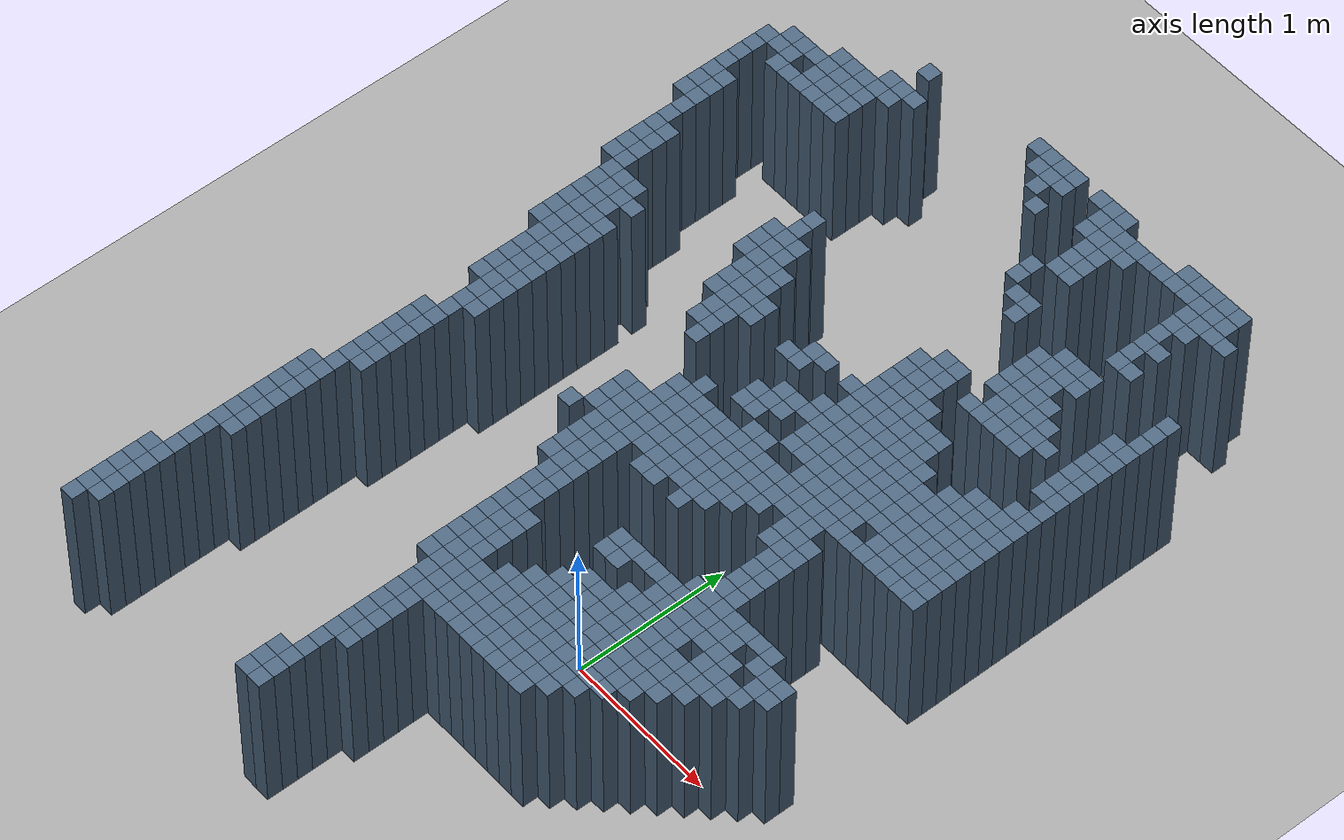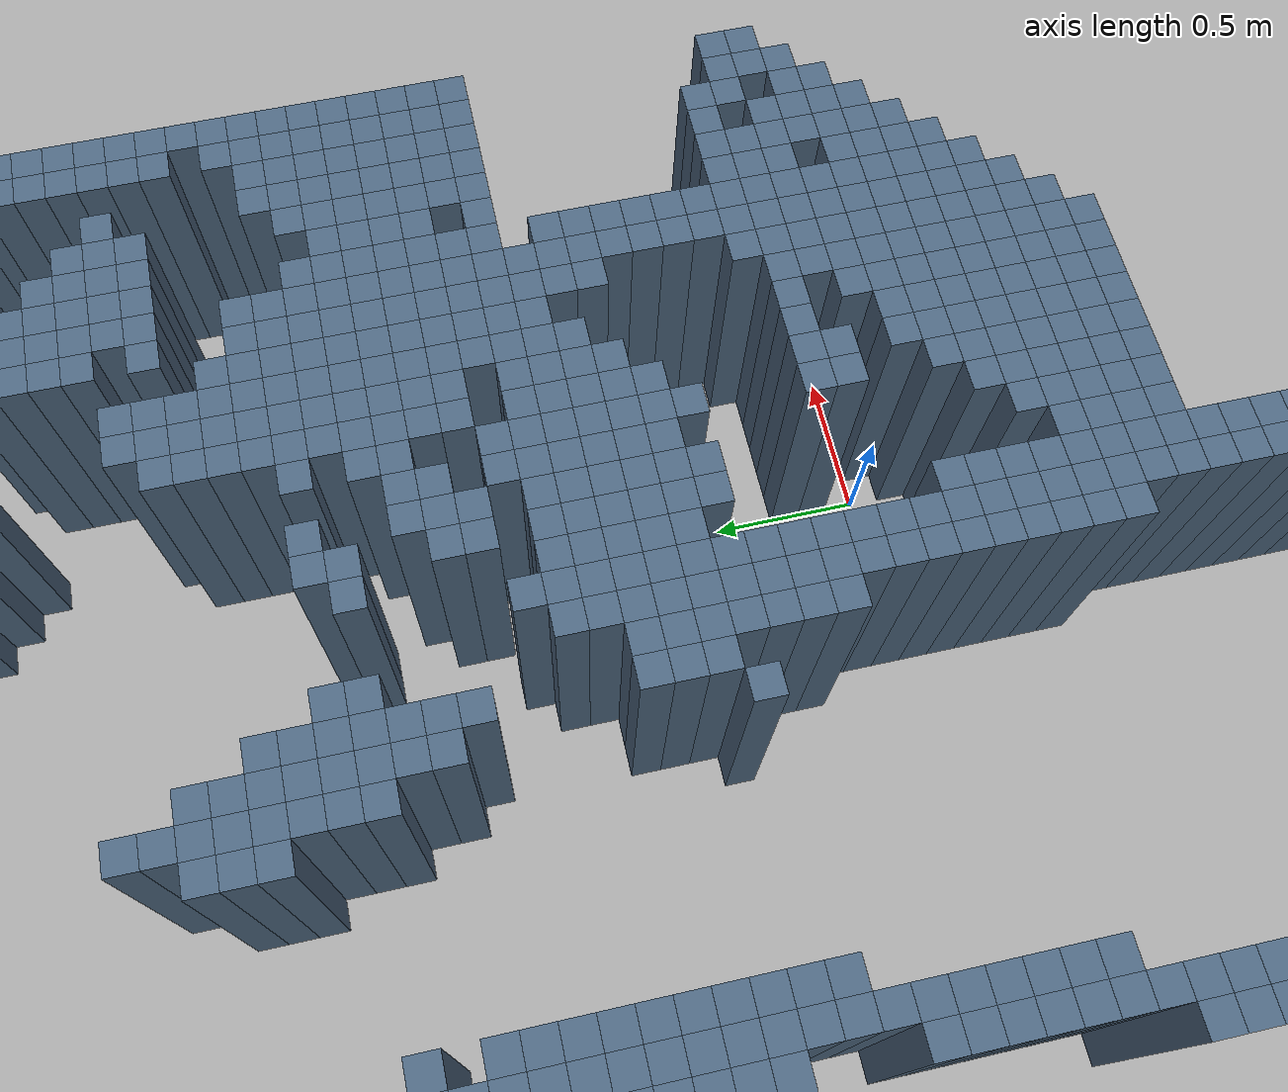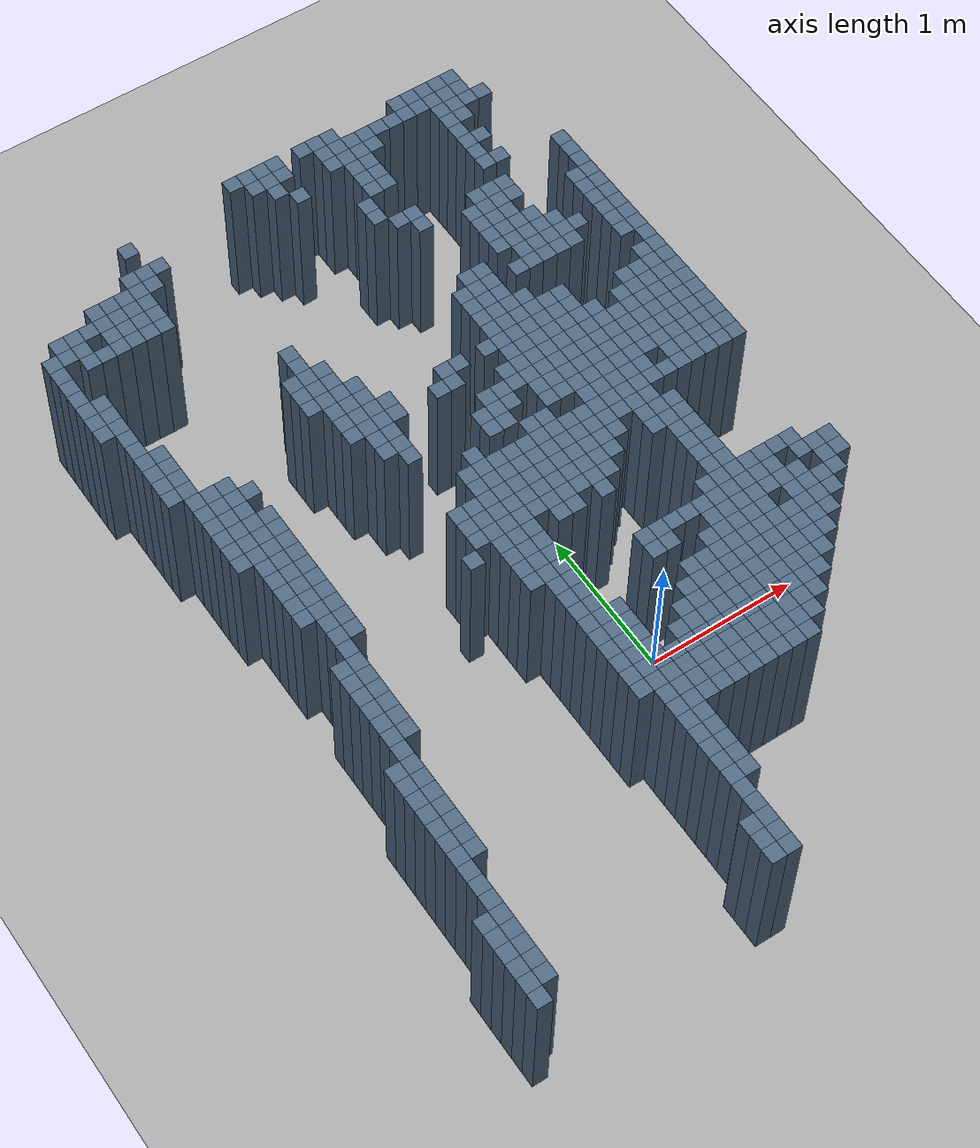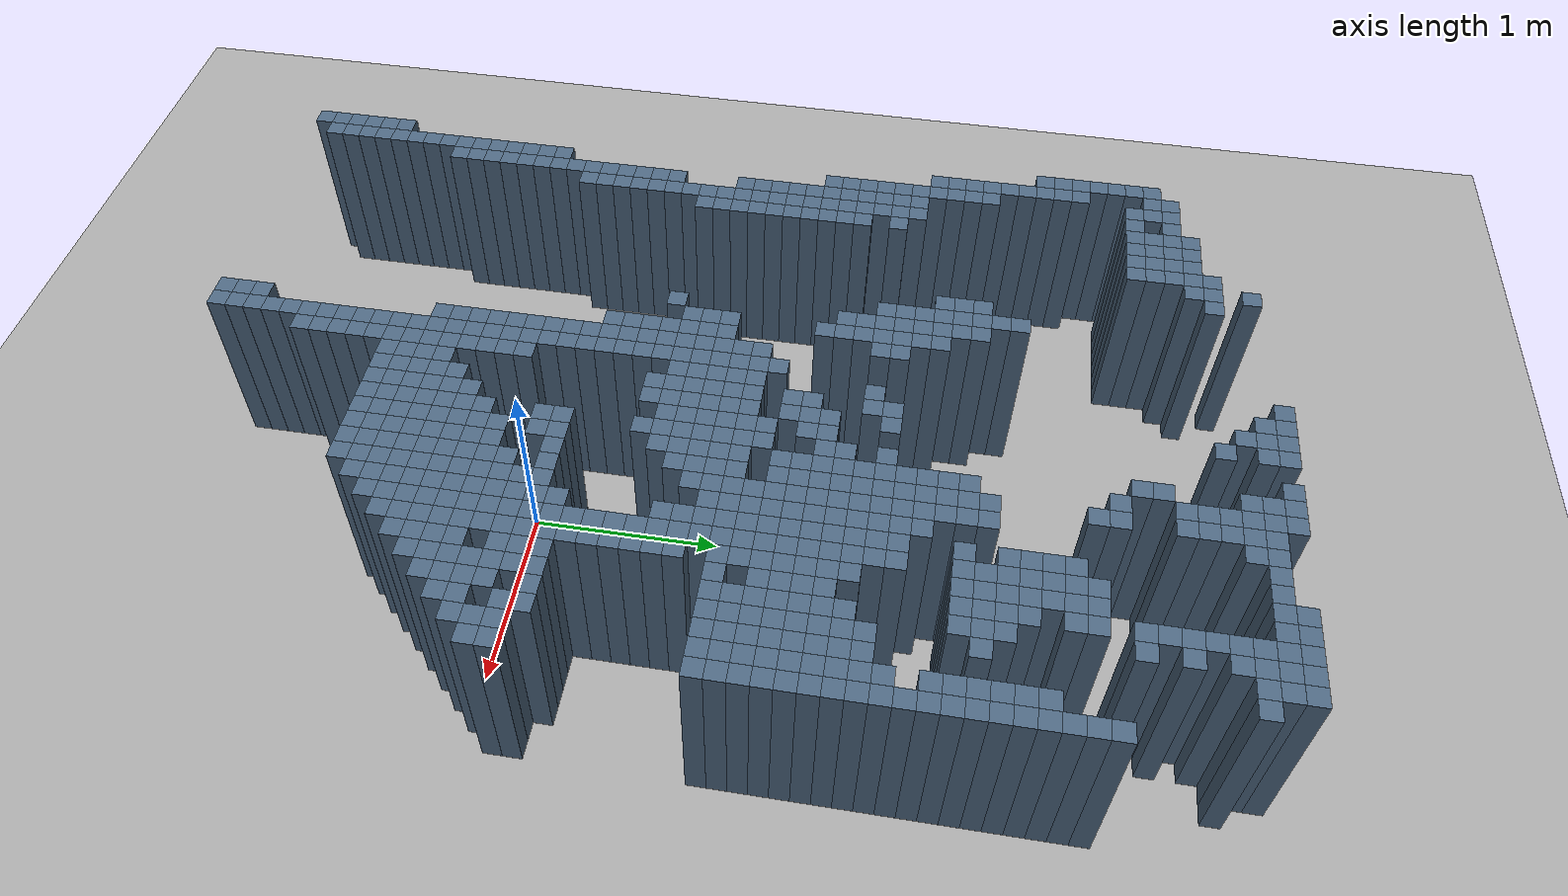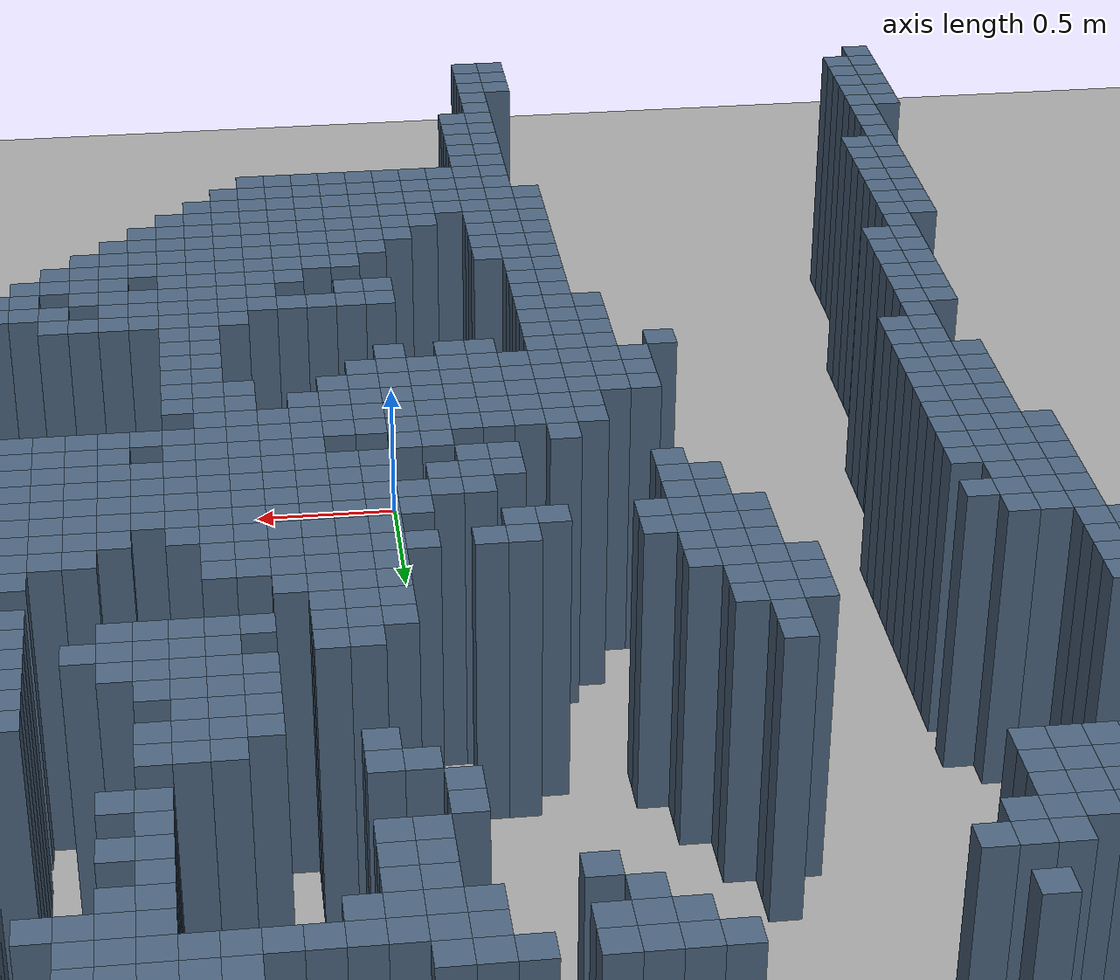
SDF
<?xml version='1.0' encoding='utf-8'?>
<sdf version="1.6">
  <world name="default">
    <gravity>0 0 -9.81</gravity>
    <physics name="default_physics" type="ode">
      <max_step_size>0.001</max_step_size>
      <real_time_update_rate>1000</real_time_update_rate>
    </physics>
    <scene>
      <ambient>0.6 0.6 0.6 1</ambient>
      <shadows>false</shadows>
    </scene>
    <light name="sun" type="directional">
      <pose>0 0 10 0 0 0</pose>
      <diffuse>0.8 0.8 0.8 1</diffuse>
      <direction>-0.5 0.1 -1</direction>
    </light>
    <model name="artificial_flat_ground">
      <static>true</static>
      <link name="ground">
        <collision name="floor_collision">
          <geometry>
            <plane>
              <normal>0 0 1</normal>
              <size>100 100</size>
            </plane>
          </geometry>
        </collision>
        <visual name="floor_visual">
          <geometry>
            <plane>
              <normal>0 0 1</normal>
              <size>100 100</size>
            </plane>
          </geometry>
          <material>
            <ambient>0.65 0.65 0.65 1</ambient>
            <diffuse>0.65 0.65 0.65 1</diffuse>
          </material>
        </visual>
      </link>
    </model>
    <model name="hilti_projected_cells">
      <static>true</static>
      <link name="obstacles">
        <collision name="cell_0_1_collision">
          <pose>-2.05000000 -1.75000000 0.50000000 0 0 0</pose>
          <geometry>
            <box>
              <size>0.10000000 0.10000000 1.00000000</size>
            </box>
          </geometry>
        </collision>
        <visual name="cell_0_1_visual">
          <pose>-2.05000000 -1.75000000 0.50000000 0 0 0</pose>
          <geometry>
            <box>
              <size>0.10000000 0.10000000 1.00000000</size>
            </box>
          </geometry>
          <material>
            <ambient>0.3 0.4 0.5 1</ambient>
            <diffuse>0.3 0.4 0.5 1</diffuse>
          </material>
        </visual>
        <collision name="cell_0_16_collision">
          <pose>-0.55000000 -1.75000000 0.50000000 0 0 0</pose>
          <geometry>
            <box>
              <size>0.10000000 0.10000000 1.00000000</size>
            </box>
          </geometry>
        </collision>
        <visual name="cell_0_16_visual">
          <pose>-0.55000000 -1.75000000 0.50000000 0 0 0</pose>
          <geometry>
            <box>
              <size>0.10000000 0.10000000 1.00000000</size>
            </box>
          </geometry>
          <material>
            <ambient>0.3 0.4 0.5 1</ambient>
            <diffuse>0.3 0.4 0.5 1</diffuse>
          </material>
        </visual>
        <collision name="cell_0_17_collision">
          <pose>-0.45000000 -1.75000000 0.50000000 0 0 0</pose>
          <geometry>
            <box>
              <size>0.10000000 0.10000000 1.00000000</size>
            </box>
          </geometry>
        </collision>
        <visual name="cell_0_17_visual">
          <pose>-0.45000000 -1.75000000 0.50000000 0 0 0</pose>
          <geometry>
            <box>
              <size>0.10000000 0.10000000 1.00000000</size>
            </box>
          </geometry>
          <material>
            <ambient>0.3 0.4 0.5 1</ambient>
            <diffuse>0.3 0.4 0.5 1</diffuse>
          </material>
        </visual>
        <collision name="cell_1_1_collision">
          <pose>-2.05000000 -1.65000000 0.50000000 0 0 0</pose>
          <geometry>
            <box>
              <size>0.10000000 0.10000000 1.00000000</size>
            </box>
          </geometry>
        </collision>
        <visual name="cell_1_1_visual">
          <pose>-2.05000000 -1.65000000 0.50000000 0 0 0</pose>
          <geometry>
            <box>
              <size>0.10000000 0.10000000 1.00000000</size>
            </box>
          </geometry>
          <material>
            <ambient>0.3 0.4 0.5 1</ambient>
            <diffuse>0.3 0.4 0.5 1</diffuse>
          </material>
        </visual>
        <collision name="cell_1_2_collision">
          <pose>-1.95000000 -1.65000000 0.50000000 0 0 0</pose>
          <geometry>
            <box>
              <size>0.10000000 0.10000000 1.00000000</size>
            </box>
          </geometry>
        </collision>
        <visual name="cell_1_2_visual">
          <pose>-1.95000000 -1.65000000 0.50000000 0 0 0</pose>
          <geometry>
            <box>
              <size>0.10000000 0.10000000 1.00000000</size>
            </box>
          </geometry>
          <material>
            <ambient>0.3 0.4 0.5 1</ambient>
            <diffuse>0.3 0.4 0.5 1</diffuse>
          </material>
        </visual>
        <collision name="cell_1_16_collision">
          <pose>-0.55000000 -1.65000000 0.50000000 0 0 0</pose>
          <geometry>
            <box>
              <size>0.10000000 0.10000000 1.00000000</size>
            </box>
          </geometry>
        </collision>
        <visual name="cell_1_16_visual">
          <pose>-0.55000000 -1.65000000 0.50000000 0 0 0</pose>
          <geometry>
            <box>
              <size>0.10000000 0.10000000 1.00000000</size>
            </box>
          </geometry>
          <material>
            <ambient>0.3 0.4 0.5 1</ambient>
            <diffuse>0.3 0.4 0.5 1</diffuse>
          </material>
        </visual>
        <collision name="cell_1_17_collision">
          <pose>-0.45000000 -1.65000000 0.50000000 0 0 0</pose>
          <geometry>
            <box>
              <size>0.10000000 0.10000000 1.00000000</size>
            </box>
          </geometry>
        </collision>
        <visual name="cell_1_17_visual">
          <pose>-0.45000000 -1.65000000 0.50000000 0 0 0</pose>
          <geometry>
            <box>
              <size>0.10000000 0.10000000 1.00000000</size>
            </box>
          </geometry>
          <material>
            <ambient>0.3 0.4 0.5 1</ambient>
            <diffuse>0.3 0.4 0.5 1</diffuse>
          </material>
        </visual>
        <collision name="cell_2_1_collision">
          <pose>-2.05000000 -1.55000000 0.50000000 0 0 0</pose>
          <geometry>
            <box>
              <size>0.10000000 0.10000000 1.00000000</size>
            </box>
          </geometry>
        </collision>
        <visual name="cell_2_1_visual">
          <pose>-2.05000000 -1.55000000 0.50000000 0 0 0</pose>
          <geometry>
            <box>
              <size>0.10000000 0.10000000 1.00000000</size>
            </box>
          </geometry>
          <material>
            <ambient>0.3 0.4 0.5 1</ambient>
            <diffuse>0.3 0.4 0.5 1</diffuse>
          </material>
        </visual>
        <collision name="cell_2_2_collision">
          <pose>-1.95000000 -1.55000000 0.50000000 0 0 0</pose>
          <geometry>
            <box>
              <size>0.10000000 0.10000000 1.00000000</size>
            </box>
          </geometry>
        </collision>
        <visual name="cell_2_2_visual">
          <pose>-1.95000000 -1.55000000 0.50000000 0 0 0</pose>
          <geometry>
            <box>
              <size>0.10000000 0.10000000 1.00000000</size>
            </box>
          </geometry>
          <material>
            <ambient>0.3 0.4 0.5 1</ambient>
            <diffuse>0.3 0.4 0.5 1</diffuse>
          </material>
        </visual>
        <collision name="cell_2_16_collision">
          <pose>-0.55000000 -1.55000000 0.50000000 0 0 0</pose>
          <geometry>
            <box>
              <size>0.10000000 0.10000000 1.00000000</size>
            </box>
          </geometry>
        </collision>
        <visual name="cell_2_16_visual">
          <pose>-0.55000000 -1.55000000 0.50000000 0 0 0</pose>
          <geometry>
            <box>
              <size>0.10000000 0.10000000 1.00000000</size>
            </box>
          </geometry>
          <material>
            <ambient>0.3 0.4 0.5 1</ambient>
            <diffuse>0.3 0.4 0.5 1</diffuse>
          </material>
        </visual>
        <collision name="cell_2_17_collision">
          <pose>-0.45000000 -1.55000000 0.50000000 0 0 0</pose>
          <geometry>
            <box>
              <size>0.10000000 0.10000000 1.00000000</size>
            </box>
          </geometry>
        </collision>
        <visual name="cell_2_17_visual">
          <pose>-0.45000000 -1.55000000 0.50000000 0 0 0</pose>
          <geometry>
            <box>
              <size>0.10000000 0.10000000 1.00000000</size>
            </box>
          </geometry>
          <material>
            <ambient>0.3 0.4 0.5 1</ambient>
            <diffuse>0.3 0.4 0.5 1</diffuse>
          </material>
        </visual>
        <collision name="cell_3_1_collision">
          <pose>-2.05000000 -1.45000000 0.50000000 0 0 0</pose>
          <geometry>
            <box>
              <size>0.10000000 0.10000000 1.00000000</size>
            </box>
          </geometry>
        </collision>
        <visual name="cell_3_1_visual">
          <pose>-2.05000000 -1.45000000 0.50000000 0 0 0</pose>
          <geometry>
            <box>
              <size>0.10000000 0.10000000 1.00000000</size>
            </box>
          </geometry>
          <material>
            <ambient>0.3 0.4 0.5 1</ambient>
            <diffuse>0.3 0.4 0.5 1</diffuse>
          </material>
        </visual>
        <collision name="cell_3_2_collision">
          <pose>-1.95000000 -1.45000000 0.50000000 0 0 0</pose>
          <geometry>
            <box>
              <size>0.10000000 0.10000000 1.00000000</size>
            </box>
          </geometry>
        </collision>
        <visual name="cell_3_2_visual">
          <pose>-1.95000000 -1.45000000 0.50000000 0 0 0</pose>
          <geometry>
            <box>
              <size>0.10000000 0.10000000 1.00000000</size>
            </box>
          </geometry>
          <material>
            <ambient>0.3 0.4 0.5 1</ambient>
            <diffuse>0.3 0.4 0.5 1</diffuse>
          </material>
        </visual>
        <collision name="cell_3_17_collision">
          <pose>-0.45000000 -1.45000000 0.50000000 0 0 0</pose>
          <geometry>
            <box>
              <size>0.10000000 0.10000000 1.00000000</size>
            </box>
          </geometry>
        </collision>
        <visual name="cell_3_17_visual">
          <pose>-0.45000000 -1.45000000 0.50000000 0 0 0</pose>
          <geometry>
            <box>
              <size>0.10000000 0.10000000 1.00000000</size>
            </box>
          </geometry>
          <material>
            <ambient>0.3 0.4 0.5 1</ambient>
            <diffuse>0.3 0.4 0.5 1</diffuse>
          </material>
        </visual>
        <collision name="cell_4_1_collision">
          <pose>-2.05000000 -1.35000000 0.50000000 0 0 0</pose>
          <geometry>
            <box>
              <size>0.10000000 0.10000000 1.00000000</size>
            </box>
          </geometry>
        </collision>
        <visual name="cell_4_1_visual">
          <pose>-2.05000000 -1.35000000 0.50000000 0 0 0</pose>
          <geometry>
            <box>
              <size>0.10000000 0.10000000 1.00000000</size>
            </box>
          </geometry>
          <material>
            <ambient>0.3 0.4 0.5 1</ambient>
            <diffuse>0.3 0.4 0.5 1</diffuse>
          </material>
        </visual>
        <collision name="cell_4_2_collision">
          <pose>-1.95000000 -1.35000000 0.50000000 0 0 0</pose>
          <geometry>
            <box>
              <size>0.10000000 0.10000000 1.00000000</size>
            </box>
          </geometry>
        </collision>
        <visual name="cell_4_2_visual">
          <pose>-1.95000000 -1.35000000 0.50000000 0 0 0</pose>
          <geometry>
            <box>
              <size>0.10000000 0.10000000 1.00000000</size>
            </box>
          </geometry>
          <material>
            <ambient>0.3 0.4 0.5 1</ambient>
            <diffuse>0.3 0.4 0.5 1</diffuse>
          </material>
        </visual>
        <collision name="cell_4_17_collision">
          <pose>-0.45000000 -1.35000000 0.50000000 0 0 0</pose>
          <geometry>
            <box>
              <size>0.10000000 0.10000000 1.00000000</size>
            </box>
          </geometry>
        </collision>
        <visual name="cell_4_17_visual">
          <pose>-0.45000000 -1.35000000 0.50000000 0 0 0</pose>
          <geometry>
            <box>
              <size>0.10000000 0.10000000 1.00000000</size>
            </box>
          </geometry>
          <material>
            <ambient>0.3 0.4 0.5 1</ambient>
            <diffuse>0.3 0.4 0.5 1</diffuse>
          </material>
        </visual>
        <collision name="cell_5_1_collision">
          <pose>-2.05000000 -1.25000000 0.50000000 0 0 0</pose>
          <geometry>
            <box>
              <size>0.10000000 0.10000000 1.00000000</size>
            </box>
          </geometry>
        </collision>
        <visual name="cell_5_1_visual">
          <pose>-2.05000000 -1.25000000 0.50000000 0 0 0</pose>
          <geometry>
            <box>
              <size>0.10000000 0.10000000 1.00000000</size>
            </box>
          </geometry>
          <material>
            <ambient>0.3 0.4 0.5 1</ambient>
            <diffuse>0.3 0.4 0.5 1</diffuse>
          </material>
        </visual>
        <collision name="cell_5_2_collision">
          <pose>-1.95000000 -1.25000000 0.50000000 0 0 0</pose>
          <geometry>
            <box>
              <size>0.10000000 0.10000000 1.00000000</size>
            </box>
          </geometry>
        </collision>
        <visual name="cell_5_2_visual">
          <pose>-1.95000000 -1.25000000 0.50000000 0 0 0</pose>
          <geometry>
            <box>
              <size>0.10000000 0.10000000 1.00000000</size>
            </box>
          </geometry>
          <material>
            <ambient>0.3 0.4 0.5 1</ambient>
            <diffuse>0.3 0.4 0.5 1</diffuse>
          </material>
        </visual>
        <collision name="cell_5_17_collision">
          <pose>-0.45000000 -1.25000000 0.50000000 0 0 0</pose>
          <geometry>
            <box>
              <size>0.10000000 0.10000000 1.00000000</size>
            </box>
          </geometry>
        </collision>
        <visual name="cell_5_17_visual">
          <pose>-0.45000000 -1.25000000 0.50000000 0 0 0</pose>
          <geometry>
            <box>
              <size>0.10000000 0.10000000 1.00000000</size>
            </box>
          </geometry>
          <material>
            <ambient>0.3 0.4 0.5 1</ambient>
            <diffuse>0.3 0.4 0.5 1</diffuse>
          </material>
        </visual>
        <collision name="cell_5_18_collision">
          <pose>-0.35000000 -1.25000000 0.50000000 0 0 0</pose>
          <geometry>
            <box>
              <size>0.10000000 0.10000000 1.00000000</size>
            </box>
          </geometry>
        </collision>
        <visual name="cell_5_18_visual">
          <pose>-0.35000000 -1.25000000 0.50000000 0 0 0</pose>
          <geometry>
            <box>
              <size>0.10000000 0.10000000 1.00000000</size>
            </box>
          </geometry>
          <material>
            <ambient>0.3 0.4 0.5 1</ambient>
            <diffuse>0.3 0.4 0.5 1</diffuse>
          </material>
        </visual>
        <collision name="cell_6_2_collision">
          <pose>-1.95000000 -1.15000000 0.50000000 0 0 0</pose>
          <geometry>
            <box>
              <size>0.10000000 0.10000000 1.00000000</size>
            </box>
          </geometry>
        </collision>
        <visual name="cell_6_2_visual">
          <pose>-1.95000000 -1.15000000 0.50000000 0 0 0</pose>
          <geometry>
            <box>
              <size>0.10000000 0.10000000 1.00000000</size>
            </box>
          </geometry>
          <material>
            <ambient>0.3 0.4 0.5 1</ambient>
            <diffuse>0.3 0.4 0.5 1</diffuse>
          </material>
        </visual>
        <collision name="cell_6_17_collision">
          <pose>-0.45000000 -1.15000000 0.50000000 0 0 0</pose>
          <geometry>
            <box>
              <size>0.10000000 0.10000000 1.00000000</size>
            </box>
          </geometry>
        </collision>
        <visual name="cell_6_17_visual">
          <pose>-0.45000000 -1.15000000 0.50000000 0 0 0</pose>
          <geometry>
            <box>
              <size>0.10000000 0.10000000 1.00000000</size>
            </box>
          </geometry>
          <material>
            <ambient>0.3 0.4 0.5 1</ambient>
            <diffuse>0.3 0.4 0.5 1</diffuse>
          </material>
        </visual>
        <collision name="cell_6_18_collision">
          <pose>-0.35000000 -1.15000000 0.50000000 0 0 0</pose>
          <geometry>
            <box>
              <size>0.10000000 0.10000000 1.00000000</size>
            </box>
          </geometry>
        </collision>
        <visual name="cell_6_18_visual">
          <pose>-0.35000000 -1.15000000 0.50000000 0 0 0</pose>
          <geometry>
            <box>
              <size>0.10000000 0.10000000 1.00000000</size>
            </box>
          </geometry>
          <material>
            <ambient>0.3 0.4 0.5 1</ambient>
            <diffuse>0.3 0.4 0.5 1</diffuse>
          </material>
        </visual>
        <collision name="cell_7_2_collision">
          <pose>-1.95000000 -1.05000000 0.50000000 0 0 0</pose>
          <geometry>
            <box>
              <size>0.10000000 0.10000000 1.00000000</size>
            </box>
          </geometry>
        </collision>
        <visual name="cell_7_2_visual">
          <pose>-1.95000000 -1.05000000 0.50000000 0 0 0</pose>
          <geometry>
            <box>
              <size>0.10000000 0.10000000 1.00000000</size>
            </box>
          </geometry>
          <material>
            <ambient>0.3 0.4 0.5 1</ambient>
            <diffuse>0.3 0.4 0.5 1</diffuse>
          </material>
        </visual>
        <collision name="cell_7_17_collision">
          <pose>-0.45000000 -1.05000000 0.50000000 0 0 0</pose>
          <geometry>
            <box>
              <size>0.10000000 0.10000000 1.00000000</size>
            </box>
          </geometry>
        </collision>
        <visual name="cell_7_17_visual">
          <pose>-0.45000000 -1.05000000 0.50000000 0 0 0</pose>
          <geometry>
            <box>
              <size>0.10000000 0.10000000 1.00000000</size>
            </box>
          </geometry>
          <material>
            <ambient>0.3 0.4 0.5 1</ambient>
            <diffuse>0.3 0.4 0.5 1</diffuse>
          </material>
        </visual>
        <collision name="cell_7_18_collision">
          <pose>-0.35000000 -1.05000000 0.50000000 0 0 0</pose>
          <geometry>
            <box>
              <size>0.10000000 0.10000000 1.00000000</size>
            </box>
          </geometry>
        </collision>
        <visual name="cell_7_18_visual">
          <pose>-0.35000000 -1.05000000 0.50000000 0 0 0</pose>
          <geometry>
            <box>
              <size>0.10000000 0.10000000 1.00000000</size>
            </box>
          </geometry>
          <material>
            <ambient>0.3 0.4 0.5 1</ambient>
            <diffuse>0.3 0.4 0.5 1</diffuse>
          </material>
        </visual>
        <collision name="cell_8_2_collision">
          <pose>-1.95000000 -0.95000000 0.50000000 0 0 0</pose>
          <geometry>
            <box>
              <size>0.10000000 0.10000000 1.00000000</size>
            </box>
          </geometry>
        </collision>
        <visual name="cell_8_2_visual">
          <pose>-1.95000000 -0.95000000 0.50000000 0 0 0</pose>
          <geometry>
            <box>
              <size>0.10000000 0.10000000 1.00000000</size>
            </box>
          </geometry>
          <material>
            <ambient>0.3 0.4 0.5 1</ambient>
            <diffuse>0.3 0.4 0.5 1</diffuse>
          </material>
        </visual>
        <collision name="cell_8_17_collision">
          <pose>-0.45000000 -0.95000000 0.50000000 0 0 0</pose>
          <geometry>
            <box>
              <size>0.10000000 0.10000000 1.00000000</size>
            </box>
          </geometry>
        </collision>
        <visual name="cell_8_17_visual">
          <pose>-0.45000000 -0.95000000 0.50000000 0 0 0</pose>
          <geometry>
            <box>
              <size>0.10000000 0.10000000 1.00000000</size>
            </box>
          </geometry>
          <material>
            <ambient>0.3 0.4 0.5 1</ambient>
            <diffuse>0.3 0.4 0.5 1</diffuse>
          </material>
        </visual>
        <collision name="cell_8_18_collision">
          <pose>-0.35000000 -0.95000000 0.50000000 0 0 0</pose>
          <geometry>
            <box>
              <size>0.10000000 0.10000000 1.00000000</size>
            </box>
          </geometry>
        </collision>
        <visual name="cell_8_18_visual">
          <pose>-0.35000000 -0.95000000 0.50000000 0 0 0</pose>
          <geometry>
            <box>
              <size>0.10000000 0.10000000 1.00000000</size>
            </box>
          </geometry>
          <material>
            <ambient>0.3 0.4 0.5 1</ambient>
            <diffuse>0.3 0.4 0.5 1</diffuse>
          </material>
        </visual>
        <collision name="cell_9_2_collision">
          <pose>-1.95000000 -0.85000000 0.50000000 0 0 0</pose>
          <geometry>
            <box>
              <size>0.10000000 0.10000000 1.00000000</size>
            </box>
          </geometry>
        </collision>
        <visual name="cell_9_2_visual">
          <pose>-1.95000000 -0.85000000 0.50000000 0 0 0</pose>
          <geometry>
            <box>
              <size>0.10000000 0.10000000 1.00000000</size>
            </box>
          </geometry>
          <material>
            <ambient>0.3 0.4 0.5 1</ambient>
            <diffuse>0.3 0.4 0.5 1</diffuse>
          </material>
        </visual>
        <collision name="cell_9_3_collision">
          <pose>-1.85000000 -0.85000000 0.50000000 0 0 0</pose>
          <geometry>
            <box>
              <size>0.10000000 0.10000000 1.00000000</size>
            </box>
          </geometry>
        </collision>
        <visual name="cell_9_3_visual">
          <pose>-1.85000000 -0.85000000 0.50000000 0 0 0</pose>
          <geometry>
            <box>
              <size>0.10000000 0.10000000 1.00000000</size>
            </box>
          </geometry>
          <material>
            <ambient>0.3 0.4 0.5 1</ambient>
            <diffuse>0.3 0.4 0.5 1</diffuse>
          </material>
        </visual>
        <collision name="cell_9_17_collision">
          <pose>-0.45000000 -0.85000000 0.50000000 0 0 0</pose>
          <geometry>
            <box>
              <size>0.10000000 0.10000000 1.00000000</size>
            </box>
          </geometry>
        </collision>
        <visual name="cell_9_17_visual">
          <pose>-0.45000000 -0.85000000 0.50000000 0 0 0</pose>
          <geometry>
            <box>
              <size>0.10000000 0.10000000 1.00000000</size>
            </box>
          </geometry>
          <material>
            <ambient>0.3 0.4 0.5 1</ambient>
            <diffuse>0.3 0.4 0.5 1</diffuse>
          </material>
        </visual>
        <collision name="cell_9_18_collision">
          <pose>-0.35000000 -0.85000000 0.50000000 0 0 0</pose>
          <geometry>
            <box>
              <size>0.10000000 0.10000000 1.00000000</size>
            </box>
          </geometry>
        </collision>
        <visual name="cell_9_18_visual">
          <pose>-0.35000000 -0.85000000 0.50000000 0 0 0</pose>
          <geometry>
            <box>
              <size>0.10000000 0.10000000 1.00000000</size>
            </box>
          </geometry>
          <material>
            <ambient>0.3 0.4 0.5 1</ambient>
            <diffuse>0.3 0.4 0.5 1</diffuse>
          </material>
        </visual>
        <collision name="cell_10_2_collision">
          <pose>-1.95000000 -0.75000000 0.50000000 0 0 0</pose>
          <geometry>
            <box>
              <size>0.10000000 0.10000000 1.00000000</size>
            </box>
          </geometry>
        </collision>
        <visual name="cell_10_2_visual">
          <pose>-1.95000000 -0.75000000 0.50000000 0 0 0</pose>
          <geometry>
            <box>
              <size>0.10000000 0.10000000 1.00000000</size>
            </box>
          </geometry>
          <material>
            <ambient>0.3 0.4 0.5 1</ambient>
            <diffuse>0.3 0.4 0.5 1</diffuse>
          </material>
        </visual>
        <collision name="cell_10_3_collision">
          <pose>-1.85000000 -0.75000000 0.50000000 0 0 0</pose>
          <geometry>
            <box>
              <size>0.10000000 0.10000000 1.00000000</size>
            </box>
          </geometry>
        </collision>
        <visual name="cell_10_3_visual">
          <pose>-1.85000000 -0.75000000 0.50000000 0 0 0</pose>
          <geometry>
            <box>
              <size>0.10000000 0.10000000 1.00000000</size>
            </box>
          </geometry>
          <material>
            <ambient>0.3 0.4 0.5 1</ambient>
            <diffuse>0.3 0.4 0.5 1</diffuse>
          </material>
        </visual>
        <collision name="cell_10_17_collision">
          <pose>-0.45000000 -0.75000000 0.50000000 0 0 0</pose>
          <geometry>
            <box>
              <size>0.10000000 0.10000000 1.00000000</size>
            </box>
          </geometry>
        </collision>
        <visual name="cell_10_17_visual">
          <pose>-0.45000000 -0.75000000 0.50000000 0 0 0</pose>
          <geometry>
            <box>
              <size>0.10000000 0.10000000 1.00000000</size>
            </box>
          </geometry>
          <material>
            <ambient>0.3 0.4 0.5 1</ambient>
            <diffuse>0.3 0.4 0.5 1</diffuse>
          </material>
        </visual>
        <collision name="cell_10_18_collision">
          <pose>-0.35000000 -0.75000000 0.50000000 0 0 0</pose>
          <geometry>
            <box>
              <size>0.10000000 0.10000000 1.00000000</size>
            </box>
          </geometry>
        </collision>
        <visual name="cell_10_18_visual">
          <pose>-0.35000000 -0.75000000 0.50000000 0 0 0</pose>
          <geometry>
            <box>
              <size>0.10000000 0.10000000 1.00000000</size>
            </box>
          </geometry>
          <material>
            <ambient>0.3 0.4 0.5 1</ambient>
            <diffuse>0.3 0.4 0.5 1</diffuse>
          </material>
        </visual>
        <collision name="cell_10_19_collision">
          <pose>-0.25000000 -0.75000000 0.50000000 0 0 0</pose>
          <geometry>
            <box>
              <size>0.10000000 0.10000000 1.00000000</size>
            </box>
          </geometry>
        </collision>
        <visual name="cell_10_19_visual">
          <pose>-0.25000000 -0.75000000 0.50000000 0 0 0</pose>
          <geometry>
            <box>
              <size>0.10000000 0.10000000 1.00000000</size>
            </box>
          </geometry>
          <material>
            <ambient>0.3 0.4 0.5 1</ambient>
            <diffuse>0.3 0.4 0.5 1</diffuse>
          </material>
        </visual>
        <collision name="cell_10_20_collision">
          <pose>-0.15000000 -0.75000000 0.50000000 0 0 0</pose>
          <geometry>
            <box>
              <size>0.10000000 0.10000000 1.00000000</size>
            </box>
          </geometry>
        </collision>
        <visual name="cell_10_20_visual">
          <pose>-0.15000000 -0.75000000 0.50000000 0 0 0</pose>
          <geometry>
            <box>
              <size>0.10000000 0.10000000 1.00000000</size>
            </box>
          </geometry>
          <material>
            <ambient>0.3 0.4 0.5 1</ambient>
            <diffuse>0.3 0.4 0.5 1</diffuse>
          </material>
        </visual>
        <collision name="cell_10_21_collision">
          <pose>-0.05000000 -0.75000000 0.50000000 0 0 0</pose>
          <geometry>
            <box>
              <size>0.10000000 0.10000000 1.00000000</size>
            </box>
          </geometry>
        </collision>
        <visual name="cell_10_21_visual">
          <pose>-0.05000000 -0.75000000 0.50000000 0 0 0</pose>
          <geometry>
            <box>
              <size>0.10000000 0.10000000 1.00000000</size>
            </box>
          </geometry>
          <material>
            <ambient>0.3 0.4 0.5 1</ambient>
            <diffuse>0.3 0.4 0.5 1</diffuse>
          </material>
        </visual>
        <collision name="cell_10_22_collision">
          <pose>0.05000000 -0.75000000 0.50000000 0 0 0</pose>
          <geometry>
            <box>
              <size>0.10000000 0.10000000 1.00000000</size>
            </box>
          </geometry>
        </collision>
        <visual name="cell_10_22_visual">
          <pose>0.05000000 -0.75000000 0.50000000 0 0 0</pose>
          <geometry>
            <box>
              <size>0.10000000 0.10000000 1.00000000</size>
            </box>
          </geometry>
          <material>
            <ambient>0.3 0.4 0.5 1</ambient>
            <diffuse>0.3 0.4 0.5 1</diffuse>
          </material>
        </visual>
        <collision name="cell_10_23_collision">
          <pose>0.15000000 -0.75000000 0.50000000 0 0 0</pose>
          <geometry>
            <box>
              <size>0.10000000 0.10000000 1.00000000</size>
            </box>
          </geometry>
        </collision>
        <visual name="cell_10_23_visual">
          <pose>0.15000000 -0.75000000 0.50000000 0 0 0</pose>
          <geometry>
            <box>
              <size>0.10000000 0.10000000 1.00000000</size>
            </box>
          </geometry>
          <material>
            <ambient>0.3 0.4 0.5 1</ambient>
            <diffuse>0.3 0.4 0.5 1</diffuse>
          </material>
        </visual>
        <collision name="cell_10_24_collision">
          <pose>0.25000000 -0.75000000 0.50000000 0 0 0</pose>
          <geometry>
            <box>
              <size>0.10000000 0.10000000 1.00000000</size>
            </box>
          </geometry>
        </collision>
        <visual name="cell_10_24_visual">
          <pose>0.25000000 -0.75000000 0.50000000 0 0 0</pose>
          <geometry>
            <box>
              <size>0.10000000 0.10000000 1.00000000</size>
            </box>
          </geometry>
          <material>
            <ambient>0.3 0.4 0.5 1</ambient>
            <diffuse>0.3 0.4 0.5 1</diffuse>
          </material>
        </visual>
        <collision name="cell_10_25_collision">
          <pose>0.35000000 -0.75000000 0.50000000 0 0 0</pose>
          <geometry>
            <box>
              <size>0.10000000 0.10000000 1.00000000</size>
            </box>
          </geometry>
        </collision>
        <visual name="cell_10_25_visual">
          <pose>0.35000000 -0.75000000 0.50000000 0 0 0</pose>
          <geometry>
            <box>
              <size>0.10000000 0.10000000 1.00000000</size>
            </box>
          </geometry>
          <material>
            <ambient>0.3 0.4 0.5 1</ambient>
            <diffuse>0.3 0.4 0.5 1</diffuse>
          </material>
        </visual>
        <collision name="cell_10_26_collision">
          <pose>0.45000000 -0.75000000 0.50000000 0 0 0</pose>
          <geometry>
            <box>
              <size>0.10000000 0.10000000 1.00000000</size>
            </box>
          </geometry>
        </collision>
        <visual name="cell_10_26_visual">
          <pose>0.45000000 -0.75000000 0.50000000 0 0 0</pose>
          <geometry>
            <box>
              <size>0.10000000 0.10000000 1.00000000</size>
            </box>
          </geometry>
          <material>
            <ambient>0.3 0.4 0.5 1</ambient>
            <diffuse>0.3 0.4 0.5 1</diffuse>
          </material>
        </visual>
        <collision name="cell_11_2_collision">
          <pose>-1.95000000 -0.65000000 0.50000000 0 0 0</pose>
          <geometry>
            <box>
              <size>0.10000000 0.10000000 1.00000000</size>
            </box>
          </geometry>
        </collision>
        <visual name="cell_11_2_visual">
          <pose>-1.95000000 -0.65000000 0.50000000 0 0 0</pose>
          <geometry>
            <box>
              <size>0.10000000 0.10000000 1.00000000</size>
            </box>
          </geometry>
          <material>
            <ambient>0.3 0.4 0.5 1</ambient>
            <diffuse>0.3 0.4 0.5 1</diffuse>
          </material>
        </visual>
        <collision name="cell_11_3_collision">
          <pose>-1.85000000 -0.65000000 0.50000000 0 0 0</pose>
          <geometry>
            <box>
              <size>0.10000000 0.10000000 1.00000000</size>
            </box>
          </geometry>
        </collision>
        <visual name="cell_11_3_visual">
          <pose>-1.85000000 -0.65000000 0.50000000 0 0 0</pose>
          <geometry>
            <box>
              <size>0.10000000 0.10000000 1.00000000</size>
            </box>
          </geometry>
          <material>
            <ambient>0.3 0.4 0.5 1</ambient>
            <diffuse>0.3 0.4 0.5 1</diffuse>
          </material>
        </visual>
        <collision name="cell_11_17_collision">
          <pose>-0.45000000 -0.65000000 0.50000000 0 0 0</pose>
          <geometry>
            <box>
              <size>0.10000000 0.10000000 1.00000000</size>
            </box>
          </geometry>
        </collision>
        <visual name="cell_11_17_visual">
          <pose>-0.45000000 -0.65000000 0.50000000 0 0 0</pose>
          <geometry>
            <box>
              <size>0.10000000 0.10000000 1.00000000</size>
            </box>
          </geometry>
          <material>
            <ambient>0.3 0.4 0.5 1</ambient>
            <diffuse>0.3 0.4 0.5 1</diffuse>
          </material>
        </visual>
        <collision name="cell_11_18_collision">
          <pose>-0.35000000 -0.65000000 0.50000000 0 0 0</pose>
          <geometry>
            <box>
              <size>0.10000000 0.10000000 1.00000000</size>
            </box>
          </geometry>
        </collision>
        <visual name="cell_11_18_visual">
          <pose>-0.35000000 -0.65000000 0.50000000 0 0 0</pose>
          <geometry>
            <box>
              <size>0.10000000 0.10000000 1.00000000</size>
            </box>
          </geometry>
          <material>
            <ambient>0.3 0.4 0.5 1</ambient>
            <diffuse>0.3 0.4 0.5 1</diffuse>
          </material>
        </visual>
        <collision name="cell_11_19_collision">
          <pose>-0.25000000 -0.65000000 0.50000000 0 0 0</pose>
          <geometry>
            <box>
              <size>0.10000000 0.10000000 1.00000000</size>
            </box>
          </geometry>
        </collision>
        <visual name="cell_11_19_visual">
          <pose>-0.25000000 -0.65000000 0.50000000 0 0 0</pose>
          <geometry>
            <box>
              <size>0.10000000 0.10000000 1.00000000</size>
            </box>
          </geometry>
          <material>
            <ambient>0.3 0.4 0.5 1</ambient>
            <diffuse>0.3 0.4 0.5 1</diffuse>
          </material>
        </visual>
        <collision name="cell_11_20_collision">
          <pose>-0.15000000 -0.65000000 0.50000000 0 0 0</pose>
          <geometry>
            <box>
              <size>0.10000000 0.10000000 1.00000000</size>
            </box>
          </geometry>
        </collision>
        <visual name="cell_11_20_visual">
          <pose>-0.15000000 -0.65000000 0.50000000 0 0 0</pose>
          <geometry>
            <box>
              <size>0.10000000 0.10000000 1.00000000</size>
            </box>
          </geometry>
          <material>
            <ambient>0.3 0.4 0.5 1</ambient>
            <diffuse>0.3 0.4 0.5 1</diffuse>
          </material>
        </visual>
        <collision name="cell_11_21_collision">
          <pose>-0.05000000 -0.65000000 0.50000000 0 0 0</pose>
          <geometry>
            <box>
              <size>0.10000000 0.10000000 1.00000000</size>
            </box>
          </geometry>
        </collision>
        <visual name="cell_11_21_visual">
          <pose>-0.05000000 -0.65000000 0.50000000 0 0 0</pose>
          <geometry>
            <box>
              <size>0.10000000 0.10000000 1.00000000</size>
            </box>
          </geometry>
          <material>
            <ambient>0.3 0.4 0.5 1</ambient>
            <diffuse>0.3 0.4 0.5 1</diffuse>
          </material>
        </visual>
        <collision name="cell_11_22_collision">
          <pose>0.05000000 -0.65000000 0.50000000 0 0 0</pose>
          <geometry>
            <box>
              <size>0.10000000 0.10000000 1.00000000</size>
            </box>
          </geometry>
        </collision>
        <visual name="cell_11_22_visual">
          <pose>0.05000000 -0.65000000 0.50000000 0 0 0</pose>
          <geometry>
            <box>
              <size>0.10000000 0.10000000 1.00000000</size>
            </box>
          </geometry>
          <material>
            <ambient>0.3 0.4 0.5 1</ambient>
            <diffuse>0.3 0.4 0.5 1</diffuse>
          </material>
        </visual>
        <collision name="cell_11_23_collision">
          <pose>0.15000000 -0.65000000 0.50000000 0 0 0</pose>
          <geometry>
            <box>
              <size>0.10000000 0.10000000 1.00000000</size>
            </box>
          </geometry>
        </collision>
        <visual name="cell_11_23_visual">
          <pose>0.15000000 -0.65000000 0.50000000 0 0 0</pose>
          <geometry>
            <box>
              <size>0.10000000 0.10000000 1.00000000</size>
            </box>
          </geometry>
          <material>
            <ambient>0.3 0.4 0.5 1</ambient>
            <diffuse>0.3 0.4 0.5 1</diffuse>
          </material>
        </visual>
        <collision name="cell_11_24_collision">
          <pose>0.25000000 -0.65000000 0.50000000 0 0 0</pose>
          <geometry>
            <box>
              <size>0.10000000 0.10000000 1.00000000</size>
            </box>
          </geometry>
        </collision>
        <visual name="cell_11_24_visual">
          <pose>0.25000000 -0.65000000 0.50000000 0 0 0</pose>
          <geometry>
            <box>
              <size>0.10000000 0.10000000 1.00000000</size>
            </box>
          </geometry>
          <material>
            <ambient>0.3 0.4 0.5 1</ambient>
            <diffuse>0.3 0.4 0.5 1</diffuse>
          </material>
        </visual>
        <collision name="cell_11_25_collision">
          <pose>0.35000000 -0.65000000 0.50000000 0 0 0</pose>
          <geometry>
            <box>
              <size>0.10000000 0.10000000 1.00000000</size>
            </box>
          </geometry>
        </collision>
        <visual name="cell_11_25_visual">
          <pose>0.35000000 -0.65000000 0.50000000 0 0 0</pose>
          <geometry>
            <box>
              <size>0.10000000 0.10000000 1.00000000</size>
            </box>
          </geometry>
          <material>
            <ambient>0.3 0.4 0.5 1</ambient>
            <diffuse>0.3 0.4 0.5 1</diffuse>
          </material>
        </visual>
        <collision name="cell_11_26_collision">
          <pose>0.45000000 -0.65000000 0.50000000 0 0 0</pose>
          <geometry>
            <box>
              <size>0.10000000 0.10000000 1.00000000</size>
            </box>
          </geometry>
        </collision>
        <visual name="cell_11_26_visual">
          <pose>0.45000000 -0.65000000 0.50000000 0 0 0</pose>
          <geometry>
            <box>
              <size>0.10000000 0.10000000 1.00000000</size>
            </box>
          </geometry>
          <material>
            <ambient>0.3 0.4 0.5 1</ambient>
            <diffuse>0.3 0.4 0.5 1</diffuse>
          </material>
        </visual>
        <collision name="cell_11_27_collision">
          <pose>0.55000000 -0.65000000 0.50000000 0 0 0</pose>
          <geometry>
            <box>
              <size>0.10000000 0.10000000 1.00000000</size>
            </box>
          </geometry>
        </collision>
        <visual name="cell_11_27_visual">
          <pose>0.55000000 -0.65000000 0.50000000 0 0 0</pose>
          <geometry>
            <box>
              <size>0.10000000 0.10000000 1.00000000</size>
            </box>
          </geometry>
          <material>
            <ambient>0.3 0.4 0.5 1</ambient>
            <diffuse>0.3 0.4 0.5 1</diffuse>
          </material>
        </visual>
        <collision name="cell_12_2_collision">
          <pose>-1.95000000 -0.55000000 0.50000000 0 0 0</pose>
          <geometry>
            <box>
              <size>0.10000000 0.10000000 1.00000000</size>
            </box>
          </geometry>
        </collision>
        <visual name="cell_12_2_visual">
          <pose>-1.95000000 -0.55000000 0.50000000 0 0 0</pose>
          <geometry>
            <box>
              <size>0.10000000 0.10000000 1.00000000</size>
            </box>
          </geometry>
          <material>
            <ambient>0.3 0.4 0.5 1</ambient>
            <diffuse>0.3 0.4 0.5 1</diffuse>
          </material>
        </visual>
        <collision name="cell_12_3_collision">
          <pose>-1.85000000 -0.55000000 0.50000000 0 0 0</pose>
          <geometry>
            <box>
              <size>0.10000000 0.10000000 1.00000000</size>
            </box>
          </geometry>
        </collision>
        <visual name="cell_12_3_visual">
          <pose>-1.85000000 -0.55000000 0.50000000 0 0 0</pose>
          <geometry>
            <box>
              <size>0.10000000 0.10000000 1.00000000</size>
            </box>
          </geometry>
          <material>
            <ambient>0.3 0.4 0.5 1</ambient>
            <diffuse>0.3 0.4 0.5 1</diffuse>
          </material>
        </visual>
        <collision name="cell_12_16_collision">
          <pose>-0.55000000 -0.55000000 0.50000000 0 0 0</pose>
          <geometry>
            <box>
              <size>0.10000000 0.10000000 1.00000000</size>
            </box>
          </geometry>
        </collision>
        <visual name="cell_12_16_visual">
          <pose>-0.55000000 -0.55000000 0.50000000 0 0 0</pose>
          <geometry>
            <box>
              <size>0.10000000 0.10000000 1.00000000</size>
            </box>
          </geometry>
          <material>
            <ambient>0.3 0.4 0.5 1</ambient>
            <diffuse>0.3 0.4 0.5 1</diffuse>
          </material>
        </visual>
        <collision name="cell_12_17_collision">
          <pose>-0.45000000 -0.55000000 0.50000000 0 0 0</pose>
          <geometry>
            <box>
              <size>0.10000000 0.10000000 1.00000000</size>
            </box>
          </geometry>
        </collision>
        <visual name="cell_12_17_visual">
          <pose>-0.45000000 -0.55000000 0.50000000 0 0 0</pose>
          <geometry>
            <box>
              <size>0.10000000 0.10000000 1.00000000</size>
            </box>
          </geometry>
          <material>
            <ambient>0.3 0.4 0.5 1</ambient>
            <diffuse>0.3 0.4 0.5 1</diffuse>
          </material>
        </visual>
        <collision name="cell_12_18_collision">
          <pose>-0.35000000 -0.55000000 0.50000000 0 0 0</pose>
          <geometry>
            <box>
              <size>0.10000000 0.10000000 1.00000000</size>
            </box>
          </geometry>
        </collision>
        <visual name="cell_12_18_visual">
          <pose>-0.35000000 -0.55000000 0.50000000 0 0 0</pose>
          <geometry>
            <box>
              <size>0.10000000 0.10000000 1.00000000</size>
            </box>
          </geometry>
          <material>
            <ambient>0.3 0.4 0.5 1</ambient>
            <diffuse>0.3 0.4 0.5 1</diffuse>
          </material>
        </visual>
        <collision name="cell_12_19_collision">
          <pose>-0.25000000 -0.55000000 0.50000000 0 0 0</pose>
          <geometry>
            <box>
              <size>0.10000000 0.10000000 1.00000000</size>
            </box>
          </geometry>
        </collision>
        <visual name="cell_12_19_visual">
          <pose>-0.25000000 -0.55000000 0.50000000 0 0 0</pose>
          <geometry>
            <box>
              <size>0.10000000 0.10000000 1.00000000</size>
            </box>
          </geometry>
          <material>
            <ambient>0.3 0.4 0.5 1</ambient>
            <diffuse>0.3 0.4 0.5 1</diffuse>
          </material>
        </visual>
        <collision name="cell_12_20_collision">
          <pose>-0.15000000 -0.55000000 0.50000000 0 0 0</pose>
          <geometry>
            <box>
              <size>0.10000000 0.10000000 1.00000000</size>
            </box>
          </geometry>
        </collision>
        <visual name="cell_12_20_visual">
          <pose>-0.15000000 -0.55000000 0.50000000 0 0 0</pose>
          <geometry>
            <box>
              <size>0.10000000 0.10000000 1.00000000</size>
            </box>
          </geometry>
          <material>
            <ambient>0.3 0.4 0.5 1</ambient>
            <diffuse>0.3 0.4 0.5 1</diffuse>
          </material>
        </visual>
        <collision name="cell_12_21_collision">
          <pose>-0.05000000 -0.55000000 0.50000000 0 0 0</pose>
          <geometry>
            <box>
              <size>0.10000000 0.10000000 1.00000000</size>
            </box>
          </geometry>
        </collision>
        <visual name="cell_12_21_visual">
          <pose>-0.05000000 -0.55000000 0.50000000 0 0 0</pose>
          <geometry>
            <box>
              <size>0.10000000 0.10000000 1.00000000</size>
            </box>
          </geometry>
          <material>
            <ambient>0.3 0.4 0.5 1</ambient>
            <diffuse>0.3 0.4 0.5 1</diffuse>
          </material>
        </visual>
        <collision name="cell_12_22_collision">
          <pose>0.05000000 -0.55000000 0.50000000 0 0 0</pose>
          <geometry>
            <box>
              <size>0.10000000 0.10000000 1.00000000</size>
            </box>
          </geometry>
        </collision>
        <visual name="cell_12_22_visual">
          <pose>0.05000000 -0.55000000 0.50000000 0 0 0</pose>
          <geometry>
            <box>
              <size>0.10000000 0.10000000 1.00000000</size>
            </box>
          </geometry>
          <material>
            <ambient>0.3 0.4 0.5 1</ambient>
            <diffuse>0.3 0.4 0.5 1</diffuse>
          </material>
        </visual>
        <collision name="cell_12_23_collision">
          <pose>0.15000000 -0.55000000 0.50000000 0 0 0</pose>
          <geometry>
            <box>
              <size>0.10000000 0.10000000 1.00000000</size>
            </box>
          </geometry>
        </collision>
        <visual name="cell_12_23_visual">
          <pose>0.15000000 -0.55000000 0.50000000 0 0 0</pose>
          <geometry>
            <box>
              <size>0.10000000 0.10000000 1.00000000</size>
            </box>
          </geometry>
          <material>
            <ambient>0.3 0.4 0.5 1</ambient>
            <diffuse>0.3 0.4 0.5 1</diffuse>
          </material>
        </visual>
        <collision name="cell_12_24_collision">
          <pose>0.25000000 -0.55000000 0.50000000 0 0 0</pose>
          <geometry>
            <box>
              <size>0.10000000 0.10000000 1.00000000</size>
            </box>
          </geometry>
        </collision>
        <visual name="cell_12_24_visual">
          <pose>0.25000000 -0.55000000 0.50000000 0 0 0</pose>
          <geometry>
            <box>
              <size>0.10000000 0.10000000 1.00000000</size>
            </box>
          </geometry>
          <material>
            <ambient>0.3 0.4 0.5 1</ambient>
            <diffuse>0.3 0.4 0.5 1</diffuse>
          </material>
        </visual>
        <collision name="cell_12_25_collision">
          <pose>0.35000000 -0.55000000 0.50000000 0 0 0</pose>
          <geometry>
            <box>
              <size>0.10000000 0.10000000 1.00000000</size>
            </box>
          </geometry>
        </collision>
        <visual name="cell_12_25_visual">
          <pose>0.35000000 -0.55000000 0.50000000 0 0 0</pose>
          <geometry>
            <box>
              <size>0.10000000 0.10000000 1.00000000</size>
            </box>
          </geometry>
          <material>
            <ambient>0.3 0.4 0.5 1</ambient>
            <diffuse>0.3 0.4 0.5 1</diffuse>
          </material>
        </visual>
        <collision name="cell_12_26_collision">
          <pose>0.45000000 -0.55000000 0.50000000 0 0 0</pose>
          <geometry>
            <box>
              <size>0.10000000 0.10000000 1.00000000</size>
            </box>
          </geometry>
        </collision>
        <visual name="cell_12_26_visual">
          <pose>0.45000000 -0.55000000 0.50000000 0 0 0</pose>
          <geometry>
            <box>
              <size>0.10000000 0.10000000 1.00000000</size>
            </box>
          </geometry>
          <material>
            <ambient>0.3 0.4 0.5 1</ambient>
            <diffuse>0.3 0.4 0.5 1</diffuse>
          </material>
        </visual>
        <collision name="cell_12_27_collision">
          <pose>0.55000000 -0.55000000 0.50000000 0 0 0</pose>
          <geometry>
            <box>
              <size>0.10000000 0.10000000 1.00000000</size>
            </box>
          </geometry>
        </collision>
        <visual name="cell_12_27_visual">
          <pose>0.55000000 -0.55000000 0.50000000 0 0 0</pose>
          <geometry>
            <box>
              <size>0.10000000 0.10000000 1.00000000</size>
            </box>
          </geometry>
          <material>
            <ambient>0.3 0.4 0.5 1</ambient>
            <diffuse>0.3 0.4 0.5 1</diffuse>
          </material>
        </visual>
        <collision name="cell_12_28_collision">
          <pose>0.65000000 -0.55000000 0.50000000 0 0 0</pose>
          <geometry>
            <box>
              <size>0.10000000 0.10000000 1.00000000</size>
            </box>
          </geometry>
        </collision>
        <visual name="cell_12_28_visual">
          <pose>0.65000000 -0.55000000 0.50000000 0 0 0</pose>
          <geometry>
            <box>
              <size>0.10000000 0.10000000 1.00000000</size>
            </box>
          </geometry>
          <material>
            <ambient>0.3 0.4 0.5 1</ambient>
            <diffuse>0.3 0.4 0.5 1</diffuse>
          </material>
        </visual>
        <collision name="cell_13_2_collision">
          <pose>-1.95000000 -0.45000000 0.50000000 0 0 0</pose>
          <geometry>
            <box>
              <size>0.10000000 0.10000000 1.00000000</size>
            </box>
          </geometry>
        </collision>
        <visual name="cell_13_2_visual">
          <pose>-1.95000000 -0.45000000 0.50000000 0 0 0</pose>
          <geometry>
            <box>
              <size>0.10000000 0.10000000 1.00000000</size>
            </box>
          </geometry>
          <material>
            <ambient>0.3 0.4 0.5 1</ambient>
            <diffuse>0.3 0.4 0.5 1</diffuse>
          </material>
        </visual>
        <collision name="cell_13_3_collision">
          <pose>-1.85000000 -0.45000000 0.50000000 0 0 0</pose>
          <geometry>
            <box>
              <size>0.10000000 0.10000000 1.00000000</size>
            </box>
          </geometry>
        </collision>
        <visual name="cell_13_3_visual">
          <pose>-1.85000000 -0.45000000 0.50000000 0 0 0</pose>
          <geometry>
            <box>
              <size>0.10000000 0.10000000 1.00000000</size>
            </box>
          </geometry>
          <material>
            <ambient>0.3 0.4 0.5 1</ambient>
            <diffuse>0.3 0.4 0.5 1</diffuse>
          </material>
        </visual>
        <collision name="cell_13_16_collision">
          <pose>-0.55000000 -0.45000000 0.50000000 0 0 0</pose>
          <geometry>
            <box>
              <size>0.10000000 0.10000000 1.00000000</size>
            </box>
          </geometry>
        </collision>
        <visual name="cell_13_16_visual">
          <pose>-0.55000000 -0.45000000 0.50000000 0 0 0</pose>
          <geometry>
            <box>
              <size>0.10000000 0.10000000 1.00000000</size>
            </box>
          </geometry>
          <material>
            <ambient>0.3 0.4 0.5 1</ambient>
            <diffuse>0.3 0.4 0.5 1</diffuse>
          </material>
        </visual>
        <collision name="cell_13_17_collision">
          <pose>-0.45000000 -0.45000000 0.50000000 0 0 0</pose>
          <geometry>
            <box>
              <size>0.10000000 0.10000000 1.00000000</size>
            </box>
          </geometry>
        </collision>
        <visual name="cell_13_17_visual">
          <pose>-0.45000000 -0.45000000 0.50000000 0 0 0</pose>
          <geometry>
            <box>
              <size>0.10000000 0.10000000 1.00000000</size>
            </box>
          </geometry>
          <material>
            <ambient>0.3 0.4 0.5 1</ambient>
            <diffuse>0.3 0.4 0.5 1</diffuse>
          </material>
        </visual>
        <collision name="cell_13_18_collision">
          <pose>-0.35000000 -0.45000000 0.50000000 0 0 0</pose>
          <geometry>
            <box>
              <size>0.10000000 0.10000000 1.00000000</size>
            </box>
          </geometry>
        </collision>
        <visual name="cell_13_18_visual">
          <pose>-0.35000000 -0.45000000 0.50000000 0 0 0</pose>
          <geometry>
            <box>
              <size>0.10000000 0.10000000 1.00000000</size>
            </box>
          </geometry>
          <material>
            <ambient>0.3 0.4 0.5 1</ambient>
            <diffuse>0.3 0.4 0.5 1</diffuse>
          </material>
        </visual>
        <collision name="cell_13_19_collision">
          <pose>-0.25000000 -0.45000000 0.50000000 0 0 0</pose>
          <geometry>
            <box>
              <size>0.10000000 0.10000000 1.00000000</size>
            </box>
          </geometry>
        </collision>
        <visual name="cell_13_19_visual">
          <pose>-0.25000000 -0.45000000 0.50000000 0 0 0</pose>
          <geometry>
            <box>
              <size>0.10000000 0.10000000 1.00000000</size>
            </box>
          </geometry>
          <material>
            <ambient>0.3 0.4 0.5 1</ambient>
            <diffuse>0.3 0.4 0.5 1</diffuse>
          </material>
        </visual>
        <collision name="cell_13_20_collision">
          <pose>-0.15000000 -0.45000000 0.50000000 0 0 0</pose>
          <geometry>
            <box>
              <size>0.10000000 0.10000000 1.00000000</size>
            </box>
          </geometry>
        </collision>
        <visual name="cell_13_20_visual">
          <pose>-0.15000000 -0.45000000 0.50000000 0 0 0</pose>
          <geometry>
            <box>
              <size>0.10000000 0.10000000 1.00000000</size>
            </box>
          </geometry>
          <material>
            <ambient>0.3 0.4 0.5 1</ambient>
            <diffuse>0.3 0.4 0.5 1</diffuse>
          </material>
        </visual>
        <collision name="cell_13_21_collision">
          <pose>-0.05000000 -0.45000000 0.50000000 0 0 0</pose>
          <geometry>
            <box>
              <size>0.10000000 0.10000000 1.00000000</size>
            </box>
          </geometry>
        </collision>
        <visual name="cell_13_21_visual">
          <pose>-0.05000000 -0.45000000 0.50000000 0 0 0</pose>
          <geometry>
            <box>
              <size>0.10000000 0.10000000 1.00000000</size>
            </box>
          </geometry>
          <material>
            <ambient>0.3 0.4 0.5 1</ambient>
            <diffuse>0.3 0.4 0.5 1</diffuse>
          </material>
        </visual>
        <collision name="cell_13_22_collision">
          <pose>0.05000000 -0.45000000 0.50000000 0 0 0</pose>
          <geometry>
            <box>
              <size>0.10000000 0.10000000 1.00000000</size>
            </box>
          </geometry>
        </collision>
        <visual name="cell_13_22_visual">
          <pose>0.05000000 -0.45000000 0.50000000 0 0 0</pose>
          <geometry>
            <box>
              <size>0.10000000 0.10000000 1.00000000</size>
            </box>
          </geometry>
          <material>
            <ambient>0.3 0.4 0.5 1</ambient>
            <diffuse>0.3 0.4 0.5 1</diffuse>
          </material>
        </visual>
        <collision name="cell_13_23_collision">
          <pose>0.15000000 -0.45000000 0.50000000 0 0 0</pose>
          <geometry>
            <box>
              <size>0.10000000 0.10000000 1.00000000</size>
            </box>
          </geometry>
        </collision>
        <visual name="cell_13_23_visual">
          <pose>0.15000000 -0.45000000 0.50000000 0 0 0</pose>
          <geometry>
            <box>
              <size>0.10000000 0.10000000 1.00000000</size>
            </box>
          </geometry>
          <material>
            <ambient>0.3 0.4 0.5 1</ambient>
            <diffuse>0.3 0.4 0.5 1</diffuse>
          </material>
        </visual>
        <collision name="cell_13_24_collision">
          <pose>0.25000000 -0.45000000 0.50000000 0 0 0</pose>
          <geometry>
            <box>
              <size>0.10000000 0.10000000 1.00000000</size>
            </box>
          </geometry>
        </collision>
        <visual name="cell_13_24_visual">
          <pose>0.25000000 -0.45000000 0.50000000 0 0 0</pose>
          <geometry>
            <box>
              <size>0.10000000 0.10000000 1.00000000</size>
            </box>
          </geometry>
          <material>
            <ambient>0.3 0.4 0.5 1</ambient>
            <diffuse>0.3 0.4 0.5 1</diffuse>
          </material>
        </visual>
        <collision name="cell_13_25_collision">
          <pose>0.35000000 -0.45000000 0.50000000 0 0 0</pose>
          <geometry>
            <box>
              <size>0.10000000 0.10000000 1.00000000</size>
            </box>
          </geometry>
        </collision>
        <visual name="cell_13_25_visual">
          <pose>0.35000000 -0.45000000 0.50000000 0 0 0</pose>
          <geometry>
            <box>
              <size>0.10000000 0.10000000 1.00000000</size>
            </box>
          </geometry>
          <material>
            <ambient>0.3 0.4 0.5 1</ambient>
            <diffuse>0.3 0.4 0.5 1</diffuse>
          </material>
        </visual>
        <collision name="cell_13_26_collision">
          <pose>0.45000000 -0.45000000 0.50000000 0 0 0</pose>
          <geometry>
            <box>
              <size>0.10000000 0.10000000 1.00000000</size>
            </box>
          </geometry>
        </collision>
        <visual name="cell_13_26_visual">
          <pose>0.45000000 -0.45000000 0.50000000 0 0 0</pose>
          <geometry>
            <box>
              <size>0.10000000 0.10000000 1.00000000</size>
            </box>
          </geometry>
          <material>
            <ambient>0.3 0.4 0.5 1</ambient>
            <diffuse>0.3 0.4 0.5 1</diffuse>
          </material>
        </visual>
        <collision name="cell_13_27_collision">
          <pose>0.55000000 -0.45000000 0.50000000 0 0 0</pose>
          <geometry>
            <box>
              <size>0.10000000 0.10000000 1.00000000</size>
            </box>
          </geometry>
        </collision>
        <visual name="cell_13_27_visual">
          <pose>0.55000000 -0.45000000 0.50000000 0 0 0</pose>
          <geometry>
            <box>
              <size>0.10000000 0.10000000 1.00000000</size>
            </box>
          </geometry>
          <material>
            <ambient>0.3 0.4 0.5 1</ambient>
            <diffuse>0.3 0.4 0.5 1</diffuse>
          </material>
        </visual>
        <collision name="cell_13_28_collision">
          <pose>0.65000000 -0.45000000 0.50000000 0 0 0</pose>
          <geometry>
            <box>
              <size>0.10000000 0.10000000 1.00000000</size>
            </box>
          </geometry>
        </collision>
        <visual name="cell_13_28_visual">
          <pose>0.65000000 -0.45000000 0.50000000 0 0 0</pose>
          <geometry>
            <box>
              <size>0.10000000 0.10000000 1.00000000</size>
            </box>
          </geometry>
          <material>
            <ambient>0.3 0.4 0.5 1</ambient>
            <diffuse>0.3 0.4 0.5 1</diffuse>
          </material>
        </visual>
        <collision name="cell_13_29_collision">
          <pose>0.75000000 -0.45000000 0.50000000 0 0 0</pose>
          <geometry>
            <box>
              <size>0.10000000 0.10000000 1.00000000</size>
            </box>
          </geometry>
        </collision>
        <visual name="cell_13_29_visual">
          <pose>0.75000000 -0.45000000 0.50000000 0 0 0</pose>
          <geometry>
            <box>
              <size>0.10000000 0.10000000 1.00000000</size>
            </box>
          </geometry>
          <material>
            <ambient>0.3 0.4 0.5 1</ambient>
            <diffuse>0.3 0.4 0.5 1</diffuse>
          </material>
        </visual>
        <collision name="cell_14_2_collision">
          <pose>-1.95000000 -0.35000000 0.50000000 0 0 0</pose>
          <geometry>
            <box>
              <size>0.10000000 0.10000000 1.00000000</size>
            </box>
          </geometry>
        </collision>
        <visual name="cell_14_2_visual">
          <pose>-1.95000000 -0.35000000 0.50000000 0 0 0</pose>
          <geometry>
            <box>
              <size>0.10000000 0.10000000 1.00000000</size>
            </box>
          </geometry>
          <material>
            <ambient>0.3 0.4 0.5 1</ambient>
            <diffuse>0.3 0.4 0.5 1</diffuse>
          </material>
        </visual>
        <collision name="cell_14_3_collision">
          <pose>-1.85000000 -0.35000000 0.50000000 0 0 0</pose>
          <geometry>
            <box>
              <size>0.10000000 0.10000000 1.00000000</size>
            </box>
          </geometry>
        </collision>
        <visual name="cell_14_3_visual">
          <pose>-1.85000000 -0.35000000 0.50000000 0 0 0</pose>
          <geometry>
            <box>
              <size>0.10000000 0.10000000 1.00000000</size>
            </box>
          </geometry>
          <material>
            <ambient>0.3 0.4 0.5 1</ambient>
            <diffuse>0.3 0.4 0.5 1</diffuse>
          </material>
        </visual>
        <collision name="cell_14_16_collision">
          <pose>-0.55000000 -0.35000000 0.50000000 0 0 0</pose>
          <geometry>
            <box>
              <size>0.10000000 0.10000000 1.00000000</size>
            </box>
          </geometry>
        </collision>
        <visual name="cell_14_16_visual">
          <pose>-0.55000000 -0.35000000 0.50000000 0 0 0</pose>
          <geometry>
            <box>
              <size>0.10000000 0.10000000 1.00000000</size>
            </box>
          </geometry>
          <material>
            <ambient>0.3 0.4 0.5 1</ambient>
            <diffuse>0.3 0.4 0.5 1</diffuse>
          </material>
        </visual>
        <collision name="cell_14_17_collision">
          <pose>-0.45000000 -0.35000000 0.50000000 0 0 0</pose>
          <geometry>
            <box>
              <size>0.10000000 0.10000000 1.00000000</size>
            </box>
          </geometry>
        </collision>
        <visual name="cell_14_17_visual">
          <pose>-0.45000000 -0.35000000 0.50000000 0 0 0</pose>
          <geometry>
            <box>
              <size>0.10000000 0.10000000 1.00000000</size>
            </box>
          </geometry>
          <material>
            <ambient>0.3 0.4 0.5 1</ambient>
            <diffuse>0.3 0.4 0.5 1</diffuse>
          </material>
        </visual>
        <collision name="cell_14_18_collision">
          <pose>-0.35000000 -0.35000000 0.50000000 0 0 0</pose>
          <geometry>
            <box>
              <size>0.10000000 0.10000000 1.00000000</size>
            </box>
          </geometry>
        </collision>
        <visual name="cell_14_18_visual">
          <pose>-0.35000000 -0.35000000 0.50000000 0 0 0</pose>
          <geometry>
            <box>
              <size>0.10000000 0.10000000 1.00000000</size>
            </box>
          </geometry>
          <material>
            <ambient>0.3 0.4 0.5 1</ambient>
            <diffuse>0.3 0.4 0.5 1</diffuse>
          </material>
        </visual>
        <collision name="cell_14_20_collision">
          <pose>-0.15000000 -0.35000000 0.50000000 0 0 0</pose>
          <geometry>
            <box>
              <size>0.10000000 0.10000000 1.00000000</size>
            </box>
          </geometry>
        </collision>
        <visual name="cell_14_20_visual">
          <pose>-0.15000000 -0.35000000 0.50000000 0 0 0</pose>
          <geometry>
            <box>
              <size>0.10000000 0.10000000 1.00000000</size>
            </box>
          </geometry>
          <material>
            <ambient>0.3 0.4 0.5 1</ambient>
            <diffuse>0.3 0.4 0.5 1</diffuse>
          </material>
        </visual>
        <collision name="cell_14_21_collision">
          <pose>-0.05000000 -0.35000000 0.50000000 0 0 0</pose>
          <geometry>
            <box>
              <size>0.10000000 0.10000000 1.00000000</size>
            </box>
          </geometry>
        </collision>
        <visual name="cell_14_21_visual">
          <pose>-0.05000000 -0.35000000 0.50000000 0 0 0</pose>
          <geometry>
            <box>
              <size>0.10000000 0.10000000 1.00000000</size>
            </box>
          </geometry>
          <material>
            <ambient>0.3 0.4 0.5 1</ambient>
            <diffuse>0.3 0.4 0.5 1</diffuse>
          </material>
        </visual>
        <collision name="cell_14_22_collision">
          <pose>0.05000000 -0.35000000 0.50000000 0 0 0</pose>
          <geometry>
            <box>
              <size>0.10000000 0.10000000 1.00000000</size>
            </box>
          </geometry>
        </collision>
        <visual name="cell_14_22_visual">
          <pose>0.05000000 -0.35000000 0.50000000 0 0 0</pose>
          <geometry>
            <box>
              <size>0.10000000 0.10000000 1.00000000</size>
            </box>
          </geometry>
          <material>
            <ambient>0.3 0.4 0.5 1</ambient>
            <diffuse>0.3 0.4 0.5 1</diffuse>
          </material>
        </visual>
        <collision name="cell_14_23_collision">
          <pose>0.15000000 -0.35000000 0.50000000 0 0 0</pose>
          <geometry>
            <box>
              <size>0.10000000 0.10000000 1.00000000</size>
            </box>
          </geometry>
        </collision>
        <visual name="cell_14_23_visual">
          <pose>0.15000000 -0.35000000 0.50000000 0 0 0</pose>
          <geometry>
            <box>
              <size>0.10000000 0.10000000 1.00000000</size>
            </box>
          </geometry>
          <material>
            <ambient>0.3 0.4 0.5 1</ambient>
            <diffuse>0.3 0.4 0.5 1</diffuse>
          </material>
        </visual>
        <collision name="cell_14_24_collision">
          <pose>0.25000000 -0.35000000 0.50000000 0 0 0</pose>
          <geometry>
            <box>
              <size>0.10000000 0.10000000 1.00000000</size>
            </box>
          </geometry>
        </collision>
        <visual name="cell_14_24_visual">
          <pose>0.25000000 -0.35000000 0.50000000 0 0 0</pose>
          <geometry>
            <box>
              <size>0.10000000 0.10000000 1.00000000</size>
            </box>
          </geometry>
          <material>
            <ambient>0.3 0.4 0.5 1</ambient>
            <diffuse>0.3 0.4 0.5 1</diffuse>
          </material>
        </visual>
        <collision name="cell_14_25_collision">
          <pose>0.35000000 -0.35000000 0.50000000 0 0 0</pose>
          <geometry>
            <box>
              <size>0.10000000 0.10000000 1.00000000</size>
            </box>
          </geometry>
        </collision>
        <visual name="cell_14_25_visual">
          <pose>0.35000000 -0.35000000 0.50000000 0 0 0</pose>
          <geometry>
            <box>
              <size>0.10000000 0.10000000 1.00000000</size>
            </box>
          </geometry>
          <material>
            <ambient>0.3 0.4 0.5 1</ambient>
            <diffuse>0.3 0.4 0.5 1</diffuse>
          </material>
        </visual>
        <collision name="cell_14_26_collision">
          <pose>0.45000000 -0.35000000 0.50000000 0 0 0</pose>
          <geometry>
            <box>
              <size>0.10000000 0.10000000 1.00000000</size>
            </box>
          </geometry>
        </collision>
        <visual name="cell_14_26_visual">
          <pose>0.45000000 -0.35000000 0.50000000 0 0 0</pose>
          <geometry>
            <box>
              <size>0.10000000 0.10000000 1.00000000</size>
            </box>
          </geometry>
          <material>
            <ambient>0.3 0.4 0.5 1</ambient>
            <diffuse>0.3 0.4 0.5 1</diffuse>
          </material>
        </visual>
        <collision name="cell_14_27_collision">
          <pose>0.55000000 -0.35000000 0.50000000 0 0 0</pose>
          <geometry>
            <box>
              <size>0.10000000 0.10000000 1.00000000</size>
            </box>
          </geometry>
        </collision>
        <visual name="cell_14_27_visual">
          <pose>0.55000000 -0.35000000 0.50000000 0 0 0</pose>
          <geometry>
            <box>
              <size>0.10000000 0.10000000 1.00000000</size>
            </box>
          </geometry>
          <material>
            <ambient>0.3 0.4 0.5 1</ambient>
            <diffuse>0.3 0.4 0.5 1</diffuse>
          </material>
        </visual>
        <collision name="cell_14_28_collision">
          <pose>0.65000000 -0.35000000 0.50000000 0 0 0</pose>
          <geometry>
            <box>
              <size>0.10000000 0.10000000 1.00000000</size>
            </box>
          </geometry>
        </collision>
        <visual name="cell_14_28_visual">
          <pose>0.65000000 -0.35000000 0.50000000 0 0 0</pose>
          <geometry>
            <box>
              <size>0.10000000 0.10000000 1.00000000</size>
            </box>
          </geometry>
          <material>
            <ambient>0.3 0.4 0.5 1</ambient>
            <diffuse>0.3 0.4 0.5 1</diffuse>
          </material>
        </visual>
        <collision name="cell_14_29_collision">
          <pose>0.75000000 -0.35000000 0.50000000 0 0 0</pose>
          <geometry>
            <box>
              <size>0.10000000 0.10000000 1.00000000</size>
            </box>
          </geometry>
        </collision>
        <visual name="cell_14_29_visual">
          <pose>0.75000000 -0.35000000 0.50000000 0 0 0</pose>
          <geometry>
            <box>
              <size>0.10000000 0.10000000 1.00000000</size>
            </box>
          </geometry>
          <material>
            <ambient>0.3 0.4 0.5 1</ambient>
            <diffuse>0.3 0.4 0.5 1</diffuse>
          </material>
        </visual>
        <collision name="cell_14_30_collision">
          <pose>0.85000000 -0.35000000 0.50000000 0 0 0</pose>
          <geometry>
            <box>
              <size>0.10000000 0.10000000 1.00000000</size>
            </box>
          </geometry>
        </collision>
        <visual name="cell_14_30_visual">
          <pose>0.85000000 -0.35000000 0.50000000 0 0 0</pose>
          <geometry>
            <box>
              <size>0.10000000 0.10000000 1.00000000</size>
            </box>
          </geometry>
          <material>
            <ambient>0.3 0.4 0.5 1</ambient>
            <diffuse>0.3 0.4 0.5 1</diffuse>
          </material>
        </visual>
        <collision name="cell_15_2_collision">
          <pose>-1.95000000 -0.25000000 0.50000000 0 0 0</pose>
          <geometry>
            <box>
              <size>0.10000000 0.10000000 1.00000000</size>
            </box>
          </geometry>
        </collision>
        <visual name="cell_15_2_visual">
          <pose>-1.95000000 -0.25000000 0.50000000 0 0 0</pose>
          <geometry>
            <box>
              <size>0.10000000 0.10000000 1.00000000</size>
            </box>
          </geometry>
          <material>
            <ambient>0.3 0.4 0.5 1</ambient>
            <diffuse>0.3 0.4 0.5 1</diffuse>
          </material>
        </visual>
        <collision name="cell_15_3_collision">
          <pose>-1.85000000 -0.25000000 0.50000000 0 0 0</pose>
          <geometry>
            <box>
              <size>0.10000000 0.10000000 1.00000000</size>
            </box>
          </geometry>
        </collision>
        <visual name="cell_15_3_visual">
          <pose>-1.85000000 -0.25000000 0.50000000 0 0 0</pose>
          <geometry>
            <box>
              <size>0.10000000 0.10000000 1.00000000</size>
            </box>
          </geometry>
          <material>
            <ambient>0.3 0.4 0.5 1</ambient>
            <diffuse>0.3 0.4 0.5 1</diffuse>
          </material>
        </visual>
        <collision name="cell_15_16_collision">
          <pose>-0.55000000 -0.25000000 0.50000000 0 0 0</pose>
          <geometry>
            <box>
              <size>0.10000000 0.10000000 1.00000000</size>
            </box>
          </geometry>
        </collision>
        <visual name="cell_15_16_visual">
          <pose>-0.55000000 -0.25000000 0.50000000 0 0 0</pose>
          <geometry>
            <box>
              <size>0.10000000 0.10000000 1.00000000</size>
            </box>
          </geometry>
          <material>
            <ambient>0.3 0.4 0.5 1</ambient>
            <diffuse>0.3 0.4 0.5 1</diffuse>
          </material>
        </visual>
        <collision name="cell_15_17_collision">
          <pose>-0.45000000 -0.25000000 0.50000000 0 0 0</pose>
          <geometry>
            <box>
              <size>0.10000000 0.10000000 1.00000000</size>
            </box>
          </geometry>
        </collision>
        <visual name="cell_15_17_visual">
          <pose>-0.45000000 -0.25000000 0.50000000 0 0 0</pose>
          <geometry>
            <box>
              <size>0.10000000 0.10000000 1.00000000</size>
            </box>
          </geometry>
          <material>
            <ambient>0.3 0.4 0.5 1</ambient>
            <diffuse>0.3 0.4 0.5 1</diffuse>
          </material>
        </visual>
        <collision name="cell_15_18_collision">
          <pose>-0.35000000 -0.25000000 0.50000000 0 0 0</pose>
          <geometry>
            <box>
              <size>0.10000000 0.10000000 1.00000000</size>
            </box>
          </geometry>
        </collision>
        <visual name="cell_15_18_visual">
          <pose>-0.35000000 -0.25000000 0.50000000 0 0 0</pose>
          <geometry>
            <box>
              <size>0.10000000 0.10000000 1.00000000</size>
            </box>
          </geometry>
          <material>
            <ambient>0.3 0.4 0.5 1</ambient>
            <diffuse>0.3 0.4 0.5 1</diffuse>
          </material>
        </visual>
        <collision name="cell_15_21_collision">
          <pose>-0.05000000 -0.25000000 0.50000000 0 0 0</pose>
          <geometry>
            <box>
              <size>0.10000000 0.10000000 1.00000000</size>
            </box>
          </geometry>
        </collision>
        <visual name="cell_15_21_visual">
          <pose>-0.05000000 -0.25000000 0.50000000 0 0 0</pose>
          <geometry>
            <box>
              <size>0.10000000 0.10000000 1.00000000</size>
            </box>
          </geometry>
          <material>
            <ambient>0.3 0.4 0.5 1</ambient>
            <diffuse>0.3 0.4 0.5 1</diffuse>
          </material>
        </visual>
        <collision name="cell_15_22_collision">
          <pose>0.05000000 -0.25000000 0.50000000 0 0 0</pose>
          <geometry>
            <box>
              <size>0.10000000 0.10000000 1.00000000</size>
            </box>
          </geometry>
        </collision>
        <visual name="cell_15_22_visual">
          <pose>0.05000000 -0.25000000 0.50000000 0 0 0</pose>
          <geometry>
            <box>
              <size>0.10000000 0.10000000 1.00000000</size>
            </box>
          </geometry>
          <material>
            <ambient>0.3 0.4 0.5 1</ambient>
            <diffuse>0.3 0.4 0.5 1</diffuse>
          </material>
        </visual>
        <collision name="cell_15_23_collision">
          <pose>0.15000000 -0.25000000 0.50000000 0 0 0</pose>
          <geometry>
            <box>
              <size>0.10000000 0.10000000 1.00000000</size>
            </box>
          </geometry>
        </collision>
        <visual name="cell_15_23_visual">
          <pose>0.15000000 -0.25000000 0.50000000 0 0 0</pose>
          <geometry>
            <box>
              <size>0.10000000 0.10000000 1.00000000</size>
            </box>
          </geometry>
          <material>
            <ambient>0.3 0.4 0.5 1</ambient>
            <diffuse>0.3 0.4 0.5 1</diffuse>
          </material>
        </visual>
        <collision name="cell_15_24_collision">
          <pose>0.25000000 -0.25000000 0.50000000 0 0 0</pose>
          <geometry>
            <box>
              <size>0.10000000 0.10000000 1.00000000</size>
            </box>
          </geometry>
        </collision>
        <visual name="cell_15_24_visual">
          <pose>0.25000000 -0.25000000 0.50000000 0 0 0</pose>
          <geometry>
            <box>
              <size>0.10000000 0.10000000 1.00000000</size>
            </box>
          </geometry>
          <material>
            <ambient>0.3 0.4 0.5 1</ambient>
            <diffuse>0.3 0.4 0.5 1</diffuse>
          </material>
        </visual>
        <collision name="cell_15_25_collision">
          <pose>0.35000000 -0.25000000 0.50000000 0 0 0</pose>
          <geometry>
            <box>
              <size>0.10000000 0.10000000 1.00000000</size>
            </box>
          </geometry>
        </collision>
        <visual name="cell_15_25_visual">
          <pose>0.35000000 -0.25000000 0.50000000 0 0 0</pose>
          <geometry>
            <box>
              <size>0.10000000 0.10000000 1.00000000</size>
            </box>
          </geometry>
          <material>
            <ambient>0.3 0.4 0.5 1</ambient>
            <diffuse>0.3 0.4 0.5 1</diffuse>
          </material>
        </visual>
        <collision name="cell_15_26_collision">
          <pose>0.45000000 -0.25000000 0.50000000 0 0 0</pose>
          <geometry>
            <box>
              <size>0.10000000 0.10000000 1.00000000</size>
            </box>
          </geometry>
        </collision>
        <visual name="cell_15_26_visual">
          <pose>0.45000000 -0.25000000 0.50000000 0 0 0</pose>
          <geometry>
            <box>
              <size>0.10000000 0.10000000 1.00000000</size>
            </box>
          </geometry>
          <material>
            <ambient>0.3 0.4 0.5 1</ambient>
            <diffuse>0.3 0.4 0.5 1</diffuse>
          </material>
        </visual>
        <collision name="cell_15_27_collision">
          <pose>0.55000000 -0.25000000 0.50000000 0 0 0</pose>
          <geometry>
            <box>
              <size>0.10000000 0.10000000 1.00000000</size>
            </box>
          </geometry>
        </collision>
        <visual name="cell_15_27_visual">
          <pose>0.55000000 -0.25000000 0.50000000 0 0 0</pose>
          <geometry>
            <box>
              <size>0.10000000 0.10000000 1.00000000</size>
            </box>
          </geometry>
          <material>
            <ambient>0.3 0.4 0.5 1</ambient>
            <diffuse>0.3 0.4 0.5 1</diffuse>
          </material>
        </visual>
        <collision name="cell_15_28_collision">
          <pose>0.65000000 -0.25000000 0.50000000 0 0 0</pose>
          <geometry>
            <box>
              <size>0.10000000 0.10000000 1.00000000</size>
            </box>
          </geometry>
        </collision>
        <visual name="cell_15_28_visual">
          <pose>0.65000000 -0.25000000 0.50000000 0 0 0</pose>
          <geometry>
            <box>
              <size>0.10000000 0.10000000 1.00000000</size>
            </box>
          </geometry>
          <material>
            <ambient>0.3 0.4 0.5 1</ambient>
            <diffuse>0.3 0.4 0.5 1</diffuse>
          </material>
        </visual>
        <collision name="cell_15_29_collision">
          <pose>0.75000000 -0.25000000 0.50000000 0 0 0</pose>
          <geometry>
            <box>
              <size>0.10000000 0.10000000 1.00000000</size>
            </box>
          </geometry>
        </collision>
        <visual name="cell_15_29_visual">
          <pose>0.75000000 -0.25000000 0.50000000 0 0 0</pose>
          <geometry>
            <box>
              <size>0.10000000 0.10000000 1.00000000</size>
            </box>
          </geometry>
          <material>
            <ambient>0.3 0.4 0.5 1</ambient>
            <diffuse>0.3 0.4 0.5 1</diffuse>
          </material>
        </visual>
        <collision name="cell_15_30_collision">
          <pose>0.85000000 -0.25000000 0.50000000 0 0 0</pose>
          <geometry>
            <box>
              <size>0.10000000 0.10000000 1.00000000</size>
            </box>
          </geometry>
        </collision>
        <visual name="cell_15_30_visual">
          <pose>0.85000000 -0.25000000 0.50000000 0 0 0</pose>
          <geometry>
            <box>
              <size>0.10000000 0.10000000 1.00000000</size>
            </box>
          </geometry>
          <material>
            <ambient>0.3 0.4 0.5 1</ambient>
            <diffuse>0.3 0.4 0.5 1</diffuse>
          </material>
        </visual>
        <collision name="cell_15_31_collision">
          <pose>0.95000000 -0.25000000 0.50000000 0 0 0</pose>
          <geometry>
            <box>
              <size>0.10000000 0.10000000 1.00000000</size>
            </box>
          </geometry>
        </collision>
        <visual name="cell_15_31_visual">
          <pose>0.95000000 -0.25000000 0.50000000 0 0 0</pose>
          <geometry>
            <box>
              <size>0.10000000 0.10000000 1.00000000</size>
            </box>
          </geometry>
          <material>
            <ambient>0.3 0.4 0.5 1</ambient>
            <diffuse>0.3 0.4 0.5 1</diffuse>
          </material>
        </visual>
        <collision name="cell_16_3_collision">
          <pose>-1.85000000 -0.15000000 0.50000000 0 0 0</pose>
          <geometry>
            <box>
              <size>0.10000000 0.10000000 1.00000000</size>
            </box>
          </geometry>
        </collision>
        <visual name="cell_16_3_visual">
          <pose>-1.85000000 -0.15000000 0.50000000 0 0 0</pose>
          <geometry>
            <box>
              <size>0.10000000 0.10000000 1.00000000</size>
            </box>
          </geometry>
          <material>
            <ambient>0.3 0.4 0.5 1</ambient>
            <diffuse>0.3 0.4 0.5 1</diffuse>
          </material>
        </visual>
        <collision name="cell_16_16_collision">
          <pose>-0.55000000 -0.15000000 0.50000000 0 0 0</pose>
          <geometry>
            <box>
              <size>0.10000000 0.10000000 1.00000000</size>
            </box>
          </geometry>
        </collision>
        <visual name="cell_16_16_visual">
          <pose>-0.55000000 -0.15000000 0.50000000 0 0 0</pose>
          <geometry>
            <box>
              <size>0.10000000 0.10000000 1.00000000</size>
            </box>
          </geometry>
          <material>
            <ambient>0.3 0.4 0.5 1</ambient>
            <diffuse>0.3 0.4 0.5 1</diffuse>
          </material>
        </visual>
        <collision name="cell_16_17_collision">
          <pose>-0.45000000 -0.15000000 0.50000000 0 0 0</pose>
          <geometry>
            <box>
              <size>0.10000000 0.10000000 1.00000000</size>
            </box>
          </geometry>
        </collision>
        <visual name="cell_16_17_visual">
          <pose>-0.45000000 -0.15000000 0.50000000 0 0 0</pose>
          <geometry>
            <box>
              <size>0.10000000 0.10000000 1.00000000</size>
            </box>
          </geometry>
          <material>
            <ambient>0.3 0.4 0.5 1</ambient>
            <diffuse>0.3 0.4 0.5 1</diffuse>
          </material>
        </visual>
        <collision name="cell_16_18_collision">
          <pose>-0.35000000 -0.15000000 0.50000000 0 0 0</pose>
          <geometry>
            <box>
              <size>0.10000000 0.10000000 1.00000000</size>
            </box>
          </geometry>
        </collision>
        <visual name="cell_16_18_visual">
          <pose>-0.35000000 -0.15000000 0.50000000 0 0 0</pose>
          <geometry>
            <box>
              <size>0.10000000 0.10000000 1.00000000</size>
            </box>
          </geometry>
          <material>
            <ambient>0.3 0.4 0.5 1</ambient>
            <diffuse>0.3 0.4 0.5 1</diffuse>
          </material>
        </visual>
        <collision name="cell_16_22_collision">
          <pose>0.05000000 -0.15000000 0.50000000 0 0 0</pose>
          <geometry>
            <box>
              <size>0.10000000 0.10000000 1.00000000</size>
            </box>
          </geometry>
        </collision>
        <visual name="cell_16_22_visual">
          <pose>0.05000000 -0.15000000 0.50000000 0 0 0</pose>
          <geometry>
            <box>
              <size>0.10000000 0.10000000 1.00000000</size>
            </box>
          </geometry>
          <material>
            <ambient>0.3 0.4 0.5 1</ambient>
            <diffuse>0.3 0.4 0.5 1</diffuse>
          </material>
        </visual>
        <collision name="cell_16_23_collision">
          <pose>0.15000000 -0.15000000 0.50000000 0 0 0</pose>
          <geometry>
            <box>
              <size>0.10000000 0.10000000 1.00000000</size>
            </box>
          </geometry>
        </collision>
        <visual name="cell_16_23_visual">
          <pose>0.15000000 -0.15000000 0.50000000 0 0 0</pose>
          <geometry>
            <box>
              <size>0.10000000 0.10000000 1.00000000</size>
            </box>
          </geometry>
          <material>
            <ambient>0.3 0.4 0.5 1</ambient>
            <diffuse>0.3 0.4 0.5 1</diffuse>
          </material>
        </visual>
        <collision name="cell_16_24_collision">
          <pose>0.25000000 -0.15000000 0.50000000 0 0 0</pose>
          <geometry>
            <box>
              <size>0.10000000 0.10000000 1.00000000</size>
            </box>
          </geometry>
        </collision>
        <visual name="cell_16_24_visual">
          <pose>0.25000000 -0.15000000 0.50000000 0 0 0</pose>
          <geometry>
            <box>
              <size>0.10000000 0.10000000 1.00000000</size>
            </box>
          </geometry>
          <material>
            <ambient>0.3 0.4 0.5 1</ambient>
            <diffuse>0.3 0.4 0.5 1</diffuse>
          </material>
        </visual>
        <collision name="cell_16_25_collision">
          <pose>0.35000000 -0.15000000 0.50000000 0 0 0</pose>
          <geometry>
            <box>
              <size>0.10000000 0.10000000 1.00000000</size>
            </box>
          </geometry>
        </collision>
        <visual name="cell_16_25_visual">
          <pose>0.35000000 -0.15000000 0.50000000 0 0 0</pose>
          <geometry>
            <box>
              <size>0.10000000 0.10000000 1.00000000</size>
            </box>
          </geometry>
          <material>
            <ambient>0.3 0.4 0.5 1</ambient>
            <diffuse>0.3 0.4 0.5 1</diffuse>
          </material>
        </visual>
        <collision name="cell_16_26_collision">
          <pose>0.45000000 -0.15000000 0.50000000 0 0 0</pose>
          <geometry>
            <box>
              <size>0.10000000 0.10000000 1.00000000</size>
            </box>
          </geometry>
        </collision>
        <visual name="cell_16_26_visual">
          <pose>0.45000000 -0.15000000 0.50000000 0 0 0</pose>
          <geometry>
            <box>
              <size>0.10000000 0.10000000 1.00000000</size>
            </box>
          </geometry>
          <material>
            <ambient>0.3 0.4 0.5 1</ambient>
            <diffuse>0.3 0.4 0.5 1</diffuse>
          </material>
        </visual>
        <collision name="cell_16_27_collision">
          <pose>0.55000000 -0.15000000 0.50000000 0 0 0</pose>
          <geometry>
            <box>
              <size>0.10000000 0.10000000 1.00000000</size>
            </box>
          </geometry>
        </collision>
        <visual name="cell_16_27_visual">
          <pose>0.55000000 -0.15000000 0.50000000 0 0 0</pose>
          <geometry>
            <box>
              <size>0.10000000 0.10000000 1.00000000</size>
            </box>
          </geometry>
          <material>
            <ambient>0.3 0.4 0.5 1</ambient>
            <diffuse>0.3 0.4 0.5 1</diffuse>
          </material>
        </visual>
        <collision name="cell_16_28_collision">
          <pose>0.65000000 -0.15000000 0.50000000 0 0 0</pose>
          <geometry>
            <box>
              <size>0.10000000 0.10000000 1.00000000</size>
            </box>
          </geometry>
        </collision>
        <visual name="cell_16_28_visual">
          <pose>0.65000000 -0.15000000 0.50000000 0 0 0</pose>
          <geometry>
            <box>
              <size>0.10000000 0.10000000 1.00000000</size>
            </box>
          </geometry>
          <material>
            <ambient>0.3 0.4 0.5 1</ambient>
            <diffuse>0.3 0.4 0.5 1</diffuse>
          </material>
        </visual>
        <collision name="cell_16_29_collision">
          <pose>0.75000000 -0.15000000 0.50000000 0 0 0</pose>
          <geometry>
            <box>
              <size>0.10000000 0.10000000 1.00000000</size>
            </box>
          </geometry>
        </collision>
        <visual name="cell_16_29_visual">
          <pose>0.75000000 -0.15000000 0.50000000 0 0 0</pose>
          <geometry>
            <box>
              <size>0.10000000 0.10000000 1.00000000</size>
            </box>
          </geometry>
          <material>
            <ambient>0.3 0.4 0.5 1</ambient>
            <diffuse>0.3 0.4 0.5 1</diffuse>
          </material>
        </visual>
        <collision name="cell_16_30_collision">
          <pose>0.85000000 -0.15000000 0.50000000 0 0 0</pose>
          <geometry>
            <box>
              <size>0.10000000 0.10000000 1.00000000</size>
            </box>
          </geometry>
        </collision>
        <visual name="cell_16_30_visual">
          <pose>0.85000000 -0.15000000 0.50000000 0 0 0</pose>
          <geometry>
            <box>
              <size>0.10000000 0.10000000 1.00000000</size>
            </box>
          </geometry>
          <material>
            <ambient>0.3 0.4 0.5 1</ambient>
            <diffuse>0.3 0.4 0.5 1</diffuse>
          </material>
        </visual>
        <collision name="cell_16_31_collision">
          <pose>0.95000000 -0.15000000 0.50000000 0 0 0</pose>
          <geometry>
            <box>
              <size>0.10000000 0.10000000 1.00000000</size>
            </box>
          </geometry>
        </collision>
        <visual name="cell_16_31_visual">
          <pose>0.95000000 -0.15000000 0.50000000 0 0 0</pose>
          <geometry>
            <box>
              <size>0.10000000 0.10000000 1.00000000</size>
            </box>
          </geometry>
          <material>
            <ambient>0.3 0.4 0.5 1</ambient>
            <diffuse>0.3 0.4 0.5 1</diffuse>
          </material>
        </visual>
        <collision name="cell_16_32_collision">
          <pose>1.05000000 -0.15000000 0.50000000 0 0 0</pose>
          <geometry>
            <box>
              <size>0.10000000 0.10000000 1.00000000</size>
            </box>
          </geometry>
        </collision>
        <visual name="cell_16_32_visual">
          <pose>1.05000000 -0.15000000 0.50000000 0 0 0</pose>
          <geometry>
            <box>
              <size>0.10000000 0.10000000 1.00000000</size>
            </box>
          </geometry>
          <material>
            <ambient>0.3 0.4 0.5 1</ambient>
            <diffuse>0.3 0.4 0.5 1</diffuse>
          </material>
        </visual>
        <collision name="cell_17_3_collision">
          <pose>-1.85000000 -0.05000000 0.50000000 0 0 0</pose>
          <geometry>
            <box>
              <size>0.10000000 0.10000000 1.00000000</size>
            </box>
          </geometry>
        </collision>
        <visual name="cell_17_3_visual">
          <pose>-1.85000000 -0.05000000 0.50000000 0 0 0</pose>
          <geometry>
            <box>
              <size>0.10000000 0.10000000 1.00000000</size>
            </box>
          </geometry>
          <material>
            <ambient>0.3 0.4 0.5 1</ambient>
            <diffuse>0.3 0.4 0.5 1</diffuse>
          </material>
        </visual>
        <collision name="cell_17_4_collision">
          <pose>-1.75000000 -0.05000000 0.50000000 0 0 0</pose>
          <geometry>
            <box>
              <size>0.10000000 0.10000000 1.00000000</size>
            </box>
          </geometry>
        </collision>
        <visual name="cell_17_4_visual">
          <pose>-1.75000000 -0.05000000 0.50000000 0 0 0</pose>
          <geometry>
            <box>
              <size>0.10000000 0.10000000 1.00000000</size>
            </box>
          </geometry>
          <material>
            <ambient>0.3 0.4 0.5 1</ambient>
            <diffuse>0.3 0.4 0.5 1</diffuse>
          </material>
        </visual>
        <collision name="cell_17_16_collision">
          <pose>-0.55000000 -0.05000000 0.50000000 0 0 0</pose>
          <geometry>
            <box>
              <size>0.10000000 0.10000000 1.00000000</size>
            </box>
          </geometry>
        </collision>
        <visual name="cell_17_16_visual">
          <pose>-0.55000000 -0.05000000 0.50000000 0 0 0</pose>
          <geometry>
            <box>
              <size>0.10000000 0.10000000 1.00000000</size>
            </box>
          </geometry>
          <material>
            <ambient>0.3 0.4 0.5 1</ambient>
            <diffuse>0.3 0.4 0.5 1</diffuse>
          </material>
        </visual>
        <collision name="cell_17_17_collision">
          <pose>-0.45000000 -0.05000000 0.50000000 0 0 0</pose>
          <geometry>
            <box>
              <size>0.10000000 0.10000000 1.00000000</size>
            </box>
          </geometry>
        </collision>
        <visual name="cell_17_17_visual">
          <pose>-0.45000000 -0.05000000 0.50000000 0 0 0</pose>
          <geometry>
            <box>
              <size>0.10000000 0.10000000 1.00000000</size>
            </box>
          </geometry>
          <material>
            <ambient>0.3 0.4 0.5 1</ambient>
            <diffuse>0.3 0.4 0.5 1</diffuse>
          </material>
        </visual>
        <collision name="cell_17_18_collision">
          <pose>-0.35000000 -0.05000000 0.50000000 0 0 0</pose>
          <geometry>
            <box>
              <size>0.10000000 0.10000000 1.00000000</size>
            </box>
          </geometry>
        </collision>
        <visual name="cell_17_18_visual">
          <pose>-0.35000000 -0.05000000 0.50000000 0 0 0</pose>
          <geometry>
            <box>
              <size>0.10000000 0.10000000 1.00000000</size>
            </box>
          </geometry>
          <material>
            <ambient>0.3 0.4 0.5 1</ambient>
            <diffuse>0.3 0.4 0.5 1</diffuse>
          </material>
        </visual>
        <collision name="cell_17_23_collision">
          <pose>0.15000000 -0.05000000 0.50000000 0 0 0</pose>
          <geometry>
            <box>
              <size>0.10000000 0.10000000 1.00000000</size>
            </box>
          </geometry>
        </collision>
        <visual name="cell_17_23_visual">
          <pose>0.15000000 -0.05000000 0.50000000 0 0 0</pose>
          <geometry>
            <box>
              <size>0.10000000 0.10000000 1.00000000</size>
            </box>
          </geometry>
          <material>
            <ambient>0.3 0.4 0.5 1</ambient>
            <diffuse>0.3 0.4 0.5 1</diffuse>
          </material>
        </visual>
        <collision name="cell_17_24_collision">
          <pose>0.25000000 -0.05000000 0.50000000 0 0 0</pose>
          <geometry>
            <box>
              <size>0.10000000 0.10000000 1.00000000</size>
            </box>
          </geometry>
        </collision>
        <visual name="cell_17_24_visual">
          <pose>0.25000000 -0.05000000 0.50000000 0 0 0</pose>
          <geometry>
            <box>
              <size>0.10000000 0.10000000 1.00000000</size>
            </box>
          </geometry>
          <material>
            <ambient>0.3 0.4 0.5 1</ambient>
            <diffuse>0.3 0.4 0.5 1</diffuse>
          </material>
        </visual>
        <collision name="cell_17_25_collision">
          <pose>0.35000000 -0.05000000 0.50000000 0 0 0</pose>
          <geometry>
            <box>
              <size>0.10000000 0.10000000 1.00000000</size>
            </box>
          </geometry>
        </collision>
        <visual name="cell_17_25_visual">
          <pose>0.35000000 -0.05000000 0.50000000 0 0 0</pose>
          <geometry>
            <box>
              <size>0.10000000 0.10000000 1.00000000</size>
            </box>
          </geometry>
          <material>
            <ambient>0.3 0.4 0.5 1</ambient>
            <diffuse>0.3 0.4 0.5 1</diffuse>
          </material>
        </visual>
        <collision name="cell_17_26_collision">
          <pose>0.45000000 -0.05000000 0.50000000 0 0 0</pose>
          <geometry>
            <box>
              <size>0.10000000 0.10000000 1.00000000</size>
            </box>
          </geometry>
        </collision>
        <visual name="cell_17_26_visual">
          <pose>0.45000000 -0.05000000 0.50000000 0 0 0</pose>
          <geometry>
            <box>
              <size>0.10000000 0.10000000 1.00000000</size>
            </box>
          </geometry>
          <material>
            <ambient>0.3 0.4 0.5 1</ambient>
            <diffuse>0.3 0.4 0.5 1</diffuse>
          </material>
        </visual>
        <collision name="cell_17_27_collision">
          <pose>0.55000000 -0.05000000 0.50000000 0 0 0</pose>
          <geometry>
            <box>
              <size>0.10000000 0.10000000 1.00000000</size>
            </box>
          </geometry>
        </collision>
        <visual name="cell_17_27_visual">
          <pose>0.55000000 -0.05000000 0.50000000 0 0 0</pose>
          <geometry>
            <box>
              <size>0.10000000 0.10000000 1.00000000</size>
            </box>
          </geometry>
          <material>
            <ambient>0.3 0.4 0.5 1</ambient>
            <diffuse>0.3 0.4 0.5 1</diffuse>
          </material>
        </visual>
        <collision name="cell_17_28_collision">
          <pose>0.65000000 -0.05000000 0.50000000 0 0 0</pose>
          <geometry>
            <box>
              <size>0.10000000 0.10000000 1.00000000</size>
            </box>
          </geometry>
        </collision>
        <visual name="cell_17_28_visual">
          <pose>0.65000000 -0.05000000 0.50000000 0 0 0</pose>
          <geometry>
            <box>
              <size>0.10000000 0.10000000 1.00000000</size>
            </box>
          </geometry>
          <material>
            <ambient>0.3 0.4 0.5 1</ambient>
            <diffuse>0.3 0.4 0.5 1</diffuse>
          </material>
        </visual>
        <collision name="cell_17_29_collision">
          <pose>0.75000000 -0.05000000 0.50000000 0 0 0</pose>
          <geometry>
            <box>
              <size>0.10000000 0.10000000 1.00000000</size>
            </box>
          </geometry>
        </collision>
        <visual name="cell_17_29_visual">
          <pose>0.75000000 -0.05000000 0.50000000 0 0 0</pose>
          <geometry>
            <box>
              <size>0.10000000 0.10000000 1.00000000</size>
            </box>
          </geometry>
          <material>
            <ambient>0.3 0.4 0.5 1</ambient>
            <diffuse>0.3 0.4 0.5 1</diffuse>
          </material>
        </visual>
        <collision name="cell_17_30_collision">
          <pose>0.85000000 -0.05000000 0.50000000 0 0 0</pose>
          <geometry>
            <box>
              <size>0.10000000 0.10000000 1.00000000</size>
            </box>
          </geometry>
        </collision>
        <visual name="cell_17_30_visual">
          <pose>0.85000000 -0.05000000 0.50000000 0 0 0</pose>
          <geometry>
            <box>
              <size>0.10000000 0.10000000 1.00000000</size>
            </box>
          </geometry>
          <material>
            <ambient>0.3 0.4 0.5 1</ambient>
            <diffuse>0.3 0.4 0.5 1</diffuse>
          </material>
        </visual>
        <collision name="cell_17_31_collision">
          <pose>0.95000000 -0.05000000 0.50000000 0 0 0</pose>
          <geometry>
            <box>
              <size>0.10000000 0.10000000 1.00000000</size>
            </box>
          </geometry>
        </collision>
        <visual name="cell_17_31_visual">
          <pose>0.95000000 -0.05000000 0.50000000 0 0 0</pose>
          <geometry>
            <box>
              <size>0.10000000 0.10000000 1.00000000</size>
            </box>
          </geometry>
          <material>
            <ambient>0.3 0.4 0.5 1</ambient>
            <diffuse>0.3 0.4 0.5 1</diffuse>
          </material>
        </visual>
        <collision name="cell_17_32_collision">
          <pose>1.05000000 -0.05000000 0.50000000 0 0 0</pose>
          <geometry>
            <box>
              <size>0.10000000 0.10000000 1.00000000</size>
            </box>
          </geometry>
        </collision>
        <visual name="cell_17_32_visual">
          <pose>1.05000000 -0.05000000 0.50000000 0 0 0</pose>
          <geometry>
            <box>
              <size>0.10000000 0.10000000 1.00000000</size>
            </box>
          </geometry>
          <material>
            <ambient>0.3 0.4 0.5 1</ambient>
            <diffuse>0.3 0.4 0.5 1</diffuse>
          </material>
        </visual>
        <collision name="cell_17_33_collision">
          <pose>1.15000000 -0.05000000 0.50000000 0 0 0</pose>
          <geometry>
            <box>
              <size>0.10000000 0.10000000 1.00000000</size>
            </box>
          </geometry>
        </collision>
        <visual name="cell_17_33_visual">
          <pose>1.15000000 -0.05000000 0.50000000 0 0 0</pose>
          <geometry>
            <box>
              <size>0.10000000 0.10000000 1.00000000</size>
            </box>
          </geometry>
          <material>
            <ambient>0.3 0.4 0.5 1</ambient>
            <diffuse>0.3 0.4 0.5 1</diffuse>
          </material>
        </visual>
        <collision name="cell_18_3_collision">
          <pose>-1.85000000 0.05000000 0.50000000 0 0 0</pose>
          <geometry>
            <box>
              <size>0.10000000 0.10000000 1.00000000</size>
            </box>
          </geometry>
        </collision>
        <visual name="cell_18_3_visual">
          <pose>-1.85000000 0.05000000 0.50000000 0 0 0</pose>
          <geometry>
            <box>
              <size>0.10000000 0.10000000 1.00000000</size>
            </box>
          </geometry>
          <material>
            <ambient>0.3 0.4 0.5 1</ambient>
            <diffuse>0.3 0.4 0.5 1</diffuse>
          </material>
        </visual>
        <collision name="cell_18_4_collision">
          <pose>-1.75000000 0.05000000 0.50000000 0 0 0</pose>
          <geometry>
            <box>
              <size>0.10000000 0.10000000 1.00000000</size>
            </box>
          </geometry>
        </collision>
        <visual name="cell_18_4_visual">
          <pose>-1.75000000 0.05000000 0.50000000 0 0 0</pose>
          <geometry>
            <box>
              <size>0.10000000 0.10000000 1.00000000</size>
            </box>
          </geometry>
          <material>
            <ambient>0.3 0.4 0.5 1</ambient>
            <diffuse>0.3 0.4 0.5 1</diffuse>
          </material>
        </visual>
        <collision name="cell_18_16_collision">
          <pose>-0.55000000 0.05000000 0.50000000 0 0 0</pose>
          <geometry>
            <box>
              <size>0.10000000 0.10000000 1.00000000</size>
            </box>
          </geometry>
        </collision>
        <visual name="cell_18_16_visual">
          <pose>-0.55000000 0.05000000 0.50000000 0 0 0</pose>
          <geometry>
            <box>
              <size>0.10000000 0.10000000 1.00000000</size>
            </box>
          </geometry>
          <material>
            <ambient>0.3 0.4 0.5 1</ambient>
            <diffuse>0.3 0.4 0.5 1</diffuse>
          </material>
        </visual>
        <collision name="cell_18_17_collision">
          <pose>-0.45000000 0.05000000 0.50000000 0 0 0</pose>
          <geometry>
            <box>
              <size>0.10000000 0.10000000 1.00000000</size>
            </box>
          </geometry>
        </collision>
        <visual name="cell_18_17_visual">
          <pose>-0.45000000 0.05000000 0.50000000 0 0 0</pose>
          <geometry>
            <box>
              <size>0.10000000 0.10000000 1.00000000</size>
            </box>
          </geometry>
          <material>
            <ambient>0.3 0.4 0.5 1</ambient>
            <diffuse>0.3 0.4 0.5 1</diffuse>
          </material>
        </visual>
        <collision name="cell_18_25_collision">
          <pose>0.35000000 0.05000000 0.50000000 0 0 0</pose>
          <geometry>
            <box>
              <size>0.10000000 0.10000000 1.00000000</size>
            </box>
          </geometry>
        </collision>
        <visual name="cell_18_25_visual">
          <pose>0.35000000 0.05000000 0.50000000 0 0 0</pose>
          <geometry>
            <box>
              <size>0.10000000 0.10000000 1.00000000</size>
            </box>
          </geometry>
          <material>
            <ambient>0.3 0.4 0.5 1</ambient>
            <diffuse>0.3 0.4 0.5 1</diffuse>
          </material>
        </visual>
        <collision name="cell_18_26_collision">
          <pose>0.45000000 0.05000000 0.50000000 0 0 0</pose>
          <geometry>
            <box>
              <size>0.10000000 0.10000000 1.00000000</size>
            </box>
          </geometry>
        </collision>
        <visual name="cell_18_26_visual">
          <pose>0.45000000 0.05000000 0.50000000 0 0 0</pose>
          <geometry>
            <box>
              <size>0.10000000 0.10000000 1.00000000</size>
            </box>
          </geometry>
          <material>
            <ambient>0.3 0.4 0.5 1</ambient>
            <diffuse>0.3 0.4 0.5 1</diffuse>
          </material>
        </visual>
        <collision name="cell_18_27_collision">
          <pose>0.55000000 0.05000000 0.50000000 0 0 0</pose>
          <geometry>
            <box>
              <size>0.10000000 0.10000000 1.00000000</size>
            </box>
          </geometry>
        </collision>
        <visual name="cell_18_27_visual">
          <pose>0.55000000 0.05000000 0.50000000 0 0 0</pose>
          <geometry>
            <box>
              <size>0.10000000 0.10000000 1.00000000</size>
            </box>
          </geometry>
          <material>
            <ambient>0.3 0.4 0.5 1</ambient>
            <diffuse>0.3 0.4 0.5 1</diffuse>
          </material>
        </visual>
        <collision name="cell_18_28_collision">
          <pose>0.65000000 0.05000000 0.50000000 0 0 0</pose>
          <geometry>
            <box>
              <size>0.10000000 0.10000000 1.00000000</size>
            </box>
          </geometry>
        </collision>
        <visual name="cell_18_28_visual">
          <pose>0.65000000 0.05000000 0.50000000 0 0 0</pose>
          <geometry>
            <box>
              <size>0.10000000 0.10000000 1.00000000</size>
            </box>
          </geometry>
          <material>
            <ambient>0.3 0.4 0.5 1</ambient>
            <diffuse>0.3 0.4 0.5 1</diffuse>
          </material>
        </visual>
        <collision name="cell_18_29_collision">
          <pose>0.75000000 0.05000000 0.50000000 0 0 0</pose>
          <geometry>
            <box>
              <size>0.10000000 0.10000000 1.00000000</size>
            </box>
          </geometry>
        </collision>
        <visual name="cell_18_29_visual">
          <pose>0.75000000 0.05000000 0.50000000 0 0 0</pose>
          <geometry>
            <box>
              <size>0.10000000 0.10000000 1.00000000</size>
            </box>
          </geometry>
          <material>
            <ambient>0.3 0.4 0.5 1</ambient>
            <diffuse>0.3 0.4 0.5 1</diffuse>
          </material>
        </visual>
        <collision name="cell_18_31_collision">
          <pose>0.95000000 0.05000000 0.50000000 0 0 0</pose>
          <geometry>
            <box>
              <size>0.10000000 0.10000000 1.00000000</size>
            </box>
          </geometry>
        </collision>
        <visual name="cell_18_31_visual">
          <pose>0.95000000 0.05000000 0.50000000 0 0 0</pose>
          <geometry>
            <box>
              <size>0.10000000 0.10000000 1.00000000</size>
            </box>
          </geometry>
          <material>
            <ambient>0.3 0.4 0.5 1</ambient>
            <diffuse>0.3 0.4 0.5 1</diffuse>
          </material>
        </visual>
        <collision name="cell_18_32_collision">
          <pose>1.05000000 0.05000000 0.50000000 0 0 0</pose>
          <geometry>
            <box>
              <size>0.10000000 0.10000000 1.00000000</size>
            </box>
          </geometry>
        </collision>
        <visual name="cell_18_32_visual">
          <pose>1.05000000 0.05000000 0.50000000 0 0 0</pose>
          <geometry>
            <box>
              <size>0.10000000 0.10000000 1.00000000</size>
            </box>
          </geometry>
          <material>
            <ambient>0.3 0.4 0.5 1</ambient>
            <diffuse>0.3 0.4 0.5 1</diffuse>
          </material>
        </visual>
        <collision name="cell_18_33_collision">
          <pose>1.15000000 0.05000000 0.50000000 0 0 0</pose>
          <geometry>
            <box>
              <size>0.10000000 0.10000000 1.00000000</size>
            </box>
          </geometry>
        </collision>
        <visual name="cell_18_33_visual">
          <pose>1.15000000 0.05000000 0.50000000 0 0 0</pose>
          <geometry>
            <box>
              <size>0.10000000 0.10000000 1.00000000</size>
            </box>
          </geometry>
          <material>
            <ambient>0.3 0.4 0.5 1</ambient>
            <diffuse>0.3 0.4 0.5 1</diffuse>
          </material>
        </visual>
        <collision name="cell_18_34_collision">
          <pose>1.25000000 0.05000000 0.50000000 0 0 0</pose>
          <geometry>
            <box>
              <size>0.10000000 0.10000000 1.00000000</size>
            </box>
          </geometry>
        </collision>
        <visual name="cell_18_34_visual">
          <pose>1.25000000 0.05000000 0.50000000 0 0 0</pose>
          <geometry>
            <box>
              <size>0.10000000 0.10000000 1.00000000</size>
            </box>
          </geometry>
          <material>
            <ambient>0.3 0.4 0.5 1</ambient>
            <diffuse>0.3 0.4 0.5 1</diffuse>
          </material>
        </visual>
        <collision name="cell_19_3_collision">
          <pose>-1.85000000 0.15000000 0.50000000 0 0 0</pose>
          <geometry>
            <box>
              <size>0.10000000 0.10000000 1.00000000</size>
            </box>
          </geometry>
        </collision>
        <visual name="cell_19_3_visual">
          <pose>-1.85000000 0.15000000 0.50000000 0 0 0</pose>
          <geometry>
            <box>
              <size>0.10000000 0.10000000 1.00000000</size>
            </box>
          </geometry>
          <material>
            <ambient>0.3 0.4 0.5 1</ambient>
            <diffuse>0.3 0.4 0.5 1</diffuse>
          </material>
        </visual>
        <collision name="cell_19_4_collision">
          <pose>-1.75000000 0.15000000 0.50000000 0 0 0</pose>
          <geometry>
            <box>
              <size>0.10000000 0.10000000 1.00000000</size>
            </box>
          </geometry>
        </collision>
        <visual name="cell_19_4_visual">
          <pose>-1.75000000 0.15000000 0.50000000 0 0 0</pose>
          <geometry>
            <box>
              <size>0.10000000 0.10000000 1.00000000</size>
            </box>
          </geometry>
          <material>
            <ambient>0.3 0.4 0.5 1</ambient>
            <diffuse>0.3 0.4 0.5 1</diffuse>
          </material>
        </visual>
        <collision name="cell_19_16_collision">
          <pose>-0.55000000 0.15000000 0.50000000 0 0 0</pose>
          <geometry>
            <box>
              <size>0.10000000 0.10000000 1.00000000</size>
            </box>
          </geometry>
        </collision>
        <visual name="cell_19_16_visual">
          <pose>-0.55000000 0.15000000 0.50000000 0 0 0</pose>
          <geometry>
            <box>
              <size>0.10000000 0.10000000 1.00000000</size>
            </box>
          </geometry>
          <material>
            <ambient>0.3 0.4 0.5 1</ambient>
            <diffuse>0.3 0.4 0.5 1</diffuse>
          </material>
        </visual>
        <collision name="cell_19_17_collision">
          <pose>-0.45000000 0.15000000 0.50000000 0 0 0</pose>
          <geometry>
            <box>
              <size>0.10000000 0.10000000 1.00000000</size>
            </box>
          </geometry>
        </collision>
        <visual name="cell_19_17_visual">
          <pose>-0.45000000 0.15000000 0.50000000 0 0 0</pose>
          <geometry>
            <box>
              <size>0.10000000 0.10000000 1.00000000</size>
            </box>
          </geometry>
          <material>
            <ambient>0.3 0.4 0.5 1</ambient>
            <diffuse>0.3 0.4 0.5 1</diffuse>
          </material>
        </visual>
        <collision name="cell_19_22_collision">
          <pose>0.05000000 0.15000000 0.50000000 0 0 0</pose>
          <geometry>
            <box>
              <size>0.10000000 0.10000000 1.00000000</size>
            </box>
          </geometry>
        </collision>
        <visual name="cell_19_22_visual">
          <pose>0.05000000 0.15000000 0.50000000 0 0 0</pose>
          <geometry>
            <box>
              <size>0.10000000 0.10000000 1.00000000</size>
            </box>
          </geometry>
          <material>
            <ambient>0.3 0.4 0.5 1</ambient>
            <diffuse>0.3 0.4 0.5 1</diffuse>
          </material>
        </visual>
        <collision name="cell_19_23_collision">
          <pose>0.15000000 0.15000000 0.50000000 0 0 0</pose>
          <geometry>
            <box>
              <size>0.10000000 0.10000000 1.00000000</size>
            </box>
          </geometry>
        </collision>
        <visual name="cell_19_23_visual">
          <pose>0.15000000 0.15000000 0.50000000 0 0 0</pose>
          <geometry>
            <box>
              <size>0.10000000 0.10000000 1.00000000</size>
            </box>
          </geometry>
          <material>
            <ambient>0.3 0.4 0.5 1</ambient>
            <diffuse>0.3 0.4 0.5 1</diffuse>
          </material>
        </visual>
        <collision name="cell_19_26_collision">
          <pose>0.45000000 0.15000000 0.50000000 0 0 0</pose>
          <geometry>
            <box>
              <size>0.10000000 0.10000000 1.00000000</size>
            </box>
          </geometry>
        </collision>
        <visual name="cell_19_26_visual">
          <pose>0.45000000 0.15000000 0.50000000 0 0 0</pose>
          <geometry>
            <box>
              <size>0.10000000 0.10000000 1.00000000</size>
            </box>
          </geometry>
          <material>
            <ambient>0.3 0.4 0.5 1</ambient>
            <diffuse>0.3 0.4 0.5 1</diffuse>
          </material>
        </visual>
        <collision name="cell_19_27_collision">
          <pose>0.55000000 0.15000000 0.50000000 0 0 0</pose>
          <geometry>
            <box>
              <size>0.10000000 0.10000000 1.00000000</size>
            </box>
          </geometry>
        </collision>
        <visual name="cell_19_27_visual">
          <pose>0.55000000 0.15000000 0.50000000 0 0 0</pose>
          <geometry>
            <box>
              <size>0.10000000 0.10000000 1.00000000</size>
            </box>
          </geometry>
          <material>
            <ambient>0.3 0.4 0.5 1</ambient>
            <diffuse>0.3 0.4 0.5 1</diffuse>
          </material>
        </visual>
        <collision name="cell_19_28_collision">
          <pose>0.65000000 0.15000000 0.50000000 0 0 0</pose>
          <geometry>
            <box>
              <size>0.10000000 0.10000000 1.00000000</size>
            </box>
          </geometry>
        </collision>
        <visual name="cell_19_28_visual">
          <pose>0.65000000 0.15000000 0.50000000 0 0 0</pose>
          <geometry>
            <box>
              <size>0.10000000 0.10000000 1.00000000</size>
            </box>
          </geometry>
          <material>
            <ambient>0.3 0.4 0.5 1</ambient>
            <diffuse>0.3 0.4 0.5 1</diffuse>
          </material>
        </visual>
        <collision name="cell_19_29_collision">
          <pose>0.75000000 0.15000000 0.50000000 0 0 0</pose>
          <geometry>
            <box>
              <size>0.10000000 0.10000000 1.00000000</size>
            </box>
          </geometry>
        </collision>
        <visual name="cell_19_29_visual">
          <pose>0.75000000 0.15000000 0.50000000 0 0 0</pose>
          <geometry>
            <box>
              <size>0.10000000 0.10000000 1.00000000</size>
            </box>
          </geometry>
          <material>
            <ambient>0.3 0.4 0.5 1</ambient>
            <diffuse>0.3 0.4 0.5 1</diffuse>
          </material>
        </visual>
        <collision name="cell_19_30_collision">
          <pose>0.85000000 0.15000000 0.50000000 0 0 0</pose>
          <geometry>
            <box>
              <size>0.10000000 0.10000000 1.00000000</size>
            </box>
          </geometry>
        </collision>
        <visual name="cell_19_30_visual">
          <pose>0.85000000 0.15000000 0.50000000 0 0 0</pose>
          <geometry>
            <box>
              <size>0.10000000 0.10000000 1.00000000</size>
            </box>
          </geometry>
          <material>
            <ambient>0.3 0.4 0.5 1</ambient>
            <diffuse>0.3 0.4 0.5 1</diffuse>
          </material>
        </visual>
        <collision name="cell_19_31_collision">
          <pose>0.95000000 0.15000000 0.50000000 0 0 0</pose>
          <geometry>
            <box>
              <size>0.10000000 0.10000000 1.00000000</size>
            </box>
          </geometry>
        </collision>
        <visual name="cell_19_31_visual">
          <pose>0.95000000 0.15000000 0.50000000 0 0 0</pose>
          <geometry>
            <box>
              <size>0.10000000 0.10000000 1.00000000</size>
            </box>
          </geometry>
          <material>
            <ambient>0.3 0.4 0.5 1</ambient>
            <diffuse>0.3 0.4 0.5 1</diffuse>
          </material>
        </visual>
        <collision name="cell_19_32_collision">
          <pose>1.05000000 0.15000000 0.50000000 0 0 0</pose>
          <geometry>
            <box>
              <size>0.10000000 0.10000000 1.00000000</size>
            </box>
          </geometry>
        </collision>
        <visual name="cell_19_32_visual">
          <pose>1.05000000 0.15000000 0.50000000 0 0 0</pose>
          <geometry>
            <box>
              <size>0.10000000 0.10000000 1.00000000</size>
            </box>
          </geometry>
          <material>
            <ambient>0.3 0.4 0.5 1</ambient>
            <diffuse>0.3 0.4 0.5 1</diffuse>
          </material>
        </visual>
        <collision name="cell_19_34_collision">
          <pose>1.25000000 0.15000000 0.50000000 0 0 0</pose>
          <geometry>
            <box>
              <size>0.10000000 0.10000000 1.00000000</size>
            </box>
          </geometry>
        </collision>
        <visual name="cell_19_34_visual">
          <pose>1.25000000 0.15000000 0.50000000 0 0 0</pose>
          <geometry>
            <box>
              <size>0.10000000 0.10000000 1.00000000</size>
            </box>
          </geometry>
          <material>
            <ambient>0.3 0.4 0.5 1</ambient>
            <diffuse>0.3 0.4 0.5 1</diffuse>
          </material>
        </visual>
        <collision name="cell_19_35_collision">
          <pose>1.35000000 0.15000000 0.50000000 0 0 0</pose>
          <geometry>
            <box>
              <size>0.10000000 0.10000000 1.00000000</size>
            </box>
          </geometry>
        </collision>
        <visual name="cell_19_35_visual">
          <pose>1.35000000 0.15000000 0.50000000 0 0 0</pose>
          <geometry>
            <box>
              <size>0.10000000 0.10000000 1.00000000</size>
            </box>
          </geometry>
          <material>
            <ambient>0.3 0.4 0.5 1</ambient>
            <diffuse>0.3 0.4 0.5 1</diffuse>
          </material>
        </visual>
        <collision name="cell_20_3_collision">
          <pose>-1.85000000 0.25000000 0.50000000 0 0 0</pose>
          <geometry>
            <box>
              <size>0.10000000 0.10000000 1.00000000</size>
            </box>
          </geometry>
        </collision>
        <visual name="cell_20_3_visual">
          <pose>-1.85000000 0.25000000 0.50000000 0 0 0</pose>
          <geometry>
            <box>
              <size>0.10000000 0.10000000 1.00000000</size>
            </box>
          </geometry>
          <material>
            <ambient>0.3 0.4 0.5 1</ambient>
            <diffuse>0.3 0.4 0.5 1</diffuse>
          </material>
        </visual>
        <collision name="cell_20_4_collision">
          <pose>-1.75000000 0.25000000 0.50000000 0 0 0</pose>
          <geometry>
            <box>
              <size>0.10000000 0.10000000 1.00000000</size>
            </box>
          </geometry>
        </collision>
        <visual name="cell_20_4_visual">
          <pose>-1.75000000 0.25000000 0.50000000 0 0 0</pose>
          <geometry>
            <box>
              <size>0.10000000 0.10000000 1.00000000</size>
            </box>
          </geometry>
          <material>
            <ambient>0.3 0.4 0.5 1</ambient>
            <diffuse>0.3 0.4 0.5 1</diffuse>
          </material>
        </visual>
        <collision name="cell_20_16_collision">
          <pose>-0.55000000 0.25000000 0.50000000 0 0 0</pose>
          <geometry>
            <box>
              <size>0.10000000 0.10000000 1.00000000</size>
            </box>
          </geometry>
        </collision>
        <visual name="cell_20_16_visual">
          <pose>-0.55000000 0.25000000 0.50000000 0 0 0</pose>
          <geometry>
            <box>
              <size>0.10000000 0.10000000 1.00000000</size>
            </box>
          </geometry>
          <material>
            <ambient>0.3 0.4 0.5 1</ambient>
            <diffuse>0.3 0.4 0.5 1</diffuse>
          </material>
        </visual>
        <collision name="cell_20_17_collision">
          <pose>-0.45000000 0.25000000 0.50000000 0 0 0</pose>
          <geometry>
            <box>
              <size>0.10000000 0.10000000 1.00000000</size>
            </box>
          </geometry>
        </collision>
        <visual name="cell_20_17_visual">
          <pose>-0.45000000 0.25000000 0.50000000 0 0 0</pose>
          <geometry>
            <box>
              <size>0.10000000 0.10000000 1.00000000</size>
            </box>
          </geometry>
          <material>
            <ambient>0.3 0.4 0.5 1</ambient>
            <diffuse>0.3 0.4 0.5 1</diffuse>
          </material>
        </visual>
        <collision name="cell_20_22_collision">
          <pose>0.05000000 0.25000000 0.50000000 0 0 0</pose>
          <geometry>
            <box>
              <size>0.10000000 0.10000000 1.00000000</size>
            </box>
          </geometry>
        </collision>
        <visual name="cell_20_22_visual">
          <pose>0.05000000 0.25000000 0.50000000 0 0 0</pose>
          <geometry>
            <box>
              <size>0.10000000 0.10000000 1.00000000</size>
            </box>
          </geometry>
          <material>
            <ambient>0.3 0.4 0.5 1</ambient>
            <diffuse>0.3 0.4 0.5 1</diffuse>
          </material>
        </visual>
        <collision name="cell_20_23_collision">
          <pose>0.15000000 0.25000000 0.50000000 0 0 0</pose>
          <geometry>
            <box>
              <size>0.10000000 0.10000000 1.00000000</size>
            </box>
          </geometry>
        </collision>
        <visual name="cell_20_23_visual">
          <pose>0.15000000 0.25000000 0.50000000 0 0 0</pose>
          <geometry>
            <box>
              <size>0.10000000 0.10000000 1.00000000</size>
            </box>
          </geometry>
          <material>
            <ambient>0.3 0.4 0.5 1</ambient>
            <diffuse>0.3 0.4 0.5 1</diffuse>
          </material>
        </visual>
        <collision name="cell_20_24_collision">
          <pose>0.25000000 0.25000000 0.50000000 0 0 0</pose>
          <geometry>
            <box>
              <size>0.10000000 0.10000000 1.00000000</size>
            </box>
          </geometry>
        </collision>
        <visual name="cell_20_24_visual">
          <pose>0.25000000 0.25000000 0.50000000 0 0 0</pose>
          <geometry>
            <box>
              <size>0.10000000 0.10000000 1.00000000</size>
            </box>
          </geometry>
          <material>
            <ambient>0.3 0.4 0.5 1</ambient>
            <diffuse>0.3 0.4 0.5 1</diffuse>
          </material>
        </visual>
        <collision name="cell_20_25_collision">
          <pose>0.35000000 0.25000000 0.50000000 0 0 0</pose>
          <geometry>
            <box>
              <size>0.10000000 0.10000000 1.00000000</size>
            </box>
          </geometry>
        </collision>
        <visual name="cell_20_25_visual">
          <pose>0.35000000 0.25000000 0.50000000 0 0 0</pose>
          <geometry>
            <box>
              <size>0.10000000 0.10000000 1.00000000</size>
            </box>
          </geometry>
          <material>
            <ambient>0.3 0.4 0.5 1</ambient>
            <diffuse>0.3 0.4 0.5 1</diffuse>
          </material>
        </visual>
        <collision name="cell_20_26_collision">
          <pose>0.45000000 0.25000000 0.50000000 0 0 0</pose>
          <geometry>
            <box>
              <size>0.10000000 0.10000000 1.00000000</size>
            </box>
          </geometry>
        </collision>
        <visual name="cell_20_26_visual">
          <pose>0.45000000 0.25000000 0.50000000 0 0 0</pose>
          <geometry>
            <box>
              <size>0.10000000 0.10000000 1.00000000</size>
            </box>
          </geometry>
          <material>
            <ambient>0.3 0.4 0.5 1</ambient>
            <diffuse>0.3 0.4 0.5 1</diffuse>
          </material>
        </visual>
        <collision name="cell_20_27_collision">
          <pose>0.55000000 0.25000000 0.50000000 0 0 0</pose>
          <geometry>
            <box>
              <size>0.10000000 0.10000000 1.00000000</size>
            </box>
          </geometry>
        </collision>
        <visual name="cell_20_27_visual">
          <pose>0.55000000 0.25000000 0.50000000 0 0 0</pose>
          <geometry>
            <box>
              <size>0.10000000 0.10000000 1.00000000</size>
            </box>
          </geometry>
          <material>
            <ambient>0.3 0.4 0.5 1</ambient>
            <diffuse>0.3 0.4 0.5 1</diffuse>
          </material>
        </visual>
        <collision name="cell_20_28_collision">
          <pose>0.65000000 0.25000000 0.50000000 0 0 0</pose>
          <geometry>
            <box>
              <size>0.10000000 0.10000000 1.00000000</size>
            </box>
          </geometry>
        </collision>
        <visual name="cell_20_28_visual">
          <pose>0.65000000 0.25000000 0.50000000 0 0 0</pose>
          <geometry>
            <box>
              <size>0.10000000 0.10000000 1.00000000</size>
            </box>
          </geometry>
          <material>
            <ambient>0.3 0.4 0.5 1</ambient>
            <diffuse>0.3 0.4 0.5 1</diffuse>
          </material>
        </visual>
        <collision name="cell_20_29_collision">
          <pose>0.75000000 0.25000000 0.50000000 0 0 0</pose>
          <geometry>
            <box>
              <size>0.10000000 0.10000000 1.00000000</size>
            </box>
          </geometry>
        </collision>
        <visual name="cell_20_29_visual">
          <pose>0.75000000 0.25000000 0.50000000 0 0 0</pose>
          <geometry>
            <box>
              <size>0.10000000 0.10000000 1.00000000</size>
            </box>
          </geometry>
          <material>
            <ambient>0.3 0.4 0.5 1</ambient>
            <diffuse>0.3 0.4 0.5 1</diffuse>
          </material>
        </visual>
        <collision name="cell_20_30_collision">
          <pose>0.85000000 0.25000000 0.50000000 0 0 0</pose>
          <geometry>
            <box>
              <size>0.10000000 0.10000000 1.00000000</size>
            </box>
          </geometry>
        </collision>
        <visual name="cell_20_30_visual">
          <pose>0.85000000 0.25000000 0.50000000 0 0 0</pose>
          <geometry>
            <box>
              <size>0.10000000 0.10000000 1.00000000</size>
            </box>
          </geometry>
          <material>
            <ambient>0.3 0.4 0.5 1</ambient>
            <diffuse>0.3 0.4 0.5 1</diffuse>
          </material>
        </visual>
        <collision name="cell_20_31_collision">
          <pose>0.95000000 0.25000000 0.50000000 0 0 0</pose>
          <geometry>
            <box>
              <size>0.10000000 0.10000000 1.00000000</size>
            </box>
          </geometry>
        </collision>
        <visual name="cell_20_31_visual">
          <pose>0.95000000 0.25000000 0.50000000 0 0 0</pose>
          <geometry>
            <box>
              <size>0.10000000 0.10000000 1.00000000</size>
            </box>
          </geometry>
          <material>
            <ambient>0.3 0.4 0.5 1</ambient>
            <diffuse>0.3 0.4 0.5 1</diffuse>
          </material>
        </visual>
        <collision name="cell_20_33_collision">
          <pose>1.15000000 0.25000000 0.50000000 0 0 0</pose>
          <geometry>
            <box>
              <size>0.10000000 0.10000000 1.00000000</size>
            </box>
          </geometry>
        </collision>
        <visual name="cell_20_33_visual">
          <pose>1.15000000 0.25000000 0.50000000 0 0 0</pose>
          <geometry>
            <box>
              <size>0.10000000 0.10000000 1.00000000</size>
            </box>
          </geometry>
          <material>
            <ambient>0.3 0.4 0.5 1</ambient>
            <diffuse>0.3 0.4 0.5 1</diffuse>
          </material>
        </visual>
        <collision name="cell_20_34_collision">
          <pose>1.25000000 0.25000000 0.50000000 0 0 0</pose>
          <geometry>
            <box>
              <size>0.10000000 0.10000000 1.00000000</size>
            </box>
          </geometry>
        </collision>
        <visual name="cell_20_34_visual">
          <pose>1.25000000 0.25000000 0.50000000 0 0 0</pose>
          <geometry>
            <box>
              <size>0.10000000 0.10000000 1.00000000</size>
            </box>
          </geometry>
          <material>
            <ambient>0.3 0.4 0.5 1</ambient>
            <diffuse>0.3 0.4 0.5 1</diffuse>
          </material>
        </visual>
        <collision name="cell_20_35_collision">
          <pose>1.35000000 0.25000000 0.50000000 0 0 0</pose>
          <geometry>
            <box>
              <size>0.10000000 0.10000000 1.00000000</size>
            </box>
          </geometry>
        </collision>
        <visual name="cell_20_35_visual">
          <pose>1.35000000 0.25000000 0.50000000 0 0 0</pose>
          <geometry>
            <box>
              <size>0.10000000 0.10000000 1.00000000</size>
            </box>
          </geometry>
          <material>
            <ambient>0.3 0.4 0.5 1</ambient>
            <diffuse>0.3 0.4 0.5 1</diffuse>
          </material>
        </visual>
        <collision name="cell_21_3_collision">
          <pose>-1.85000000 0.35000000 0.50000000 0 0 0</pose>
          <geometry>
            <box>
              <size>0.10000000 0.10000000 1.00000000</size>
            </box>
          </geometry>
        </collision>
        <visual name="cell_21_3_visual">
          <pose>-1.85000000 0.35000000 0.50000000 0 0 0</pose>
          <geometry>
            <box>
              <size>0.10000000 0.10000000 1.00000000</size>
            </box>
          </geometry>
          <material>
            <ambient>0.3 0.4 0.5 1</ambient>
            <diffuse>0.3 0.4 0.5 1</diffuse>
          </material>
        </visual>
        <collision name="cell_21_4_collision">
          <pose>-1.75000000 0.35000000 0.50000000 0 0 0</pose>
          <geometry>
            <box>
              <size>0.10000000 0.10000000 1.00000000</size>
            </box>
          </geometry>
        </collision>
        <visual name="cell_21_4_visual">
          <pose>-1.75000000 0.35000000 0.50000000 0 0 0</pose>
          <geometry>
            <box>
              <size>0.10000000 0.10000000 1.00000000</size>
            </box>
          </geometry>
          <material>
            <ambient>0.3 0.4 0.5 1</ambient>
            <diffuse>0.3 0.4 0.5 1</diffuse>
          </material>
        </visual>
        <collision name="cell_21_15_collision">
          <pose>-0.65000000 0.35000000 0.50000000 0 0 0</pose>
          <geometry>
            <box>
              <size>0.10000000 0.10000000 1.00000000</size>
            </box>
          </geometry>
        </collision>
        <visual name="cell_21_15_visual">
          <pose>-0.65000000 0.35000000 0.50000000 0 0 0</pose>
          <geometry>
            <box>
              <size>0.10000000 0.10000000 1.00000000</size>
            </box>
          </geometry>
          <material>
            <ambient>0.3 0.4 0.5 1</ambient>
            <diffuse>0.3 0.4 0.5 1</diffuse>
          </material>
        </visual>
        <collision name="cell_21_16_collision">
          <pose>-0.55000000 0.35000000 0.50000000 0 0 0</pose>
          <geometry>
            <box>
              <size>0.10000000 0.10000000 1.00000000</size>
            </box>
          </geometry>
        </collision>
        <visual name="cell_21_16_visual">
          <pose>-0.55000000 0.35000000 0.50000000 0 0 0</pose>
          <geometry>
            <box>
              <size>0.10000000 0.10000000 1.00000000</size>
            </box>
          </geometry>
          <material>
            <ambient>0.3 0.4 0.5 1</ambient>
            <diffuse>0.3 0.4 0.5 1</diffuse>
          </material>
        </visual>
        <collision name="cell_21_17_collision">
          <pose>-0.45000000 0.35000000 0.50000000 0 0 0</pose>
          <geometry>
            <box>
              <size>0.10000000 0.10000000 1.00000000</size>
            </box>
          </geometry>
        </collision>
        <visual name="cell_21_17_visual">
          <pose>-0.45000000 0.35000000 0.50000000 0 0 0</pose>
          <geometry>
            <box>
              <size>0.10000000 0.10000000 1.00000000</size>
            </box>
          </geometry>
          <material>
            <ambient>0.3 0.4 0.5 1</ambient>
            <diffuse>0.3 0.4 0.5 1</diffuse>
          </material>
        </visual>
        <collision name="cell_21_27_collision">
          <pose>0.55000000 0.35000000 0.50000000 0 0 0</pose>
          <geometry>
            <box>
              <size>0.10000000 0.10000000 1.00000000</size>
            </box>
          </geometry>
        </collision>
        <visual name="cell_21_27_visual">
          <pose>0.55000000 0.35000000 0.50000000 0 0 0</pose>
          <geometry>
            <box>
              <size>0.10000000 0.10000000 1.00000000</size>
            </box>
          </geometry>
          <material>
            <ambient>0.3 0.4 0.5 1</ambient>
            <diffuse>0.3 0.4 0.5 1</diffuse>
          </material>
        </visual>
        <collision name="cell_21_28_collision">
          <pose>0.65000000 0.35000000 0.50000000 0 0 0</pose>
          <geometry>
            <box>
              <size>0.10000000 0.10000000 1.00000000</size>
            </box>
          </geometry>
        </collision>
        <visual name="cell_21_28_visual">
          <pose>0.65000000 0.35000000 0.50000000 0 0 0</pose>
          <geometry>
            <box>
              <size>0.10000000 0.10000000 1.00000000</size>
            </box>
          </geometry>
          <material>
            <ambient>0.3 0.4 0.5 1</ambient>
            <diffuse>0.3 0.4 0.5 1</diffuse>
          </material>
        </visual>
        <collision name="cell_21_29_collision">
          <pose>0.75000000 0.35000000 0.50000000 0 0 0</pose>
          <geometry>
            <box>
              <size>0.10000000 0.10000000 1.00000000</size>
            </box>
          </geometry>
        </collision>
        <visual name="cell_21_29_visual">
          <pose>0.75000000 0.35000000 0.50000000 0 0 0</pose>
          <geometry>
            <box>
              <size>0.10000000 0.10000000 1.00000000</size>
            </box>
          </geometry>
          <material>
            <ambient>0.3 0.4 0.5 1</ambient>
            <diffuse>0.3 0.4 0.5 1</diffuse>
          </material>
        </visual>
        <collision name="cell_21_30_collision">
          <pose>0.85000000 0.35000000 0.50000000 0 0 0</pose>
          <geometry>
            <box>
              <size>0.10000000 0.10000000 1.00000000</size>
            </box>
          </geometry>
        </collision>
        <visual name="cell_21_30_visual">
          <pose>0.85000000 0.35000000 0.50000000 0 0 0</pose>
          <geometry>
            <box>
              <size>0.10000000 0.10000000 1.00000000</size>
            </box>
          </geometry>
          <material>
            <ambient>0.3 0.4 0.5 1</ambient>
            <diffuse>0.3 0.4 0.5 1</diffuse>
          </material>
        </visual>
        <collision name="cell_21_31_collision">
          <pose>0.95000000 0.35000000 0.50000000 0 0 0</pose>
          <geometry>
            <box>
              <size>0.10000000 0.10000000 1.00000000</size>
            </box>
          </geometry>
        </collision>
        <visual name="cell_21_31_visual">
          <pose>0.95000000 0.35000000 0.50000000 0 0 0</pose>
          <geometry>
            <box>
              <size>0.10000000 0.10000000 1.00000000</size>
            </box>
          </geometry>
          <material>
            <ambient>0.3 0.4 0.5 1</ambient>
            <diffuse>0.3 0.4 0.5 1</diffuse>
          </material>
        </visual>
        <collision name="cell_21_32_collision">
          <pose>1.05000000 0.35000000 0.50000000 0 0 0</pose>
          <geometry>
            <box>
              <size>0.10000000 0.10000000 1.00000000</size>
            </box>
          </geometry>
        </collision>
        <visual name="cell_21_32_visual">
          <pose>1.05000000 0.35000000 0.50000000 0 0 0</pose>
          <geometry>
            <box>
              <size>0.10000000 0.10000000 1.00000000</size>
            </box>
          </geometry>
          <material>
            <ambient>0.3 0.4 0.5 1</ambient>
            <diffuse>0.3 0.4 0.5 1</diffuse>
          </material>
        </visual>
        <collision name="cell_21_33_collision">
          <pose>1.15000000 0.35000000 0.50000000 0 0 0</pose>
          <geometry>
            <box>
              <size>0.10000000 0.10000000 1.00000000</size>
            </box>
          </geometry>
        </collision>
        <visual name="cell_21_33_visual">
          <pose>1.15000000 0.35000000 0.50000000 0 0 0</pose>
          <geometry>
            <box>
              <size>0.10000000 0.10000000 1.00000000</size>
            </box>
          </geometry>
          <material>
            <ambient>0.3 0.4 0.5 1</ambient>
            <diffuse>0.3 0.4 0.5 1</diffuse>
          </material>
        </visual>
        <collision name="cell_22_3_collision">
          <pose>-1.85000000 0.45000000 0.50000000 0 0 0</pose>
          <geometry>
            <box>
              <size>0.10000000 0.10000000 1.00000000</size>
            </box>
          </geometry>
        </collision>
        <visual name="cell_22_3_visual">
          <pose>-1.85000000 0.45000000 0.50000000 0 0 0</pose>
          <geometry>
            <box>
              <size>0.10000000 0.10000000 1.00000000</size>
            </box>
          </geometry>
          <material>
            <ambient>0.3 0.4 0.5 1</ambient>
            <diffuse>0.3 0.4 0.5 1</diffuse>
          </material>
        </visual>
        <collision name="cell_22_4_collision">
          <pose>-1.75000000 0.45000000 0.50000000 0 0 0</pose>
          <geometry>
            <box>
              <size>0.10000000 0.10000000 1.00000000</size>
            </box>
          </geometry>
        </collision>
        <visual name="cell_22_4_visual">
          <pose>-1.75000000 0.45000000 0.50000000 0 0 0</pose>
          <geometry>
            <box>
              <size>0.10000000 0.10000000 1.00000000</size>
            </box>
          </geometry>
          <material>
            <ambient>0.3 0.4 0.5 1</ambient>
            <diffuse>0.3 0.4 0.5 1</diffuse>
          </material>
        </visual>
        <collision name="cell_22_15_collision">
          <pose>-0.65000000 0.45000000 0.50000000 0 0 0</pose>
          <geometry>
            <box>
              <size>0.10000000 0.10000000 1.00000000</size>
            </box>
          </geometry>
        </collision>
        <visual name="cell_22_15_visual">
          <pose>-0.65000000 0.45000000 0.50000000 0 0 0</pose>
          <geometry>
            <box>
              <size>0.10000000 0.10000000 1.00000000</size>
            </box>
          </geometry>
          <material>
            <ambient>0.3 0.4 0.5 1</ambient>
            <diffuse>0.3 0.4 0.5 1</diffuse>
          </material>
        </visual>
        <collision name="cell_22_16_collision">
          <pose>-0.55000000 0.45000000 0.50000000 0 0 0</pose>
          <geometry>
            <box>
              <size>0.10000000 0.10000000 1.00000000</size>
            </box>
          </geometry>
        </collision>
        <visual name="cell_22_16_visual">
          <pose>-0.55000000 0.45000000 0.50000000 0 0 0</pose>
          <geometry>
            <box>
              <size>0.10000000 0.10000000 1.00000000</size>
            </box>
          </geometry>
          <material>
            <ambient>0.3 0.4 0.5 1</ambient>
            <diffuse>0.3 0.4 0.5 1</diffuse>
          </material>
        </visual>
        <collision name="cell_22_17_collision">
          <pose>-0.45000000 0.45000000 0.50000000 0 0 0</pose>
          <geometry>
            <box>
              <size>0.10000000 0.10000000 1.00000000</size>
            </box>
          </geometry>
        </collision>
        <visual name="cell_22_17_visual">
          <pose>-0.45000000 0.45000000 0.50000000 0 0 0</pose>
          <geometry>
            <box>
              <size>0.10000000 0.10000000 1.00000000</size>
            </box>
          </geometry>
          <material>
            <ambient>0.3 0.4 0.5 1</ambient>
            <diffuse>0.3 0.4 0.5 1</diffuse>
          </material>
        </visual>
        <collision name="cell_22_28_collision">
          <pose>0.65000000 0.45000000 0.50000000 0 0 0</pose>
          <geometry>
            <box>
              <size>0.10000000 0.10000000 1.00000000</size>
            </box>
          </geometry>
        </collision>
        <visual name="cell_22_28_visual">
          <pose>0.65000000 0.45000000 0.50000000 0 0 0</pose>
          <geometry>
            <box>
              <size>0.10000000 0.10000000 1.00000000</size>
            </box>
          </geometry>
          <material>
            <ambient>0.3 0.4 0.5 1</ambient>
            <diffuse>0.3 0.4 0.5 1</diffuse>
          </material>
        </visual>
        <collision name="cell_22_29_collision">
          <pose>0.75000000 0.45000000 0.50000000 0 0 0</pose>
          <geometry>
            <box>
              <size>0.10000000 0.10000000 1.00000000</size>
            </box>
          </geometry>
        </collision>
        <visual name="cell_22_29_visual">
          <pose>0.75000000 0.45000000 0.50000000 0 0 0</pose>
          <geometry>
            <box>
              <size>0.10000000 0.10000000 1.00000000</size>
            </box>
          </geometry>
          <material>
            <ambient>0.3 0.4 0.5 1</ambient>
            <diffuse>0.3 0.4 0.5 1</diffuse>
          </material>
        </visual>
        <collision name="cell_23_4_collision">
          <pose>-1.75000000 0.55000000 0.50000000 0 0 0</pose>
          <geometry>
            <box>
              <size>0.10000000 0.10000000 1.00000000</size>
            </box>
          </geometry>
        </collision>
        <visual name="cell_23_4_visual">
          <pose>-1.75000000 0.55000000 0.50000000 0 0 0</pose>
          <geometry>
            <box>
              <size>0.10000000 0.10000000 1.00000000</size>
            </box>
          </geometry>
          <material>
            <ambient>0.3 0.4 0.5 1</ambient>
            <diffuse>0.3 0.4 0.5 1</diffuse>
          </material>
        </visual>
        <collision name="cell_23_15_collision">
          <pose>-0.65000000 0.55000000 0.50000000 0 0 0</pose>
          <geometry>
            <box>
              <size>0.10000000 0.10000000 1.00000000</size>
            </box>
          </geometry>
        </collision>
        <visual name="cell_23_15_visual">
          <pose>-0.65000000 0.55000000 0.50000000 0 0 0</pose>
          <geometry>
            <box>
              <size>0.10000000 0.10000000 1.00000000</size>
            </box>
          </geometry>
          <material>
            <ambient>0.3 0.4 0.5 1</ambient>
            <diffuse>0.3 0.4 0.5 1</diffuse>
          </material>
        </visual>
        <collision name="cell_23_16_collision">
          <pose>-0.55000000 0.55000000 0.50000000 0 0 0</pose>
          <geometry>
            <box>
              <size>0.10000000 0.10000000 1.00000000</size>
            </box>
          </geometry>
        </collision>
        <visual name="cell_23_16_visual">
          <pose>-0.55000000 0.55000000 0.50000000 0 0 0</pose>
          <geometry>
            <box>
              <size>0.10000000 0.10000000 1.00000000</size>
            </box>
          </geometry>
          <material>
            <ambient>0.3 0.4 0.5 1</ambient>
            <diffuse>0.3 0.4 0.5 1</diffuse>
          </material>
        </visual>
        <collision name="cell_23_17_collision">
          <pose>-0.45000000 0.55000000 0.50000000 0 0 0</pose>
          <geometry>
            <box>
              <size>0.10000000 0.10000000 1.00000000</size>
            </box>
          </geometry>
        </collision>
        <visual name="cell_23_17_visual">
          <pose>-0.45000000 0.55000000 0.50000000 0 0 0</pose>
          <geometry>
            <box>
              <size>0.10000000 0.10000000 1.00000000</size>
            </box>
          </geometry>
          <material>
            <ambient>0.3 0.4 0.5 1</ambient>
            <diffuse>0.3 0.4 0.5 1</diffuse>
          </material>
        </visual>
        <collision name="cell_23_28_collision">
          <pose>0.65000000 0.55000000 0.50000000 0 0 0</pose>
          <geometry>
            <box>
              <size>0.10000000 0.10000000 1.00000000</size>
            </box>
          </geometry>
        </collision>
        <visual name="cell_23_28_visual">
          <pose>0.65000000 0.55000000 0.50000000 0 0 0</pose>
          <geometry>
            <box>
              <size>0.10000000 0.10000000 1.00000000</size>
            </box>
          </geometry>
          <material>
            <ambient>0.3 0.4 0.5 1</ambient>
            <diffuse>0.3 0.4 0.5 1</diffuse>
          </material>
        </visual>
        <collision name="cell_23_29_collision">
          <pose>0.75000000 0.55000000 0.50000000 0 0 0</pose>
          <geometry>
            <box>
              <size>0.10000000 0.10000000 1.00000000</size>
            </box>
          </geometry>
        </collision>
        <visual name="cell_23_29_visual">
          <pose>0.75000000 0.55000000 0.50000000 0 0 0</pose>
          <geometry>
            <box>
              <size>0.10000000 0.10000000 1.00000000</size>
            </box>
          </geometry>
          <material>
            <ambient>0.3 0.4 0.5 1</ambient>
            <diffuse>0.3 0.4 0.5 1</diffuse>
          </material>
        </visual>
        <collision name="cell_24_4_collision">
          <pose>-1.75000000 0.65000000 0.50000000 0 0 0</pose>
          <geometry>
            <box>
              <size>0.10000000 0.10000000 1.00000000</size>
            </box>
          </geometry>
        </collision>
        <visual name="cell_24_4_visual">
          <pose>-1.75000000 0.65000000 0.50000000 0 0 0</pose>
          <geometry>
            <box>
              <size>0.10000000 0.10000000 1.00000000</size>
            </box>
          </geometry>
          <material>
            <ambient>0.3 0.4 0.5 1</ambient>
            <diffuse>0.3 0.4 0.5 1</diffuse>
          </material>
        </visual>
        <collision name="cell_24_5_collision">
          <pose>-1.65000000 0.65000000 0.50000000 0 0 0</pose>
          <geometry>
            <box>
              <size>0.10000000 0.10000000 1.00000000</size>
            </box>
          </geometry>
        </collision>
        <visual name="cell_24_5_visual">
          <pose>-1.65000000 0.65000000 0.50000000 0 0 0</pose>
          <geometry>
            <box>
              <size>0.10000000 0.10000000 1.00000000</size>
            </box>
          </geometry>
          <material>
            <ambient>0.3 0.4 0.5 1</ambient>
            <diffuse>0.3 0.4 0.5 1</diffuse>
          </material>
        </visual>
        <collision name="cell_24_13_collision">
          <pose>-0.85000000 0.65000000 0.50000000 0 0 0</pose>
          <geometry>
            <box>
              <size>0.10000000 0.10000000 1.00000000</size>
            </box>
          </geometry>
        </collision>
        <visual name="cell_24_13_visual">
          <pose>-0.85000000 0.65000000 0.50000000 0 0 0</pose>
          <geometry>
            <box>
              <size>0.10000000 0.10000000 1.00000000</size>
            </box>
          </geometry>
          <material>
            <ambient>0.3 0.4 0.5 1</ambient>
            <diffuse>0.3 0.4 0.5 1</diffuse>
          </material>
        </visual>
        <collision name="cell_24_15_collision">
          <pose>-0.65000000 0.65000000 0.50000000 0 0 0</pose>
          <geometry>
            <box>
              <size>0.10000000 0.10000000 1.00000000</size>
            </box>
          </geometry>
        </collision>
        <visual name="cell_24_15_visual">
          <pose>-0.65000000 0.65000000 0.50000000 0 0 0</pose>
          <geometry>
            <box>
              <size>0.10000000 0.10000000 1.00000000</size>
            </box>
          </geometry>
          <material>
            <ambient>0.3 0.4 0.5 1</ambient>
            <diffuse>0.3 0.4 0.5 1</diffuse>
          </material>
        </visual>
        <collision name="cell_24_16_collision">
          <pose>-0.55000000 0.65000000 0.50000000 0 0 0</pose>
          <geometry>
            <box>
              <size>0.10000000 0.10000000 1.00000000</size>
            </box>
          </geometry>
        </collision>
        <visual name="cell_24_16_visual">
          <pose>-0.55000000 0.65000000 0.50000000 0 0 0</pose>
          <geometry>
            <box>
              <size>0.10000000 0.10000000 1.00000000</size>
            </box>
          </geometry>
          <material>
            <ambient>0.3 0.4 0.5 1</ambient>
            <diffuse>0.3 0.4 0.5 1</diffuse>
          </material>
        </visual>
        <collision name="cell_24_17_collision">
          <pose>-0.45000000 0.65000000 0.50000000 0 0 0</pose>
          <geometry>
            <box>
              <size>0.10000000 0.10000000 1.00000000</size>
            </box>
          </geometry>
        </collision>
        <visual name="cell_24_17_visual">
          <pose>-0.45000000 0.65000000 0.50000000 0 0 0</pose>
          <geometry>
            <box>
              <size>0.10000000 0.10000000 1.00000000</size>
            </box>
          </geometry>
          <material>
            <ambient>0.3 0.4 0.5 1</ambient>
            <diffuse>0.3 0.4 0.5 1</diffuse>
          </material>
        </visual>
        <collision name="cell_24_19_collision">
          <pose>-0.25000000 0.65000000 0.50000000 0 0 0</pose>
          <geometry>
            <box>
              <size>0.10000000 0.10000000 1.00000000</size>
            </box>
          </geometry>
        </collision>
        <visual name="cell_24_19_visual">
          <pose>-0.25000000 0.65000000 0.50000000 0 0 0</pose>
          <geometry>
            <box>
              <size>0.10000000 0.10000000 1.00000000</size>
            </box>
          </geometry>
          <material>
            <ambient>0.3 0.4 0.5 1</ambient>
            <diffuse>0.3 0.4 0.5 1</diffuse>
          </material>
        </visual>
        <collision name="cell_24_20_collision">
          <pose>-0.15000000 0.65000000 0.50000000 0 0 0</pose>
          <geometry>
            <box>
              <size>0.10000000 0.10000000 1.00000000</size>
            </box>
          </geometry>
        </collision>
        <visual name="cell_24_20_visual">
          <pose>-0.15000000 0.65000000 0.50000000 0 0 0</pose>
          <geometry>
            <box>
              <size>0.10000000 0.10000000 1.00000000</size>
            </box>
          </geometry>
          <material>
            <ambient>0.3 0.4 0.5 1</ambient>
            <diffuse>0.3 0.4 0.5 1</diffuse>
          </material>
        </visual>
        <collision name="cell_24_22_collision">
          <pose>0.05000000 0.65000000 0.50000000 0 0 0</pose>
          <geometry>
            <box>
              <size>0.10000000 0.10000000 1.00000000</size>
            </box>
          </geometry>
        </collision>
        <visual name="cell_24_22_visual">
          <pose>0.05000000 0.65000000 0.50000000 0 0 0</pose>
          <geometry>
            <box>
              <size>0.10000000 0.10000000 1.00000000</size>
            </box>
          </geometry>
          <material>
            <ambient>0.3 0.4 0.5 1</ambient>
            <diffuse>0.3 0.4 0.5 1</diffuse>
          </material>
        </visual>
        <collision name="cell_24_28_collision">
          <pose>0.65000000 0.65000000 0.50000000 0 0 0</pose>
          <geometry>
            <box>
              <size>0.10000000 0.10000000 1.00000000</size>
            </box>
          </geometry>
        </collision>
        <visual name="cell_24_28_visual">
          <pose>0.65000000 0.65000000 0.50000000 0 0 0</pose>
          <geometry>
            <box>
              <size>0.10000000 0.10000000 1.00000000</size>
            </box>
          </geometry>
          <material>
            <ambient>0.3 0.4 0.5 1</ambient>
            <diffuse>0.3 0.4 0.5 1</diffuse>
          </material>
        </visual>
        <collision name="cell_24_29_collision">
          <pose>0.75000000 0.65000000 0.50000000 0 0 0</pose>
          <geometry>
            <box>
              <size>0.10000000 0.10000000 1.00000000</size>
            </box>
          </geometry>
        </collision>
        <visual name="cell_24_29_visual">
          <pose>0.75000000 0.65000000 0.50000000 0 0 0</pose>
          <geometry>
            <box>
              <size>0.10000000 0.10000000 1.00000000</size>
            </box>
          </geometry>
          <material>
            <ambient>0.3 0.4 0.5 1</ambient>
            <diffuse>0.3 0.4 0.5 1</diffuse>
          </material>
        </visual>
        <collision name="cell_25_4_collision">
          <pose>-1.75000000 0.75000000 0.50000000 0 0 0</pose>
          <geometry>
            <box>
              <size>0.10000000 0.10000000 1.00000000</size>
            </box>
          </geometry>
        </collision>
        <visual name="cell_25_4_visual">
          <pose>-1.75000000 0.75000000 0.50000000 0 0 0</pose>
          <geometry>
            <box>
              <size>0.10000000 0.10000000 1.00000000</size>
            </box>
          </geometry>
          <material>
            <ambient>0.3 0.4 0.5 1</ambient>
            <diffuse>0.3 0.4 0.5 1</diffuse>
          </material>
        </visual>
        <collision name="cell_25_5_collision">
          <pose>-1.65000000 0.75000000 0.50000000 0 0 0</pose>
          <geometry>
            <box>
              <size>0.10000000 0.10000000 1.00000000</size>
            </box>
          </geometry>
        </collision>
        <visual name="cell_25_5_visual">
          <pose>-1.65000000 0.75000000 0.50000000 0 0 0</pose>
          <geometry>
            <box>
              <size>0.10000000 0.10000000 1.00000000</size>
            </box>
          </geometry>
          <material>
            <ambient>0.3 0.4 0.5 1</ambient>
            <diffuse>0.3 0.4 0.5 1</diffuse>
          </material>
        </visual>
        <collision name="cell_25_14_collision">
          <pose>-0.75000000 0.75000000 0.50000000 0 0 0</pose>
          <geometry>
            <box>
              <size>0.10000000 0.10000000 1.00000000</size>
            </box>
          </geometry>
        </collision>
        <visual name="cell_25_14_visual">
          <pose>-0.75000000 0.75000000 0.50000000 0 0 0</pose>
          <geometry>
            <box>
              <size>0.10000000 0.10000000 1.00000000</size>
            </box>
          </geometry>
          <material>
            <ambient>0.3 0.4 0.5 1</ambient>
            <diffuse>0.3 0.4 0.5 1</diffuse>
          </material>
        </visual>
        <collision name="cell_25_15_collision">
          <pose>-0.65000000 0.75000000 0.50000000 0 0 0</pose>
          <geometry>
            <box>
              <size>0.10000000 0.10000000 1.00000000</size>
            </box>
          </geometry>
        </collision>
        <visual name="cell_25_15_visual">
          <pose>-0.65000000 0.75000000 0.50000000 0 0 0</pose>
          <geometry>
            <box>
              <size>0.10000000 0.10000000 1.00000000</size>
            </box>
          </geometry>
          <material>
            <ambient>0.3 0.4 0.5 1</ambient>
            <diffuse>0.3 0.4 0.5 1</diffuse>
          </material>
        </visual>
        <collision name="cell_25_16_collision">
          <pose>-0.55000000 0.75000000 0.50000000 0 0 0</pose>
          <geometry>
            <box>
              <size>0.10000000 0.10000000 1.00000000</size>
            </box>
          </geometry>
        </collision>
        <visual name="cell_25_16_visual">
          <pose>-0.55000000 0.75000000 0.50000000 0 0 0</pose>
          <geometry>
            <box>
              <size>0.10000000 0.10000000 1.00000000</size>
            </box>
          </geometry>
          <material>
            <ambient>0.3 0.4 0.5 1</ambient>
            <diffuse>0.3 0.4 0.5 1</diffuse>
          </material>
        </visual>
        <collision name="cell_25_17_collision">
          <pose>-0.45000000 0.75000000 0.50000000 0 0 0</pose>
          <geometry>
            <box>
              <size>0.10000000 0.10000000 1.00000000</size>
            </box>
          </geometry>
        </collision>
        <visual name="cell_25_17_visual">
          <pose>-0.45000000 0.75000000 0.50000000 0 0 0</pose>
          <geometry>
            <box>
              <size>0.10000000 0.10000000 1.00000000</size>
            </box>
          </geometry>
          <material>
            <ambient>0.3 0.4 0.5 1</ambient>
            <diffuse>0.3 0.4 0.5 1</diffuse>
          </material>
        </visual>
        <collision name="cell_25_18_collision">
          <pose>-0.35000000 0.75000000 0.50000000 0 0 0</pose>
          <geometry>
            <box>
              <size>0.10000000 0.10000000 1.00000000</size>
            </box>
          </geometry>
        </collision>
        <visual name="cell_25_18_visual">
          <pose>-0.35000000 0.75000000 0.50000000 0 0 0</pose>
          <geometry>
            <box>
              <size>0.10000000 0.10000000 1.00000000</size>
            </box>
          </geometry>
          <material>
            <ambient>0.3 0.4 0.5 1</ambient>
            <diffuse>0.3 0.4 0.5 1</diffuse>
          </material>
        </visual>
        <collision name="cell_25_19_collision">
          <pose>-0.25000000 0.75000000 0.50000000 0 0 0</pose>
          <geometry>
            <box>
              <size>0.10000000 0.10000000 1.00000000</size>
            </box>
          </geometry>
        </collision>
        <visual name="cell_25_19_visual">
          <pose>-0.25000000 0.75000000 0.50000000 0 0 0</pose>
          <geometry>
            <box>
              <size>0.10000000 0.10000000 1.00000000</size>
            </box>
          </geometry>
          <material>
            <ambient>0.3 0.4 0.5 1</ambient>
            <diffuse>0.3 0.4 0.5 1</diffuse>
          </material>
        </visual>
        <collision name="cell_25_20_collision">
          <pose>-0.15000000 0.75000000 0.50000000 0 0 0</pose>
          <geometry>
            <box>
              <size>0.10000000 0.10000000 1.00000000</size>
            </box>
          </geometry>
        </collision>
        <visual name="cell_25_20_visual">
          <pose>-0.15000000 0.75000000 0.50000000 0 0 0</pose>
          <geometry>
            <box>
              <size>0.10000000 0.10000000 1.00000000</size>
            </box>
          </geometry>
          <material>
            <ambient>0.3 0.4 0.5 1</ambient>
            <diffuse>0.3 0.4 0.5 1</diffuse>
          </material>
        </visual>
        <collision name="cell_25_21_collision">
          <pose>-0.05000000 0.75000000 0.50000000 0 0 0</pose>
          <geometry>
            <box>
              <size>0.10000000 0.10000000 1.00000000</size>
            </box>
          </geometry>
        </collision>
        <visual name="cell_25_21_visual">
          <pose>-0.05000000 0.75000000 0.50000000 0 0 0</pose>
          <geometry>
            <box>
              <size>0.10000000 0.10000000 1.00000000</size>
            </box>
          </geometry>
          <material>
            <ambient>0.3 0.4 0.5 1</ambient>
            <diffuse>0.3 0.4 0.5 1</diffuse>
          </material>
        </visual>
        <collision name="cell_25_22_collision">
          <pose>0.05000000 0.75000000 0.50000000 0 0 0</pose>
          <geometry>
            <box>
              <size>0.10000000 0.10000000 1.00000000</size>
            </box>
          </geometry>
        </collision>
        <visual name="cell_25_22_visual">
          <pose>0.05000000 0.75000000 0.50000000 0 0 0</pose>
          <geometry>
            <box>
              <size>0.10000000 0.10000000 1.00000000</size>
            </box>
          </geometry>
          <material>
            <ambient>0.3 0.4 0.5 1</ambient>
            <diffuse>0.3 0.4 0.5 1</diffuse>
          </material>
        </visual>
        <collision name="cell_25_23_collision">
          <pose>0.15000000 0.75000000 0.50000000 0 0 0</pose>
          <geometry>
            <box>
              <size>0.10000000 0.10000000 1.00000000</size>
            </box>
          </geometry>
        </collision>
        <visual name="cell_25_23_visual">
          <pose>0.15000000 0.75000000 0.50000000 0 0 0</pose>
          <geometry>
            <box>
              <size>0.10000000 0.10000000 1.00000000</size>
            </box>
          </geometry>
          <material>
            <ambient>0.3 0.4 0.5 1</ambient>
            <diffuse>0.3 0.4 0.5 1</diffuse>
          </material>
        </visual>
        <collision name="cell_25_28_collision">
          <pose>0.65000000 0.75000000 0.50000000 0 0 0</pose>
          <geometry>
            <box>
              <size>0.10000000 0.10000000 1.00000000</size>
            </box>
          </geometry>
        </collision>
        <visual name="cell_25_28_visual">
          <pose>0.65000000 0.75000000 0.50000000 0 0 0</pose>
          <geometry>
            <box>
              <size>0.10000000 0.10000000 1.00000000</size>
            </box>
          </geometry>
          <material>
            <ambient>0.3 0.4 0.5 1</ambient>
            <diffuse>0.3 0.4 0.5 1</diffuse>
          </material>
        </visual>
        <collision name="cell_25_29_collision">
          <pose>0.75000000 0.75000000 0.50000000 0 0 0</pose>
          <geometry>
            <box>
              <size>0.10000000 0.10000000 1.00000000</size>
            </box>
          </geometry>
        </collision>
        <visual name="cell_25_29_visual">
          <pose>0.75000000 0.75000000 0.50000000 0 0 0</pose>
          <geometry>
            <box>
              <size>0.10000000 0.10000000 1.00000000</size>
            </box>
          </geometry>
          <material>
            <ambient>0.3 0.4 0.5 1</ambient>
            <diffuse>0.3 0.4 0.5 1</diffuse>
          </material>
        </visual>
        <collision name="cell_26_3_collision">
          <pose>-1.85000000 0.85000000 0.50000000 0 0 0</pose>
          <geometry>
            <box>
              <size>0.10000000 0.10000000 1.00000000</size>
            </box>
          </geometry>
        </collision>
        <visual name="cell_26_3_visual">
          <pose>-1.85000000 0.85000000 0.50000000 0 0 0</pose>
          <geometry>
            <box>
              <size>0.10000000 0.10000000 1.00000000</size>
            </box>
          </geometry>
          <material>
            <ambient>0.3 0.4 0.5 1</ambient>
            <diffuse>0.3 0.4 0.5 1</diffuse>
          </material>
        </visual>
        <collision name="cell_26_4_collision">
          <pose>-1.75000000 0.85000000 0.50000000 0 0 0</pose>
          <geometry>
            <box>
              <size>0.10000000 0.10000000 1.00000000</size>
            </box>
          </geometry>
        </collision>
        <visual name="cell_26_4_visual">
          <pose>-1.75000000 0.85000000 0.50000000 0 0 0</pose>
          <geometry>
            <box>
              <size>0.10000000 0.10000000 1.00000000</size>
            </box>
          </geometry>
          <material>
            <ambient>0.3 0.4 0.5 1</ambient>
            <diffuse>0.3 0.4 0.5 1</diffuse>
          </material>
        </visual>
        <collision name="cell_26_5_collision">
          <pose>-1.65000000 0.85000000 0.50000000 0 0 0</pose>
          <geometry>
            <box>
              <size>0.10000000 0.10000000 1.00000000</size>
            </box>
          </geometry>
        </collision>
        <visual name="cell_26_5_visual">
          <pose>-1.65000000 0.85000000 0.50000000 0 0 0</pose>
          <geometry>
            <box>
              <size>0.10000000 0.10000000 1.00000000</size>
            </box>
          </geometry>
          <material>
            <ambient>0.3 0.4 0.5 1</ambient>
            <diffuse>0.3 0.4 0.5 1</diffuse>
          </material>
        </visual>
        <collision name="cell_26_14_collision">
          <pose>-0.75000000 0.85000000 0.50000000 0 0 0</pose>
          <geometry>
            <box>
              <size>0.10000000 0.10000000 1.00000000</size>
            </box>
          </geometry>
        </collision>
        <visual name="cell_26_14_visual">
          <pose>-0.75000000 0.85000000 0.50000000 0 0 0</pose>
          <geometry>
            <box>
              <size>0.10000000 0.10000000 1.00000000</size>
            </box>
          </geometry>
          <material>
            <ambient>0.3 0.4 0.5 1</ambient>
            <diffuse>0.3 0.4 0.5 1</diffuse>
          </material>
        </visual>
        <collision name="cell_26_15_collision">
          <pose>-0.65000000 0.85000000 0.50000000 0 0 0</pose>
          <geometry>
            <box>
              <size>0.10000000 0.10000000 1.00000000</size>
            </box>
          </geometry>
        </collision>
        <visual name="cell_26_15_visual">
          <pose>-0.65000000 0.85000000 0.50000000 0 0 0</pose>
          <geometry>
            <box>
              <size>0.10000000 0.10000000 1.00000000</size>
            </box>
          </geometry>
          <material>
            <ambient>0.3 0.4 0.5 1</ambient>
            <diffuse>0.3 0.4 0.5 1</diffuse>
          </material>
        </visual>
        <collision name="cell_26_16_collision">
          <pose>-0.55000000 0.85000000 0.50000000 0 0 0</pose>
          <geometry>
            <box>
              <size>0.10000000 0.10000000 1.00000000</size>
            </box>
          </geometry>
        </collision>
        <visual name="cell_26_16_visual">
          <pose>-0.55000000 0.85000000 0.50000000 0 0 0</pose>
          <geometry>
            <box>
              <size>0.10000000 0.10000000 1.00000000</size>
            </box>
          </geometry>
          <material>
            <ambient>0.3 0.4 0.5 1</ambient>
            <diffuse>0.3 0.4 0.5 1</diffuse>
          </material>
        </visual>
        <collision name="cell_26_17_collision">
          <pose>-0.45000000 0.85000000 0.50000000 0 0 0</pose>
          <geometry>
            <box>
              <size>0.10000000 0.10000000 1.00000000</size>
            </box>
          </geometry>
        </collision>
        <visual name="cell_26_17_visual">
          <pose>-0.45000000 0.85000000 0.50000000 0 0 0</pose>
          <geometry>
            <box>
              <size>0.10000000 0.10000000 1.00000000</size>
            </box>
          </geometry>
          <material>
            <ambient>0.3 0.4 0.5 1</ambient>
            <diffuse>0.3 0.4 0.5 1</diffuse>
          </material>
        </visual>
        <collision name="cell_26_18_collision">
          <pose>-0.35000000 0.85000000 0.50000000 0 0 0</pose>
          <geometry>
            <box>
              <size>0.10000000 0.10000000 1.00000000</size>
            </box>
          </geometry>
        </collision>
        <visual name="cell_26_18_visual">
          <pose>-0.35000000 0.85000000 0.50000000 0 0 0</pose>
          <geometry>
            <box>
              <size>0.10000000 0.10000000 1.00000000</size>
            </box>
          </geometry>
          <material>
            <ambient>0.3 0.4 0.5 1</ambient>
            <diffuse>0.3 0.4 0.5 1</diffuse>
          </material>
        </visual>
        <collision name="cell_26_19_collision">
          <pose>-0.25000000 0.85000000 0.50000000 0 0 0</pose>
          <geometry>
            <box>
              <size>0.10000000 0.10000000 1.00000000</size>
            </box>
          </geometry>
        </collision>
        <visual name="cell_26_19_visual">
          <pose>-0.25000000 0.85000000 0.50000000 0 0 0</pose>
          <geometry>
            <box>
              <size>0.10000000 0.10000000 1.00000000</size>
            </box>
          </geometry>
          <material>
            <ambient>0.3 0.4 0.5 1</ambient>
            <diffuse>0.3 0.4 0.5 1</diffuse>
          </material>
        </visual>
        <collision name="cell_26_20_collision">
          <pose>-0.15000000 0.85000000 0.50000000 0 0 0</pose>
          <geometry>
            <box>
              <size>0.10000000 0.10000000 1.00000000</size>
            </box>
          </geometry>
        </collision>
        <visual name="cell_26_20_visual">
          <pose>-0.15000000 0.85000000 0.50000000 0 0 0</pose>
          <geometry>
            <box>
              <size>0.10000000 0.10000000 1.00000000</size>
            </box>
          </geometry>
          <material>
            <ambient>0.3 0.4 0.5 1</ambient>
            <diffuse>0.3 0.4 0.5 1</diffuse>
          </material>
        </visual>
        <collision name="cell_26_21_collision">
          <pose>-0.05000000 0.85000000 0.50000000 0 0 0</pose>
          <geometry>
            <box>
              <size>0.10000000 0.10000000 1.00000000</size>
            </box>
          </geometry>
        </collision>
        <visual name="cell_26_21_visual">
          <pose>-0.05000000 0.85000000 0.50000000 0 0 0</pose>
          <geometry>
            <box>
              <size>0.10000000 0.10000000 1.00000000</size>
            </box>
          </geometry>
          <material>
            <ambient>0.3 0.4 0.5 1</ambient>
            <diffuse>0.3 0.4 0.5 1</diffuse>
          </material>
        </visual>
        <collision name="cell_26_22_collision">
          <pose>0.05000000 0.85000000 0.50000000 0 0 0</pose>
          <geometry>
            <box>
              <size>0.10000000 0.10000000 1.00000000</size>
            </box>
          </geometry>
        </collision>
        <visual name="cell_26_22_visual">
          <pose>0.05000000 0.85000000 0.50000000 0 0 0</pose>
          <geometry>
            <box>
              <size>0.10000000 0.10000000 1.00000000</size>
            </box>
          </geometry>
          <material>
            <ambient>0.3 0.4 0.5 1</ambient>
            <diffuse>0.3 0.4 0.5 1</diffuse>
          </material>
        </visual>
        <collision name="cell_26_23_collision">
          <pose>0.15000000 0.85000000 0.50000000 0 0 0</pose>
          <geometry>
            <box>
              <size>0.10000000 0.10000000 1.00000000</size>
            </box>
          </geometry>
        </collision>
        <visual name="cell_26_23_visual">
          <pose>0.15000000 0.85000000 0.50000000 0 0 0</pose>
          <geometry>
            <box>
              <size>0.10000000 0.10000000 1.00000000</size>
            </box>
          </geometry>
          <material>
            <ambient>0.3 0.4 0.5 1</ambient>
            <diffuse>0.3 0.4 0.5 1</diffuse>
          </material>
        </visual>
        <collision name="cell_26_24_collision">
          <pose>0.25000000 0.85000000 0.50000000 0 0 0</pose>
          <geometry>
            <box>
              <size>0.10000000 0.10000000 1.00000000</size>
            </box>
          </geometry>
        </collision>
        <visual name="cell_26_24_visual">
          <pose>0.25000000 0.85000000 0.50000000 0 0 0</pose>
          <geometry>
            <box>
              <size>0.10000000 0.10000000 1.00000000</size>
            </box>
          </geometry>
          <material>
            <ambient>0.3 0.4 0.5 1</ambient>
            <diffuse>0.3 0.4 0.5 1</diffuse>
          </material>
        </visual>
        <collision name="cell_26_27_collision">
          <pose>0.55000000 0.85000000 0.50000000 0 0 0</pose>
          <geometry>
            <box>
              <size>0.10000000 0.10000000 1.00000000</size>
            </box>
          </geometry>
        </collision>
        <visual name="cell_26_27_visual">
          <pose>0.55000000 0.85000000 0.50000000 0 0 0</pose>
          <geometry>
            <box>
              <size>0.10000000 0.10000000 1.00000000</size>
            </box>
          </geometry>
          <material>
            <ambient>0.3 0.4 0.5 1</ambient>
            <diffuse>0.3 0.4 0.5 1</diffuse>
          </material>
        </visual>
        <collision name="cell_26_28_collision">
          <pose>0.65000000 0.85000000 0.50000000 0 0 0</pose>
          <geometry>
            <box>
              <size>0.10000000 0.10000000 1.00000000</size>
            </box>
          </geometry>
        </collision>
        <visual name="cell_26_28_visual">
          <pose>0.65000000 0.85000000 0.50000000 0 0 0</pose>
          <geometry>
            <box>
              <size>0.10000000 0.10000000 1.00000000</size>
            </box>
          </geometry>
          <material>
            <ambient>0.3 0.4 0.5 1</ambient>
            <diffuse>0.3 0.4 0.5 1</diffuse>
          </material>
        </visual>
        <collision name="cell_26_29_collision">
          <pose>0.75000000 0.85000000 0.50000000 0 0 0</pose>
          <geometry>
            <box>
              <size>0.10000000 0.10000000 1.00000000</size>
            </box>
          </geometry>
        </collision>
        <visual name="cell_26_29_visual">
          <pose>0.75000000 0.85000000 0.50000000 0 0 0</pose>
          <geometry>
            <box>
              <size>0.10000000 0.10000000 1.00000000</size>
            </box>
          </geometry>
          <material>
            <ambient>0.3 0.4 0.5 1</ambient>
            <diffuse>0.3 0.4 0.5 1</diffuse>
          </material>
        </visual>
        <collision name="cell_27_3_collision">
          <pose>-1.85000000 0.95000000 0.50000000 0 0 0</pose>
          <geometry>
            <box>
              <size>0.10000000 0.10000000 1.00000000</size>
            </box>
          </geometry>
        </collision>
        <visual name="cell_27_3_visual">
          <pose>-1.85000000 0.95000000 0.50000000 0 0 0</pose>
          <geometry>
            <box>
              <size>0.10000000 0.10000000 1.00000000</size>
            </box>
          </geometry>
          <material>
            <ambient>0.3 0.4 0.5 1</ambient>
            <diffuse>0.3 0.4 0.5 1</diffuse>
          </material>
        </visual>
        <collision name="cell_27_4_collision">
          <pose>-1.75000000 0.95000000 0.50000000 0 0 0</pose>
          <geometry>
            <box>
              <size>0.10000000 0.10000000 1.00000000</size>
            </box>
          </geometry>
        </collision>
        <visual name="cell_27_4_visual">
          <pose>-1.75000000 0.95000000 0.50000000 0 0 0</pose>
          <geometry>
            <box>
              <size>0.10000000 0.10000000 1.00000000</size>
            </box>
          </geometry>
          <material>
            <ambient>0.3 0.4 0.5 1</ambient>
            <diffuse>0.3 0.4 0.5 1</diffuse>
          </material>
        </visual>
        <collision name="cell_27_5_collision">
          <pose>-1.65000000 0.95000000 0.50000000 0 0 0</pose>
          <geometry>
            <box>
              <size>0.10000000 0.10000000 1.00000000</size>
            </box>
          </geometry>
        </collision>
        <visual name="cell_27_5_visual">
          <pose>-1.65000000 0.95000000 0.50000000 0 0 0</pose>
          <geometry>
            <box>
              <size>0.10000000 0.10000000 1.00000000</size>
            </box>
          </geometry>
          <material>
            <ambient>0.3 0.4 0.5 1</ambient>
            <diffuse>0.3 0.4 0.5 1</diffuse>
          </material>
        </visual>
        <collision name="cell_27_14_collision">
          <pose>-0.75000000 0.95000000 0.50000000 0 0 0</pose>
          <geometry>
            <box>
              <size>0.10000000 0.10000000 1.00000000</size>
            </box>
          </geometry>
        </collision>
        <visual name="cell_27_14_visual">
          <pose>-0.75000000 0.95000000 0.50000000 0 0 0</pose>
          <geometry>
            <box>
              <size>0.10000000 0.10000000 1.00000000</size>
            </box>
          </geometry>
          <material>
            <ambient>0.3 0.4 0.5 1</ambient>
            <diffuse>0.3 0.4 0.5 1</diffuse>
          </material>
        </visual>
        <collision name="cell_27_15_collision">
          <pose>-0.65000000 0.95000000 0.50000000 0 0 0</pose>
          <geometry>
            <box>
              <size>0.10000000 0.10000000 1.00000000</size>
            </box>
          </geometry>
        </collision>
        <visual name="cell_27_15_visual">
          <pose>-0.65000000 0.95000000 0.50000000 0 0 0</pose>
          <geometry>
            <box>
              <size>0.10000000 0.10000000 1.00000000</size>
            </box>
          </geometry>
          <material>
            <ambient>0.3 0.4 0.5 1</ambient>
            <diffuse>0.3 0.4 0.5 1</diffuse>
          </material>
        </visual>
        <collision name="cell_27_16_collision">
          <pose>-0.55000000 0.95000000 0.50000000 0 0 0</pose>
          <geometry>
            <box>
              <size>0.10000000 0.10000000 1.00000000</size>
            </box>
          </geometry>
        </collision>
        <visual name="cell_27_16_visual">
          <pose>-0.55000000 0.95000000 0.50000000 0 0 0</pose>
          <geometry>
            <box>
              <size>0.10000000 0.10000000 1.00000000</size>
            </box>
          </geometry>
          <material>
            <ambient>0.3 0.4 0.5 1</ambient>
            <diffuse>0.3 0.4 0.5 1</diffuse>
          </material>
        </visual>
        <collision name="cell_27_17_collision">
          <pose>-0.45000000 0.95000000 0.50000000 0 0 0</pose>
          <geometry>
            <box>
              <size>0.10000000 0.10000000 1.00000000</size>
            </box>
          </geometry>
        </collision>
        <visual name="cell_27_17_visual">
          <pose>-0.45000000 0.95000000 0.50000000 0 0 0</pose>
          <geometry>
            <box>
              <size>0.10000000 0.10000000 1.00000000</size>
            </box>
          </geometry>
          <material>
            <ambient>0.3 0.4 0.5 1</ambient>
            <diffuse>0.3 0.4 0.5 1</diffuse>
          </material>
        </visual>
        <collision name="cell_27_18_collision">
          <pose>-0.35000000 0.95000000 0.50000000 0 0 0</pose>
          <geometry>
            <box>
              <size>0.10000000 0.10000000 1.00000000</size>
            </box>
          </geometry>
        </collision>
        <visual name="cell_27_18_visual">
          <pose>-0.35000000 0.95000000 0.50000000 0 0 0</pose>
          <geometry>
            <box>
              <size>0.10000000 0.10000000 1.00000000</size>
            </box>
          </geometry>
          <material>
            <ambient>0.3 0.4 0.5 1</ambient>
            <diffuse>0.3 0.4 0.5 1</diffuse>
          </material>
        </visual>
        <collision name="cell_27_19_collision">
          <pose>-0.25000000 0.95000000 0.50000000 0 0 0</pose>
          <geometry>
            <box>
              <size>0.10000000 0.10000000 1.00000000</size>
            </box>
          </geometry>
        </collision>
        <visual name="cell_27_19_visual">
          <pose>-0.25000000 0.95000000 0.50000000 0 0 0</pose>
          <geometry>
            <box>
              <size>0.10000000 0.10000000 1.00000000</size>
            </box>
          </geometry>
          <material>
            <ambient>0.3 0.4 0.5 1</ambient>
            <diffuse>0.3 0.4 0.5 1</diffuse>
          </material>
        </visual>
        <collision name="cell_27_20_collision">
          <pose>-0.15000000 0.95000000 0.50000000 0 0 0</pose>
          <geometry>
            <box>
              <size>0.10000000 0.10000000 1.00000000</size>
            </box>
          </geometry>
        </collision>
        <visual name="cell_27_20_visual">
          <pose>-0.15000000 0.95000000 0.50000000 0 0 0</pose>
          <geometry>
            <box>
              <size>0.10000000 0.10000000 1.00000000</size>
            </box>
          </geometry>
          <material>
            <ambient>0.3 0.4 0.5 1</ambient>
            <diffuse>0.3 0.4 0.5 1</diffuse>
          </material>
        </visual>
        <collision name="cell_27_21_collision">
          <pose>-0.05000000 0.95000000 0.50000000 0 0 0</pose>
          <geometry>
            <box>
              <size>0.10000000 0.10000000 1.00000000</size>
            </box>
          </geometry>
        </collision>
        <visual name="cell_27_21_visual">
          <pose>-0.05000000 0.95000000 0.50000000 0 0 0</pose>
          <geometry>
            <box>
              <size>0.10000000 0.10000000 1.00000000</size>
            </box>
          </geometry>
          <material>
            <ambient>0.3 0.4 0.5 1</ambient>
            <diffuse>0.3 0.4 0.5 1</diffuse>
          </material>
        </visual>
        <collision name="cell_27_22_collision">
          <pose>0.05000000 0.95000000 0.50000000 0 0 0</pose>
          <geometry>
            <box>
              <size>0.10000000 0.10000000 1.00000000</size>
            </box>
          </geometry>
        </collision>
        <visual name="cell_27_22_visual">
          <pose>0.05000000 0.95000000 0.50000000 0 0 0</pose>
          <geometry>
            <box>
              <size>0.10000000 0.10000000 1.00000000</size>
            </box>
          </geometry>
          <material>
            <ambient>0.3 0.4 0.5 1</ambient>
            <diffuse>0.3 0.4 0.5 1</diffuse>
          </material>
        </visual>
        <collision name="cell_27_23_collision">
          <pose>0.15000000 0.95000000 0.50000000 0 0 0</pose>
          <geometry>
            <box>
              <size>0.10000000 0.10000000 1.00000000</size>
            </box>
          </geometry>
        </collision>
        <visual name="cell_27_23_visual">
          <pose>0.15000000 0.95000000 0.50000000 0 0 0</pose>
          <geometry>
            <box>
              <size>0.10000000 0.10000000 1.00000000</size>
            </box>
          </geometry>
          <material>
            <ambient>0.3 0.4 0.5 1</ambient>
            <diffuse>0.3 0.4 0.5 1</diffuse>
          </material>
        </visual>
        <collision name="cell_27_24_collision">
          <pose>0.25000000 0.95000000 0.50000000 0 0 0</pose>
          <geometry>
            <box>
              <size>0.10000000 0.10000000 1.00000000</size>
            </box>
          </geometry>
        </collision>
        <visual name="cell_27_24_visual">
          <pose>0.25000000 0.95000000 0.50000000 0 0 0</pose>
          <geometry>
            <box>
              <size>0.10000000 0.10000000 1.00000000</size>
            </box>
          </geometry>
          <material>
            <ambient>0.3 0.4 0.5 1</ambient>
            <diffuse>0.3 0.4 0.5 1</diffuse>
          </material>
        </visual>
        <collision name="cell_27_25_collision">
          <pose>0.35000000 0.95000000 0.50000000 0 0 0</pose>
          <geometry>
            <box>
              <size>0.10000000 0.10000000 1.00000000</size>
            </box>
          </geometry>
        </collision>
        <visual name="cell_27_25_visual">
          <pose>0.35000000 0.95000000 0.50000000 0 0 0</pose>
          <geometry>
            <box>
              <size>0.10000000 0.10000000 1.00000000</size>
            </box>
          </geometry>
          <material>
            <ambient>0.3 0.4 0.5 1</ambient>
            <diffuse>0.3 0.4 0.5 1</diffuse>
          </material>
        </visual>
        <collision name="cell_27_27_collision">
          <pose>0.55000000 0.95000000 0.50000000 0 0 0</pose>
          <geometry>
            <box>
              <size>0.10000000 0.10000000 1.00000000</size>
            </box>
          </geometry>
        </collision>
        <visual name="cell_27_27_visual">
          <pose>0.55000000 0.95000000 0.50000000 0 0 0</pose>
          <geometry>
            <box>
              <size>0.10000000 0.10000000 1.00000000</size>
            </box>
          </geometry>
          <material>
            <ambient>0.3 0.4 0.5 1</ambient>
            <diffuse>0.3 0.4 0.5 1</diffuse>
          </material>
        </visual>
        <collision name="cell_27_28_collision">
          <pose>0.65000000 0.95000000 0.50000000 0 0 0</pose>
          <geometry>
            <box>
              <size>0.10000000 0.10000000 1.00000000</size>
            </box>
          </geometry>
        </collision>
        <visual name="cell_27_28_visual">
          <pose>0.65000000 0.95000000 0.50000000 0 0 0</pose>
          <geometry>
            <box>
              <size>0.10000000 0.10000000 1.00000000</size>
            </box>
          </geometry>
          <material>
            <ambient>0.3 0.4 0.5 1</ambient>
            <diffuse>0.3 0.4 0.5 1</diffuse>
          </material>
        </visual>
        <collision name="cell_27_29_collision">
          <pose>0.75000000 0.95000000 0.50000000 0 0 0</pose>
          <geometry>
            <box>
              <size>0.10000000 0.10000000 1.00000000</size>
            </box>
          </geometry>
        </collision>
        <visual name="cell_27_29_visual">
          <pose>0.75000000 0.95000000 0.50000000 0 0 0</pose>
          <geometry>
            <box>
              <size>0.10000000 0.10000000 1.00000000</size>
            </box>
          </geometry>
          <material>
            <ambient>0.3 0.4 0.5 1</ambient>
            <diffuse>0.3 0.4 0.5 1</diffuse>
          </material>
        </visual>
        <collision name="cell_28_3_collision">
          <pose>-1.85000000 1.05000000 0.50000000 0 0 0</pose>
          <geometry>
            <box>
              <size>0.10000000 0.10000000 1.00000000</size>
            </box>
          </geometry>
        </collision>
        <visual name="cell_28_3_visual">
          <pose>-1.85000000 1.05000000 0.50000000 0 0 0</pose>
          <geometry>
            <box>
              <size>0.10000000 0.10000000 1.00000000</size>
            </box>
          </geometry>
          <material>
            <ambient>0.3 0.4 0.5 1</ambient>
            <diffuse>0.3 0.4 0.5 1</diffuse>
          </material>
        </visual>
        <collision name="cell_28_4_collision">
          <pose>-1.75000000 1.05000000 0.50000000 0 0 0</pose>
          <geometry>
            <box>
              <size>0.10000000 0.10000000 1.00000000</size>
            </box>
          </geometry>
        </collision>
        <visual name="cell_28_4_visual">
          <pose>-1.75000000 1.05000000 0.50000000 0 0 0</pose>
          <geometry>
            <box>
              <size>0.10000000 0.10000000 1.00000000</size>
            </box>
          </geometry>
          <material>
            <ambient>0.3 0.4 0.5 1</ambient>
            <diffuse>0.3 0.4 0.5 1</diffuse>
          </material>
        </visual>
        <collision name="cell_28_5_collision">
          <pose>-1.65000000 1.05000000 0.50000000 0 0 0</pose>
          <geometry>
            <box>
              <size>0.10000000 0.10000000 1.00000000</size>
            </box>
          </geometry>
        </collision>
        <visual name="cell_28_5_visual">
          <pose>-1.65000000 1.05000000 0.50000000 0 0 0</pose>
          <geometry>
            <box>
              <size>0.10000000 0.10000000 1.00000000</size>
            </box>
          </geometry>
          <material>
            <ambient>0.3 0.4 0.5 1</ambient>
            <diffuse>0.3 0.4 0.5 1</diffuse>
          </material>
        </visual>
        <collision name="cell_28_16_collision">
          <pose>-0.55000000 1.05000000 0.50000000 0 0 0</pose>
          <geometry>
            <box>
              <size>0.10000000 0.10000000 1.00000000</size>
            </box>
          </geometry>
        </collision>
        <visual name="cell_28_16_visual">
          <pose>-0.55000000 1.05000000 0.50000000 0 0 0</pose>
          <geometry>
            <box>
              <size>0.10000000 0.10000000 1.00000000</size>
            </box>
          </geometry>
          <material>
            <ambient>0.3 0.4 0.5 1</ambient>
            <diffuse>0.3 0.4 0.5 1</diffuse>
          </material>
        </visual>
        <collision name="cell_28_17_collision">
          <pose>-0.45000000 1.05000000 0.50000000 0 0 0</pose>
          <geometry>
            <box>
              <size>0.10000000 0.10000000 1.00000000</size>
            </box>
          </geometry>
        </collision>
        <visual name="cell_28_17_visual">
          <pose>-0.45000000 1.05000000 0.50000000 0 0 0</pose>
          <geometry>
            <box>
              <size>0.10000000 0.10000000 1.00000000</size>
            </box>
          </geometry>
          <material>
            <ambient>0.3 0.4 0.5 1</ambient>
            <diffuse>0.3 0.4 0.5 1</diffuse>
          </material>
        </visual>
        <collision name="cell_28_18_collision">
          <pose>-0.35000000 1.05000000 0.50000000 0 0 0</pose>
          <geometry>
            <box>
              <size>0.10000000 0.10000000 1.00000000</size>
            </box>
          </geometry>
        </collision>
        <visual name="cell_28_18_visual">
          <pose>-0.35000000 1.05000000 0.50000000 0 0 0</pose>
          <geometry>
            <box>
              <size>0.10000000 0.10000000 1.00000000</size>
            </box>
          </geometry>
          <material>
            <ambient>0.3 0.4 0.5 1</ambient>
            <diffuse>0.3 0.4 0.5 1</diffuse>
          </material>
        </visual>
        <collision name="cell_28_19_collision">
          <pose>-0.25000000 1.05000000 0.50000000 0 0 0</pose>
          <geometry>
            <box>
              <size>0.10000000 0.10000000 1.00000000</size>
            </box>
          </geometry>
        </collision>
        <visual name="cell_28_19_visual">
          <pose>-0.25000000 1.05000000 0.50000000 0 0 0</pose>
          <geometry>
            <box>
              <size>0.10000000 0.10000000 1.00000000</size>
            </box>
          </geometry>
          <material>
            <ambient>0.3 0.4 0.5 1</ambient>
            <diffuse>0.3 0.4 0.5 1</diffuse>
          </material>
        </visual>
        <collision name="cell_28_20_collision">
          <pose>-0.15000000 1.05000000 0.50000000 0 0 0</pose>
          <geometry>
            <box>
              <size>0.10000000 0.10000000 1.00000000</size>
            </box>
          </geometry>
        </collision>
        <visual name="cell_28_20_visual">
          <pose>-0.15000000 1.05000000 0.50000000 0 0 0</pose>
          <geometry>
            <box>
              <size>0.10000000 0.10000000 1.00000000</size>
            </box>
          </geometry>
          <material>
            <ambient>0.3 0.4 0.5 1</ambient>
            <diffuse>0.3 0.4 0.5 1</diffuse>
          </material>
        </visual>
        <collision name="cell_28_21_collision">
          <pose>-0.05000000 1.05000000 0.50000000 0 0 0</pose>
          <geometry>
            <box>
              <size>0.10000000 0.10000000 1.00000000</size>
            </box>
          </geometry>
        </collision>
        <visual name="cell_28_21_visual">
          <pose>-0.05000000 1.05000000 0.50000000 0 0 0</pose>
          <geometry>
            <box>
              <size>0.10000000 0.10000000 1.00000000</size>
            </box>
          </geometry>
          <material>
            <ambient>0.3 0.4 0.5 1</ambient>
            <diffuse>0.3 0.4 0.5 1</diffuse>
          </material>
        </visual>
        <collision name="cell_28_22_collision">
          <pose>0.05000000 1.05000000 0.50000000 0 0 0</pose>
          <geometry>
            <box>
              <size>0.10000000 0.10000000 1.00000000</size>
            </box>
          </geometry>
        </collision>
        <visual name="cell_28_22_visual">
          <pose>0.05000000 1.05000000 0.50000000 0 0 0</pose>
          <geometry>
            <box>
              <size>0.10000000 0.10000000 1.00000000</size>
            </box>
          </geometry>
          <material>
            <ambient>0.3 0.4 0.5 1</ambient>
            <diffuse>0.3 0.4 0.5 1</diffuse>
          </material>
        </visual>
        <collision name="cell_28_23_collision">
          <pose>0.15000000 1.05000000 0.50000000 0 0 0</pose>
          <geometry>
            <box>
              <size>0.10000000 0.10000000 1.00000000</size>
            </box>
          </geometry>
        </collision>
        <visual name="cell_28_23_visual">
          <pose>0.15000000 1.05000000 0.50000000 0 0 0</pose>
          <geometry>
            <box>
              <size>0.10000000 0.10000000 1.00000000</size>
            </box>
          </geometry>
          <material>
            <ambient>0.3 0.4 0.5 1</ambient>
            <diffuse>0.3 0.4 0.5 1</diffuse>
          </material>
        </visual>
        <collision name="cell_28_24_collision">
          <pose>0.25000000 1.05000000 0.50000000 0 0 0</pose>
          <geometry>
            <box>
              <size>0.10000000 0.10000000 1.00000000</size>
            </box>
          </geometry>
        </collision>
        <visual name="cell_28_24_visual">
          <pose>0.25000000 1.05000000 0.50000000 0 0 0</pose>
          <geometry>
            <box>
              <size>0.10000000 0.10000000 1.00000000</size>
            </box>
          </geometry>
          <material>
            <ambient>0.3 0.4 0.5 1</ambient>
            <diffuse>0.3 0.4 0.5 1</diffuse>
          </material>
        </visual>
        <collision name="cell_28_25_collision">
          <pose>0.35000000 1.05000000 0.50000000 0 0 0</pose>
          <geometry>
            <box>
              <size>0.10000000 0.10000000 1.00000000</size>
            </box>
          </geometry>
        </collision>
        <visual name="cell_28_25_visual">
          <pose>0.35000000 1.05000000 0.50000000 0 0 0</pose>
          <geometry>
            <box>
              <size>0.10000000 0.10000000 1.00000000</size>
            </box>
          </geometry>
          <material>
            <ambient>0.3 0.4 0.5 1</ambient>
            <diffuse>0.3 0.4 0.5 1</diffuse>
          </material>
        </visual>
        <collision name="cell_28_26_collision">
          <pose>0.45000000 1.05000000 0.50000000 0 0 0</pose>
          <geometry>
            <box>
              <size>0.10000000 0.10000000 1.00000000</size>
            </box>
          </geometry>
        </collision>
        <visual name="cell_28_26_visual">
          <pose>0.45000000 1.05000000 0.50000000 0 0 0</pose>
          <geometry>
            <box>
              <size>0.10000000 0.10000000 1.00000000</size>
            </box>
          </geometry>
          <material>
            <ambient>0.3 0.4 0.5 1</ambient>
            <diffuse>0.3 0.4 0.5 1</diffuse>
          </material>
        </visual>
        <collision name="cell_28_27_collision">
          <pose>0.55000000 1.05000000 0.50000000 0 0 0</pose>
          <geometry>
            <box>
              <size>0.10000000 0.10000000 1.00000000</size>
            </box>
          </geometry>
        </collision>
        <visual name="cell_28_27_visual">
          <pose>0.55000000 1.05000000 0.50000000 0 0 0</pose>
          <geometry>
            <box>
              <size>0.10000000 0.10000000 1.00000000</size>
            </box>
          </geometry>
          <material>
            <ambient>0.3 0.4 0.5 1</ambient>
            <diffuse>0.3 0.4 0.5 1</diffuse>
          </material>
        </visual>
        <collision name="cell_28_28_collision">
          <pose>0.65000000 1.05000000 0.50000000 0 0 0</pose>
          <geometry>
            <box>
              <size>0.10000000 0.10000000 1.00000000</size>
            </box>
          </geometry>
        </collision>
        <visual name="cell_28_28_visual">
          <pose>0.65000000 1.05000000 0.50000000 0 0 0</pose>
          <geometry>
            <box>
              <size>0.10000000 0.10000000 1.00000000</size>
            </box>
          </geometry>
          <material>
            <ambient>0.3 0.4 0.5 1</ambient>
            <diffuse>0.3 0.4 0.5 1</diffuse>
          </material>
        </visual>
        <collision name="cell_29_3_collision">
          <pose>-1.85000000 1.15000000 0.50000000 0 0 0</pose>
          <geometry>
            <box>
              <size>0.10000000 0.10000000 1.00000000</size>
            </box>
          </geometry>
        </collision>
        <visual name="cell_29_3_visual">
          <pose>-1.85000000 1.15000000 0.50000000 0 0 0</pose>
          <geometry>
            <box>
              <size>0.10000000 0.10000000 1.00000000</size>
            </box>
          </geometry>
          <material>
            <ambient>0.3 0.4 0.5 1</ambient>
            <diffuse>0.3 0.4 0.5 1</diffuse>
          </material>
        </visual>
        <collision name="cell_29_4_collision">
          <pose>-1.75000000 1.15000000 0.50000000 0 0 0</pose>
          <geometry>
            <box>
              <size>0.10000000 0.10000000 1.00000000</size>
            </box>
          </geometry>
        </collision>
        <visual name="cell_29_4_visual">
          <pose>-1.75000000 1.15000000 0.50000000 0 0 0</pose>
          <geometry>
            <box>
              <size>0.10000000 0.10000000 1.00000000</size>
            </box>
          </geometry>
          <material>
            <ambient>0.3 0.4 0.5 1</ambient>
            <diffuse>0.3 0.4 0.5 1</diffuse>
          </material>
        </visual>
        <collision name="cell_29_5_collision">
          <pose>-1.65000000 1.15000000 0.50000000 0 0 0</pose>
          <geometry>
            <box>
              <size>0.10000000 0.10000000 1.00000000</size>
            </box>
          </geometry>
        </collision>
        <visual name="cell_29_5_visual">
          <pose>-1.65000000 1.15000000 0.50000000 0 0 0</pose>
          <geometry>
            <box>
              <size>0.10000000 0.10000000 1.00000000</size>
            </box>
          </geometry>
          <material>
            <ambient>0.3 0.4 0.5 1</ambient>
            <diffuse>0.3 0.4 0.5 1</diffuse>
          </material>
        </visual>
        <collision name="cell_29_16_collision">
          <pose>-0.55000000 1.15000000 0.50000000 0 0 0</pose>
          <geometry>
            <box>
              <size>0.10000000 0.10000000 1.00000000</size>
            </box>
          </geometry>
        </collision>
        <visual name="cell_29_16_visual">
          <pose>-0.55000000 1.15000000 0.50000000 0 0 0</pose>
          <geometry>
            <box>
              <size>0.10000000 0.10000000 1.00000000</size>
            </box>
          </geometry>
          <material>
            <ambient>0.3 0.4 0.5 1</ambient>
            <diffuse>0.3 0.4 0.5 1</diffuse>
          </material>
        </visual>
        <collision name="cell_29_17_collision">
          <pose>-0.45000000 1.15000000 0.50000000 0 0 0</pose>
          <geometry>
            <box>
              <size>0.10000000 0.10000000 1.00000000</size>
            </box>
          </geometry>
        </collision>
        <visual name="cell_29_17_visual">
          <pose>-0.45000000 1.15000000 0.50000000 0 0 0</pose>
          <geometry>
            <box>
              <size>0.10000000 0.10000000 1.00000000</size>
            </box>
          </geometry>
          <material>
            <ambient>0.3 0.4 0.5 1</ambient>
            <diffuse>0.3 0.4 0.5 1</diffuse>
          </material>
        </visual>
        <collision name="cell_29_18_collision">
          <pose>-0.35000000 1.15000000 0.50000000 0 0 0</pose>
          <geometry>
            <box>
              <size>0.10000000 0.10000000 1.00000000</size>
            </box>
          </geometry>
        </collision>
        <visual name="cell_29_18_visual">
          <pose>-0.35000000 1.15000000 0.50000000 0 0 0</pose>
          <geometry>
            <box>
              <size>0.10000000 0.10000000 1.00000000</size>
            </box>
          </geometry>
          <material>
            <ambient>0.3 0.4 0.5 1</ambient>
            <diffuse>0.3 0.4 0.5 1</diffuse>
          </material>
        </visual>
        <collision name="cell_29_19_collision">
          <pose>-0.25000000 1.15000000 0.50000000 0 0 0</pose>
          <geometry>
            <box>
              <size>0.10000000 0.10000000 1.00000000</size>
            </box>
          </geometry>
        </collision>
        <visual name="cell_29_19_visual">
          <pose>-0.25000000 1.15000000 0.50000000 0 0 0</pose>
          <geometry>
            <box>
              <size>0.10000000 0.10000000 1.00000000</size>
            </box>
          </geometry>
          <material>
            <ambient>0.3 0.4 0.5 1</ambient>
            <diffuse>0.3 0.4 0.5 1</diffuse>
          </material>
        </visual>
        <collision name="cell_29_20_collision">
          <pose>-0.15000000 1.15000000 0.50000000 0 0 0</pose>
          <geometry>
            <box>
              <size>0.10000000 0.10000000 1.00000000</size>
            </box>
          </geometry>
        </collision>
        <visual name="cell_29_20_visual">
          <pose>-0.15000000 1.15000000 0.50000000 0 0 0</pose>
          <geometry>
            <box>
              <size>0.10000000 0.10000000 1.00000000</size>
            </box>
          </geometry>
          <material>
            <ambient>0.3 0.4 0.5 1</ambient>
            <diffuse>0.3 0.4 0.5 1</diffuse>
          </material>
        </visual>
        <collision name="cell_29_21_collision">
          <pose>-0.05000000 1.15000000 0.50000000 0 0 0</pose>
          <geometry>
            <box>
              <size>0.10000000 0.10000000 1.00000000</size>
            </box>
          </geometry>
        </collision>
        <visual name="cell_29_21_visual">
          <pose>-0.05000000 1.15000000 0.50000000 0 0 0</pose>
          <geometry>
            <box>
              <size>0.10000000 0.10000000 1.00000000</size>
            </box>
          </geometry>
          <material>
            <ambient>0.3 0.4 0.5 1</ambient>
            <diffuse>0.3 0.4 0.5 1</diffuse>
          </material>
        </visual>
        <collision name="cell_29_22_collision">
          <pose>0.05000000 1.15000000 0.50000000 0 0 0</pose>
          <geometry>
            <box>
              <size>0.10000000 0.10000000 1.00000000</size>
            </box>
          </geometry>
        </collision>
        <visual name="cell_29_22_visual">
          <pose>0.05000000 1.15000000 0.50000000 0 0 0</pose>
          <geometry>
            <box>
              <size>0.10000000 0.10000000 1.00000000</size>
            </box>
          </geometry>
          <material>
            <ambient>0.3 0.4 0.5 1</ambient>
            <diffuse>0.3 0.4 0.5 1</diffuse>
          </material>
        </visual>
        <collision name="cell_29_23_collision">
          <pose>0.15000000 1.15000000 0.50000000 0 0 0</pose>
          <geometry>
            <box>
              <size>0.10000000 0.10000000 1.00000000</size>
            </box>
          </geometry>
        </collision>
        <visual name="cell_29_23_visual">
          <pose>0.15000000 1.15000000 0.50000000 0 0 0</pose>
          <geometry>
            <box>
              <size>0.10000000 0.10000000 1.00000000</size>
            </box>
          </geometry>
          <material>
            <ambient>0.3 0.4 0.5 1</ambient>
            <diffuse>0.3 0.4 0.5 1</diffuse>
          </material>
        </visual>
        <collision name="cell_29_24_collision">
          <pose>0.25000000 1.15000000 0.50000000 0 0 0</pose>
          <geometry>
            <box>
              <size>0.10000000 0.10000000 1.00000000</size>
            </box>
          </geometry>
        </collision>
        <visual name="cell_29_24_visual">
          <pose>0.25000000 1.15000000 0.50000000 0 0 0</pose>
          <geometry>
            <box>
              <size>0.10000000 0.10000000 1.00000000</size>
            </box>
          </geometry>
          <material>
            <ambient>0.3 0.4 0.5 1</ambient>
            <diffuse>0.3 0.4 0.5 1</diffuse>
          </material>
        </visual>
        <collision name="cell_29_25_collision">
          <pose>0.35000000 1.15000000 0.50000000 0 0 0</pose>
          <geometry>
            <box>
              <size>0.10000000 0.10000000 1.00000000</size>
            </box>
          </geometry>
        </collision>
        <visual name="cell_29_25_visual">
          <pose>0.35000000 1.15000000 0.50000000 0 0 0</pose>
          <geometry>
            <box>
              <size>0.10000000 0.10000000 1.00000000</size>
            </box>
          </geometry>
          <material>
            <ambient>0.3 0.4 0.5 1</ambient>
            <diffuse>0.3 0.4 0.5 1</diffuse>
          </material>
        </visual>
        <collision name="cell_29_26_collision">
          <pose>0.45000000 1.15000000 0.50000000 0 0 0</pose>
          <geometry>
            <box>
              <size>0.10000000 0.10000000 1.00000000</size>
            </box>
          </geometry>
        </collision>
        <visual name="cell_29_26_visual">
          <pose>0.45000000 1.15000000 0.50000000 0 0 0</pose>
          <geometry>
            <box>
              <size>0.10000000 0.10000000 1.00000000</size>
            </box>
          </geometry>
          <material>
            <ambient>0.3 0.4 0.5 1</ambient>
            <diffuse>0.3 0.4 0.5 1</diffuse>
          </material>
        </visual>
        <collision name="cell_29_27_collision">
          <pose>0.55000000 1.15000000 0.50000000 0 0 0</pose>
          <geometry>
            <box>
              <size>0.10000000 0.10000000 1.00000000</size>
            </box>
          </geometry>
        </collision>
        <visual name="cell_29_27_visual">
          <pose>0.55000000 1.15000000 0.50000000 0 0 0</pose>
          <geometry>
            <box>
              <size>0.10000000 0.10000000 1.00000000</size>
            </box>
          </geometry>
          <material>
            <ambient>0.3 0.4 0.5 1</ambient>
            <diffuse>0.3 0.4 0.5 1</diffuse>
          </material>
        </visual>
        <collision name="cell_29_28_collision">
          <pose>0.65000000 1.15000000 0.50000000 0 0 0</pose>
          <geometry>
            <box>
              <size>0.10000000 0.10000000 1.00000000</size>
            </box>
          </geometry>
        </collision>
        <visual name="cell_29_28_visual">
          <pose>0.65000000 1.15000000 0.50000000 0 0 0</pose>
          <geometry>
            <box>
              <size>0.10000000 0.10000000 1.00000000</size>
            </box>
          </geometry>
          <material>
            <ambient>0.3 0.4 0.5 1</ambient>
            <diffuse>0.3 0.4 0.5 1</diffuse>
          </material>
        </visual>
        <collision name="cell_29_29_collision">
          <pose>0.75000000 1.15000000 0.50000000 0 0 0</pose>
          <geometry>
            <box>
              <size>0.10000000 0.10000000 1.00000000</size>
            </box>
          </geometry>
        </collision>
        <visual name="cell_29_29_visual">
          <pose>0.75000000 1.15000000 0.50000000 0 0 0</pose>
          <geometry>
            <box>
              <size>0.10000000 0.10000000 1.00000000</size>
            </box>
          </geometry>
          <material>
            <ambient>0.3 0.4 0.5 1</ambient>
            <diffuse>0.3 0.4 0.5 1</diffuse>
          </material>
        </visual>
        <collision name="cell_29_30_collision">
          <pose>0.85000000 1.15000000 0.50000000 0 0 0</pose>
          <geometry>
            <box>
              <size>0.10000000 0.10000000 1.00000000</size>
            </box>
          </geometry>
        </collision>
        <visual name="cell_29_30_visual">
          <pose>0.85000000 1.15000000 0.50000000 0 0 0</pose>
          <geometry>
            <box>
              <size>0.10000000 0.10000000 1.00000000</size>
            </box>
          </geometry>
          <material>
            <ambient>0.3 0.4 0.5 1</ambient>
            <diffuse>0.3 0.4 0.5 1</diffuse>
          </material>
        </visual>
        <collision name="cell_29_31_collision">
          <pose>0.95000000 1.15000000 0.50000000 0 0 0</pose>
          <geometry>
            <box>
              <size>0.10000000 0.10000000 1.00000000</size>
            </box>
          </geometry>
        </collision>
        <visual name="cell_29_31_visual">
          <pose>0.95000000 1.15000000 0.50000000 0 0 0</pose>
          <geometry>
            <box>
              <size>0.10000000 0.10000000 1.00000000</size>
            </box>
          </geometry>
          <material>
            <ambient>0.3 0.4 0.5 1</ambient>
            <diffuse>0.3 0.4 0.5 1</diffuse>
          </material>
        </visual>
        <collision name="cell_29_32_collision">
          <pose>1.05000000 1.15000000 0.50000000 0 0 0</pose>
          <geometry>
            <box>
              <size>0.10000000 0.10000000 1.00000000</size>
            </box>
          </geometry>
        </collision>
        <visual name="cell_29_32_visual">
          <pose>1.05000000 1.15000000 0.50000000 0 0 0</pose>
          <geometry>
            <box>
              <size>0.10000000 0.10000000 1.00000000</size>
            </box>
          </geometry>
          <material>
            <ambient>0.3 0.4 0.5 1</ambient>
            <diffuse>0.3 0.4 0.5 1</diffuse>
          </material>
        </visual>
        <collision name="cell_29_33_collision">
          <pose>1.15000000 1.15000000 0.50000000 0 0 0</pose>
          <geometry>
            <box>
              <size>0.10000000 0.10000000 1.00000000</size>
            </box>
          </geometry>
        </collision>
        <visual name="cell_29_33_visual">
          <pose>1.15000000 1.15000000 0.50000000 0 0 0</pose>
          <geometry>
            <box>
              <size>0.10000000 0.10000000 1.00000000</size>
            </box>
          </geometry>
          <material>
            <ambient>0.3 0.4 0.5 1</ambient>
            <diffuse>0.3 0.4 0.5 1</diffuse>
          </material>
        </visual>
        <collision name="cell_29_34_collision">
          <pose>1.25000000 1.15000000 0.50000000 0 0 0</pose>
          <geometry>
            <box>
              <size>0.10000000 0.10000000 1.00000000</size>
            </box>
          </geometry>
        </collision>
        <visual name="cell_29_34_visual">
          <pose>1.25000000 1.15000000 0.50000000 0 0 0</pose>
          <geometry>
            <box>
              <size>0.10000000 0.10000000 1.00000000</size>
            </box>
          </geometry>
          <material>
            <ambient>0.3 0.4 0.5 1</ambient>
            <diffuse>0.3 0.4 0.5 1</diffuse>
          </material>
        </visual>
        <collision name="cell_29_35_collision">
          <pose>1.35000000 1.15000000 0.50000000 0 0 0</pose>
          <geometry>
            <box>
              <size>0.10000000 0.10000000 1.00000000</size>
            </box>
          </geometry>
        </collision>
        <visual name="cell_29_35_visual">
          <pose>1.35000000 1.15000000 0.50000000 0 0 0</pose>
          <geometry>
            <box>
              <size>0.10000000 0.10000000 1.00000000</size>
            </box>
          </geometry>
          <material>
            <ambient>0.3 0.4 0.5 1</ambient>
            <diffuse>0.3 0.4 0.5 1</diffuse>
          </material>
        </visual>
        <collision name="cell_30_3_collision">
          <pose>-1.85000000 1.25000000 0.50000000 0 0 0</pose>
          <geometry>
            <box>
              <size>0.10000000 0.10000000 1.00000000</size>
            </box>
          </geometry>
        </collision>
        <visual name="cell_30_3_visual">
          <pose>-1.85000000 1.25000000 0.50000000 0 0 0</pose>
          <geometry>
            <box>
              <size>0.10000000 0.10000000 1.00000000</size>
            </box>
          </geometry>
          <material>
            <ambient>0.3 0.4 0.5 1</ambient>
            <diffuse>0.3 0.4 0.5 1</diffuse>
          </material>
        </visual>
        <collision name="cell_30_4_collision">
          <pose>-1.75000000 1.25000000 0.50000000 0 0 0</pose>
          <geometry>
            <box>
              <size>0.10000000 0.10000000 1.00000000</size>
            </box>
          </geometry>
        </collision>
        <visual name="cell_30_4_visual">
          <pose>-1.75000000 1.25000000 0.50000000 0 0 0</pose>
          <geometry>
            <box>
              <size>0.10000000 0.10000000 1.00000000</size>
            </box>
          </geometry>
          <material>
            <ambient>0.3 0.4 0.5 1</ambient>
            <diffuse>0.3 0.4 0.5 1</diffuse>
          </material>
        </visual>
        <collision name="cell_30_5_collision">
          <pose>-1.65000000 1.25000000 0.50000000 0 0 0</pose>
          <geometry>
            <box>
              <size>0.10000000 0.10000000 1.00000000</size>
            </box>
          </geometry>
        </collision>
        <visual name="cell_30_5_visual">
          <pose>-1.65000000 1.25000000 0.50000000 0 0 0</pose>
          <geometry>
            <box>
              <size>0.10000000 0.10000000 1.00000000</size>
            </box>
          </geometry>
          <material>
            <ambient>0.3 0.4 0.5 1</ambient>
            <diffuse>0.3 0.4 0.5 1</diffuse>
          </material>
        </visual>
        <collision name="cell_30_17_collision">
          <pose>-0.45000000 1.25000000 0.50000000 0 0 0</pose>
          <geometry>
            <box>
              <size>0.10000000 0.10000000 1.00000000</size>
            </box>
          </geometry>
        </collision>
        <visual name="cell_30_17_visual">
          <pose>-0.45000000 1.25000000 0.50000000 0 0 0</pose>
          <geometry>
            <box>
              <size>0.10000000 0.10000000 1.00000000</size>
            </box>
          </geometry>
          <material>
            <ambient>0.3 0.4 0.5 1</ambient>
            <diffuse>0.3 0.4 0.5 1</diffuse>
          </material>
        </visual>
        <collision name="cell_30_21_collision">
          <pose>-0.05000000 1.25000000 0.50000000 0 0 0</pose>
          <geometry>
            <box>
              <size>0.10000000 0.10000000 1.00000000</size>
            </box>
          </geometry>
        </collision>
        <visual name="cell_30_21_visual">
          <pose>-0.05000000 1.25000000 0.50000000 0 0 0</pose>
          <geometry>
            <box>
              <size>0.10000000 0.10000000 1.00000000</size>
            </box>
          </geometry>
          <material>
            <ambient>0.3 0.4 0.5 1</ambient>
            <diffuse>0.3 0.4 0.5 1</diffuse>
          </material>
        </visual>
        <collision name="cell_30_22_collision">
          <pose>0.05000000 1.25000000 0.50000000 0 0 0</pose>
          <geometry>
            <box>
              <size>0.10000000 0.10000000 1.00000000</size>
            </box>
          </geometry>
        </collision>
        <visual name="cell_30_22_visual">
          <pose>0.05000000 1.25000000 0.50000000 0 0 0</pose>
          <geometry>
            <box>
              <size>0.10000000 0.10000000 1.00000000</size>
            </box>
          </geometry>
          <material>
            <ambient>0.3 0.4 0.5 1</ambient>
            <diffuse>0.3 0.4 0.5 1</diffuse>
          </material>
        </visual>
        <collision name="cell_30_25_collision">
          <pose>0.35000000 1.25000000 0.50000000 0 0 0</pose>
          <geometry>
            <box>
              <size>0.10000000 0.10000000 1.00000000</size>
            </box>
          </geometry>
        </collision>
        <visual name="cell_30_25_visual">
          <pose>0.35000000 1.25000000 0.50000000 0 0 0</pose>
          <geometry>
            <box>
              <size>0.10000000 0.10000000 1.00000000</size>
            </box>
          </geometry>
          <material>
            <ambient>0.3 0.4 0.5 1</ambient>
            <diffuse>0.3 0.4 0.5 1</diffuse>
          </material>
        </visual>
        <collision name="cell_30_26_collision">
          <pose>0.45000000 1.25000000 0.50000000 0 0 0</pose>
          <geometry>
            <box>
              <size>0.10000000 0.10000000 1.00000000</size>
            </box>
          </geometry>
        </collision>
        <visual name="cell_30_26_visual">
          <pose>0.45000000 1.25000000 0.50000000 0 0 0</pose>
          <geometry>
            <box>
              <size>0.10000000 0.10000000 1.00000000</size>
            </box>
          </geometry>
          <material>
            <ambient>0.3 0.4 0.5 1</ambient>
            <diffuse>0.3 0.4 0.5 1</diffuse>
          </material>
        </visual>
        <collision name="cell_30_27_collision">
          <pose>0.55000000 1.25000000 0.50000000 0 0 0</pose>
          <geometry>
            <box>
              <size>0.10000000 0.10000000 1.00000000</size>
            </box>
          </geometry>
        </collision>
        <visual name="cell_30_27_visual">
          <pose>0.55000000 1.25000000 0.50000000 0 0 0</pose>
          <geometry>
            <box>
              <size>0.10000000 0.10000000 1.00000000</size>
            </box>
          </geometry>
          <material>
            <ambient>0.3 0.4 0.5 1</ambient>
            <diffuse>0.3 0.4 0.5 1</diffuse>
          </material>
        </visual>
        <collision name="cell_30_28_collision">
          <pose>0.65000000 1.25000000 0.50000000 0 0 0</pose>
          <geometry>
            <box>
              <size>0.10000000 0.10000000 1.00000000</size>
            </box>
          </geometry>
        </collision>
        <visual name="cell_30_28_visual">
          <pose>0.65000000 1.25000000 0.50000000 0 0 0</pose>
          <geometry>
            <box>
              <size>0.10000000 0.10000000 1.00000000</size>
            </box>
          </geometry>
          <material>
            <ambient>0.3 0.4 0.5 1</ambient>
            <diffuse>0.3 0.4 0.5 1</diffuse>
          </material>
        </visual>
        <collision name="cell_30_29_collision">
          <pose>0.75000000 1.25000000 0.50000000 0 0 0</pose>
          <geometry>
            <box>
              <size>0.10000000 0.10000000 1.00000000</size>
            </box>
          </geometry>
        </collision>
        <visual name="cell_30_29_visual">
          <pose>0.75000000 1.25000000 0.50000000 0 0 0</pose>
          <geometry>
            <box>
              <size>0.10000000 0.10000000 1.00000000</size>
            </box>
          </geometry>
          <material>
            <ambient>0.3 0.4 0.5 1</ambient>
            <diffuse>0.3 0.4 0.5 1</diffuse>
          </material>
        </visual>
        <collision name="cell_30_31_collision">
          <pose>0.95000000 1.25000000 0.50000000 0 0 0</pose>
          <geometry>
            <box>
              <size>0.10000000 0.10000000 1.00000000</size>
            </box>
          </geometry>
        </collision>
        <visual name="cell_30_31_visual">
          <pose>0.95000000 1.25000000 0.50000000 0 0 0</pose>
          <geometry>
            <box>
              <size>0.10000000 0.10000000 1.00000000</size>
            </box>
          </geometry>
          <material>
            <ambient>0.3 0.4 0.5 1</ambient>
            <diffuse>0.3 0.4 0.5 1</diffuse>
          </material>
        </visual>
        <collision name="cell_30_32_collision">
          <pose>1.05000000 1.25000000 0.50000000 0 0 0</pose>
          <geometry>
            <box>
              <size>0.10000000 0.10000000 1.00000000</size>
            </box>
          </geometry>
        </collision>
        <visual name="cell_30_32_visual">
          <pose>1.05000000 1.25000000 0.50000000 0 0 0</pose>
          <geometry>
            <box>
              <size>0.10000000 0.10000000 1.00000000</size>
            </box>
          </geometry>
          <material>
            <ambient>0.3 0.4 0.5 1</ambient>
            <diffuse>0.3 0.4 0.5 1</diffuse>
          </material>
        </visual>
        <collision name="cell_30_33_collision">
          <pose>1.15000000 1.25000000 0.50000000 0 0 0</pose>
          <geometry>
            <box>
              <size>0.10000000 0.10000000 1.00000000</size>
            </box>
          </geometry>
        </collision>
        <visual name="cell_30_33_visual">
          <pose>1.15000000 1.25000000 0.50000000 0 0 0</pose>
          <geometry>
            <box>
              <size>0.10000000 0.10000000 1.00000000</size>
            </box>
          </geometry>
          <material>
            <ambient>0.3 0.4 0.5 1</ambient>
            <diffuse>0.3 0.4 0.5 1</diffuse>
          </material>
        </visual>
        <collision name="cell_30_34_collision">
          <pose>1.25000000 1.25000000 0.50000000 0 0 0</pose>
          <geometry>
            <box>
              <size>0.10000000 0.10000000 1.00000000</size>
            </box>
          </geometry>
        </collision>
        <visual name="cell_30_34_visual">
          <pose>1.25000000 1.25000000 0.50000000 0 0 0</pose>
          <geometry>
            <box>
              <size>0.10000000 0.10000000 1.00000000</size>
            </box>
          </geometry>
          <material>
            <ambient>0.3 0.4 0.5 1</ambient>
            <diffuse>0.3 0.4 0.5 1</diffuse>
          </material>
        </visual>
        <collision name="cell_30_35_collision">
          <pose>1.35000000 1.25000000 0.50000000 0 0 0</pose>
          <geometry>
            <box>
              <size>0.10000000 0.10000000 1.00000000</size>
            </box>
          </geometry>
        </collision>
        <visual name="cell_30_35_visual">
          <pose>1.35000000 1.25000000 0.50000000 0 0 0</pose>
          <geometry>
            <box>
              <size>0.10000000 0.10000000 1.00000000</size>
            </box>
          </geometry>
          <material>
            <ambient>0.3 0.4 0.5 1</ambient>
            <diffuse>0.3 0.4 0.5 1</diffuse>
          </material>
        </visual>
        <collision name="cell_31_2_collision">
          <pose>-1.95000000 1.35000000 0.50000000 0 0 0</pose>
          <geometry>
            <box>
              <size>0.10000000 0.10000000 1.00000000</size>
            </box>
          </geometry>
        </collision>
        <visual name="cell_31_2_visual">
          <pose>-1.95000000 1.35000000 0.50000000 0 0 0</pose>
          <geometry>
            <box>
              <size>0.10000000 0.10000000 1.00000000</size>
            </box>
          </geometry>
          <material>
            <ambient>0.3 0.4 0.5 1</ambient>
            <diffuse>0.3 0.4 0.5 1</diffuse>
          </material>
        </visual>
        <collision name="cell_31_3_collision">
          <pose>-1.85000000 1.35000000 0.50000000 0 0 0</pose>
          <geometry>
            <box>
              <size>0.10000000 0.10000000 1.00000000</size>
            </box>
          </geometry>
        </collision>
        <visual name="cell_31_3_visual">
          <pose>-1.85000000 1.35000000 0.50000000 0 0 0</pose>
          <geometry>
            <box>
              <size>0.10000000 0.10000000 1.00000000</size>
            </box>
          </geometry>
          <material>
            <ambient>0.3 0.4 0.5 1</ambient>
            <diffuse>0.3 0.4 0.5 1</diffuse>
          </material>
        </visual>
        <collision name="cell_31_4_collision">
          <pose>-1.75000000 1.35000000 0.50000000 0 0 0</pose>
          <geometry>
            <box>
              <size>0.10000000 0.10000000 1.00000000</size>
            </box>
          </geometry>
        </collision>
        <visual name="cell_31_4_visual">
          <pose>-1.75000000 1.35000000 0.50000000 0 0 0</pose>
          <geometry>
            <box>
              <size>0.10000000 0.10000000 1.00000000</size>
            </box>
          </geometry>
          <material>
            <ambient>0.3 0.4 0.5 1</ambient>
            <diffuse>0.3 0.4 0.5 1</diffuse>
          </material>
        </visual>
        <collision name="cell_31_5_collision">
          <pose>-1.65000000 1.35000000 0.50000000 0 0 0</pose>
          <geometry>
            <box>
              <size>0.10000000 0.10000000 1.00000000</size>
            </box>
          </geometry>
        </collision>
        <visual name="cell_31_5_visual">
          <pose>-1.65000000 1.35000000 0.50000000 0 0 0</pose>
          <geometry>
            <box>
              <size>0.10000000 0.10000000 1.00000000</size>
            </box>
          </geometry>
          <material>
            <ambient>0.3 0.4 0.5 1</ambient>
            <diffuse>0.3 0.4 0.5 1</diffuse>
          </material>
        </visual>
        <collision name="cell_31_19_collision">
          <pose>-0.25000000 1.35000000 0.50000000 0 0 0</pose>
          <geometry>
            <box>
              <size>0.10000000 0.10000000 1.00000000</size>
            </box>
          </geometry>
        </collision>
        <visual name="cell_31_19_visual">
          <pose>-0.25000000 1.35000000 0.50000000 0 0 0</pose>
          <geometry>
            <box>
              <size>0.10000000 0.10000000 1.00000000</size>
            </box>
          </geometry>
          <material>
            <ambient>0.3 0.4 0.5 1</ambient>
            <diffuse>0.3 0.4 0.5 1</diffuse>
          </material>
        </visual>
        <collision name="cell_31_20_collision">
          <pose>-0.15000000 1.35000000 0.50000000 0 0 0</pose>
          <geometry>
            <box>
              <size>0.10000000 0.10000000 1.00000000</size>
            </box>
          </geometry>
        </collision>
        <visual name="cell_31_20_visual">
          <pose>-0.15000000 1.35000000 0.50000000 0 0 0</pose>
          <geometry>
            <box>
              <size>0.10000000 0.10000000 1.00000000</size>
            </box>
          </geometry>
          <material>
            <ambient>0.3 0.4 0.5 1</ambient>
            <diffuse>0.3 0.4 0.5 1</diffuse>
          </material>
        </visual>
        <collision name="cell_31_23_collision">
          <pose>0.15000000 1.35000000 0.50000000 0 0 0</pose>
          <geometry>
            <box>
              <size>0.10000000 0.10000000 1.00000000</size>
            </box>
          </geometry>
        </collision>
        <visual name="cell_31_23_visual">
          <pose>0.15000000 1.35000000 0.50000000 0 0 0</pose>
          <geometry>
            <box>
              <size>0.10000000 0.10000000 1.00000000</size>
            </box>
          </geometry>
          <material>
            <ambient>0.3 0.4 0.5 1</ambient>
            <diffuse>0.3 0.4 0.5 1</diffuse>
          </material>
        </visual>
        <collision name="cell_31_24_collision">
          <pose>0.25000000 1.35000000 0.50000000 0 0 0</pose>
          <geometry>
            <box>
              <size>0.10000000 0.10000000 1.00000000</size>
            </box>
          </geometry>
        </collision>
        <visual name="cell_31_24_visual">
          <pose>0.25000000 1.35000000 0.50000000 0 0 0</pose>
          <geometry>
            <box>
              <size>0.10000000 0.10000000 1.00000000</size>
            </box>
          </geometry>
          <material>
            <ambient>0.3 0.4 0.5 1</ambient>
            <diffuse>0.3 0.4 0.5 1</diffuse>
          </material>
        </visual>
        <collision name="cell_31_25_collision">
          <pose>0.35000000 1.35000000 0.50000000 0 0 0</pose>
          <geometry>
            <box>
              <size>0.10000000 0.10000000 1.00000000</size>
            </box>
          </geometry>
        </collision>
        <visual name="cell_31_25_visual">
          <pose>0.35000000 1.35000000 0.50000000 0 0 0</pose>
          <geometry>
            <box>
              <size>0.10000000 0.10000000 1.00000000</size>
            </box>
          </geometry>
          <material>
            <ambient>0.3 0.4 0.5 1</ambient>
            <diffuse>0.3 0.4 0.5 1</diffuse>
          </material>
        </visual>
        <collision name="cell_31_26_collision">
          <pose>0.45000000 1.35000000 0.50000000 0 0 0</pose>
          <geometry>
            <box>
              <size>0.10000000 0.10000000 1.00000000</size>
            </box>
          </geometry>
        </collision>
        <visual name="cell_31_26_visual">
          <pose>0.45000000 1.35000000 0.50000000 0 0 0</pose>
          <geometry>
            <box>
              <size>0.10000000 0.10000000 1.00000000</size>
            </box>
          </geometry>
          <material>
            <ambient>0.3 0.4 0.5 1</ambient>
            <diffuse>0.3 0.4 0.5 1</diffuse>
          </material>
        </visual>
        <collision name="cell_31_27_collision">
          <pose>0.55000000 1.35000000 0.50000000 0 0 0</pose>
          <geometry>
            <box>
              <size>0.10000000 0.10000000 1.00000000</size>
            </box>
          </geometry>
        </collision>
        <visual name="cell_31_27_visual">
          <pose>0.55000000 1.35000000 0.50000000 0 0 0</pose>
          <geometry>
            <box>
              <size>0.10000000 0.10000000 1.00000000</size>
            </box>
          </geometry>
          <material>
            <ambient>0.3 0.4 0.5 1</ambient>
            <diffuse>0.3 0.4 0.5 1</diffuse>
          </material>
        </visual>
        <collision name="cell_31_28_collision">
          <pose>0.65000000 1.35000000 0.50000000 0 0 0</pose>
          <geometry>
            <box>
              <size>0.10000000 0.10000000 1.00000000</size>
            </box>
          </geometry>
        </collision>
        <visual name="cell_31_28_visual">
          <pose>0.65000000 1.35000000 0.50000000 0 0 0</pose>
          <geometry>
            <box>
              <size>0.10000000 0.10000000 1.00000000</size>
            </box>
          </geometry>
          <material>
            <ambient>0.3 0.4 0.5 1</ambient>
            <diffuse>0.3 0.4 0.5 1</diffuse>
          </material>
        </visual>
        <collision name="cell_31_29_collision">
          <pose>0.75000000 1.35000000 0.50000000 0 0 0</pose>
          <geometry>
            <box>
              <size>0.10000000 0.10000000 1.00000000</size>
            </box>
          </geometry>
        </collision>
        <visual name="cell_31_29_visual">
          <pose>0.75000000 1.35000000 0.50000000 0 0 0</pose>
          <geometry>
            <box>
              <size>0.10000000 0.10000000 1.00000000</size>
            </box>
          </geometry>
          <material>
            <ambient>0.3 0.4 0.5 1</ambient>
            <diffuse>0.3 0.4 0.5 1</diffuse>
          </material>
        </visual>
        <collision name="cell_31_30_collision">
          <pose>0.85000000 1.35000000 0.50000000 0 0 0</pose>
          <geometry>
            <box>
              <size>0.10000000 0.10000000 1.00000000</size>
            </box>
          </geometry>
        </collision>
        <visual name="cell_31_30_visual">
          <pose>0.85000000 1.35000000 0.50000000 0 0 0</pose>
          <geometry>
            <box>
              <size>0.10000000 0.10000000 1.00000000</size>
            </box>
          </geometry>
          <material>
            <ambient>0.3 0.4 0.5 1</ambient>
            <diffuse>0.3 0.4 0.5 1</diffuse>
          </material>
        </visual>
        <collision name="cell_31_31_collision">
          <pose>0.95000000 1.35000000 0.50000000 0 0 0</pose>
          <geometry>
            <box>
              <size>0.10000000 0.10000000 1.00000000</size>
            </box>
          </geometry>
        </collision>
        <visual name="cell_31_31_visual">
          <pose>0.95000000 1.35000000 0.50000000 0 0 0</pose>
          <geometry>
            <box>
              <size>0.10000000 0.10000000 1.00000000</size>
            </box>
          </geometry>
          <material>
            <ambient>0.3 0.4 0.5 1</ambient>
            <diffuse>0.3 0.4 0.5 1</diffuse>
          </material>
        </visual>
        <collision name="cell_31_32_collision">
          <pose>1.05000000 1.35000000 0.50000000 0 0 0</pose>
          <geometry>
            <box>
              <size>0.10000000 0.10000000 1.00000000</size>
            </box>
          </geometry>
        </collision>
        <visual name="cell_31_32_visual">
          <pose>1.05000000 1.35000000 0.50000000 0 0 0</pose>
          <geometry>
            <box>
              <size>0.10000000 0.10000000 1.00000000</size>
            </box>
          </geometry>
          <material>
            <ambient>0.3 0.4 0.5 1</ambient>
            <diffuse>0.3 0.4 0.5 1</diffuse>
          </material>
        </visual>
        <collision name="cell_31_33_collision">
          <pose>1.15000000 1.35000000 0.50000000 0 0 0</pose>
          <geometry>
            <box>
              <size>0.10000000 0.10000000 1.00000000</size>
            </box>
          </geometry>
        </collision>
        <visual name="cell_31_33_visual">
          <pose>1.15000000 1.35000000 0.50000000 0 0 0</pose>
          <geometry>
            <box>
              <size>0.10000000 0.10000000 1.00000000</size>
            </box>
          </geometry>
          <material>
            <ambient>0.3 0.4 0.5 1</ambient>
            <diffuse>0.3 0.4 0.5 1</diffuse>
          </material>
        </visual>
        <collision name="cell_31_34_collision">
          <pose>1.25000000 1.35000000 0.50000000 0 0 0</pose>
          <geometry>
            <box>
              <size>0.10000000 0.10000000 1.00000000</size>
            </box>
          </geometry>
        </collision>
        <visual name="cell_31_34_visual">
          <pose>1.25000000 1.35000000 0.50000000 0 0 0</pose>
          <geometry>
            <box>
              <size>0.10000000 0.10000000 1.00000000</size>
            </box>
          </geometry>
          <material>
            <ambient>0.3 0.4 0.5 1</ambient>
            <diffuse>0.3 0.4 0.5 1</diffuse>
          </material>
        </visual>
        <collision name="cell_31_35_collision">
          <pose>1.35000000 1.35000000 0.50000000 0 0 0</pose>
          <geometry>
            <box>
              <size>0.10000000 0.10000000 1.00000000</size>
            </box>
          </geometry>
        </collision>
        <visual name="cell_31_35_visual">
          <pose>1.35000000 1.35000000 0.50000000 0 0 0</pose>
          <geometry>
            <box>
              <size>0.10000000 0.10000000 1.00000000</size>
            </box>
          </geometry>
          <material>
            <ambient>0.3 0.4 0.5 1</ambient>
            <diffuse>0.3 0.4 0.5 1</diffuse>
          </material>
        </visual>
        <collision name="cell_32_2_collision">
          <pose>-1.95000000 1.45000000 0.50000000 0 0 0</pose>
          <geometry>
            <box>
              <size>0.10000000 0.10000000 1.00000000</size>
            </box>
          </geometry>
        </collision>
        <visual name="cell_32_2_visual">
          <pose>-1.95000000 1.45000000 0.50000000 0 0 0</pose>
          <geometry>
            <box>
              <size>0.10000000 0.10000000 1.00000000</size>
            </box>
          </geometry>
          <material>
            <ambient>0.3 0.4 0.5 1</ambient>
            <diffuse>0.3 0.4 0.5 1</diffuse>
          </material>
        </visual>
        <collision name="cell_32_3_collision">
          <pose>-1.85000000 1.45000000 0.50000000 0 0 0</pose>
          <geometry>
            <box>
              <size>0.10000000 0.10000000 1.00000000</size>
            </box>
          </geometry>
        </collision>
        <visual name="cell_32_3_visual">
          <pose>-1.85000000 1.45000000 0.50000000 0 0 0</pose>
          <geometry>
            <box>
              <size>0.10000000 0.10000000 1.00000000</size>
            </box>
          </geometry>
          <material>
            <ambient>0.3 0.4 0.5 1</ambient>
            <diffuse>0.3 0.4 0.5 1</diffuse>
          </material>
        </visual>
        <collision name="cell_32_4_collision">
          <pose>-1.75000000 1.45000000 0.50000000 0 0 0</pose>
          <geometry>
            <box>
              <size>0.10000000 0.10000000 1.00000000</size>
            </box>
          </geometry>
        </collision>
        <visual name="cell_32_4_visual">
          <pose>-1.75000000 1.45000000 0.50000000 0 0 0</pose>
          <geometry>
            <box>
              <size>0.10000000 0.10000000 1.00000000</size>
            </box>
          </geometry>
          <material>
            <ambient>0.3 0.4 0.5 1</ambient>
            <diffuse>0.3 0.4 0.5 1</diffuse>
          </material>
        </visual>
        <collision name="cell_32_5_collision">
          <pose>-1.65000000 1.45000000 0.50000000 0 0 0</pose>
          <geometry>
            <box>
              <size>0.10000000 0.10000000 1.00000000</size>
            </box>
          </geometry>
        </collision>
        <visual name="cell_32_5_visual">
          <pose>-1.65000000 1.45000000 0.50000000 0 0 0</pose>
          <geometry>
            <box>
              <size>0.10000000 0.10000000 1.00000000</size>
            </box>
          </geometry>
          <material>
            <ambient>0.3 0.4 0.5 1</ambient>
            <diffuse>0.3 0.4 0.5 1</diffuse>
          </material>
        </visual>
        <collision name="cell_32_14_collision">
          <pose>-0.75000000 1.45000000 0.50000000 0 0 0</pose>
          <geometry>
            <box>
              <size>0.10000000 0.10000000 1.00000000</size>
            </box>
          </geometry>
        </collision>
        <visual name="cell_32_14_visual">
          <pose>-0.75000000 1.45000000 0.50000000 0 0 0</pose>
          <geometry>
            <box>
              <size>0.10000000 0.10000000 1.00000000</size>
            </box>
          </geometry>
          <material>
            <ambient>0.3 0.4 0.5 1</ambient>
            <diffuse>0.3 0.4 0.5 1</diffuse>
          </material>
        </visual>
        <collision name="cell_32_19_collision">
          <pose>-0.25000000 1.45000000 0.50000000 0 0 0</pose>
          <geometry>
            <box>
              <size>0.10000000 0.10000000 1.00000000</size>
            </box>
          </geometry>
        </collision>
        <visual name="cell_32_19_visual">
          <pose>-0.25000000 1.45000000 0.50000000 0 0 0</pose>
          <geometry>
            <box>
              <size>0.10000000 0.10000000 1.00000000</size>
            </box>
          </geometry>
          <material>
            <ambient>0.3 0.4 0.5 1</ambient>
            <diffuse>0.3 0.4 0.5 1</diffuse>
          </material>
        </visual>
        <collision name="cell_32_20_collision">
          <pose>-0.15000000 1.45000000 0.50000000 0 0 0</pose>
          <geometry>
            <box>
              <size>0.10000000 0.10000000 1.00000000</size>
            </box>
          </geometry>
        </collision>
        <visual name="cell_32_20_visual">
          <pose>-0.15000000 1.45000000 0.50000000 0 0 0</pose>
          <geometry>
            <box>
              <size>0.10000000 0.10000000 1.00000000</size>
            </box>
          </geometry>
          <material>
            <ambient>0.3 0.4 0.5 1</ambient>
            <diffuse>0.3 0.4 0.5 1</diffuse>
          </material>
        </visual>
        <collision name="cell_32_21_collision">
          <pose>-0.05000000 1.45000000 0.50000000 0 0 0</pose>
          <geometry>
            <box>
              <size>0.10000000 0.10000000 1.00000000</size>
            </box>
          </geometry>
        </collision>
        <visual name="cell_32_21_visual">
          <pose>-0.05000000 1.45000000 0.50000000 0 0 0</pose>
          <geometry>
            <box>
              <size>0.10000000 0.10000000 1.00000000</size>
            </box>
          </geometry>
          <material>
            <ambient>0.3 0.4 0.5 1</ambient>
            <diffuse>0.3 0.4 0.5 1</diffuse>
          </material>
        </visual>
        <collision name="cell_32_23_collision">
          <pose>0.15000000 1.45000000 0.50000000 0 0 0</pose>
          <geometry>
            <box>
              <size>0.10000000 0.10000000 1.00000000</size>
            </box>
          </geometry>
        </collision>
        <visual name="cell_32_23_visual">
          <pose>0.15000000 1.45000000 0.50000000 0 0 0</pose>
          <geometry>
            <box>
              <size>0.10000000 0.10000000 1.00000000</size>
            </box>
          </geometry>
          <material>
            <ambient>0.3 0.4 0.5 1</ambient>
            <diffuse>0.3 0.4 0.5 1</diffuse>
          </material>
        </visual>
        <collision name="cell_32_24_collision">
          <pose>0.25000000 1.45000000 0.50000000 0 0 0</pose>
          <geometry>
            <box>
              <size>0.10000000 0.10000000 1.00000000</size>
            </box>
          </geometry>
        </collision>
        <visual name="cell_32_24_visual">
          <pose>0.25000000 1.45000000 0.50000000 0 0 0</pose>
          <geometry>
            <box>
              <size>0.10000000 0.10000000 1.00000000</size>
            </box>
          </geometry>
          <material>
            <ambient>0.3 0.4 0.5 1</ambient>
            <diffuse>0.3 0.4 0.5 1</diffuse>
          </material>
        </visual>
        <collision name="cell_32_25_collision">
          <pose>0.35000000 1.45000000 0.50000000 0 0 0</pose>
          <geometry>
            <box>
              <size>0.10000000 0.10000000 1.00000000</size>
            </box>
          </geometry>
        </collision>
        <visual name="cell_32_25_visual">
          <pose>0.35000000 1.45000000 0.50000000 0 0 0</pose>
          <geometry>
            <box>
              <size>0.10000000 0.10000000 1.00000000</size>
            </box>
          </geometry>
          <material>
            <ambient>0.3 0.4 0.5 1</ambient>
            <diffuse>0.3 0.4 0.5 1</diffuse>
          </material>
        </visual>
        <collision name="cell_32_26_collision">
          <pose>0.45000000 1.45000000 0.50000000 0 0 0</pose>
          <geometry>
            <box>
              <size>0.10000000 0.10000000 1.00000000</size>
            </box>
          </geometry>
        </collision>
        <visual name="cell_32_26_visual">
          <pose>0.45000000 1.45000000 0.50000000 0 0 0</pose>
          <geometry>
            <box>
              <size>0.10000000 0.10000000 1.00000000</size>
            </box>
          </geometry>
          <material>
            <ambient>0.3 0.4 0.5 1</ambient>
            <diffuse>0.3 0.4 0.5 1</diffuse>
          </material>
        </visual>
        <collision name="cell_32_27_collision">
          <pose>0.55000000 1.45000000 0.50000000 0 0 0</pose>
          <geometry>
            <box>
              <size>0.10000000 0.10000000 1.00000000</size>
            </box>
          </geometry>
        </collision>
        <visual name="cell_32_27_visual">
          <pose>0.55000000 1.45000000 0.50000000 0 0 0</pose>
          <geometry>
            <box>
              <size>0.10000000 0.10000000 1.00000000</size>
            </box>
          </geometry>
          <material>
            <ambient>0.3 0.4 0.5 1</ambient>
            <diffuse>0.3 0.4 0.5 1</diffuse>
          </material>
        </visual>
        <collision name="cell_32_28_collision">
          <pose>0.65000000 1.45000000 0.50000000 0 0 0</pose>
          <geometry>
            <box>
              <size>0.10000000 0.10000000 1.00000000</size>
            </box>
          </geometry>
        </collision>
        <visual name="cell_32_28_visual">
          <pose>0.65000000 1.45000000 0.50000000 0 0 0</pose>
          <geometry>
            <box>
              <size>0.10000000 0.10000000 1.00000000</size>
            </box>
          </geometry>
          <material>
            <ambient>0.3 0.4 0.5 1</ambient>
            <diffuse>0.3 0.4 0.5 1</diffuse>
          </material>
        </visual>
        <collision name="cell_32_29_collision">
          <pose>0.75000000 1.45000000 0.50000000 0 0 0</pose>
          <geometry>
            <box>
              <size>0.10000000 0.10000000 1.00000000</size>
            </box>
          </geometry>
        </collision>
        <visual name="cell_32_29_visual">
          <pose>0.75000000 1.45000000 0.50000000 0 0 0</pose>
          <geometry>
            <box>
              <size>0.10000000 0.10000000 1.00000000</size>
            </box>
          </geometry>
          <material>
            <ambient>0.3 0.4 0.5 1</ambient>
            <diffuse>0.3 0.4 0.5 1</diffuse>
          </material>
        </visual>
        <collision name="cell_32_30_collision">
          <pose>0.85000000 1.45000000 0.50000000 0 0 0</pose>
          <geometry>
            <box>
              <size>0.10000000 0.10000000 1.00000000</size>
            </box>
          </geometry>
        </collision>
        <visual name="cell_32_30_visual">
          <pose>0.85000000 1.45000000 0.50000000 0 0 0</pose>
          <geometry>
            <box>
              <size>0.10000000 0.10000000 1.00000000</size>
            </box>
          </geometry>
          <material>
            <ambient>0.3 0.4 0.5 1</ambient>
            <diffuse>0.3 0.4 0.5 1</diffuse>
          </material>
        </visual>
        <collision name="cell_32_31_collision">
          <pose>0.95000000 1.45000000 0.50000000 0 0 0</pose>
          <geometry>
            <box>
              <size>0.10000000 0.10000000 1.00000000</size>
            </box>
          </geometry>
        </collision>
        <visual name="cell_32_31_visual">
          <pose>0.95000000 1.45000000 0.50000000 0 0 0</pose>
          <geometry>
            <box>
              <size>0.10000000 0.10000000 1.00000000</size>
            </box>
          </geometry>
          <material>
            <ambient>0.3 0.4 0.5 1</ambient>
            <diffuse>0.3 0.4 0.5 1</diffuse>
          </material>
        </visual>
        <collision name="cell_32_32_collision">
          <pose>1.05000000 1.45000000 0.50000000 0 0 0</pose>
          <geometry>
            <box>
              <size>0.10000000 0.10000000 1.00000000</size>
            </box>
          </geometry>
        </collision>
        <visual name="cell_32_32_visual">
          <pose>1.05000000 1.45000000 0.50000000 0 0 0</pose>
          <geometry>
            <box>
              <size>0.10000000 0.10000000 1.00000000</size>
            </box>
          </geometry>
          <material>
            <ambient>0.3 0.4 0.5 1</ambient>
            <diffuse>0.3 0.4 0.5 1</diffuse>
          </material>
        </visual>
        <collision name="cell_32_33_collision">
          <pose>1.15000000 1.45000000 0.50000000 0 0 0</pose>
          <geometry>
            <box>
              <size>0.10000000 0.10000000 1.00000000</size>
            </box>
          </geometry>
        </collision>
        <visual name="cell_32_33_visual">
          <pose>1.15000000 1.45000000 0.50000000 0 0 0</pose>
          <geometry>
            <box>
              <size>0.10000000 0.10000000 1.00000000</size>
            </box>
          </geometry>
          <material>
            <ambient>0.3 0.4 0.5 1</ambient>
            <diffuse>0.3 0.4 0.5 1</diffuse>
          </material>
        </visual>
        <collision name="cell_32_34_collision">
          <pose>1.25000000 1.45000000 0.50000000 0 0 0</pose>
          <geometry>
            <box>
              <size>0.10000000 0.10000000 1.00000000</size>
            </box>
          </geometry>
        </collision>
        <visual name="cell_32_34_visual">
          <pose>1.25000000 1.45000000 0.50000000 0 0 0</pose>
          <geometry>
            <box>
              <size>0.10000000 0.10000000 1.00000000</size>
            </box>
          </geometry>
          <material>
            <ambient>0.3 0.4 0.5 1</ambient>
            <diffuse>0.3 0.4 0.5 1</diffuse>
          </material>
        </visual>
        <collision name="cell_32_35_collision">
          <pose>1.35000000 1.45000000 0.50000000 0 0 0</pose>
          <geometry>
            <box>
              <size>0.10000000 0.10000000 1.00000000</size>
            </box>
          </geometry>
        </collision>
        <visual name="cell_32_35_visual">
          <pose>1.35000000 1.45000000 0.50000000 0 0 0</pose>
          <geometry>
            <box>
              <size>0.10000000 0.10000000 1.00000000</size>
            </box>
          </geometry>
          <material>
            <ambient>0.3 0.4 0.5 1</ambient>
            <diffuse>0.3 0.4 0.5 1</diffuse>
          </material>
        </visual>
        <collision name="cell_33_2_collision">
          <pose>-1.95000000 1.55000000 0.50000000 0 0 0</pose>
          <geometry>
            <box>
              <size>0.10000000 0.10000000 1.00000000</size>
            </box>
          </geometry>
        </collision>
        <visual name="cell_33_2_visual">
          <pose>-1.95000000 1.55000000 0.50000000 0 0 0</pose>
          <geometry>
            <box>
              <size>0.10000000 0.10000000 1.00000000</size>
            </box>
          </geometry>
          <material>
            <ambient>0.3 0.4 0.5 1</ambient>
            <diffuse>0.3 0.4 0.5 1</diffuse>
          </material>
        </visual>
        <collision name="cell_33_3_collision">
          <pose>-1.85000000 1.55000000 0.50000000 0 0 0</pose>
          <geometry>
            <box>
              <size>0.10000000 0.10000000 1.00000000</size>
            </box>
          </geometry>
        </collision>
        <visual name="cell_33_3_visual">
          <pose>-1.85000000 1.55000000 0.50000000 0 0 0</pose>
          <geometry>
            <box>
              <size>0.10000000 0.10000000 1.00000000</size>
            </box>
          </geometry>
          <material>
            <ambient>0.3 0.4 0.5 1</ambient>
            <diffuse>0.3 0.4 0.5 1</diffuse>
          </material>
        </visual>
        <collision name="cell_33_4_collision">
          <pose>-1.75000000 1.55000000 0.50000000 0 0 0</pose>
          <geometry>
            <box>
              <size>0.10000000 0.10000000 1.00000000</size>
            </box>
          </geometry>
        </collision>
        <visual name="cell_33_4_visual">
          <pose>-1.75000000 1.55000000 0.50000000 0 0 0</pose>
          <geometry>
            <box>
              <size>0.10000000 0.10000000 1.00000000</size>
            </box>
          </geometry>
          <material>
            <ambient>0.3 0.4 0.5 1</ambient>
            <diffuse>0.3 0.4 0.5 1</diffuse>
          </material>
        </visual>
        <collision name="cell_33_5_collision">
          <pose>-1.65000000 1.55000000 0.50000000 0 0 0</pose>
          <geometry>
            <box>
              <size>0.10000000 0.10000000 1.00000000</size>
            </box>
          </geometry>
        </collision>
        <visual name="cell_33_5_visual">
          <pose>-1.65000000 1.55000000 0.50000000 0 0 0</pose>
          <geometry>
            <box>
              <size>0.10000000 0.10000000 1.00000000</size>
            </box>
          </geometry>
          <material>
            <ambient>0.3 0.4 0.5 1</ambient>
            <diffuse>0.3 0.4 0.5 1</diffuse>
          </material>
        </visual>
        <collision name="cell_33_13_collision">
          <pose>-0.85000000 1.55000000 0.50000000 0 0 0</pose>
          <geometry>
            <box>
              <size>0.10000000 0.10000000 1.00000000</size>
            </box>
          </geometry>
        </collision>
        <visual name="cell_33_13_visual">
          <pose>-0.85000000 1.55000000 0.50000000 0 0 0</pose>
          <geometry>
            <box>
              <size>0.10000000 0.10000000 1.00000000</size>
            </box>
          </geometry>
          <material>
            <ambient>0.3 0.4 0.5 1</ambient>
            <diffuse>0.3 0.4 0.5 1</diffuse>
          </material>
        </visual>
        <collision name="cell_33_14_collision">
          <pose>-0.75000000 1.55000000 0.50000000 0 0 0</pose>
          <geometry>
            <box>
              <size>0.10000000 0.10000000 1.00000000</size>
            </box>
          </geometry>
        </collision>
        <visual name="cell_33_14_visual">
          <pose>-0.75000000 1.55000000 0.50000000 0 0 0</pose>
          <geometry>
            <box>
              <size>0.10000000 0.10000000 1.00000000</size>
            </box>
          </geometry>
          <material>
            <ambient>0.3 0.4 0.5 1</ambient>
            <diffuse>0.3 0.4 0.5 1</diffuse>
          </material>
        </visual>
        <collision name="cell_33_20_collision">
          <pose>-0.15000000 1.55000000 0.50000000 0 0 0</pose>
          <geometry>
            <box>
              <size>0.10000000 0.10000000 1.00000000</size>
            </box>
          </geometry>
        </collision>
        <visual name="cell_33_20_visual">
          <pose>-0.15000000 1.55000000 0.50000000 0 0 0</pose>
          <geometry>
            <box>
              <size>0.10000000 0.10000000 1.00000000</size>
            </box>
          </geometry>
          <material>
            <ambient>0.3 0.4 0.5 1</ambient>
            <diffuse>0.3 0.4 0.5 1</diffuse>
          </material>
        </visual>
        <collision name="cell_33_21_collision">
          <pose>-0.05000000 1.55000000 0.50000000 0 0 0</pose>
          <geometry>
            <box>
              <size>0.10000000 0.10000000 1.00000000</size>
            </box>
          </geometry>
        </collision>
        <visual name="cell_33_21_visual">
          <pose>-0.05000000 1.55000000 0.50000000 0 0 0</pose>
          <geometry>
            <box>
              <size>0.10000000 0.10000000 1.00000000</size>
            </box>
          </geometry>
          <material>
            <ambient>0.3 0.4 0.5 1</ambient>
            <diffuse>0.3 0.4 0.5 1</diffuse>
          </material>
        </visual>
        <collision name="cell_33_22_collision">
          <pose>0.05000000 1.55000000 0.50000000 0 0 0</pose>
          <geometry>
            <box>
              <size>0.10000000 0.10000000 1.00000000</size>
            </box>
          </geometry>
        </collision>
        <visual name="cell_33_22_visual">
          <pose>0.05000000 1.55000000 0.50000000 0 0 0</pose>
          <geometry>
            <box>
              <size>0.10000000 0.10000000 1.00000000</size>
            </box>
          </geometry>
          <material>
            <ambient>0.3 0.4 0.5 1</ambient>
            <diffuse>0.3 0.4 0.5 1</diffuse>
          </material>
        </visual>
        <collision name="cell_33_23_collision">
          <pose>0.15000000 1.55000000 0.50000000 0 0 0</pose>
          <geometry>
            <box>
              <size>0.10000000 0.10000000 1.00000000</size>
            </box>
          </geometry>
        </collision>
        <visual name="cell_33_23_visual">
          <pose>0.15000000 1.55000000 0.50000000 0 0 0</pose>
          <geometry>
            <box>
              <size>0.10000000 0.10000000 1.00000000</size>
            </box>
          </geometry>
          <material>
            <ambient>0.3 0.4 0.5 1</ambient>
            <diffuse>0.3 0.4 0.5 1</diffuse>
          </material>
        </visual>
        <collision name="cell_33_24_collision">
          <pose>0.25000000 1.55000000 0.50000000 0 0 0</pose>
          <geometry>
            <box>
              <size>0.10000000 0.10000000 1.00000000</size>
            </box>
          </geometry>
        </collision>
        <visual name="cell_33_24_visual">
          <pose>0.25000000 1.55000000 0.50000000 0 0 0</pose>
          <geometry>
            <box>
              <size>0.10000000 0.10000000 1.00000000</size>
            </box>
          </geometry>
          <material>
            <ambient>0.3 0.4 0.5 1</ambient>
            <diffuse>0.3 0.4 0.5 1</diffuse>
          </material>
        </visual>
        <collision name="cell_33_25_collision">
          <pose>0.35000000 1.55000000 0.50000000 0 0 0</pose>
          <geometry>
            <box>
              <size>0.10000000 0.10000000 1.00000000</size>
            </box>
          </geometry>
        </collision>
        <visual name="cell_33_25_visual">
          <pose>0.35000000 1.55000000 0.50000000 0 0 0</pose>
          <geometry>
            <box>
              <size>0.10000000 0.10000000 1.00000000</size>
            </box>
          </geometry>
          <material>
            <ambient>0.3 0.4 0.5 1</ambient>
            <diffuse>0.3 0.4 0.5 1</diffuse>
          </material>
        </visual>
        <collision name="cell_33_26_collision">
          <pose>0.45000000 1.55000000 0.50000000 0 0 0</pose>
          <geometry>
            <box>
              <size>0.10000000 0.10000000 1.00000000</size>
            </box>
          </geometry>
        </collision>
        <visual name="cell_33_26_visual">
          <pose>0.45000000 1.55000000 0.50000000 0 0 0</pose>
          <geometry>
            <box>
              <size>0.10000000 0.10000000 1.00000000</size>
            </box>
          </geometry>
          <material>
            <ambient>0.3 0.4 0.5 1</ambient>
            <diffuse>0.3 0.4 0.5 1</diffuse>
          </material>
        </visual>
        <collision name="cell_33_27_collision">
          <pose>0.55000000 1.55000000 0.50000000 0 0 0</pose>
          <geometry>
            <box>
              <size>0.10000000 0.10000000 1.00000000</size>
            </box>
          </geometry>
        </collision>
        <visual name="cell_33_27_visual">
          <pose>0.55000000 1.55000000 0.50000000 0 0 0</pose>
          <geometry>
            <box>
              <size>0.10000000 0.10000000 1.00000000</size>
            </box>
          </geometry>
          <material>
            <ambient>0.3 0.4 0.5 1</ambient>
            <diffuse>0.3 0.4 0.5 1</diffuse>
          </material>
        </visual>
        <collision name="cell_33_28_collision">
          <pose>0.65000000 1.55000000 0.50000000 0 0 0</pose>
          <geometry>
            <box>
              <size>0.10000000 0.10000000 1.00000000</size>
            </box>
          </geometry>
        </collision>
        <visual name="cell_33_28_visual">
          <pose>0.65000000 1.55000000 0.50000000 0 0 0</pose>
          <geometry>
            <box>
              <size>0.10000000 0.10000000 1.00000000</size>
            </box>
          </geometry>
          <material>
            <ambient>0.3 0.4 0.5 1</ambient>
            <diffuse>0.3 0.4 0.5 1</diffuse>
          </material>
        </visual>
        <collision name="cell_33_29_collision">
          <pose>0.75000000 1.55000000 0.50000000 0 0 0</pose>
          <geometry>
            <box>
              <size>0.10000000 0.10000000 1.00000000</size>
            </box>
          </geometry>
        </collision>
        <visual name="cell_33_29_visual">
          <pose>0.75000000 1.55000000 0.50000000 0 0 0</pose>
          <geometry>
            <box>
              <size>0.10000000 0.10000000 1.00000000</size>
            </box>
          </geometry>
          <material>
            <ambient>0.3 0.4 0.5 1</ambient>
            <diffuse>0.3 0.4 0.5 1</diffuse>
          </material>
        </visual>
        <collision name="cell_33_30_collision">
          <pose>0.85000000 1.55000000 0.50000000 0 0 0</pose>
          <geometry>
            <box>
              <size>0.10000000 0.10000000 1.00000000</size>
            </box>
          </geometry>
        </collision>
        <visual name="cell_33_30_visual">
          <pose>0.85000000 1.55000000 0.50000000 0 0 0</pose>
          <geometry>
            <box>
              <size>0.10000000 0.10000000 1.00000000</size>
            </box>
          </geometry>
          <material>
            <ambient>0.3 0.4 0.5 1</ambient>
            <diffuse>0.3 0.4 0.5 1</diffuse>
          </material>
        </visual>
        <collision name="cell_33_31_collision">
          <pose>0.95000000 1.55000000 0.50000000 0 0 0</pose>
          <geometry>
            <box>
              <size>0.10000000 0.10000000 1.00000000</size>
            </box>
          </geometry>
        </collision>
        <visual name="cell_33_31_visual">
          <pose>0.95000000 1.55000000 0.50000000 0 0 0</pose>
          <geometry>
            <box>
              <size>0.10000000 0.10000000 1.00000000</size>
            </box>
          </geometry>
          <material>
            <ambient>0.3 0.4 0.5 1</ambient>
            <diffuse>0.3 0.4 0.5 1</diffuse>
          </material>
        </visual>
        <collision name="cell_33_32_collision">
          <pose>1.05000000 1.55000000 0.50000000 0 0 0</pose>
          <geometry>
            <box>
              <size>0.10000000 0.10000000 1.00000000</size>
            </box>
          </geometry>
        </collision>
        <visual name="cell_33_32_visual">
          <pose>1.05000000 1.55000000 0.50000000 0 0 0</pose>
          <geometry>
            <box>
              <size>0.10000000 0.10000000 1.00000000</size>
            </box>
          </geometry>
          <material>
            <ambient>0.3 0.4 0.5 1</ambient>
            <diffuse>0.3 0.4 0.5 1</diffuse>
          </material>
        </visual>
        <collision name="cell_33_33_collision">
          <pose>1.15000000 1.55000000 0.50000000 0 0 0</pose>
          <geometry>
            <box>
              <size>0.10000000 0.10000000 1.00000000</size>
            </box>
          </geometry>
        </collision>
        <visual name="cell_33_33_visual">
          <pose>1.15000000 1.55000000 0.50000000 0 0 0</pose>
          <geometry>
            <box>
              <size>0.10000000 0.10000000 1.00000000</size>
            </box>
          </geometry>
          <material>
            <ambient>0.3 0.4 0.5 1</ambient>
            <diffuse>0.3 0.4 0.5 1</diffuse>
          </material>
        </visual>
        <collision name="cell_33_34_collision">
          <pose>1.25000000 1.55000000 0.50000000 0 0 0</pose>
          <geometry>
            <box>
              <size>0.10000000 0.10000000 1.00000000</size>
            </box>
          </geometry>
        </collision>
        <visual name="cell_33_34_visual">
          <pose>1.25000000 1.55000000 0.50000000 0 0 0</pose>
          <geometry>
            <box>
              <size>0.10000000 0.10000000 1.00000000</size>
            </box>
          </geometry>
          <material>
            <ambient>0.3 0.4 0.5 1</ambient>
            <diffuse>0.3 0.4 0.5 1</diffuse>
          </material>
        </visual>
        <collision name="cell_33_35_collision">
          <pose>1.35000000 1.55000000 0.50000000 0 0 0</pose>
          <geometry>
            <box>
              <size>0.10000000 0.10000000 1.00000000</size>
            </box>
          </geometry>
        </collision>
        <visual name="cell_33_35_visual">
          <pose>1.35000000 1.55000000 0.50000000 0 0 0</pose>
          <geometry>
            <box>
              <size>0.10000000 0.10000000 1.00000000</size>
            </box>
          </geometry>
          <material>
            <ambient>0.3 0.4 0.5 1</ambient>
            <diffuse>0.3 0.4 0.5 1</diffuse>
          </material>
        </visual>
        <collision name="cell_34_2_collision">
          <pose>-1.95000000 1.65000000 0.50000000 0 0 0</pose>
          <geometry>
            <box>
              <size>0.10000000 0.10000000 1.00000000</size>
            </box>
          </geometry>
        </collision>
        <visual name="cell_34_2_visual">
          <pose>-1.95000000 1.65000000 0.50000000 0 0 0</pose>
          <geometry>
            <box>
              <size>0.10000000 0.10000000 1.00000000</size>
            </box>
          </geometry>
          <material>
            <ambient>0.3 0.4 0.5 1</ambient>
            <diffuse>0.3 0.4 0.5 1</diffuse>
          </material>
        </visual>
        <collision name="cell_34_3_collision">
          <pose>-1.85000000 1.65000000 0.50000000 0 0 0</pose>
          <geometry>
            <box>
              <size>0.10000000 0.10000000 1.00000000</size>
            </box>
          </geometry>
        </collision>
        <visual name="cell_34_3_visual">
          <pose>-1.85000000 1.65000000 0.50000000 0 0 0</pose>
          <geometry>
            <box>
              <size>0.10000000 0.10000000 1.00000000</size>
            </box>
          </geometry>
          <material>
            <ambient>0.3 0.4 0.5 1</ambient>
            <diffuse>0.3 0.4 0.5 1</diffuse>
          </material>
        </visual>
        <collision name="cell_34_4_collision">
          <pose>-1.75000000 1.65000000 0.50000000 0 0 0</pose>
          <geometry>
            <box>
              <size>0.10000000 0.10000000 1.00000000</size>
            </box>
          </geometry>
        </collision>
        <visual name="cell_34_4_visual">
          <pose>-1.75000000 1.65000000 0.50000000 0 0 0</pose>
          <geometry>
            <box>
              <size>0.10000000 0.10000000 1.00000000</size>
            </box>
          </geometry>
          <material>
            <ambient>0.3 0.4 0.5 1</ambient>
            <diffuse>0.3 0.4 0.5 1</diffuse>
          </material>
        </visual>
        <collision name="cell_34_13_collision">
          <pose>-0.85000000 1.65000000 0.50000000 0 0 0</pose>
          <geometry>
            <box>
              <size>0.10000000 0.10000000 1.00000000</size>
            </box>
          </geometry>
        </collision>
        <visual name="cell_34_13_visual">
          <pose>-0.85000000 1.65000000 0.50000000 0 0 0</pose>
          <geometry>
            <box>
              <size>0.10000000 0.10000000 1.00000000</size>
            </box>
          </geometry>
          <material>
            <ambient>0.3 0.4 0.5 1</ambient>
            <diffuse>0.3 0.4 0.5 1</diffuse>
          </material>
        </visual>
        <collision name="cell_34_14_collision">
          <pose>-0.75000000 1.65000000 0.50000000 0 0 0</pose>
          <geometry>
            <box>
              <size>0.10000000 0.10000000 1.00000000</size>
            </box>
          </geometry>
        </collision>
        <visual name="cell_34_14_visual">
          <pose>-0.75000000 1.65000000 0.50000000 0 0 0</pose>
          <geometry>
            <box>
              <size>0.10000000 0.10000000 1.00000000</size>
            </box>
          </geometry>
          <material>
            <ambient>0.3 0.4 0.5 1</ambient>
            <diffuse>0.3 0.4 0.5 1</diffuse>
          </material>
        </visual>
        <collision name="cell_34_22_collision">
          <pose>0.05000000 1.65000000 0.50000000 0 0 0</pose>
          <geometry>
            <box>
              <size>0.10000000 0.10000000 1.00000000</size>
            </box>
          </geometry>
        </collision>
        <visual name="cell_34_22_visual">
          <pose>0.05000000 1.65000000 0.50000000 0 0 0</pose>
          <geometry>
            <box>
              <size>0.10000000 0.10000000 1.00000000</size>
            </box>
          </geometry>
          <material>
            <ambient>0.3 0.4 0.5 1</ambient>
            <diffuse>0.3 0.4 0.5 1</diffuse>
          </material>
        </visual>
        <collision name="cell_34_23_collision">
          <pose>0.15000000 1.65000000 0.50000000 0 0 0</pose>
          <geometry>
            <box>
              <size>0.10000000 0.10000000 1.00000000</size>
            </box>
          </geometry>
        </collision>
        <visual name="cell_34_23_visual">
          <pose>0.15000000 1.65000000 0.50000000 0 0 0</pose>
          <geometry>
            <box>
              <size>0.10000000 0.10000000 1.00000000</size>
            </box>
          </geometry>
          <material>
            <ambient>0.3 0.4 0.5 1</ambient>
            <diffuse>0.3 0.4 0.5 1</diffuse>
          </material>
        </visual>
        <collision name="cell_34_24_collision">
          <pose>0.25000000 1.65000000 0.50000000 0 0 0</pose>
          <geometry>
            <box>
              <size>0.10000000 0.10000000 1.00000000</size>
            </box>
          </geometry>
        </collision>
        <visual name="cell_34_24_visual">
          <pose>0.25000000 1.65000000 0.50000000 0 0 0</pose>
          <geometry>
            <box>
              <size>0.10000000 0.10000000 1.00000000</size>
            </box>
          </geometry>
          <material>
            <ambient>0.3 0.4 0.5 1</ambient>
            <diffuse>0.3 0.4 0.5 1</diffuse>
          </material>
        </visual>
        <collision name="cell_34_25_collision">
          <pose>0.35000000 1.65000000 0.50000000 0 0 0</pose>
          <geometry>
            <box>
              <size>0.10000000 0.10000000 1.00000000</size>
            </box>
          </geometry>
        </collision>
        <visual name="cell_34_25_visual">
          <pose>0.35000000 1.65000000 0.50000000 0 0 0</pose>
          <geometry>
            <box>
              <size>0.10000000 0.10000000 1.00000000</size>
            </box>
          </geometry>
          <material>
            <ambient>0.3 0.4 0.5 1</ambient>
            <diffuse>0.3 0.4 0.5 1</diffuse>
          </material>
        </visual>
        <collision name="cell_34_26_collision">
          <pose>0.45000000 1.65000000 0.50000000 0 0 0</pose>
          <geometry>
            <box>
              <size>0.10000000 0.10000000 1.00000000</size>
            </box>
          </geometry>
        </collision>
        <visual name="cell_34_26_visual">
          <pose>0.45000000 1.65000000 0.50000000 0 0 0</pose>
          <geometry>
            <box>
              <size>0.10000000 0.10000000 1.00000000</size>
            </box>
          </geometry>
          <material>
            <ambient>0.3 0.4 0.5 1</ambient>
            <diffuse>0.3 0.4 0.5 1</diffuse>
          </material>
        </visual>
        <collision name="cell_34_27_collision">
          <pose>0.55000000 1.65000000 0.50000000 0 0 0</pose>
          <geometry>
            <box>
              <size>0.10000000 0.10000000 1.00000000</size>
            </box>
          </geometry>
        </collision>
        <visual name="cell_34_27_visual">
          <pose>0.55000000 1.65000000 0.50000000 0 0 0</pose>
          <geometry>
            <box>
              <size>0.10000000 0.10000000 1.00000000</size>
            </box>
          </geometry>
          <material>
            <ambient>0.3 0.4 0.5 1</ambient>
            <diffuse>0.3 0.4 0.5 1</diffuse>
          </material>
        </visual>
        <collision name="cell_34_28_collision">
          <pose>0.65000000 1.65000000 0.50000000 0 0 0</pose>
          <geometry>
            <box>
              <size>0.10000000 0.10000000 1.00000000</size>
            </box>
          </geometry>
        </collision>
        <visual name="cell_34_28_visual">
          <pose>0.65000000 1.65000000 0.50000000 0 0 0</pose>
          <geometry>
            <box>
              <size>0.10000000 0.10000000 1.00000000</size>
            </box>
          </geometry>
          <material>
            <ambient>0.3 0.4 0.5 1</ambient>
            <diffuse>0.3 0.4 0.5 1</diffuse>
          </material>
        </visual>
        <collision name="cell_34_29_collision">
          <pose>0.75000000 1.65000000 0.50000000 0 0 0</pose>
          <geometry>
            <box>
              <size>0.10000000 0.10000000 1.00000000</size>
            </box>
          </geometry>
        </collision>
        <visual name="cell_34_29_visual">
          <pose>0.75000000 1.65000000 0.50000000 0 0 0</pose>
          <geometry>
            <box>
              <size>0.10000000 0.10000000 1.00000000</size>
            </box>
          </geometry>
          <material>
            <ambient>0.3 0.4 0.5 1</ambient>
            <diffuse>0.3 0.4 0.5 1</diffuse>
          </material>
        </visual>
        <collision name="cell_34_30_collision">
          <pose>0.85000000 1.65000000 0.50000000 0 0 0</pose>
          <geometry>
            <box>
              <size>0.10000000 0.10000000 1.00000000</size>
            </box>
          </geometry>
        </collision>
        <visual name="cell_34_30_visual">
          <pose>0.85000000 1.65000000 0.50000000 0 0 0</pose>
          <geometry>
            <box>
              <size>0.10000000 0.10000000 1.00000000</size>
            </box>
          </geometry>
          <material>
            <ambient>0.3 0.4 0.5 1</ambient>
            <diffuse>0.3 0.4 0.5 1</diffuse>
          </material>
        </visual>
        <collision name="cell_34_31_collision">
          <pose>0.95000000 1.65000000 0.50000000 0 0 0</pose>
          <geometry>
            <box>
              <size>0.10000000 0.10000000 1.00000000</size>
            </box>
          </geometry>
        </collision>
        <visual name="cell_34_31_visual">
          <pose>0.95000000 1.65000000 0.50000000 0 0 0</pose>
          <geometry>
            <box>
              <size>0.10000000 0.10000000 1.00000000</size>
            </box>
          </geometry>
          <material>
            <ambient>0.3 0.4 0.5 1</ambient>
            <diffuse>0.3 0.4 0.5 1</diffuse>
          </material>
        </visual>
        <collision name="cell_34_32_collision">
          <pose>1.05000000 1.65000000 0.50000000 0 0 0</pose>
          <geometry>
            <box>
              <size>0.10000000 0.10000000 1.00000000</size>
            </box>
          </geometry>
        </collision>
        <visual name="cell_34_32_visual">
          <pose>1.05000000 1.65000000 0.50000000 0 0 0</pose>
          <geometry>
            <box>
              <size>0.10000000 0.10000000 1.00000000</size>
            </box>
          </geometry>
          <material>
            <ambient>0.3 0.4 0.5 1</ambient>
            <diffuse>0.3 0.4 0.5 1</diffuse>
          </material>
        </visual>
        <collision name="cell_34_33_collision">
          <pose>1.15000000 1.65000000 0.50000000 0 0 0</pose>
          <geometry>
            <box>
              <size>0.10000000 0.10000000 1.00000000</size>
            </box>
          </geometry>
        </collision>
        <visual name="cell_34_33_visual">
          <pose>1.15000000 1.65000000 0.50000000 0 0 0</pose>
          <geometry>
            <box>
              <size>0.10000000 0.10000000 1.00000000</size>
            </box>
          </geometry>
          <material>
            <ambient>0.3 0.4 0.5 1</ambient>
            <diffuse>0.3 0.4 0.5 1</diffuse>
          </material>
        </visual>
        <collision name="cell_34_34_collision">
          <pose>1.25000000 1.65000000 0.50000000 0 0 0</pose>
          <geometry>
            <box>
              <size>0.10000000 0.10000000 1.00000000</size>
            </box>
          </geometry>
        </collision>
        <visual name="cell_34_34_visual">
          <pose>1.25000000 1.65000000 0.50000000 0 0 0</pose>
          <geometry>
            <box>
              <size>0.10000000 0.10000000 1.00000000</size>
            </box>
          </geometry>
          <material>
            <ambient>0.3 0.4 0.5 1</ambient>
            <diffuse>0.3 0.4 0.5 1</diffuse>
          </material>
        </visual>
        <collision name="cell_34_35_collision">
          <pose>1.35000000 1.65000000 0.50000000 0 0 0</pose>
          <geometry>
            <box>
              <size>0.10000000 0.10000000 1.00000000</size>
            </box>
          </geometry>
        </collision>
        <visual name="cell_34_35_visual">
          <pose>1.35000000 1.65000000 0.50000000 0 0 0</pose>
          <geometry>
            <box>
              <size>0.10000000 0.10000000 1.00000000</size>
            </box>
          </geometry>
          <material>
            <ambient>0.3 0.4 0.5 1</ambient>
            <diffuse>0.3 0.4 0.5 1</diffuse>
          </material>
        </visual>
        <collision name="cell_35_2_collision">
          <pose>-1.95000000 1.75000000 0.50000000 0 0 0</pose>
          <geometry>
            <box>
              <size>0.10000000 0.10000000 1.00000000</size>
            </box>
          </geometry>
        </collision>
        <visual name="cell_35_2_visual">
          <pose>-1.95000000 1.75000000 0.50000000 0 0 0</pose>
          <geometry>
            <box>
              <size>0.10000000 0.10000000 1.00000000</size>
            </box>
          </geometry>
          <material>
            <ambient>0.3 0.4 0.5 1</ambient>
            <diffuse>0.3 0.4 0.5 1</diffuse>
          </material>
        </visual>
        <collision name="cell_35_3_collision">
          <pose>-1.85000000 1.75000000 0.50000000 0 0 0</pose>
          <geometry>
            <box>
              <size>0.10000000 0.10000000 1.00000000</size>
            </box>
          </geometry>
        </collision>
        <visual name="cell_35_3_visual">
          <pose>-1.85000000 1.75000000 0.50000000 0 0 0</pose>
          <geometry>
            <box>
              <size>0.10000000 0.10000000 1.00000000</size>
            </box>
          </geometry>
          <material>
            <ambient>0.3 0.4 0.5 1</ambient>
            <diffuse>0.3 0.4 0.5 1</diffuse>
          </material>
        </visual>
        <collision name="cell_35_4_collision">
          <pose>-1.75000000 1.75000000 0.50000000 0 0 0</pose>
          <geometry>
            <box>
              <size>0.10000000 0.10000000 1.00000000</size>
            </box>
          </geometry>
        </collision>
        <visual name="cell_35_4_visual">
          <pose>-1.75000000 1.75000000 0.50000000 0 0 0</pose>
          <geometry>
            <box>
              <size>0.10000000 0.10000000 1.00000000</size>
            </box>
          </geometry>
          <material>
            <ambient>0.3 0.4 0.5 1</ambient>
            <diffuse>0.3 0.4 0.5 1</diffuse>
          </material>
        </visual>
        <collision name="cell_35_5_collision">
          <pose>-1.65000000 1.75000000 0.50000000 0 0 0</pose>
          <geometry>
            <box>
              <size>0.10000000 0.10000000 1.00000000</size>
            </box>
          </geometry>
        </collision>
        <visual name="cell_35_5_visual">
          <pose>-1.65000000 1.75000000 0.50000000 0 0 0</pose>
          <geometry>
            <box>
              <size>0.10000000 0.10000000 1.00000000</size>
            </box>
          </geometry>
          <material>
            <ambient>0.3 0.4 0.5 1</ambient>
            <diffuse>0.3 0.4 0.5 1</diffuse>
          </material>
        </visual>
        <collision name="cell_35_12_collision">
          <pose>-0.95000000 1.75000000 0.50000000 0 0 0</pose>
          <geometry>
            <box>
              <size>0.10000000 0.10000000 1.00000000</size>
            </box>
          </geometry>
        </collision>
        <visual name="cell_35_12_visual">
          <pose>-0.95000000 1.75000000 0.50000000 0 0 0</pose>
          <geometry>
            <box>
              <size>0.10000000 0.10000000 1.00000000</size>
            </box>
          </geometry>
          <material>
            <ambient>0.3 0.4 0.5 1</ambient>
            <diffuse>0.3 0.4 0.5 1</diffuse>
          </material>
        </visual>
        <collision name="cell_35_13_collision">
          <pose>-0.85000000 1.75000000 0.50000000 0 0 0</pose>
          <geometry>
            <box>
              <size>0.10000000 0.10000000 1.00000000</size>
            </box>
          </geometry>
        </collision>
        <visual name="cell_35_13_visual">
          <pose>-0.85000000 1.75000000 0.50000000 0 0 0</pose>
          <geometry>
            <box>
              <size>0.10000000 0.10000000 1.00000000</size>
            </box>
          </geometry>
          <material>
            <ambient>0.3 0.4 0.5 1</ambient>
            <diffuse>0.3 0.4 0.5 1</diffuse>
          </material>
        </visual>
        <collision name="cell_35_14_collision">
          <pose>-0.75000000 1.75000000 0.50000000 0 0 0</pose>
          <geometry>
            <box>
              <size>0.10000000 0.10000000 1.00000000</size>
            </box>
          </geometry>
        </collision>
        <visual name="cell_35_14_visual">
          <pose>-0.75000000 1.75000000 0.50000000 0 0 0</pose>
          <geometry>
            <box>
              <size>0.10000000 0.10000000 1.00000000</size>
            </box>
          </geometry>
          <material>
            <ambient>0.3 0.4 0.5 1</ambient>
            <diffuse>0.3 0.4 0.5 1</diffuse>
          </material>
        </visual>
        <collision name="cell_35_15_collision">
          <pose>-0.65000000 1.75000000 0.50000000 0 0 0</pose>
          <geometry>
            <box>
              <size>0.10000000 0.10000000 1.00000000</size>
            </box>
          </geometry>
        </collision>
        <visual name="cell_35_15_visual">
          <pose>-0.65000000 1.75000000 0.50000000 0 0 0</pose>
          <geometry>
            <box>
              <size>0.10000000 0.10000000 1.00000000</size>
            </box>
          </geometry>
          <material>
            <ambient>0.3 0.4 0.5 1</ambient>
            <diffuse>0.3 0.4 0.5 1</diffuse>
          </material>
        </visual>
        <collision name="cell_35_18_collision">
          <pose>-0.35000000 1.75000000 0.50000000 0 0 0</pose>
          <geometry>
            <box>
              <size>0.10000000 0.10000000 1.00000000</size>
            </box>
          </geometry>
        </collision>
        <visual name="cell_35_18_visual">
          <pose>-0.35000000 1.75000000 0.50000000 0 0 0</pose>
          <geometry>
            <box>
              <size>0.10000000 0.10000000 1.00000000</size>
            </box>
          </geometry>
          <material>
            <ambient>0.3 0.4 0.5 1</ambient>
            <diffuse>0.3 0.4 0.5 1</diffuse>
          </material>
        </visual>
        <collision name="cell_35_19_collision">
          <pose>-0.25000000 1.75000000 0.50000000 0 0 0</pose>
          <geometry>
            <box>
              <size>0.10000000 0.10000000 1.00000000</size>
            </box>
          </geometry>
        </collision>
        <visual name="cell_35_19_visual">
          <pose>-0.25000000 1.75000000 0.50000000 0 0 0</pose>
          <geometry>
            <box>
              <size>0.10000000 0.10000000 1.00000000</size>
            </box>
          </geometry>
          <material>
            <ambient>0.3 0.4 0.5 1</ambient>
            <diffuse>0.3 0.4 0.5 1</diffuse>
          </material>
        </visual>
        <collision name="cell_35_23_collision">
          <pose>0.15000000 1.75000000 0.50000000 0 0 0</pose>
          <geometry>
            <box>
              <size>0.10000000 0.10000000 1.00000000</size>
            </box>
          </geometry>
        </collision>
        <visual name="cell_35_23_visual">
          <pose>0.15000000 1.75000000 0.50000000 0 0 0</pose>
          <geometry>
            <box>
              <size>0.10000000 0.10000000 1.00000000</size>
            </box>
          </geometry>
          <material>
            <ambient>0.3 0.4 0.5 1</ambient>
            <diffuse>0.3 0.4 0.5 1</diffuse>
          </material>
        </visual>
        <collision name="cell_35_24_collision">
          <pose>0.25000000 1.75000000 0.50000000 0 0 0</pose>
          <geometry>
            <box>
              <size>0.10000000 0.10000000 1.00000000</size>
            </box>
          </geometry>
        </collision>
        <visual name="cell_35_24_visual">
          <pose>0.25000000 1.75000000 0.50000000 0 0 0</pose>
          <geometry>
            <box>
              <size>0.10000000 0.10000000 1.00000000</size>
            </box>
          </geometry>
          <material>
            <ambient>0.3 0.4 0.5 1</ambient>
            <diffuse>0.3 0.4 0.5 1</diffuse>
          </material>
        </visual>
        <collision name="cell_35_25_collision">
          <pose>0.35000000 1.75000000 0.50000000 0 0 0</pose>
          <geometry>
            <box>
              <size>0.10000000 0.10000000 1.00000000</size>
            </box>
          </geometry>
        </collision>
        <visual name="cell_35_25_visual">
          <pose>0.35000000 1.75000000 0.50000000 0 0 0</pose>
          <geometry>
            <box>
              <size>0.10000000 0.10000000 1.00000000</size>
            </box>
          </geometry>
          <material>
            <ambient>0.3 0.4 0.5 1</ambient>
            <diffuse>0.3 0.4 0.5 1</diffuse>
          </material>
        </visual>
        <collision name="cell_35_26_collision">
          <pose>0.45000000 1.75000000 0.50000000 0 0 0</pose>
          <geometry>
            <box>
              <size>0.10000000 0.10000000 1.00000000</size>
            </box>
          </geometry>
        </collision>
        <visual name="cell_35_26_visual">
          <pose>0.45000000 1.75000000 0.50000000 0 0 0</pose>
          <geometry>
            <box>
              <size>0.10000000 0.10000000 1.00000000</size>
            </box>
          </geometry>
          <material>
            <ambient>0.3 0.4 0.5 1</ambient>
            <diffuse>0.3 0.4 0.5 1</diffuse>
          </material>
        </visual>
        <collision name="cell_35_27_collision">
          <pose>0.55000000 1.75000000 0.50000000 0 0 0</pose>
          <geometry>
            <box>
              <size>0.10000000 0.10000000 1.00000000</size>
            </box>
          </geometry>
        </collision>
        <visual name="cell_35_27_visual">
          <pose>0.55000000 1.75000000 0.50000000 0 0 0</pose>
          <geometry>
            <box>
              <size>0.10000000 0.10000000 1.00000000</size>
            </box>
          </geometry>
          <material>
            <ambient>0.3 0.4 0.5 1</ambient>
            <diffuse>0.3 0.4 0.5 1</diffuse>
          </material>
        </visual>
        <collision name="cell_35_28_collision">
          <pose>0.65000000 1.75000000 0.50000000 0 0 0</pose>
          <geometry>
            <box>
              <size>0.10000000 0.10000000 1.00000000</size>
            </box>
          </geometry>
        </collision>
        <visual name="cell_35_28_visual">
          <pose>0.65000000 1.75000000 0.50000000 0 0 0</pose>
          <geometry>
            <box>
              <size>0.10000000 0.10000000 1.00000000</size>
            </box>
          </geometry>
          <material>
            <ambient>0.3 0.4 0.5 1</ambient>
            <diffuse>0.3 0.4 0.5 1</diffuse>
          </material>
        </visual>
        <collision name="cell_35_29_collision">
          <pose>0.75000000 1.75000000 0.50000000 0 0 0</pose>
          <geometry>
            <box>
              <size>0.10000000 0.10000000 1.00000000</size>
            </box>
          </geometry>
        </collision>
        <visual name="cell_35_29_visual">
          <pose>0.75000000 1.75000000 0.50000000 0 0 0</pose>
          <geometry>
            <box>
              <size>0.10000000 0.10000000 1.00000000</size>
            </box>
          </geometry>
          <material>
            <ambient>0.3 0.4 0.5 1</ambient>
            <diffuse>0.3 0.4 0.5 1</diffuse>
          </material>
        </visual>
        <collision name="cell_35_31_collision">
          <pose>0.95000000 1.75000000 0.50000000 0 0 0</pose>
          <geometry>
            <box>
              <size>0.10000000 0.10000000 1.00000000</size>
            </box>
          </geometry>
        </collision>
        <visual name="cell_35_31_visual">
          <pose>0.95000000 1.75000000 0.50000000 0 0 0</pose>
          <geometry>
            <box>
              <size>0.10000000 0.10000000 1.00000000</size>
            </box>
          </geometry>
          <material>
            <ambient>0.3 0.4 0.5 1</ambient>
            <diffuse>0.3 0.4 0.5 1</diffuse>
          </material>
        </visual>
        <collision name="cell_35_32_collision">
          <pose>1.05000000 1.75000000 0.50000000 0 0 0</pose>
          <geometry>
            <box>
              <size>0.10000000 0.10000000 1.00000000</size>
            </box>
          </geometry>
        </collision>
        <visual name="cell_35_32_visual">
          <pose>1.05000000 1.75000000 0.50000000 0 0 0</pose>
          <geometry>
            <box>
              <size>0.10000000 0.10000000 1.00000000</size>
            </box>
          </geometry>
          <material>
            <ambient>0.3 0.4 0.5 1</ambient>
            <diffuse>0.3 0.4 0.5 1</diffuse>
          </material>
        </visual>
        <collision name="cell_35_33_collision">
          <pose>1.15000000 1.75000000 0.50000000 0 0 0</pose>
          <geometry>
            <box>
              <size>0.10000000 0.10000000 1.00000000</size>
            </box>
          </geometry>
        </collision>
        <visual name="cell_35_33_visual">
          <pose>1.15000000 1.75000000 0.50000000 0 0 0</pose>
          <geometry>
            <box>
              <size>0.10000000 0.10000000 1.00000000</size>
            </box>
          </geometry>
          <material>
            <ambient>0.3 0.4 0.5 1</ambient>
            <diffuse>0.3 0.4 0.5 1</diffuse>
          </material>
        </visual>
        <collision name="cell_35_34_collision">
          <pose>1.25000000 1.75000000 0.50000000 0 0 0</pose>
          <geometry>
            <box>
              <size>0.10000000 0.10000000 1.00000000</size>
            </box>
          </geometry>
        </collision>
        <visual name="cell_35_34_visual">
          <pose>1.25000000 1.75000000 0.50000000 0 0 0</pose>
          <geometry>
            <box>
              <size>0.10000000 0.10000000 1.00000000</size>
            </box>
          </geometry>
          <material>
            <ambient>0.3 0.4 0.5 1</ambient>
            <diffuse>0.3 0.4 0.5 1</diffuse>
          </material>
        </visual>
        <collision name="cell_35_35_collision">
          <pose>1.35000000 1.75000000 0.50000000 0 0 0</pose>
          <geometry>
            <box>
              <size>0.10000000 0.10000000 1.00000000</size>
            </box>
          </geometry>
        </collision>
        <visual name="cell_35_35_visual">
          <pose>1.35000000 1.75000000 0.50000000 0 0 0</pose>
          <geometry>
            <box>
              <size>0.10000000 0.10000000 1.00000000</size>
            </box>
          </geometry>
          <material>
            <ambient>0.3 0.4 0.5 1</ambient>
            <diffuse>0.3 0.4 0.5 1</diffuse>
          </material>
        </visual>
        <collision name="cell_36_2_collision">
          <pose>-1.95000000 1.85000000 0.50000000 0 0 0</pose>
          <geometry>
            <box>
              <size>0.10000000 0.10000000 1.00000000</size>
            </box>
          </geometry>
        </collision>
        <visual name="cell_36_2_visual">
          <pose>-1.95000000 1.85000000 0.50000000 0 0 0</pose>
          <geometry>
            <box>
              <size>0.10000000 0.10000000 1.00000000</size>
            </box>
          </geometry>
          <material>
            <ambient>0.3 0.4 0.5 1</ambient>
            <diffuse>0.3 0.4 0.5 1</diffuse>
          </material>
        </visual>
        <collision name="cell_36_3_collision">
          <pose>-1.85000000 1.85000000 0.50000000 0 0 0</pose>
          <geometry>
            <box>
              <size>0.10000000 0.10000000 1.00000000</size>
            </box>
          </geometry>
        </collision>
        <visual name="cell_36_3_visual">
          <pose>-1.85000000 1.85000000 0.50000000 0 0 0</pose>
          <geometry>
            <box>
              <size>0.10000000 0.10000000 1.00000000</size>
            </box>
          </geometry>
          <material>
            <ambient>0.3 0.4 0.5 1</ambient>
            <diffuse>0.3 0.4 0.5 1</diffuse>
          </material>
        </visual>
        <collision name="cell_36_4_collision">
          <pose>-1.75000000 1.85000000 0.50000000 0 0 0</pose>
          <geometry>
            <box>
              <size>0.10000000 0.10000000 1.00000000</size>
            </box>
          </geometry>
        </collision>
        <visual name="cell_36_4_visual">
          <pose>-1.75000000 1.85000000 0.50000000 0 0 0</pose>
          <geometry>
            <box>
              <size>0.10000000 0.10000000 1.00000000</size>
            </box>
          </geometry>
          <material>
            <ambient>0.3 0.4 0.5 1</ambient>
            <diffuse>0.3 0.4 0.5 1</diffuse>
          </material>
        </visual>
        <collision name="cell_36_12_collision">
          <pose>-0.95000000 1.85000000 0.50000000 0 0 0</pose>
          <geometry>
            <box>
              <size>0.10000000 0.10000000 1.00000000</size>
            </box>
          </geometry>
        </collision>
        <visual name="cell_36_12_visual">
          <pose>-0.95000000 1.85000000 0.50000000 0 0 0</pose>
          <geometry>
            <box>
              <size>0.10000000 0.10000000 1.00000000</size>
            </box>
          </geometry>
          <material>
            <ambient>0.3 0.4 0.5 1</ambient>
            <diffuse>0.3 0.4 0.5 1</diffuse>
          </material>
        </visual>
        <collision name="cell_36_13_collision">
          <pose>-0.85000000 1.85000000 0.50000000 0 0 0</pose>
          <geometry>
            <box>
              <size>0.10000000 0.10000000 1.00000000</size>
            </box>
          </geometry>
        </collision>
        <visual name="cell_36_13_visual">
          <pose>-0.85000000 1.85000000 0.50000000 0 0 0</pose>
          <geometry>
            <box>
              <size>0.10000000 0.10000000 1.00000000</size>
            </box>
          </geometry>
          <material>
            <ambient>0.3 0.4 0.5 1</ambient>
            <diffuse>0.3 0.4 0.5 1</diffuse>
          </material>
        </visual>
        <collision name="cell_36_14_collision">
          <pose>-0.75000000 1.85000000 0.50000000 0 0 0</pose>
          <geometry>
            <box>
              <size>0.10000000 0.10000000 1.00000000</size>
            </box>
          </geometry>
        </collision>
        <visual name="cell_36_14_visual">
          <pose>-0.75000000 1.85000000 0.50000000 0 0 0</pose>
          <geometry>
            <box>
              <size>0.10000000 0.10000000 1.00000000</size>
            </box>
          </geometry>
          <material>
            <ambient>0.3 0.4 0.5 1</ambient>
            <diffuse>0.3 0.4 0.5 1</diffuse>
          </material>
        </visual>
        <collision name="cell_36_15_collision">
          <pose>-0.65000000 1.85000000 0.50000000 0 0 0</pose>
          <geometry>
            <box>
              <size>0.10000000 0.10000000 1.00000000</size>
            </box>
          </geometry>
        </collision>
        <visual name="cell_36_15_visual">
          <pose>-0.65000000 1.85000000 0.50000000 0 0 0</pose>
          <geometry>
            <box>
              <size>0.10000000 0.10000000 1.00000000</size>
            </box>
          </geometry>
          <material>
            <ambient>0.3 0.4 0.5 1</ambient>
            <diffuse>0.3 0.4 0.5 1</diffuse>
          </material>
        </visual>
        <collision name="cell_36_19_collision">
          <pose>-0.25000000 1.85000000 0.50000000 0 0 0</pose>
          <geometry>
            <box>
              <size>0.10000000 0.10000000 1.00000000</size>
            </box>
          </geometry>
        </collision>
        <visual name="cell_36_19_visual">
          <pose>-0.25000000 1.85000000 0.50000000 0 0 0</pose>
          <geometry>
            <box>
              <size>0.10000000 0.10000000 1.00000000</size>
            </box>
          </geometry>
          <material>
            <ambient>0.3 0.4 0.5 1</ambient>
            <diffuse>0.3 0.4 0.5 1</diffuse>
          </material>
        </visual>
        <collision name="cell_36_20_collision">
          <pose>-0.15000000 1.85000000 0.50000000 0 0 0</pose>
          <geometry>
            <box>
              <size>0.10000000 0.10000000 1.00000000</size>
            </box>
          </geometry>
        </collision>
        <visual name="cell_36_20_visual">
          <pose>-0.15000000 1.85000000 0.50000000 0 0 0</pose>
          <geometry>
            <box>
              <size>0.10000000 0.10000000 1.00000000</size>
            </box>
          </geometry>
          <material>
            <ambient>0.3 0.4 0.5 1</ambient>
            <diffuse>0.3 0.4 0.5 1</diffuse>
          </material>
        </visual>
        <collision name="cell_36_22_collision">
          <pose>0.05000000 1.85000000 0.50000000 0 0 0</pose>
          <geometry>
            <box>
              <size>0.10000000 0.10000000 1.00000000</size>
            </box>
          </geometry>
        </collision>
        <visual name="cell_36_22_visual">
          <pose>0.05000000 1.85000000 0.50000000 0 0 0</pose>
          <geometry>
            <box>
              <size>0.10000000 0.10000000 1.00000000</size>
            </box>
          </geometry>
          <material>
            <ambient>0.3 0.4 0.5 1</ambient>
            <diffuse>0.3 0.4 0.5 1</diffuse>
          </material>
        </visual>
        <collision name="cell_36_23_collision">
          <pose>0.15000000 1.85000000 0.50000000 0 0 0</pose>
          <geometry>
            <box>
              <size>0.10000000 0.10000000 1.00000000</size>
            </box>
          </geometry>
        </collision>
        <visual name="cell_36_23_visual">
          <pose>0.15000000 1.85000000 0.50000000 0 0 0</pose>
          <geometry>
            <box>
              <size>0.10000000 0.10000000 1.00000000</size>
            </box>
          </geometry>
          <material>
            <ambient>0.3 0.4 0.5 1</ambient>
            <diffuse>0.3 0.4 0.5 1</diffuse>
          </material>
        </visual>
        <collision name="cell_36_24_collision">
          <pose>0.25000000 1.85000000 0.50000000 0 0 0</pose>
          <geometry>
            <box>
              <size>0.10000000 0.10000000 1.00000000</size>
            </box>
          </geometry>
        </collision>
        <visual name="cell_36_24_visual">
          <pose>0.25000000 1.85000000 0.50000000 0 0 0</pose>
          <geometry>
            <box>
              <size>0.10000000 0.10000000 1.00000000</size>
            </box>
          </geometry>
          <material>
            <ambient>0.3 0.4 0.5 1</ambient>
            <diffuse>0.3 0.4 0.5 1</diffuse>
          </material>
        </visual>
        <collision name="cell_36_25_collision">
          <pose>0.35000000 1.85000000 0.50000000 0 0 0</pose>
          <geometry>
            <box>
              <size>0.10000000 0.10000000 1.00000000</size>
            </box>
          </geometry>
        </collision>
        <visual name="cell_36_25_visual">
          <pose>0.35000000 1.85000000 0.50000000 0 0 0</pose>
          <geometry>
            <box>
              <size>0.10000000 0.10000000 1.00000000</size>
            </box>
          </geometry>
          <material>
            <ambient>0.3 0.4 0.5 1</ambient>
            <diffuse>0.3 0.4 0.5 1</diffuse>
          </material>
        </visual>
        <collision name="cell_36_26_collision">
          <pose>0.45000000 1.85000000 0.50000000 0 0 0</pose>
          <geometry>
            <box>
              <size>0.10000000 0.10000000 1.00000000</size>
            </box>
          </geometry>
        </collision>
        <visual name="cell_36_26_visual">
          <pose>0.45000000 1.85000000 0.50000000 0 0 0</pose>
          <geometry>
            <box>
              <size>0.10000000 0.10000000 1.00000000</size>
            </box>
          </geometry>
          <material>
            <ambient>0.3 0.4 0.5 1</ambient>
            <diffuse>0.3 0.4 0.5 1</diffuse>
          </material>
        </visual>
        <collision name="cell_36_27_collision">
          <pose>0.55000000 1.85000000 0.50000000 0 0 0</pose>
          <geometry>
            <box>
              <size>0.10000000 0.10000000 1.00000000</size>
            </box>
          </geometry>
        </collision>
        <visual name="cell_36_27_visual">
          <pose>0.55000000 1.85000000 0.50000000 0 0 0</pose>
          <geometry>
            <box>
              <size>0.10000000 0.10000000 1.00000000</size>
            </box>
          </geometry>
          <material>
            <ambient>0.3 0.4 0.5 1</ambient>
            <diffuse>0.3 0.4 0.5 1</diffuse>
          </material>
        </visual>
        <collision name="cell_36_28_collision">
          <pose>0.65000000 1.85000000 0.50000000 0 0 0</pose>
          <geometry>
            <box>
              <size>0.10000000 0.10000000 1.00000000</size>
            </box>
          </geometry>
        </collision>
        <visual name="cell_36_28_visual">
          <pose>0.65000000 1.85000000 0.50000000 0 0 0</pose>
          <geometry>
            <box>
              <size>0.10000000 0.10000000 1.00000000</size>
            </box>
          </geometry>
          <material>
            <ambient>0.3 0.4 0.5 1</ambient>
            <diffuse>0.3 0.4 0.5 1</diffuse>
          </material>
        </visual>
        <collision name="cell_36_32_collision">
          <pose>1.05000000 1.85000000 0.50000000 0 0 0</pose>
          <geometry>
            <box>
              <size>0.10000000 0.10000000 1.00000000</size>
            </box>
          </geometry>
        </collision>
        <visual name="cell_36_32_visual">
          <pose>1.05000000 1.85000000 0.50000000 0 0 0</pose>
          <geometry>
            <box>
              <size>0.10000000 0.10000000 1.00000000</size>
            </box>
          </geometry>
          <material>
            <ambient>0.3 0.4 0.5 1</ambient>
            <diffuse>0.3 0.4 0.5 1</diffuse>
          </material>
        </visual>
        <collision name="cell_36_33_collision">
          <pose>1.15000000 1.85000000 0.50000000 0 0 0</pose>
          <geometry>
            <box>
              <size>0.10000000 0.10000000 1.00000000</size>
            </box>
          </geometry>
        </collision>
        <visual name="cell_36_33_visual">
          <pose>1.15000000 1.85000000 0.50000000 0 0 0</pose>
          <geometry>
            <box>
              <size>0.10000000 0.10000000 1.00000000</size>
            </box>
          </geometry>
          <material>
            <ambient>0.3 0.4 0.5 1</ambient>
            <diffuse>0.3 0.4 0.5 1</diffuse>
          </material>
        </visual>
        <collision name="cell_36_34_collision">
          <pose>1.25000000 1.85000000 0.50000000 0 0 0</pose>
          <geometry>
            <box>
              <size>0.10000000 0.10000000 1.00000000</size>
            </box>
          </geometry>
        </collision>
        <visual name="cell_36_34_visual">
          <pose>1.25000000 1.85000000 0.50000000 0 0 0</pose>
          <geometry>
            <box>
              <size>0.10000000 0.10000000 1.00000000</size>
            </box>
          </geometry>
          <material>
            <ambient>0.3 0.4 0.5 1</ambient>
            <diffuse>0.3 0.4 0.5 1</diffuse>
          </material>
        </visual>
        <collision name="cell_36_35_collision">
          <pose>1.35000000 1.85000000 0.50000000 0 0 0</pose>
          <geometry>
            <box>
              <size>0.10000000 0.10000000 1.00000000</size>
            </box>
          </geometry>
        </collision>
        <visual name="cell_36_35_visual">
          <pose>1.35000000 1.85000000 0.50000000 0 0 0</pose>
          <geometry>
            <box>
              <size>0.10000000 0.10000000 1.00000000</size>
            </box>
          </geometry>
          <material>
            <ambient>0.3 0.4 0.5 1</ambient>
            <diffuse>0.3 0.4 0.5 1</diffuse>
          </material>
        </visual>
        <collision name="cell_37_1_collision">
          <pose>-2.05000000 1.95000000 0.50000000 0 0 0</pose>
          <geometry>
            <box>
              <size>0.10000000 0.10000000 1.00000000</size>
            </box>
          </geometry>
        </collision>
        <visual name="cell_37_1_visual">
          <pose>-2.05000000 1.95000000 0.50000000 0 0 0</pose>
          <geometry>
            <box>
              <size>0.10000000 0.10000000 1.00000000</size>
            </box>
          </geometry>
          <material>
            <ambient>0.3 0.4 0.5 1</ambient>
            <diffuse>0.3 0.4 0.5 1</diffuse>
          </material>
        </visual>
        <collision name="cell_37_2_collision">
          <pose>-1.95000000 1.95000000 0.50000000 0 0 0</pose>
          <geometry>
            <box>
              <size>0.10000000 0.10000000 1.00000000</size>
            </box>
          </geometry>
        </collision>
        <visual name="cell_37_2_visual">
          <pose>-1.95000000 1.95000000 0.50000000 0 0 0</pose>
          <geometry>
            <box>
              <size>0.10000000 0.10000000 1.00000000</size>
            </box>
          </geometry>
          <material>
            <ambient>0.3 0.4 0.5 1</ambient>
            <diffuse>0.3 0.4 0.5 1</diffuse>
          </material>
        </visual>
        <collision name="cell_37_12_collision">
          <pose>-0.95000000 1.95000000 0.50000000 0 0 0</pose>
          <geometry>
            <box>
              <size>0.10000000 0.10000000 1.00000000</size>
            </box>
          </geometry>
        </collision>
        <visual name="cell_37_12_visual">
          <pose>-0.95000000 1.95000000 0.50000000 0 0 0</pose>
          <geometry>
            <box>
              <size>0.10000000 0.10000000 1.00000000</size>
            </box>
          </geometry>
          <material>
            <ambient>0.3 0.4 0.5 1</ambient>
            <diffuse>0.3 0.4 0.5 1</diffuse>
          </material>
        </visual>
        <collision name="cell_37_13_collision">
          <pose>-0.85000000 1.95000000 0.50000000 0 0 0</pose>
          <geometry>
            <box>
              <size>0.10000000 0.10000000 1.00000000</size>
            </box>
          </geometry>
        </collision>
        <visual name="cell_37_13_visual">
          <pose>-0.85000000 1.95000000 0.50000000 0 0 0</pose>
          <geometry>
            <box>
              <size>0.10000000 0.10000000 1.00000000</size>
            </box>
          </geometry>
          <material>
            <ambient>0.3 0.4 0.5 1</ambient>
            <diffuse>0.3 0.4 0.5 1</diffuse>
          </material>
        </visual>
        <collision name="cell_37_14_collision">
          <pose>-0.75000000 1.95000000 0.50000000 0 0 0</pose>
          <geometry>
            <box>
              <size>0.10000000 0.10000000 1.00000000</size>
            </box>
          </geometry>
        </collision>
        <visual name="cell_37_14_visual">
          <pose>-0.75000000 1.95000000 0.50000000 0 0 0</pose>
          <geometry>
            <box>
              <size>0.10000000 0.10000000 1.00000000</size>
            </box>
          </geometry>
          <material>
            <ambient>0.3 0.4 0.5 1</ambient>
            <diffuse>0.3 0.4 0.5 1</diffuse>
          </material>
        </visual>
        <collision name="cell_37_23_collision">
          <pose>0.15000000 1.95000000 0.50000000 0 0 0</pose>
          <geometry>
            <box>
              <size>0.10000000 0.10000000 1.00000000</size>
            </box>
          </geometry>
        </collision>
        <visual name="cell_37_23_visual">
          <pose>0.15000000 1.95000000 0.50000000 0 0 0</pose>
          <geometry>
            <box>
              <size>0.10000000 0.10000000 1.00000000</size>
            </box>
          </geometry>
          <material>
            <ambient>0.3 0.4 0.5 1</ambient>
            <diffuse>0.3 0.4 0.5 1</diffuse>
          </material>
        </visual>
        <collision name="cell_37_24_collision">
          <pose>0.25000000 1.95000000 0.50000000 0 0 0</pose>
          <geometry>
            <box>
              <size>0.10000000 0.10000000 1.00000000</size>
            </box>
          </geometry>
        </collision>
        <visual name="cell_37_24_visual">
          <pose>0.25000000 1.95000000 0.50000000 0 0 0</pose>
          <geometry>
            <box>
              <size>0.10000000 0.10000000 1.00000000</size>
            </box>
          </geometry>
          <material>
            <ambient>0.3 0.4 0.5 1</ambient>
            <diffuse>0.3 0.4 0.5 1</diffuse>
          </material>
        </visual>
        <collision name="cell_37_25_collision">
          <pose>0.35000000 1.95000000 0.50000000 0 0 0</pose>
          <geometry>
            <box>
              <size>0.10000000 0.10000000 1.00000000</size>
            </box>
          </geometry>
        </collision>
        <visual name="cell_37_25_visual">
          <pose>0.35000000 1.95000000 0.50000000 0 0 0</pose>
          <geometry>
            <box>
              <size>0.10000000 0.10000000 1.00000000</size>
            </box>
          </geometry>
          <material>
            <ambient>0.3 0.4 0.5 1</ambient>
            <diffuse>0.3 0.4 0.5 1</diffuse>
          </material>
        </visual>
        <collision name="cell_37_26_collision">
          <pose>0.45000000 1.95000000 0.50000000 0 0 0</pose>
          <geometry>
            <box>
              <size>0.10000000 0.10000000 1.00000000</size>
            </box>
          </geometry>
        </collision>
        <visual name="cell_37_26_visual">
          <pose>0.45000000 1.95000000 0.50000000 0 0 0</pose>
          <geometry>
            <box>
              <size>0.10000000 0.10000000 1.00000000</size>
            </box>
          </geometry>
          <material>
            <ambient>0.3 0.4 0.5 1</ambient>
            <diffuse>0.3 0.4 0.5 1</diffuse>
          </material>
        </visual>
        <collision name="cell_37_27_collision">
          <pose>0.55000000 1.95000000 0.50000000 0 0 0</pose>
          <geometry>
            <box>
              <size>0.10000000 0.10000000 1.00000000</size>
            </box>
          </geometry>
        </collision>
        <visual name="cell_37_27_visual">
          <pose>0.55000000 1.95000000 0.50000000 0 0 0</pose>
          <geometry>
            <box>
              <size>0.10000000 0.10000000 1.00000000</size>
            </box>
          </geometry>
          <material>
            <ambient>0.3 0.4 0.5 1</ambient>
            <diffuse>0.3 0.4 0.5 1</diffuse>
          </material>
        </visual>
        <collision name="cell_37_28_collision">
          <pose>0.65000000 1.95000000 0.50000000 0 0 0</pose>
          <geometry>
            <box>
              <size>0.10000000 0.10000000 1.00000000</size>
            </box>
          </geometry>
        </collision>
        <visual name="cell_37_28_visual">
          <pose>0.65000000 1.95000000 0.50000000 0 0 0</pose>
          <geometry>
            <box>
              <size>0.10000000 0.10000000 1.00000000</size>
            </box>
          </geometry>
          <material>
            <ambient>0.3 0.4 0.5 1</ambient>
            <diffuse>0.3 0.4 0.5 1</diffuse>
          </material>
        </visual>
        <collision name="cell_37_34_collision">
          <pose>1.25000000 1.95000000 0.50000000 0 0 0</pose>
          <geometry>
            <box>
              <size>0.10000000 0.10000000 1.00000000</size>
            </box>
          </geometry>
        </collision>
        <visual name="cell_37_34_visual">
          <pose>1.25000000 1.95000000 0.50000000 0 0 0</pose>
          <geometry>
            <box>
              <size>0.10000000 0.10000000 1.00000000</size>
            </box>
          </geometry>
          <material>
            <ambient>0.3 0.4 0.5 1</ambient>
            <diffuse>0.3 0.4 0.5 1</diffuse>
          </material>
        </visual>
        <collision name="cell_37_35_collision">
          <pose>1.35000000 1.95000000 0.50000000 0 0 0</pose>
          <geometry>
            <box>
              <size>0.10000000 0.10000000 1.00000000</size>
            </box>
          </geometry>
        </collision>
        <visual name="cell_37_35_visual">
          <pose>1.35000000 1.95000000 0.50000000 0 0 0</pose>
          <geometry>
            <box>
              <size>0.10000000 0.10000000 1.00000000</size>
            </box>
          </geometry>
          <material>
            <ambient>0.3 0.4 0.5 1</ambient>
            <diffuse>0.3 0.4 0.5 1</diffuse>
          </material>
        </visual>
        <collision name="cell_38_1_collision">
          <pose>-2.05000000 2.05000000 0.50000000 0 0 0</pose>
          <geometry>
            <box>
              <size>0.10000000 0.10000000 1.00000000</size>
            </box>
          </geometry>
        </collision>
        <visual name="cell_38_1_visual">
          <pose>-2.05000000 2.05000000 0.50000000 0 0 0</pose>
          <geometry>
            <box>
              <size>0.10000000 0.10000000 1.00000000</size>
            </box>
          </geometry>
          <material>
            <ambient>0.3 0.4 0.5 1</ambient>
            <diffuse>0.3 0.4 0.5 1</diffuse>
          </material>
        </visual>
        <collision name="cell_38_2_collision">
          <pose>-1.95000000 2.05000000 0.50000000 0 0 0</pose>
          <geometry>
            <box>
              <size>0.10000000 0.10000000 1.00000000</size>
            </box>
          </geometry>
        </collision>
        <visual name="cell_38_2_visual">
          <pose>-1.95000000 2.05000000 0.50000000 0 0 0</pose>
          <geometry>
            <box>
              <size>0.10000000 0.10000000 1.00000000</size>
            </box>
          </geometry>
          <material>
            <ambient>0.3 0.4 0.5 1</ambient>
            <diffuse>0.3 0.4 0.5 1</diffuse>
          </material>
        </visual>
        <collision name="cell_38_11_collision">
          <pose>-1.05000000 2.05000000 0.50000000 0 0 0</pose>
          <geometry>
            <box>
              <size>0.10000000 0.10000000 1.00000000</size>
            </box>
          </geometry>
        </collision>
        <visual name="cell_38_11_visual">
          <pose>-1.05000000 2.05000000 0.50000000 0 0 0</pose>
          <geometry>
            <box>
              <size>0.10000000 0.10000000 1.00000000</size>
            </box>
          </geometry>
          <material>
            <ambient>0.3 0.4 0.5 1</ambient>
            <diffuse>0.3 0.4 0.5 1</diffuse>
          </material>
        </visual>
        <collision name="cell_38_12_collision">
          <pose>-0.95000000 2.05000000 0.50000000 0 0 0</pose>
          <geometry>
            <box>
              <size>0.10000000 0.10000000 1.00000000</size>
            </box>
          </geometry>
        </collision>
        <visual name="cell_38_12_visual">
          <pose>-0.95000000 2.05000000 0.50000000 0 0 0</pose>
          <geometry>
            <box>
              <size>0.10000000 0.10000000 1.00000000</size>
            </box>
          </geometry>
          <material>
            <ambient>0.3 0.4 0.5 1</ambient>
            <diffuse>0.3 0.4 0.5 1</diffuse>
          </material>
        </visual>
        <collision name="cell_38_13_collision">
          <pose>-0.85000000 2.05000000 0.50000000 0 0 0</pose>
          <geometry>
            <box>
              <size>0.10000000 0.10000000 1.00000000</size>
            </box>
          </geometry>
        </collision>
        <visual name="cell_38_13_visual">
          <pose>-0.85000000 2.05000000 0.50000000 0 0 0</pose>
          <geometry>
            <box>
              <size>0.10000000 0.10000000 1.00000000</size>
            </box>
          </geometry>
          <material>
            <ambient>0.3 0.4 0.5 1</ambient>
            <diffuse>0.3 0.4 0.5 1</diffuse>
          </material>
        </visual>
        <collision name="cell_38_14_collision">
          <pose>-0.75000000 2.05000000 0.50000000 0 0 0</pose>
          <geometry>
            <box>
              <size>0.10000000 0.10000000 1.00000000</size>
            </box>
          </geometry>
        </collision>
        <visual name="cell_38_14_visual">
          <pose>-0.75000000 2.05000000 0.50000000 0 0 0</pose>
          <geometry>
            <box>
              <size>0.10000000 0.10000000 1.00000000</size>
            </box>
          </geometry>
          <material>
            <ambient>0.3 0.4 0.5 1</ambient>
            <diffuse>0.3 0.4 0.5 1</diffuse>
          </material>
        </visual>
        <collision name="cell_38_23_collision">
          <pose>0.15000000 2.05000000 0.50000000 0 0 0</pose>
          <geometry>
            <box>
              <size>0.10000000 0.10000000 1.00000000</size>
            </box>
          </geometry>
        </collision>
        <visual name="cell_38_23_visual">
          <pose>0.15000000 2.05000000 0.50000000 0 0 0</pose>
          <geometry>
            <box>
              <size>0.10000000 0.10000000 1.00000000</size>
            </box>
          </geometry>
          <material>
            <ambient>0.3 0.4 0.5 1</ambient>
            <diffuse>0.3 0.4 0.5 1</diffuse>
          </material>
        </visual>
        <collision name="cell_38_24_collision">
          <pose>0.25000000 2.05000000 0.50000000 0 0 0</pose>
          <geometry>
            <box>
              <size>0.10000000 0.10000000 1.00000000</size>
            </box>
          </geometry>
        </collision>
        <visual name="cell_38_24_visual">
          <pose>0.25000000 2.05000000 0.50000000 0 0 0</pose>
          <geometry>
            <box>
              <size>0.10000000 0.10000000 1.00000000</size>
            </box>
          </geometry>
          <material>
            <ambient>0.3 0.4 0.5 1</ambient>
            <diffuse>0.3 0.4 0.5 1</diffuse>
          </material>
        </visual>
        <collision name="cell_38_25_collision">
          <pose>0.35000000 2.05000000 0.50000000 0 0 0</pose>
          <geometry>
            <box>
              <size>0.10000000 0.10000000 1.00000000</size>
            </box>
          </geometry>
        </collision>
        <visual name="cell_38_25_visual">
          <pose>0.35000000 2.05000000 0.50000000 0 0 0</pose>
          <geometry>
            <box>
              <size>0.10000000 0.10000000 1.00000000</size>
            </box>
          </geometry>
          <material>
            <ambient>0.3 0.4 0.5 1</ambient>
            <diffuse>0.3 0.4 0.5 1</diffuse>
          </material>
        </visual>
        <collision name="cell_38_26_collision">
          <pose>0.45000000 2.05000000 0.50000000 0 0 0</pose>
          <geometry>
            <box>
              <size>0.10000000 0.10000000 1.00000000</size>
            </box>
          </geometry>
        </collision>
        <visual name="cell_38_26_visual">
          <pose>0.45000000 2.05000000 0.50000000 0 0 0</pose>
          <geometry>
            <box>
              <size>0.10000000 0.10000000 1.00000000</size>
            </box>
          </geometry>
          <material>
            <ambient>0.3 0.4 0.5 1</ambient>
            <diffuse>0.3 0.4 0.5 1</diffuse>
          </material>
        </visual>
        <collision name="cell_38_35_collision">
          <pose>1.35000000 2.05000000 0.50000000 0 0 0</pose>
          <geometry>
            <box>
              <size>0.10000000 0.10000000 1.00000000</size>
            </box>
          </geometry>
        </collision>
        <visual name="cell_38_35_visual">
          <pose>1.35000000 2.05000000 0.50000000 0 0 0</pose>
          <geometry>
            <box>
              <size>0.10000000 0.10000000 1.00000000</size>
            </box>
          </geometry>
          <material>
            <ambient>0.3 0.4 0.5 1</ambient>
            <diffuse>0.3 0.4 0.5 1</diffuse>
          </material>
        </visual>
        <collision name="cell_39_1_collision">
          <pose>-2.05000000 2.15000000 0.50000000 0 0 0</pose>
          <geometry>
            <box>
              <size>0.10000000 0.10000000 1.00000000</size>
            </box>
          </geometry>
        </collision>
        <visual name="cell_39_1_visual">
          <pose>-2.05000000 2.15000000 0.50000000 0 0 0</pose>
          <geometry>
            <box>
              <size>0.10000000 0.10000000 1.00000000</size>
            </box>
          </geometry>
          <material>
            <ambient>0.3 0.4 0.5 1</ambient>
            <diffuse>0.3 0.4 0.5 1</diffuse>
          </material>
        </visual>
        <collision name="cell_39_2_collision">
          <pose>-1.95000000 2.15000000 0.50000000 0 0 0</pose>
          <geometry>
            <box>
              <size>0.10000000 0.10000000 1.00000000</size>
            </box>
          </geometry>
        </collision>
        <visual name="cell_39_2_visual">
          <pose>-1.95000000 2.15000000 0.50000000 0 0 0</pose>
          <geometry>
            <box>
              <size>0.10000000 0.10000000 1.00000000</size>
            </box>
          </geometry>
          <material>
            <ambient>0.3 0.4 0.5 1</ambient>
            <diffuse>0.3 0.4 0.5 1</diffuse>
          </material>
        </visual>
        <collision name="cell_39_11_collision">
          <pose>-1.05000000 2.15000000 0.50000000 0 0 0</pose>
          <geometry>
            <box>
              <size>0.10000000 0.10000000 1.00000000</size>
            </box>
          </geometry>
        </collision>
        <visual name="cell_39_11_visual">
          <pose>-1.05000000 2.15000000 0.50000000 0 0 0</pose>
          <geometry>
            <box>
              <size>0.10000000 0.10000000 1.00000000</size>
            </box>
          </geometry>
          <material>
            <ambient>0.3 0.4 0.5 1</ambient>
            <diffuse>0.3 0.4 0.5 1</diffuse>
          </material>
        </visual>
        <collision name="cell_39_12_collision">
          <pose>-0.95000000 2.15000000 0.50000000 0 0 0</pose>
          <geometry>
            <box>
              <size>0.10000000 0.10000000 1.00000000</size>
            </box>
          </geometry>
        </collision>
        <visual name="cell_39_12_visual">
          <pose>-0.95000000 2.15000000 0.50000000 0 0 0</pose>
          <geometry>
            <box>
              <size>0.10000000 0.10000000 1.00000000</size>
            </box>
          </geometry>
          <material>
            <ambient>0.3 0.4 0.5 1</ambient>
            <diffuse>0.3 0.4 0.5 1</diffuse>
          </material>
        </visual>
        <collision name="cell_39_13_collision">
          <pose>-0.85000000 2.15000000 0.50000000 0 0 0</pose>
          <geometry>
            <box>
              <size>0.10000000 0.10000000 1.00000000</size>
            </box>
          </geometry>
        </collision>
        <visual name="cell_39_13_visual">
          <pose>-0.85000000 2.15000000 0.50000000 0 0 0</pose>
          <geometry>
            <box>
              <size>0.10000000 0.10000000 1.00000000</size>
            </box>
          </geometry>
          <material>
            <ambient>0.3 0.4 0.5 1</ambient>
            <diffuse>0.3 0.4 0.5 1</diffuse>
          </material>
        </visual>
        <collision name="cell_39_23_collision">
          <pose>0.15000000 2.15000000 0.50000000 0 0 0</pose>
          <geometry>
            <box>
              <size>0.10000000 0.10000000 1.00000000</size>
            </box>
          </geometry>
        </collision>
        <visual name="cell_39_23_visual">
          <pose>0.15000000 2.15000000 0.50000000 0 0 0</pose>
          <geometry>
            <box>
              <size>0.10000000 0.10000000 1.00000000</size>
            </box>
          </geometry>
          <material>
            <ambient>0.3 0.4 0.5 1</ambient>
            <diffuse>0.3 0.4 0.5 1</diffuse>
          </material>
        </visual>
        <collision name="cell_39_24_collision">
          <pose>0.25000000 2.15000000 0.50000000 0 0 0</pose>
          <geometry>
            <box>
              <size>0.10000000 0.10000000 1.00000000</size>
            </box>
          </geometry>
        </collision>
        <visual name="cell_39_24_visual">
          <pose>0.25000000 2.15000000 0.50000000 0 0 0</pose>
          <geometry>
            <box>
              <size>0.10000000 0.10000000 1.00000000</size>
            </box>
          </geometry>
          <material>
            <ambient>0.3 0.4 0.5 1</ambient>
            <diffuse>0.3 0.4 0.5 1</diffuse>
          </material>
        </visual>
        <collision name="cell_39_25_collision">
          <pose>0.35000000 2.15000000 0.50000000 0 0 0</pose>
          <geometry>
            <box>
              <size>0.10000000 0.10000000 1.00000000</size>
            </box>
          </geometry>
        </collision>
        <visual name="cell_39_25_visual">
          <pose>0.35000000 2.15000000 0.50000000 0 0 0</pose>
          <geometry>
            <box>
              <size>0.10000000 0.10000000 1.00000000</size>
            </box>
          </geometry>
          <material>
            <ambient>0.3 0.4 0.5 1</ambient>
            <diffuse>0.3 0.4 0.5 1</diffuse>
          </material>
        </visual>
        <collision name="cell_39_34_collision">
          <pose>1.25000000 2.15000000 0.50000000 0 0 0</pose>
          <geometry>
            <box>
              <size>0.10000000 0.10000000 1.00000000</size>
            </box>
          </geometry>
        </collision>
        <visual name="cell_39_34_visual">
          <pose>1.25000000 2.15000000 0.50000000 0 0 0</pose>
          <geometry>
            <box>
              <size>0.10000000 0.10000000 1.00000000</size>
            </box>
          </geometry>
          <material>
            <ambient>0.3 0.4 0.5 1</ambient>
            <diffuse>0.3 0.4 0.5 1</diffuse>
          </material>
        </visual>
        <collision name="cell_39_35_collision">
          <pose>1.35000000 2.15000000 0.50000000 0 0 0</pose>
          <geometry>
            <box>
              <size>0.10000000 0.10000000 1.00000000</size>
            </box>
          </geometry>
        </collision>
        <visual name="cell_39_35_visual">
          <pose>1.35000000 2.15000000 0.50000000 0 0 0</pose>
          <geometry>
            <box>
              <size>0.10000000 0.10000000 1.00000000</size>
            </box>
          </geometry>
          <material>
            <ambient>0.3 0.4 0.5 1</ambient>
            <diffuse>0.3 0.4 0.5 1</diffuse>
          </material>
        </visual>
        <collision name="cell_40_1_collision">
          <pose>-2.05000000 2.25000000 0.50000000 0 0 0</pose>
          <geometry>
            <box>
              <size>0.10000000 0.10000000 1.00000000</size>
            </box>
          </geometry>
        </collision>
        <visual name="cell_40_1_visual">
          <pose>-2.05000000 2.25000000 0.50000000 0 0 0</pose>
          <geometry>
            <box>
              <size>0.10000000 0.10000000 1.00000000</size>
            </box>
          </geometry>
          <material>
            <ambient>0.3 0.4 0.5 1</ambient>
            <diffuse>0.3 0.4 0.5 1</diffuse>
          </material>
        </visual>
        <collision name="cell_40_2_collision">
          <pose>-1.95000000 2.25000000 0.50000000 0 0 0</pose>
          <geometry>
            <box>
              <size>0.10000000 0.10000000 1.00000000</size>
            </box>
          </geometry>
        </collision>
        <visual name="cell_40_2_visual">
          <pose>-1.95000000 2.25000000 0.50000000 0 0 0</pose>
          <geometry>
            <box>
              <size>0.10000000 0.10000000 1.00000000</size>
            </box>
          </geometry>
          <material>
            <ambient>0.3 0.4 0.5 1</ambient>
            <diffuse>0.3 0.4 0.5 1</diffuse>
          </material>
        </visual>
        <collision name="cell_40_11_collision">
          <pose>-1.05000000 2.25000000 0.50000000 0 0 0</pose>
          <geometry>
            <box>
              <size>0.10000000 0.10000000 1.00000000</size>
            </box>
          </geometry>
        </collision>
        <visual name="cell_40_11_visual">
          <pose>-1.05000000 2.25000000 0.50000000 0 0 0</pose>
          <geometry>
            <box>
              <size>0.10000000 0.10000000 1.00000000</size>
            </box>
          </geometry>
          <material>
            <ambient>0.3 0.4 0.5 1</ambient>
            <diffuse>0.3 0.4 0.5 1</diffuse>
          </material>
        </visual>
        <collision name="cell_40_12_collision">
          <pose>-0.95000000 2.25000000 0.50000000 0 0 0</pose>
          <geometry>
            <box>
              <size>0.10000000 0.10000000 1.00000000</size>
            </box>
          </geometry>
        </collision>
        <visual name="cell_40_12_visual">
          <pose>-0.95000000 2.25000000 0.50000000 0 0 0</pose>
          <geometry>
            <box>
              <size>0.10000000 0.10000000 1.00000000</size>
            </box>
          </geometry>
          <material>
            <ambient>0.3 0.4 0.5 1</ambient>
            <diffuse>0.3 0.4 0.5 1</diffuse>
          </material>
        </visual>
        <collision name="cell_40_13_collision">
          <pose>-0.85000000 2.25000000 0.50000000 0 0 0</pose>
          <geometry>
            <box>
              <size>0.10000000 0.10000000 1.00000000</size>
            </box>
          </geometry>
        </collision>
        <visual name="cell_40_13_visual">
          <pose>-0.85000000 2.25000000 0.50000000 0 0 0</pose>
          <geometry>
            <box>
              <size>0.10000000 0.10000000 1.00000000</size>
            </box>
          </geometry>
          <material>
            <ambient>0.3 0.4 0.5 1</ambient>
            <diffuse>0.3 0.4 0.5 1</diffuse>
          </material>
        </visual>
        <collision name="cell_40_23_collision">
          <pose>0.15000000 2.25000000 0.50000000 0 0 0</pose>
          <geometry>
            <box>
              <size>0.10000000 0.10000000 1.00000000</size>
            </box>
          </geometry>
        </collision>
        <visual name="cell_40_23_visual">
          <pose>0.15000000 2.25000000 0.50000000 0 0 0</pose>
          <geometry>
            <box>
              <size>0.10000000 0.10000000 1.00000000</size>
            </box>
          </geometry>
          <material>
            <ambient>0.3 0.4 0.5 1</ambient>
            <diffuse>0.3 0.4 0.5 1</diffuse>
          </material>
        </visual>
        <collision name="cell_40_24_collision">
          <pose>0.25000000 2.25000000 0.50000000 0 0 0</pose>
          <geometry>
            <box>
              <size>0.10000000 0.10000000 1.00000000</size>
            </box>
          </geometry>
        </collision>
        <visual name="cell_40_24_visual">
          <pose>0.25000000 2.25000000 0.50000000 0 0 0</pose>
          <geometry>
            <box>
              <size>0.10000000 0.10000000 1.00000000</size>
            </box>
          </geometry>
          <material>
            <ambient>0.3 0.4 0.5 1</ambient>
            <diffuse>0.3 0.4 0.5 1</diffuse>
          </material>
        </visual>
        <collision name="cell_40_25_collision">
          <pose>0.35000000 2.25000000 0.50000000 0 0 0</pose>
          <geometry>
            <box>
              <size>0.10000000 0.10000000 1.00000000</size>
            </box>
          </geometry>
        </collision>
        <visual name="cell_40_25_visual">
          <pose>0.35000000 2.25000000 0.50000000 0 0 0</pose>
          <geometry>
            <box>
              <size>0.10000000 0.10000000 1.00000000</size>
            </box>
          </geometry>
          <material>
            <ambient>0.3 0.4 0.5 1</ambient>
            <diffuse>0.3 0.4 0.5 1</diffuse>
          </material>
        </visual>
        <collision name="cell_40_27_collision">
          <pose>0.55000000 2.25000000 0.50000000 0 0 0</pose>
          <geometry>
            <box>
              <size>0.10000000 0.10000000 1.00000000</size>
            </box>
          </geometry>
        </collision>
        <visual name="cell_40_27_visual">
          <pose>0.55000000 2.25000000 0.50000000 0 0 0</pose>
          <geometry>
            <box>
              <size>0.10000000 0.10000000 1.00000000</size>
            </box>
          </geometry>
          <material>
            <ambient>0.3 0.4 0.5 1</ambient>
            <diffuse>0.3 0.4 0.5 1</diffuse>
          </material>
        </visual>
        <collision name="cell_40_28_collision">
          <pose>0.65000000 2.25000000 0.50000000 0 0 0</pose>
          <geometry>
            <box>
              <size>0.10000000 0.10000000 1.00000000</size>
            </box>
          </geometry>
        </collision>
        <visual name="cell_40_28_visual">
          <pose>0.65000000 2.25000000 0.50000000 0 0 0</pose>
          <geometry>
            <box>
              <size>0.10000000 0.10000000 1.00000000</size>
            </box>
          </geometry>
          <material>
            <ambient>0.3 0.4 0.5 1</ambient>
            <diffuse>0.3 0.4 0.5 1</diffuse>
          </material>
        </visual>
        <collision name="cell_40_29_collision">
          <pose>0.75000000 2.25000000 0.50000000 0 0 0</pose>
          <geometry>
            <box>
              <size>0.10000000 0.10000000 1.00000000</size>
            </box>
          </geometry>
        </collision>
        <visual name="cell_40_29_visual">
          <pose>0.75000000 2.25000000 0.50000000 0 0 0</pose>
          <geometry>
            <box>
              <size>0.10000000 0.10000000 1.00000000</size>
            </box>
          </geometry>
          <material>
            <ambient>0.3 0.4 0.5 1</ambient>
            <diffuse>0.3 0.4 0.5 1</diffuse>
          </material>
        </visual>
        <collision name="cell_40_30_collision">
          <pose>0.85000000 2.25000000 0.50000000 0 0 0</pose>
          <geometry>
            <box>
              <size>0.10000000 0.10000000 1.00000000</size>
            </box>
          </geometry>
        </collision>
        <visual name="cell_40_30_visual">
          <pose>0.85000000 2.25000000 0.50000000 0 0 0</pose>
          <geometry>
            <box>
              <size>0.10000000 0.10000000 1.00000000</size>
            </box>
          </geometry>
          <material>
            <ambient>0.3 0.4 0.5 1</ambient>
            <diffuse>0.3 0.4 0.5 1</diffuse>
          </material>
        </visual>
        <collision name="cell_40_31_collision">
          <pose>0.95000000 2.25000000 0.50000000 0 0 0</pose>
          <geometry>
            <box>
              <size>0.10000000 0.10000000 1.00000000</size>
            </box>
          </geometry>
        </collision>
        <visual name="cell_40_31_visual">
          <pose>0.95000000 2.25000000 0.50000000 0 0 0</pose>
          <geometry>
            <box>
              <size>0.10000000 0.10000000 1.00000000</size>
            </box>
          </geometry>
          <material>
            <ambient>0.3 0.4 0.5 1</ambient>
            <diffuse>0.3 0.4 0.5 1</diffuse>
          </material>
        </visual>
        <collision name="cell_40_34_collision">
          <pose>1.25000000 2.25000000 0.50000000 0 0 0</pose>
          <geometry>
            <box>
              <size>0.10000000 0.10000000 1.00000000</size>
            </box>
          </geometry>
        </collision>
        <visual name="cell_40_34_visual">
          <pose>1.25000000 2.25000000 0.50000000 0 0 0</pose>
          <geometry>
            <box>
              <size>0.10000000 0.10000000 1.00000000</size>
            </box>
          </geometry>
          <material>
            <ambient>0.3 0.4 0.5 1</ambient>
            <diffuse>0.3 0.4 0.5 1</diffuse>
          </material>
        </visual>
        <collision name="cell_40_35_collision">
          <pose>1.35000000 2.25000000 0.50000000 0 0 0</pose>
          <geometry>
            <box>
              <size>0.10000000 0.10000000 1.00000000</size>
            </box>
          </geometry>
        </collision>
        <visual name="cell_40_35_visual">
          <pose>1.35000000 2.25000000 0.50000000 0 0 0</pose>
          <geometry>
            <box>
              <size>0.10000000 0.10000000 1.00000000</size>
            </box>
          </geometry>
          <material>
            <ambient>0.3 0.4 0.5 1</ambient>
            <diffuse>0.3 0.4 0.5 1</diffuse>
          </material>
        </visual>
        <collision name="cell_41_1_collision">
          <pose>-2.05000000 2.35000000 0.50000000 0 0 0</pose>
          <geometry>
            <box>
              <size>0.10000000 0.10000000 1.00000000</size>
            </box>
          </geometry>
        </collision>
        <visual name="cell_41_1_visual">
          <pose>-2.05000000 2.35000000 0.50000000 0 0 0</pose>
          <geometry>
            <box>
              <size>0.10000000 0.10000000 1.00000000</size>
            </box>
          </geometry>
          <material>
            <ambient>0.3 0.4 0.5 1</ambient>
            <diffuse>0.3 0.4 0.5 1</diffuse>
          </material>
        </visual>
        <collision name="cell_41_12_collision">
          <pose>-0.95000000 2.35000000 0.50000000 0 0 0</pose>
          <geometry>
            <box>
              <size>0.10000000 0.10000000 1.00000000</size>
            </box>
          </geometry>
        </collision>
        <visual name="cell_41_12_visual">
          <pose>-0.95000000 2.35000000 0.50000000 0 0 0</pose>
          <geometry>
            <box>
              <size>0.10000000 0.10000000 1.00000000</size>
            </box>
          </geometry>
          <material>
            <ambient>0.3 0.4 0.5 1</ambient>
            <diffuse>0.3 0.4 0.5 1</diffuse>
          </material>
        </visual>
        <collision name="cell_41_24_collision">
          <pose>0.25000000 2.35000000 0.50000000 0 0 0</pose>
          <geometry>
            <box>
              <size>0.10000000 0.10000000 1.00000000</size>
            </box>
          </geometry>
        </collision>
        <visual name="cell_41_24_visual">
          <pose>0.25000000 2.35000000 0.50000000 0 0 0</pose>
          <geometry>
            <box>
              <size>0.10000000 0.10000000 1.00000000</size>
            </box>
          </geometry>
          <material>
            <ambient>0.3 0.4 0.5 1</ambient>
            <diffuse>0.3 0.4 0.5 1</diffuse>
          </material>
        </visual>
        <collision name="cell_41_25_collision">
          <pose>0.35000000 2.35000000 0.50000000 0 0 0</pose>
          <geometry>
            <box>
              <size>0.10000000 0.10000000 1.00000000</size>
            </box>
          </geometry>
        </collision>
        <visual name="cell_41_25_visual">
          <pose>0.35000000 2.35000000 0.50000000 0 0 0</pose>
          <geometry>
            <box>
              <size>0.10000000 0.10000000 1.00000000</size>
            </box>
          </geometry>
          <material>
            <ambient>0.3 0.4 0.5 1</ambient>
            <diffuse>0.3 0.4 0.5 1</diffuse>
          </material>
        </visual>
        <collision name="cell_41_28_collision">
          <pose>0.65000000 2.35000000 0.50000000 0 0 0</pose>
          <geometry>
            <box>
              <size>0.10000000 0.10000000 1.00000000</size>
            </box>
          </geometry>
        </collision>
        <visual name="cell_41_28_visual">
          <pose>0.65000000 2.35000000 0.50000000 0 0 0</pose>
          <geometry>
            <box>
              <size>0.10000000 0.10000000 1.00000000</size>
            </box>
          </geometry>
          <material>
            <ambient>0.3 0.4 0.5 1</ambient>
            <diffuse>0.3 0.4 0.5 1</diffuse>
          </material>
        </visual>
        <collision name="cell_41_29_collision">
          <pose>0.75000000 2.35000000 0.50000000 0 0 0</pose>
          <geometry>
            <box>
              <size>0.10000000 0.10000000 1.00000000</size>
            </box>
          </geometry>
        </collision>
        <visual name="cell_41_29_visual">
          <pose>0.75000000 2.35000000 0.50000000 0 0 0</pose>
          <geometry>
            <box>
              <size>0.10000000 0.10000000 1.00000000</size>
            </box>
          </geometry>
          <material>
            <ambient>0.3 0.4 0.5 1</ambient>
            <diffuse>0.3 0.4 0.5 1</diffuse>
          </material>
        </visual>
        <collision name="cell_41_30_collision">
          <pose>0.85000000 2.35000000 0.50000000 0 0 0</pose>
          <geometry>
            <box>
              <size>0.10000000 0.10000000 1.00000000</size>
            </box>
          </geometry>
        </collision>
        <visual name="cell_41_30_visual">
          <pose>0.85000000 2.35000000 0.50000000 0 0 0</pose>
          <geometry>
            <box>
              <size>0.10000000 0.10000000 1.00000000</size>
            </box>
          </geometry>
          <material>
            <ambient>0.3 0.4 0.5 1</ambient>
            <diffuse>0.3 0.4 0.5 1</diffuse>
          </material>
        </visual>
        <collision name="cell_41_31_collision">
          <pose>0.95000000 2.35000000 0.50000000 0 0 0</pose>
          <geometry>
            <box>
              <size>0.10000000 0.10000000 1.00000000</size>
            </box>
          </geometry>
        </collision>
        <visual name="cell_41_31_visual">
          <pose>0.95000000 2.35000000 0.50000000 0 0 0</pose>
          <geometry>
            <box>
              <size>0.10000000 0.10000000 1.00000000</size>
            </box>
          </geometry>
          <material>
            <ambient>0.3 0.4 0.5 1</ambient>
            <diffuse>0.3 0.4 0.5 1</diffuse>
          </material>
        </visual>
        <collision name="cell_41_32_collision">
          <pose>1.05000000 2.35000000 0.50000000 0 0 0</pose>
          <geometry>
            <box>
              <size>0.10000000 0.10000000 1.00000000</size>
            </box>
          </geometry>
        </collision>
        <visual name="cell_41_32_visual">
          <pose>1.05000000 2.35000000 0.50000000 0 0 0</pose>
          <geometry>
            <box>
              <size>0.10000000 0.10000000 1.00000000</size>
            </box>
          </geometry>
          <material>
            <ambient>0.3 0.4 0.5 1</ambient>
            <diffuse>0.3 0.4 0.5 1</diffuse>
          </material>
        </visual>
        <collision name="cell_41_34_collision">
          <pose>1.25000000 2.35000000 0.50000000 0 0 0</pose>
          <geometry>
            <box>
              <size>0.10000000 0.10000000 1.00000000</size>
            </box>
          </geometry>
        </collision>
        <visual name="cell_41_34_visual">
          <pose>1.25000000 2.35000000 0.50000000 0 0 0</pose>
          <geometry>
            <box>
              <size>0.10000000 0.10000000 1.00000000</size>
            </box>
          </geometry>
          <material>
            <ambient>0.3 0.4 0.5 1</ambient>
            <diffuse>0.3 0.4 0.5 1</diffuse>
          </material>
        </visual>
        <collision name="cell_41_35_collision">
          <pose>1.35000000 2.35000000 0.50000000 0 0 0</pose>
          <geometry>
            <box>
              <size>0.10000000 0.10000000 1.00000000</size>
            </box>
          </geometry>
        </collision>
        <visual name="cell_41_35_visual">
          <pose>1.35000000 2.35000000 0.50000000 0 0 0</pose>
          <geometry>
            <box>
              <size>0.10000000 0.10000000 1.00000000</size>
            </box>
          </geometry>
          <material>
            <ambient>0.3 0.4 0.5 1</ambient>
            <diffuse>0.3 0.4 0.5 1</diffuse>
          </material>
        </visual>
        <collision name="cell_42_1_collision">
          <pose>-2.05000000 2.45000000 0.50000000 0 0 0</pose>
          <geometry>
            <box>
              <size>0.10000000 0.10000000 1.00000000</size>
            </box>
          </geometry>
        </collision>
        <visual name="cell_42_1_visual">
          <pose>-2.05000000 2.45000000 0.50000000 0 0 0</pose>
          <geometry>
            <box>
              <size>0.10000000 0.10000000 1.00000000</size>
            </box>
          </geometry>
          <material>
            <ambient>0.3 0.4 0.5 1</ambient>
            <diffuse>0.3 0.4 0.5 1</diffuse>
          </material>
        </visual>
        <collision name="cell_42_12_collision">
          <pose>-0.95000000 2.45000000 0.50000000 0 0 0</pose>
          <geometry>
            <box>
              <size>0.10000000 0.10000000 1.00000000</size>
            </box>
          </geometry>
        </collision>
        <visual name="cell_42_12_visual">
          <pose>-0.95000000 2.45000000 0.50000000 0 0 0</pose>
          <geometry>
            <box>
              <size>0.10000000 0.10000000 1.00000000</size>
            </box>
          </geometry>
          <material>
            <ambient>0.3 0.4 0.5 1</ambient>
            <diffuse>0.3 0.4 0.5 1</diffuse>
          </material>
        </visual>
        <collision name="cell_42_27_collision">
          <pose>0.55000000 2.45000000 0.50000000 0 0 0</pose>
          <geometry>
            <box>
              <size>0.10000000 0.10000000 1.00000000</size>
            </box>
          </geometry>
        </collision>
        <visual name="cell_42_27_visual">
          <pose>0.55000000 2.45000000 0.50000000 0 0 0</pose>
          <geometry>
            <box>
              <size>0.10000000 0.10000000 1.00000000</size>
            </box>
          </geometry>
          <material>
            <ambient>0.3 0.4 0.5 1</ambient>
            <diffuse>0.3 0.4 0.5 1</diffuse>
          </material>
        </visual>
        <collision name="cell_42_28_collision">
          <pose>0.65000000 2.45000000 0.50000000 0 0 0</pose>
          <geometry>
            <box>
              <size>0.10000000 0.10000000 1.00000000</size>
            </box>
          </geometry>
        </collision>
        <visual name="cell_42_28_visual">
          <pose>0.65000000 2.45000000 0.50000000 0 0 0</pose>
          <geometry>
            <box>
              <size>0.10000000 0.10000000 1.00000000</size>
            </box>
          </geometry>
          <material>
            <ambient>0.3 0.4 0.5 1</ambient>
            <diffuse>0.3 0.4 0.5 1</diffuse>
          </material>
        </visual>
        <collision name="cell_42_29_collision">
          <pose>0.75000000 2.45000000 0.50000000 0 0 0</pose>
          <geometry>
            <box>
              <size>0.10000000 0.10000000 1.00000000</size>
            </box>
          </geometry>
        </collision>
        <visual name="cell_42_29_visual">
          <pose>0.75000000 2.45000000 0.50000000 0 0 0</pose>
          <geometry>
            <box>
              <size>0.10000000 0.10000000 1.00000000</size>
            </box>
          </geometry>
          <material>
            <ambient>0.3 0.4 0.5 1</ambient>
            <diffuse>0.3 0.4 0.5 1</diffuse>
          </material>
        </visual>
        <collision name="cell_42_30_collision">
          <pose>0.85000000 2.45000000 0.50000000 0 0 0</pose>
          <geometry>
            <box>
              <size>0.10000000 0.10000000 1.00000000</size>
            </box>
          </geometry>
        </collision>
        <visual name="cell_42_30_visual">
          <pose>0.85000000 2.45000000 0.50000000 0 0 0</pose>
          <geometry>
            <box>
              <size>0.10000000 0.10000000 1.00000000</size>
            </box>
          </geometry>
          <material>
            <ambient>0.3 0.4 0.5 1</ambient>
            <diffuse>0.3 0.4 0.5 1</diffuse>
          </material>
        </visual>
        <collision name="cell_42_31_collision">
          <pose>0.95000000 2.45000000 0.50000000 0 0 0</pose>
          <geometry>
            <box>
              <size>0.10000000 0.10000000 1.00000000</size>
            </box>
          </geometry>
        </collision>
        <visual name="cell_42_31_visual">
          <pose>0.95000000 2.45000000 0.50000000 0 0 0</pose>
          <geometry>
            <box>
              <size>0.10000000 0.10000000 1.00000000</size>
            </box>
          </geometry>
          <material>
            <ambient>0.3 0.4 0.5 1</ambient>
            <diffuse>0.3 0.4 0.5 1</diffuse>
          </material>
        </visual>
        <collision name="cell_42_34_collision">
          <pose>1.25000000 2.45000000 0.50000000 0 0 0</pose>
          <geometry>
            <box>
              <size>0.10000000 0.10000000 1.00000000</size>
            </box>
          </geometry>
        </collision>
        <visual name="cell_42_34_visual">
          <pose>1.25000000 2.45000000 0.50000000 0 0 0</pose>
          <geometry>
            <box>
              <size>0.10000000 0.10000000 1.00000000</size>
            </box>
          </geometry>
          <material>
            <ambient>0.3 0.4 0.5 1</ambient>
            <diffuse>0.3 0.4 0.5 1</diffuse>
          </material>
        </visual>
        <collision name="cell_42_35_collision">
          <pose>1.35000000 2.45000000 0.50000000 0 0 0</pose>
          <geometry>
            <box>
              <size>0.10000000 0.10000000 1.00000000</size>
            </box>
          </geometry>
        </collision>
        <visual name="cell_42_35_visual">
          <pose>1.35000000 2.45000000 0.50000000 0 0 0</pose>
          <geometry>
            <box>
              <size>0.10000000 0.10000000 1.00000000</size>
            </box>
          </geometry>
          <material>
            <ambient>0.3 0.4 0.5 1</ambient>
            <diffuse>0.3 0.4 0.5 1</diffuse>
          </material>
        </visual>
        <collision name="cell_43_0_collision">
          <pose>-2.15000000 2.55000000 0.50000000 0 0 0</pose>
          <geometry>
            <box>
              <size>0.10000000 0.10000000 1.00000000</size>
            </box>
          </geometry>
        </collision>
        <visual name="cell_43_0_visual">
          <pose>-2.15000000 2.55000000 0.50000000 0 0 0</pose>
          <geometry>
            <box>
              <size>0.10000000 0.10000000 1.00000000</size>
            </box>
          </geometry>
          <material>
            <ambient>0.3 0.4 0.5 1</ambient>
            <diffuse>0.3 0.4 0.5 1</diffuse>
          </material>
        </visual>
        <collision name="cell_43_1_collision">
          <pose>-2.05000000 2.55000000 0.50000000 0 0 0</pose>
          <geometry>
            <box>
              <size>0.10000000 0.10000000 1.00000000</size>
            </box>
          </geometry>
        </collision>
        <visual name="cell_43_1_visual">
          <pose>-2.05000000 2.55000000 0.50000000 0 0 0</pose>
          <geometry>
            <box>
              <size>0.10000000 0.10000000 1.00000000</size>
            </box>
          </geometry>
          <material>
            <ambient>0.3 0.4 0.5 1</ambient>
            <diffuse>0.3 0.4 0.5 1</diffuse>
          </material>
        </visual>
        <collision name="cell_43_27_collision">
          <pose>0.55000000 2.55000000 0.50000000 0 0 0</pose>
          <geometry>
            <box>
              <size>0.10000000 0.10000000 1.00000000</size>
            </box>
          </geometry>
        </collision>
        <visual name="cell_43_27_visual">
          <pose>0.55000000 2.55000000 0.50000000 0 0 0</pose>
          <geometry>
            <box>
              <size>0.10000000 0.10000000 1.00000000</size>
            </box>
          </geometry>
          <material>
            <ambient>0.3 0.4 0.5 1</ambient>
            <diffuse>0.3 0.4 0.5 1</diffuse>
          </material>
        </visual>
        <collision name="cell_43_28_collision">
          <pose>0.65000000 2.55000000 0.50000000 0 0 0</pose>
          <geometry>
            <box>
              <size>0.10000000 0.10000000 1.00000000</size>
            </box>
          </geometry>
        </collision>
        <visual name="cell_43_28_visual">
          <pose>0.65000000 2.55000000 0.50000000 0 0 0</pose>
          <geometry>
            <box>
              <size>0.10000000 0.10000000 1.00000000</size>
            </box>
          </geometry>
          <material>
            <ambient>0.3 0.4 0.5 1</ambient>
            <diffuse>0.3 0.4 0.5 1</diffuse>
          </material>
        </visual>
        <collision name="cell_43_29_collision">
          <pose>0.75000000 2.55000000 0.50000000 0 0 0</pose>
          <geometry>
            <box>
              <size>0.10000000 0.10000000 1.00000000</size>
            </box>
          </geometry>
        </collision>
        <visual name="cell_43_29_visual">
          <pose>0.75000000 2.55000000 0.50000000 0 0 0</pose>
          <geometry>
            <box>
              <size>0.10000000 0.10000000 1.00000000</size>
            </box>
          </geometry>
          <material>
            <ambient>0.3 0.4 0.5 1</ambient>
            <diffuse>0.3 0.4 0.5 1</diffuse>
          </material>
        </visual>
        <collision name="cell_43_30_collision">
          <pose>0.85000000 2.55000000 0.50000000 0 0 0</pose>
          <geometry>
            <box>
              <size>0.10000000 0.10000000 1.00000000</size>
            </box>
          </geometry>
        </collision>
        <visual name="cell_43_30_visual">
          <pose>0.85000000 2.55000000 0.50000000 0 0 0</pose>
          <geometry>
            <box>
              <size>0.10000000 0.10000000 1.00000000</size>
            </box>
          </geometry>
          <material>
            <ambient>0.3 0.4 0.5 1</ambient>
            <diffuse>0.3 0.4 0.5 1</diffuse>
          </material>
        </visual>
        <collision name="cell_43_34_collision">
          <pose>1.25000000 2.55000000 0.50000000 0 0 0</pose>
          <geometry>
            <box>
              <size>0.10000000 0.10000000 1.00000000</size>
            </box>
          </geometry>
        </collision>
        <visual name="cell_43_34_visual">
          <pose>1.25000000 2.55000000 0.50000000 0 0 0</pose>
          <geometry>
            <box>
              <size>0.10000000 0.10000000 1.00000000</size>
            </box>
          </geometry>
          <material>
            <ambient>0.3 0.4 0.5 1</ambient>
            <diffuse>0.3 0.4 0.5 1</diffuse>
          </material>
        </visual>
        <collision name="cell_43_35_collision">
          <pose>1.35000000 2.55000000 0.50000000 0 0 0</pose>
          <geometry>
            <box>
              <size>0.10000000 0.10000000 1.00000000</size>
            </box>
          </geometry>
        </collision>
        <visual name="cell_43_35_visual">
          <pose>1.35000000 2.55000000 0.50000000 0 0 0</pose>
          <geometry>
            <box>
              <size>0.10000000 0.10000000 1.00000000</size>
            </box>
          </geometry>
          <material>
            <ambient>0.3 0.4 0.5 1</ambient>
            <diffuse>0.3 0.4 0.5 1</diffuse>
          </material>
        </visual>
        <collision name="cell_44_0_collision">
          <pose>-2.15000000 2.65000000 0.50000000 0 0 0</pose>
          <geometry>
            <box>
              <size>0.10000000 0.10000000 1.00000000</size>
            </box>
          </geometry>
        </collision>
        <visual name="cell_44_0_visual">
          <pose>-2.15000000 2.65000000 0.50000000 0 0 0</pose>
          <geometry>
            <box>
              <size>0.10000000 0.10000000 1.00000000</size>
            </box>
          </geometry>
          <material>
            <ambient>0.3 0.4 0.5 1</ambient>
            <diffuse>0.3 0.4 0.5 1</diffuse>
          </material>
        </visual>
        <collision name="cell_44_1_collision">
          <pose>-2.05000000 2.65000000 0.50000000 0 0 0</pose>
          <geometry>
            <box>
              <size>0.10000000 0.10000000 1.00000000</size>
            </box>
          </geometry>
        </collision>
        <visual name="cell_44_1_visual">
          <pose>-2.05000000 2.65000000 0.50000000 0 0 0</pose>
          <geometry>
            <box>
              <size>0.10000000 0.10000000 1.00000000</size>
            </box>
          </geometry>
          <material>
            <ambient>0.3 0.4 0.5 1</ambient>
            <diffuse>0.3 0.4 0.5 1</diffuse>
          </material>
        </visual>
        <collision name="cell_44_27_collision">
          <pose>0.55000000 2.65000000 0.50000000 0 0 0</pose>
          <geometry>
            <box>
              <size>0.10000000 0.10000000 1.00000000</size>
            </box>
          </geometry>
        </collision>
        <visual name="cell_44_27_visual">
          <pose>0.55000000 2.65000000 0.50000000 0 0 0</pose>
          <geometry>
            <box>
              <size>0.10000000 0.10000000 1.00000000</size>
            </box>
          </geometry>
          <material>
            <ambient>0.3 0.4 0.5 1</ambient>
            <diffuse>0.3 0.4 0.5 1</diffuse>
          </material>
        </visual>
        <collision name="cell_44_28_collision">
          <pose>0.65000000 2.65000000 0.50000000 0 0 0</pose>
          <geometry>
            <box>
              <size>0.10000000 0.10000000 1.00000000</size>
            </box>
          </geometry>
        </collision>
        <visual name="cell_44_28_visual">
          <pose>0.65000000 2.65000000 0.50000000 0 0 0</pose>
          <geometry>
            <box>
              <size>0.10000000 0.10000000 1.00000000</size>
            </box>
          </geometry>
          <material>
            <ambient>0.3 0.4 0.5 1</ambient>
            <diffuse>0.3 0.4 0.5 1</diffuse>
          </material>
        </visual>
        <collision name="cell_44_29_collision">
          <pose>0.75000000 2.65000000 0.50000000 0 0 0</pose>
          <geometry>
            <box>
              <size>0.10000000 0.10000000 1.00000000</size>
            </box>
          </geometry>
        </collision>
        <visual name="cell_44_29_visual">
          <pose>0.75000000 2.65000000 0.50000000 0 0 0</pose>
          <geometry>
            <box>
              <size>0.10000000 0.10000000 1.00000000</size>
            </box>
          </geometry>
          <material>
            <ambient>0.3 0.4 0.5 1</ambient>
            <diffuse>0.3 0.4 0.5 1</diffuse>
          </material>
        </visual>
        <collision name="cell_44_34_collision">
          <pose>1.25000000 2.65000000 0.50000000 0 0 0</pose>
          <geometry>
            <box>
              <size>0.10000000 0.10000000 1.00000000</size>
            </box>
          </geometry>
        </collision>
        <visual name="cell_44_34_visual">
          <pose>1.25000000 2.65000000 0.50000000 0 0 0</pose>
          <geometry>
            <box>
              <size>0.10000000 0.10000000 1.00000000</size>
            </box>
          </geometry>
          <material>
            <ambient>0.3 0.4 0.5 1</ambient>
            <diffuse>0.3 0.4 0.5 1</diffuse>
          </material>
        </visual>
        <collision name="cell_44_35_collision">
          <pose>1.35000000 2.65000000 0.50000000 0 0 0</pose>
          <geometry>
            <box>
              <size>0.10000000 0.10000000 1.00000000</size>
            </box>
          </geometry>
        </collision>
        <visual name="cell_44_35_visual">
          <pose>1.35000000 2.65000000 0.50000000 0 0 0</pose>
          <geometry>
            <box>
              <size>0.10000000 0.10000000 1.00000000</size>
            </box>
          </geometry>
          <material>
            <ambient>0.3 0.4 0.5 1</ambient>
            <diffuse>0.3 0.4 0.5 1</diffuse>
          </material>
        </visual>
        <collision name="cell_45_0_collision">
          <pose>-2.15000000 2.75000000 0.50000000 0 0 0</pose>
          <geometry>
            <box>
              <size>0.10000000 0.10000000 1.00000000</size>
            </box>
          </geometry>
        </collision>
        <visual name="cell_45_0_visual">
          <pose>-2.15000000 2.75000000 0.50000000 0 0 0</pose>
          <geometry>
            <box>
              <size>0.10000000 0.10000000 1.00000000</size>
            </box>
          </geometry>
          <material>
            <ambient>0.3 0.4 0.5 1</ambient>
            <diffuse>0.3 0.4 0.5 1</diffuse>
          </material>
        </visual>
        <collision name="cell_45_1_collision">
          <pose>-2.05000000 2.75000000 0.50000000 0 0 0</pose>
          <geometry>
            <box>
              <size>0.10000000 0.10000000 1.00000000</size>
            </box>
          </geometry>
        </collision>
        <visual name="cell_45_1_visual">
          <pose>-2.05000000 2.75000000 0.50000000 0 0 0</pose>
          <geometry>
            <box>
              <size>0.10000000 0.10000000 1.00000000</size>
            </box>
          </geometry>
          <material>
            <ambient>0.3 0.4 0.5 1</ambient>
            <diffuse>0.3 0.4 0.5 1</diffuse>
          </material>
        </visual>
        <collision name="cell_45_27_collision">
          <pose>0.55000000 2.75000000 0.50000000 0 0 0</pose>
          <geometry>
            <box>
              <size>0.10000000 0.10000000 1.00000000</size>
            </box>
          </geometry>
        </collision>
        <visual name="cell_45_27_visual">
          <pose>0.55000000 2.75000000 0.50000000 0 0 0</pose>
          <geometry>
            <box>
              <size>0.10000000 0.10000000 1.00000000</size>
            </box>
          </geometry>
          <material>
            <ambient>0.3 0.4 0.5 1</ambient>
            <diffuse>0.3 0.4 0.5 1</diffuse>
          </material>
        </visual>
        <collision name="cell_45_28_collision">
          <pose>0.65000000 2.75000000 0.50000000 0 0 0</pose>
          <geometry>
            <box>
              <size>0.10000000 0.10000000 1.00000000</size>
            </box>
          </geometry>
        </collision>
        <visual name="cell_45_28_visual">
          <pose>0.65000000 2.75000000 0.50000000 0 0 0</pose>
          <geometry>
            <box>
              <size>0.10000000 0.10000000 1.00000000</size>
            </box>
          </geometry>
          <material>
            <ambient>0.3 0.4 0.5 1</ambient>
            <diffuse>0.3 0.4 0.5 1</diffuse>
          </material>
        </visual>
        <collision name="cell_45_29_collision">
          <pose>0.75000000 2.75000000 0.50000000 0 0 0</pose>
          <geometry>
            <box>
              <size>0.10000000 0.10000000 1.00000000</size>
            </box>
          </geometry>
        </collision>
        <visual name="cell_45_29_visual">
          <pose>0.75000000 2.75000000 0.50000000 0 0 0</pose>
          <geometry>
            <box>
              <size>0.10000000 0.10000000 1.00000000</size>
            </box>
          </geometry>
          <material>
            <ambient>0.3 0.4 0.5 1</ambient>
            <diffuse>0.3 0.4 0.5 1</diffuse>
          </material>
        </visual>
        <collision name="cell_45_30_collision">
          <pose>0.85000000 2.75000000 0.50000000 0 0 0</pose>
          <geometry>
            <box>
              <size>0.10000000 0.10000000 1.00000000</size>
            </box>
          </geometry>
        </collision>
        <visual name="cell_45_30_visual">
          <pose>0.85000000 2.75000000 0.50000000 0 0 0</pose>
          <geometry>
            <box>
              <size>0.10000000 0.10000000 1.00000000</size>
            </box>
          </geometry>
          <material>
            <ambient>0.3 0.4 0.5 1</ambient>
            <diffuse>0.3 0.4 0.5 1</diffuse>
          </material>
        </visual>
        <collision name="cell_45_35_collision">
          <pose>1.35000000 2.75000000 0.50000000 0 0 0</pose>
          <geometry>
            <box>
              <size>0.10000000 0.10000000 1.00000000</size>
            </box>
          </geometry>
        </collision>
        <visual name="cell_45_35_visual">
          <pose>1.35000000 2.75000000 0.50000000 0 0 0</pose>
          <geometry>
            <box>
              <size>0.10000000 0.10000000 1.00000000</size>
            </box>
          </geometry>
          <material>
            <ambient>0.3 0.4 0.5 1</ambient>
            <diffuse>0.3 0.4 0.5 1</diffuse>
          </material>
        </visual>
        <collision name="cell_46_0_collision">
          <pose>-2.15000000 2.85000000 0.50000000 0 0 0</pose>
          <geometry>
            <box>
              <size>0.10000000 0.10000000 1.00000000</size>
            </box>
          </geometry>
        </collision>
        <visual name="cell_46_0_visual">
          <pose>-2.15000000 2.85000000 0.50000000 0 0 0</pose>
          <geometry>
            <box>
              <size>0.10000000 0.10000000 1.00000000</size>
            </box>
          </geometry>
          <material>
            <ambient>0.3 0.4 0.5 1</ambient>
            <diffuse>0.3 0.4 0.5 1</diffuse>
          </material>
        </visual>
        <collision name="cell_46_24_collision">
          <pose>0.25000000 2.85000000 0.50000000 0 0 0</pose>
          <geometry>
            <box>
              <size>0.10000000 0.10000000 1.00000000</size>
            </box>
          </geometry>
        </collision>
        <visual name="cell_46_24_visual">
          <pose>0.25000000 2.85000000 0.50000000 0 0 0</pose>
          <geometry>
            <box>
              <size>0.10000000 0.10000000 1.00000000</size>
            </box>
          </geometry>
          <material>
            <ambient>0.3 0.4 0.5 1</ambient>
            <diffuse>0.3 0.4 0.5 1</diffuse>
          </material>
        </visual>
        <collision name="cell_46_28_collision">
          <pose>0.65000000 2.85000000 0.50000000 0 0 0</pose>
          <geometry>
            <box>
              <size>0.10000000 0.10000000 1.00000000</size>
            </box>
          </geometry>
        </collision>
        <visual name="cell_46_28_visual">
          <pose>0.65000000 2.85000000 0.50000000 0 0 0</pose>
          <geometry>
            <box>
              <size>0.10000000 0.10000000 1.00000000</size>
            </box>
          </geometry>
          <material>
            <ambient>0.3 0.4 0.5 1</ambient>
            <diffuse>0.3 0.4 0.5 1</diffuse>
          </material>
        </visual>
        <collision name="cell_46_29_collision">
          <pose>0.75000000 2.85000000 0.50000000 0 0 0</pose>
          <geometry>
            <box>
              <size>0.10000000 0.10000000 1.00000000</size>
            </box>
          </geometry>
        </collision>
        <visual name="cell_46_29_visual">
          <pose>0.75000000 2.85000000 0.50000000 0 0 0</pose>
          <geometry>
            <box>
              <size>0.10000000 0.10000000 1.00000000</size>
            </box>
          </geometry>
          <material>
            <ambient>0.3 0.4 0.5 1</ambient>
            <diffuse>0.3 0.4 0.5 1</diffuse>
          </material>
        </visual>
        <collision name="cell_46_30_collision">
          <pose>0.85000000 2.85000000 0.50000000 0 0 0</pose>
          <geometry>
            <box>
              <size>0.10000000 0.10000000 1.00000000</size>
            </box>
          </geometry>
        </collision>
        <visual name="cell_46_30_visual">
          <pose>0.85000000 2.85000000 0.50000000 0 0 0</pose>
          <geometry>
            <box>
              <size>0.10000000 0.10000000 1.00000000</size>
            </box>
          </geometry>
          <material>
            <ambient>0.3 0.4 0.5 1</ambient>
            <diffuse>0.3 0.4 0.5 1</diffuse>
          </material>
        </visual>
        <collision name="cell_46_35_collision">
          <pose>1.35000000 2.85000000 0.50000000 0 0 0</pose>
          <geometry>
            <box>
              <size>0.10000000 0.10000000 1.00000000</size>
            </box>
          </geometry>
        </collision>
        <visual name="cell_46_35_visual">
          <pose>1.35000000 2.85000000 0.50000000 0 0 0</pose>
          <geometry>
            <box>
              <size>0.10000000 0.10000000 1.00000000</size>
            </box>
          </geometry>
          <material>
            <ambient>0.3 0.4 0.5 1</ambient>
            <diffuse>0.3 0.4 0.5 1</diffuse>
          </material>
        </visual>
        <collision name="cell_47_0_collision">
          <pose>-2.15000000 2.95000000 0.50000000 0 0 0</pose>
          <geometry>
            <box>
              <size>0.10000000 0.10000000 1.00000000</size>
            </box>
          </geometry>
        </collision>
        <visual name="cell_47_0_visual">
          <pose>-2.15000000 2.95000000 0.50000000 0 0 0</pose>
          <geometry>
            <box>
              <size>0.10000000 0.10000000 1.00000000</size>
            </box>
          </geometry>
          <material>
            <ambient>0.3 0.4 0.5 1</ambient>
            <diffuse>0.3 0.4 0.5 1</diffuse>
          </material>
        </visual>
        <collision name="cell_47_23_collision">
          <pose>0.15000000 2.95000000 0.50000000 0 0 0</pose>
          <geometry>
            <box>
              <size>0.10000000 0.10000000 1.00000000</size>
            </box>
          </geometry>
        </collision>
        <visual name="cell_47_23_visual">
          <pose>0.15000000 2.95000000 0.50000000 0 0 0</pose>
          <geometry>
            <box>
              <size>0.10000000 0.10000000 1.00000000</size>
            </box>
          </geometry>
          <material>
            <ambient>0.3 0.4 0.5 1</ambient>
            <diffuse>0.3 0.4 0.5 1</diffuse>
          </material>
        </visual>
        <collision name="cell_47_24_collision">
          <pose>0.25000000 2.95000000 0.50000000 0 0 0</pose>
          <geometry>
            <box>
              <size>0.10000000 0.10000000 1.00000000</size>
            </box>
          </geometry>
        </collision>
        <visual name="cell_47_24_visual">
          <pose>0.25000000 2.95000000 0.50000000 0 0 0</pose>
          <geometry>
            <box>
              <size>0.10000000 0.10000000 1.00000000</size>
            </box>
          </geometry>
          <material>
            <ambient>0.3 0.4 0.5 1</ambient>
            <diffuse>0.3 0.4 0.5 1</diffuse>
          </material>
        </visual>
        <collision name="cell_47_35_collision">
          <pose>1.35000000 2.95000000 0.50000000 0 0 0</pose>
          <geometry>
            <box>
              <size>0.10000000 0.10000000 1.00000000</size>
            </box>
          </geometry>
        </collision>
        <visual name="cell_47_35_visual">
          <pose>1.35000000 2.95000000 0.50000000 0 0 0</pose>
          <geometry>
            <box>
              <size>0.10000000 0.10000000 1.00000000</size>
            </box>
          </geometry>
          <material>
            <ambient>0.3 0.4 0.5 1</ambient>
            <diffuse>0.3 0.4 0.5 1</diffuse>
          </material>
        </visual>
        <collision name="cell_48_0_collision">
          <pose>-2.15000000 3.05000000 0.50000000 0 0 0</pose>
          <geometry>
            <box>
              <size>0.10000000 0.10000000 1.00000000</size>
            </box>
          </geometry>
        </collision>
        <visual name="cell_48_0_visual">
          <pose>-2.15000000 3.05000000 0.50000000 0 0 0</pose>
          <geometry>
            <box>
              <size>0.10000000 0.10000000 1.00000000</size>
            </box>
          </geometry>
          <material>
            <ambient>0.3 0.4 0.5 1</ambient>
            <diffuse>0.3 0.4 0.5 1</diffuse>
          </material>
        </visual>
        <collision name="cell_48_2_collision">
          <pose>-1.95000000 3.05000000 0.50000000 0 0 0</pose>
          <geometry>
            <box>
              <size>0.10000000 0.10000000 1.00000000</size>
            </box>
          </geometry>
        </collision>
        <visual name="cell_48_2_visual">
          <pose>-1.95000000 3.05000000 0.50000000 0 0 0</pose>
          <geometry>
            <box>
              <size>0.10000000 0.10000000 1.00000000</size>
            </box>
          </geometry>
          <material>
            <ambient>0.3 0.4 0.5 1</ambient>
            <diffuse>0.3 0.4 0.5 1</diffuse>
          </material>
        </visual>
        <collision name="cell_48_3_collision">
          <pose>-1.85000000 3.05000000 0.50000000 0 0 0</pose>
          <geometry>
            <box>
              <size>0.10000000 0.10000000 1.00000000</size>
            </box>
          </geometry>
        </collision>
        <visual name="cell_48_3_visual">
          <pose>-1.85000000 3.05000000 0.50000000 0 0 0</pose>
          <geometry>
            <box>
              <size>0.10000000 0.10000000 1.00000000</size>
            </box>
          </geometry>
          <material>
            <ambient>0.3 0.4 0.5 1</ambient>
            <diffuse>0.3 0.4 0.5 1</diffuse>
          </material>
        </visual>
        <collision name="cell_48_4_collision">
          <pose>-1.75000000 3.05000000 0.50000000 0 0 0</pose>
          <geometry>
            <box>
              <size>0.10000000 0.10000000 1.00000000</size>
            </box>
          </geometry>
        </collision>
        <visual name="cell_48_4_visual">
          <pose>-1.75000000 3.05000000 0.50000000 0 0 0</pose>
          <geometry>
            <box>
              <size>0.10000000 0.10000000 1.00000000</size>
            </box>
          </geometry>
          <material>
            <ambient>0.3 0.4 0.5 1</ambient>
            <diffuse>0.3 0.4 0.5 1</diffuse>
          </material>
        </visual>
        <collision name="cell_48_5_collision">
          <pose>-1.65000000 3.05000000 0.50000000 0 0 0</pose>
          <geometry>
            <box>
              <size>0.10000000 0.10000000 1.00000000</size>
            </box>
          </geometry>
        </collision>
        <visual name="cell_48_5_visual">
          <pose>-1.65000000 3.05000000 0.50000000 0 0 0</pose>
          <geometry>
            <box>
              <size>0.10000000 0.10000000 1.00000000</size>
            </box>
          </geometry>
          <material>
            <ambient>0.3 0.4 0.5 1</ambient>
            <diffuse>0.3 0.4 0.5 1</diffuse>
          </material>
        </visual>
        <collision name="cell_48_6_collision">
          <pose>-1.55000000 3.05000000 0.50000000 0 0 0</pose>
          <geometry>
            <box>
              <size>0.10000000 0.10000000 1.00000000</size>
            </box>
          </geometry>
        </collision>
        <visual name="cell_48_6_visual">
          <pose>-1.55000000 3.05000000 0.50000000 0 0 0</pose>
          <geometry>
            <box>
              <size>0.10000000 0.10000000 1.00000000</size>
            </box>
          </geometry>
          <material>
            <ambient>0.3 0.4 0.5 1</ambient>
            <diffuse>0.3 0.4 0.5 1</diffuse>
          </material>
        </visual>
        <collision name="cell_48_7_collision">
          <pose>-1.45000000 3.05000000 0.50000000 0 0 0</pose>
          <geometry>
            <box>
              <size>0.10000000 0.10000000 1.00000000</size>
            </box>
          </geometry>
        </collision>
        <visual name="cell_48_7_visual">
          <pose>-1.45000000 3.05000000 0.50000000 0 0 0</pose>
          <geometry>
            <box>
              <size>0.10000000 0.10000000 1.00000000</size>
            </box>
          </geometry>
          <material>
            <ambient>0.3 0.4 0.5 1</ambient>
            <diffuse>0.3 0.4 0.5 1</diffuse>
          </material>
        </visual>
        <collision name="cell_48_22_collision">
          <pose>0.05000000 3.05000000 0.50000000 0 0 0</pose>
          <geometry>
            <box>
              <size>0.10000000 0.10000000 1.00000000</size>
            </box>
          </geometry>
        </collision>
        <visual name="cell_48_22_visual">
          <pose>0.05000000 3.05000000 0.50000000 0 0 0</pose>
          <geometry>
            <box>
              <size>0.10000000 0.10000000 1.00000000</size>
            </box>
          </geometry>
          <material>
            <ambient>0.3 0.4 0.5 1</ambient>
            <diffuse>0.3 0.4 0.5 1</diffuse>
          </material>
        </visual>
        <collision name="cell_48_30_collision">
          <pose>0.85000000 3.05000000 0.50000000 0 0 0</pose>
          <geometry>
            <box>
              <size>0.10000000 0.10000000 1.00000000</size>
            </box>
          </geometry>
        </collision>
        <visual name="cell_48_30_visual">
          <pose>0.85000000 3.05000000 0.50000000 0 0 0</pose>
          <geometry>
            <box>
              <size>0.10000000 0.10000000 1.00000000</size>
            </box>
          </geometry>
          <material>
            <ambient>0.3 0.4 0.5 1</ambient>
            <diffuse>0.3 0.4 0.5 1</diffuse>
          </material>
        </visual>
        <collision name="cell_48_31_collision">
          <pose>0.95000000 3.05000000 0.50000000 0 0 0</pose>
          <geometry>
            <box>
              <size>0.10000000 0.10000000 1.00000000</size>
            </box>
          </geometry>
        </collision>
        <visual name="cell_48_31_visual">
          <pose>0.95000000 3.05000000 0.50000000 0 0 0</pose>
          <geometry>
            <box>
              <size>0.10000000 0.10000000 1.00000000</size>
            </box>
          </geometry>
          <material>
            <ambient>0.3 0.4 0.5 1</ambient>
            <diffuse>0.3 0.4 0.5 1</diffuse>
          </material>
        </visual>
        <collision name="cell_49_0_collision">
          <pose>-2.15000000 3.15000000 0.50000000 0 0 0</pose>
          <geometry>
            <box>
              <size>0.10000000 0.10000000 1.00000000</size>
            </box>
          </geometry>
        </collision>
        <visual name="cell_49_0_visual">
          <pose>-2.15000000 3.15000000 0.50000000 0 0 0</pose>
          <geometry>
            <box>
              <size>0.10000000 0.10000000 1.00000000</size>
            </box>
          </geometry>
          <material>
            <ambient>0.3 0.4 0.5 1</ambient>
            <diffuse>0.3 0.4 0.5 1</diffuse>
          </material>
        </visual>
        <collision name="cell_49_1_collision">
          <pose>-2.05000000 3.15000000 0.50000000 0 0 0</pose>
          <geometry>
            <box>
              <size>0.10000000 0.10000000 1.00000000</size>
            </box>
          </geometry>
        </collision>
        <visual name="cell_49_1_visual">
          <pose>-2.05000000 3.15000000 0.50000000 0 0 0</pose>
          <geometry>
            <box>
              <size>0.10000000 0.10000000 1.00000000</size>
            </box>
          </geometry>
          <material>
            <ambient>0.3 0.4 0.5 1</ambient>
            <diffuse>0.3 0.4 0.5 1</diffuse>
          </material>
        </visual>
        <collision name="cell_49_2_collision">
          <pose>-1.95000000 3.15000000 0.50000000 0 0 0</pose>
          <geometry>
            <box>
              <size>0.10000000 0.10000000 1.00000000</size>
            </box>
          </geometry>
        </collision>
        <visual name="cell_49_2_visual">
          <pose>-1.95000000 3.15000000 0.50000000 0 0 0</pose>
          <geometry>
            <box>
              <size>0.10000000 0.10000000 1.00000000</size>
            </box>
          </geometry>
          <material>
            <ambient>0.3 0.4 0.5 1</ambient>
            <diffuse>0.3 0.4 0.5 1</diffuse>
          </material>
        </visual>
        <collision name="cell_49_4_collision">
          <pose>-1.75000000 3.15000000 0.50000000 0 0 0</pose>
          <geometry>
            <box>
              <size>0.10000000 0.10000000 1.00000000</size>
            </box>
          </geometry>
        </collision>
        <visual name="cell_49_4_visual">
          <pose>-1.75000000 3.15000000 0.50000000 0 0 0</pose>
          <geometry>
            <box>
              <size>0.10000000 0.10000000 1.00000000</size>
            </box>
          </geometry>
          <material>
            <ambient>0.3 0.4 0.5 1</ambient>
            <diffuse>0.3 0.4 0.5 1</diffuse>
          </material>
        </visual>
        <collision name="cell_49_5_collision">
          <pose>-1.65000000 3.15000000 0.50000000 0 0 0</pose>
          <geometry>
            <box>
              <size>0.10000000 0.10000000 1.00000000</size>
            </box>
          </geometry>
        </collision>
        <visual name="cell_49_5_visual">
          <pose>-1.65000000 3.15000000 0.50000000 0 0 0</pose>
          <geometry>
            <box>
              <size>0.10000000 0.10000000 1.00000000</size>
            </box>
          </geometry>
          <material>
            <ambient>0.3 0.4 0.5 1</ambient>
            <diffuse>0.3 0.4 0.5 1</diffuse>
          </material>
        </visual>
        <collision name="cell_49_6_collision">
          <pose>-1.55000000 3.15000000 0.50000000 0 0 0</pose>
          <geometry>
            <box>
              <size>0.10000000 0.10000000 1.00000000</size>
            </box>
          </geometry>
        </collision>
        <visual name="cell_49_6_visual">
          <pose>-1.55000000 3.15000000 0.50000000 0 0 0</pose>
          <geometry>
            <box>
              <size>0.10000000 0.10000000 1.00000000</size>
            </box>
          </geometry>
          <material>
            <ambient>0.3 0.4 0.5 1</ambient>
            <diffuse>0.3 0.4 0.5 1</diffuse>
          </material>
        </visual>
        <collision name="cell_49_7_collision">
          <pose>-1.45000000 3.15000000 0.50000000 0 0 0</pose>
          <geometry>
            <box>
              <size>0.10000000 0.10000000 1.00000000</size>
            </box>
          </geometry>
        </collision>
        <visual name="cell_49_7_visual">
          <pose>-1.45000000 3.15000000 0.50000000 0 0 0</pose>
          <geometry>
            <box>
              <size>0.10000000 0.10000000 1.00000000</size>
            </box>
          </geometry>
          <material>
            <ambient>0.3 0.4 0.5 1</ambient>
            <diffuse>0.3 0.4 0.5 1</diffuse>
          </material>
        </visual>
        <collision name="cell_49_22_collision">
          <pose>0.05000000 3.15000000 0.50000000 0 0 0</pose>
          <geometry>
            <box>
              <size>0.10000000 0.10000000 1.00000000</size>
            </box>
          </geometry>
        </collision>
        <visual name="cell_49_22_visual">
          <pose>0.05000000 3.15000000 0.50000000 0 0 0</pose>
          <geometry>
            <box>
              <size>0.10000000 0.10000000 1.00000000</size>
            </box>
          </geometry>
          <material>
            <ambient>0.3 0.4 0.5 1</ambient>
            <diffuse>0.3 0.4 0.5 1</diffuse>
          </material>
        </visual>
        <collision name="cell_49_30_collision">
          <pose>0.85000000 3.15000000 0.50000000 0 0 0</pose>
          <geometry>
            <box>
              <size>0.10000000 0.10000000 1.00000000</size>
            </box>
          </geometry>
        </collision>
        <visual name="cell_49_30_visual">
          <pose>0.85000000 3.15000000 0.50000000 0 0 0</pose>
          <geometry>
            <box>
              <size>0.10000000 0.10000000 1.00000000</size>
            </box>
          </geometry>
          <material>
            <ambient>0.3 0.4 0.5 1</ambient>
            <diffuse>0.3 0.4 0.5 1</diffuse>
          </material>
        </visual>
        <collision name="cell_50_1_collision">
          <pose>-2.05000000 3.25000000 0.50000000 0 0 0</pose>
          <geometry>
            <box>
              <size>0.10000000 0.10000000 1.00000000</size>
            </box>
          </geometry>
        </collision>
        <visual name="cell_50_1_visual">
          <pose>-2.05000000 3.25000000 0.50000000 0 0 0</pose>
          <geometry>
            <box>
              <size>0.10000000 0.10000000 1.00000000</size>
            </box>
          </geometry>
          <material>
            <ambient>0.3 0.4 0.5 1</ambient>
            <diffuse>0.3 0.4 0.5 1</diffuse>
          </material>
        </visual>
        <collision name="cell_50_2_collision">
          <pose>-1.95000000 3.25000000 0.50000000 0 0 0</pose>
          <geometry>
            <box>
              <size>0.10000000 0.10000000 1.00000000</size>
            </box>
          </geometry>
        </collision>
        <visual name="cell_50_2_visual">
          <pose>-1.95000000 3.25000000 0.50000000 0 0 0</pose>
          <geometry>
            <box>
              <size>0.10000000 0.10000000 1.00000000</size>
            </box>
          </geometry>
          <material>
            <ambient>0.3 0.4 0.5 1</ambient>
            <diffuse>0.3 0.4 0.5 1</diffuse>
          </material>
        </visual>
        <collision name="cell_50_3_collision">
          <pose>-1.85000000 3.25000000 0.50000000 0 0 0</pose>
          <geometry>
            <box>
              <size>0.10000000 0.10000000 1.00000000</size>
            </box>
          </geometry>
        </collision>
        <visual name="cell_50_3_visual">
          <pose>-1.85000000 3.25000000 0.50000000 0 0 0</pose>
          <geometry>
            <box>
              <size>0.10000000 0.10000000 1.00000000</size>
            </box>
          </geometry>
          <material>
            <ambient>0.3 0.4 0.5 1</ambient>
            <diffuse>0.3 0.4 0.5 1</diffuse>
          </material>
        </visual>
        <collision name="cell_50_4_collision">
          <pose>-1.75000000 3.25000000 0.50000000 0 0 0</pose>
          <geometry>
            <box>
              <size>0.10000000 0.10000000 1.00000000</size>
            </box>
          </geometry>
        </collision>
        <visual name="cell_50_4_visual">
          <pose>-1.75000000 3.25000000 0.50000000 0 0 0</pose>
          <geometry>
            <box>
              <size>0.10000000 0.10000000 1.00000000</size>
            </box>
          </geometry>
          <material>
            <ambient>0.3 0.4 0.5 1</ambient>
            <diffuse>0.3 0.4 0.5 1</diffuse>
          </material>
        </visual>
        <collision name="cell_50_5_collision">
          <pose>-1.65000000 3.25000000 0.50000000 0 0 0</pose>
          <geometry>
            <box>
              <size>0.10000000 0.10000000 1.00000000</size>
            </box>
          </geometry>
        </collision>
        <visual name="cell_50_5_visual">
          <pose>-1.65000000 3.25000000 0.50000000 0 0 0</pose>
          <geometry>
            <box>
              <size>0.10000000 0.10000000 1.00000000</size>
            </box>
          </geometry>
          <material>
            <ambient>0.3 0.4 0.5 1</ambient>
            <diffuse>0.3 0.4 0.5 1</diffuse>
          </material>
        </visual>
        <collision name="cell_50_6_collision">
          <pose>-1.55000000 3.25000000 0.50000000 0 0 0</pose>
          <geometry>
            <box>
              <size>0.10000000 0.10000000 1.00000000</size>
            </box>
          </geometry>
        </collision>
        <visual name="cell_50_6_visual">
          <pose>-1.55000000 3.25000000 0.50000000 0 0 0</pose>
          <geometry>
            <box>
              <size>0.10000000 0.10000000 1.00000000</size>
            </box>
          </geometry>
          <material>
            <ambient>0.3 0.4 0.5 1</ambient>
            <diffuse>0.3 0.4 0.5 1</diffuse>
          </material>
        </visual>
        <collision name="cell_50_7_collision">
          <pose>-1.45000000 3.25000000 0.50000000 0 0 0</pose>
          <geometry>
            <box>
              <size>0.10000000 0.10000000 1.00000000</size>
            </box>
          </geometry>
        </collision>
        <visual name="cell_50_7_visual">
          <pose>-1.45000000 3.25000000 0.50000000 0 0 0</pose>
          <geometry>
            <box>
              <size>0.10000000 0.10000000 1.00000000</size>
            </box>
          </geometry>
          <material>
            <ambient>0.3 0.4 0.5 1</ambient>
            <diffuse>0.3 0.4 0.5 1</diffuse>
          </material>
        </visual>
        <collision name="cell_50_23_collision">
          <pose>0.15000000 3.25000000 0.50000000 0 0 0</pose>
          <geometry>
            <box>
              <size>0.10000000 0.10000000 1.00000000</size>
            </box>
          </geometry>
        </collision>
        <visual name="cell_50_23_visual">
          <pose>0.15000000 3.25000000 0.50000000 0 0 0</pose>
          <geometry>
            <box>
              <size>0.10000000 0.10000000 1.00000000</size>
            </box>
          </geometry>
          <material>
            <ambient>0.3 0.4 0.5 1</ambient>
            <diffuse>0.3 0.4 0.5 1</diffuse>
          </material>
        </visual>
        <collision name="cell_50_24_collision">
          <pose>0.25000000 3.25000000 0.50000000 0 0 0</pose>
          <geometry>
            <box>
              <size>0.10000000 0.10000000 1.00000000</size>
            </box>
          </geometry>
        </collision>
        <visual name="cell_50_24_visual">
          <pose>0.25000000 3.25000000 0.50000000 0 0 0</pose>
          <geometry>
            <box>
              <size>0.10000000 0.10000000 1.00000000</size>
            </box>
          </geometry>
          <material>
            <ambient>0.3 0.4 0.5 1</ambient>
            <diffuse>0.3 0.4 0.5 1</diffuse>
          </material>
        </visual>
        <collision name="cell_50_30_collision">
          <pose>0.85000000 3.25000000 0.50000000 0 0 0</pose>
          <geometry>
            <box>
              <size>0.10000000 0.10000000 1.00000000</size>
            </box>
          </geometry>
        </collision>
        <visual name="cell_50_30_visual">
          <pose>0.85000000 3.25000000 0.50000000 0 0 0</pose>
          <geometry>
            <box>
              <size>0.10000000 0.10000000 1.00000000</size>
            </box>
          </geometry>
          <material>
            <ambient>0.3 0.4 0.5 1</ambient>
            <diffuse>0.3 0.4 0.5 1</diffuse>
          </material>
        </visual>
        <collision name="cell_50_31_collision">
          <pose>0.95000000 3.25000000 0.50000000 0 0 0</pose>
          <geometry>
            <box>
              <size>0.10000000 0.10000000 1.00000000</size>
            </box>
          </geometry>
        </collision>
        <visual name="cell_50_31_visual">
          <pose>0.95000000 3.25000000 0.50000000 0 0 0</pose>
          <geometry>
            <box>
              <size>0.10000000 0.10000000 1.00000000</size>
            </box>
          </geometry>
          <material>
            <ambient>0.3 0.4 0.5 1</ambient>
            <diffuse>0.3 0.4 0.5 1</diffuse>
          </material>
        </visual>
        <collision name="cell_51_4_collision">
          <pose>-1.75000000 3.35000000 0.50000000 0 0 0</pose>
          <geometry>
            <box>
              <size>0.10000000 0.10000000 1.00000000</size>
            </box>
          </geometry>
        </collision>
        <visual name="cell_51_4_visual">
          <pose>-1.75000000 3.35000000 0.50000000 0 0 0</pose>
          <geometry>
            <box>
              <size>0.10000000 0.10000000 1.00000000</size>
            </box>
          </geometry>
          <material>
            <ambient>0.3 0.4 0.5 1</ambient>
            <diffuse>0.3 0.4 0.5 1</diffuse>
          </material>
        </visual>
        <collision name="cell_51_5_collision">
          <pose>-1.65000000 3.35000000 0.50000000 0 0 0</pose>
          <geometry>
            <box>
              <size>0.10000000 0.10000000 1.00000000</size>
            </box>
          </geometry>
        </collision>
        <visual name="cell_51_5_visual">
          <pose>-1.65000000 3.35000000 0.50000000 0 0 0</pose>
          <geometry>
            <box>
              <size>0.10000000 0.10000000 1.00000000</size>
            </box>
          </geometry>
          <material>
            <ambient>0.3 0.4 0.5 1</ambient>
            <diffuse>0.3 0.4 0.5 1</diffuse>
          </material>
        </visual>
        <collision name="cell_51_6_collision">
          <pose>-1.55000000 3.35000000 0.50000000 0 0 0</pose>
          <geometry>
            <box>
              <size>0.10000000 0.10000000 1.00000000</size>
            </box>
          </geometry>
        </collision>
        <visual name="cell_51_6_visual">
          <pose>-1.55000000 3.35000000 0.50000000 0 0 0</pose>
          <geometry>
            <box>
              <size>0.10000000 0.10000000 1.00000000</size>
            </box>
          </geometry>
          <material>
            <ambient>0.3 0.4 0.5 1</ambient>
            <diffuse>0.3 0.4 0.5 1</diffuse>
          </material>
        </visual>
        <collision name="cell_51_7_collision">
          <pose>-1.45000000 3.35000000 0.50000000 0 0 0</pose>
          <geometry>
            <box>
              <size>0.10000000 0.10000000 1.00000000</size>
            </box>
          </geometry>
        </collision>
        <visual name="cell_51_7_visual">
          <pose>-1.45000000 3.35000000 0.50000000 0 0 0</pose>
          <geometry>
            <box>
              <size>0.10000000 0.10000000 1.00000000</size>
            </box>
          </geometry>
          <material>
            <ambient>0.3 0.4 0.5 1</ambient>
            <diffuse>0.3 0.4 0.5 1</diffuse>
          </material>
        </visual>
        <collision name="cell_51_8_collision">
          <pose>-1.35000000 3.35000000 0.50000000 0 0 0</pose>
          <geometry>
            <box>
              <size>0.10000000 0.10000000 1.00000000</size>
            </box>
          </geometry>
        </collision>
        <visual name="cell_51_8_visual">
          <pose>-1.35000000 3.35000000 0.50000000 0 0 0</pose>
          <geometry>
            <box>
              <size>0.10000000 0.10000000 1.00000000</size>
            </box>
          </geometry>
          <material>
            <ambient>0.3 0.4 0.5 1</ambient>
            <diffuse>0.3 0.4 0.5 1</diffuse>
          </material>
        </visual>
        <collision name="cell_51_23_collision">
          <pose>0.15000000 3.35000000 0.50000000 0 0 0</pose>
          <geometry>
            <box>
              <size>0.10000000 0.10000000 1.00000000</size>
            </box>
          </geometry>
        </collision>
        <visual name="cell_51_23_visual">
          <pose>0.15000000 3.35000000 0.50000000 0 0 0</pose>
          <geometry>
            <box>
              <size>0.10000000 0.10000000 1.00000000</size>
            </box>
          </geometry>
          <material>
            <ambient>0.3 0.4 0.5 1</ambient>
            <diffuse>0.3 0.4 0.5 1</diffuse>
          </material>
        </visual>
        <collision name="cell_51_24_collision">
          <pose>0.25000000 3.35000000 0.50000000 0 0 0</pose>
          <geometry>
            <box>
              <size>0.10000000 0.10000000 1.00000000</size>
            </box>
          </geometry>
        </collision>
        <visual name="cell_51_24_visual">
          <pose>0.25000000 3.35000000 0.50000000 0 0 0</pose>
          <geometry>
            <box>
              <size>0.10000000 0.10000000 1.00000000</size>
            </box>
          </geometry>
          <material>
            <ambient>0.3 0.4 0.5 1</ambient>
            <diffuse>0.3 0.4 0.5 1</diffuse>
          </material>
        </visual>
        <collision name="cell_51_30_collision">
          <pose>0.85000000 3.35000000 0.50000000 0 0 0</pose>
          <geometry>
            <box>
              <size>0.10000000 0.10000000 1.00000000</size>
            </box>
          </geometry>
        </collision>
        <visual name="cell_51_30_visual">
          <pose>0.85000000 3.35000000 0.50000000 0 0 0</pose>
          <geometry>
            <box>
              <size>0.10000000 0.10000000 1.00000000</size>
            </box>
          </geometry>
          <material>
            <ambient>0.3 0.4 0.5 1</ambient>
            <diffuse>0.3 0.4 0.5 1</diffuse>
          </material>
        </visual>
        <collision name="cell_52_7_collision">
          <pose>-1.45000000 3.45000000 0.50000000 0 0 0</pose>
          <geometry>
            <box>
              <size>0.10000000 0.10000000 1.00000000</size>
            </box>
          </geometry>
        </collision>
        <visual name="cell_52_7_visual">
          <pose>-1.45000000 3.45000000 0.50000000 0 0 0</pose>
          <geometry>
            <box>
              <size>0.10000000 0.10000000 1.00000000</size>
            </box>
          </geometry>
          <material>
            <ambient>0.3 0.4 0.5 1</ambient>
            <diffuse>0.3 0.4 0.5 1</diffuse>
          </material>
        </visual>
        <collision name="cell_52_8_collision">
          <pose>-1.35000000 3.45000000 0.50000000 0 0 0</pose>
          <geometry>
            <box>
              <size>0.10000000 0.10000000 1.00000000</size>
            </box>
          </geometry>
        </collision>
        <visual name="cell_52_8_visual">
          <pose>-1.35000000 3.45000000 0.50000000 0 0 0</pose>
          <geometry>
            <box>
              <size>0.10000000 0.10000000 1.00000000</size>
            </box>
          </geometry>
          <material>
            <ambient>0.3 0.4 0.5 1</ambient>
            <diffuse>0.3 0.4 0.5 1</diffuse>
          </material>
        </visual>
        <collision name="cell_52_9_collision">
          <pose>-1.25000000 3.45000000 0.50000000 0 0 0</pose>
          <geometry>
            <box>
              <size>0.10000000 0.10000000 1.00000000</size>
            </box>
          </geometry>
        </collision>
        <visual name="cell_52_9_visual">
          <pose>-1.25000000 3.45000000 0.50000000 0 0 0</pose>
          <geometry>
            <box>
              <size>0.10000000 0.10000000 1.00000000</size>
            </box>
          </geometry>
          <material>
            <ambient>0.3 0.4 0.5 1</ambient>
            <diffuse>0.3 0.4 0.5 1</diffuse>
          </material>
        </visual>
        <collision name="cell_52_19_collision">
          <pose>-0.25000000 3.45000000 0.50000000 0 0 0</pose>
          <geometry>
            <box>
              <size>0.10000000 0.10000000 1.00000000</size>
            </box>
          </geometry>
        </collision>
        <visual name="cell_52_19_visual">
          <pose>-0.25000000 3.45000000 0.50000000 0 0 0</pose>
          <geometry>
            <box>
              <size>0.10000000 0.10000000 1.00000000</size>
            </box>
          </geometry>
          <material>
            <ambient>0.3 0.4 0.5 1</ambient>
            <diffuse>0.3 0.4 0.5 1</diffuse>
          </material>
        </visual>
        <collision name="cell_52_23_collision">
          <pose>0.15000000 3.45000000 0.50000000 0 0 0</pose>
          <geometry>
            <box>
              <size>0.10000000 0.10000000 1.00000000</size>
            </box>
          </geometry>
        </collision>
        <visual name="cell_52_23_visual">
          <pose>0.15000000 3.45000000 0.50000000 0 0 0</pose>
          <geometry>
            <box>
              <size>0.10000000 0.10000000 1.00000000</size>
            </box>
          </geometry>
          <material>
            <ambient>0.3 0.4 0.5 1</ambient>
            <diffuse>0.3 0.4 0.5 1</diffuse>
          </material>
        </visual>
        <collision name="cell_52_24_collision">
          <pose>0.25000000 3.45000000 0.50000000 0 0 0</pose>
          <geometry>
            <box>
              <size>0.10000000 0.10000000 1.00000000</size>
            </box>
          </geometry>
        </collision>
        <visual name="cell_52_24_visual">
          <pose>0.25000000 3.45000000 0.50000000 0 0 0</pose>
          <geometry>
            <box>
              <size>0.10000000 0.10000000 1.00000000</size>
            </box>
          </geometry>
          <material>
            <ambient>0.3 0.4 0.5 1</ambient>
            <diffuse>0.3 0.4 0.5 1</diffuse>
          </material>
        </visual>
        <collision name="cell_52_30_collision">
          <pose>0.85000000 3.45000000 0.50000000 0 0 0</pose>
          <geometry>
            <box>
              <size>0.10000000 0.10000000 1.00000000</size>
            </box>
          </geometry>
        </collision>
        <visual name="cell_52_30_visual">
          <pose>0.85000000 3.45000000 0.50000000 0 0 0</pose>
          <geometry>
            <box>
              <size>0.10000000 0.10000000 1.00000000</size>
            </box>
          </geometry>
          <material>
            <ambient>0.3 0.4 0.5 1</ambient>
            <diffuse>0.3 0.4 0.5 1</diffuse>
          </material>
        </visual>
        <collision name="cell_52_31_collision">
          <pose>0.95000000 3.45000000 0.50000000 0 0 0</pose>
          <geometry>
            <box>
              <size>0.10000000 0.10000000 1.00000000</size>
            </box>
          </geometry>
        </collision>
        <visual name="cell_52_31_visual">
          <pose>0.95000000 3.45000000 0.50000000 0 0 0</pose>
          <geometry>
            <box>
              <size>0.10000000 0.10000000 1.00000000</size>
            </box>
          </geometry>
          <material>
            <ambient>0.3 0.4 0.5 1</ambient>
            <diffuse>0.3 0.4 0.5 1</diffuse>
          </material>
        </visual>
        <collision name="cell_53_18_collision">
          <pose>-0.35000000 3.55000000 0.50000000 0 0 0</pose>
          <geometry>
            <box>
              <size>0.10000000 0.10000000 1.00000000</size>
            </box>
          </geometry>
        </collision>
        <visual name="cell_53_18_visual">
          <pose>-0.35000000 3.55000000 0.50000000 0 0 0</pose>
          <geometry>
            <box>
              <size>0.10000000 0.10000000 1.00000000</size>
            </box>
          </geometry>
          <material>
            <ambient>0.3 0.4 0.5 1</ambient>
            <diffuse>0.3 0.4 0.5 1</diffuse>
          </material>
        </visual>
        <collision name="cell_53_22_collision">
          <pose>0.05000000 3.55000000 0.50000000 0 0 0</pose>
          <geometry>
            <box>
              <size>0.10000000 0.10000000 1.00000000</size>
            </box>
          </geometry>
        </collision>
        <visual name="cell_53_22_visual">
          <pose>0.05000000 3.55000000 0.50000000 0 0 0</pose>
          <geometry>
            <box>
              <size>0.10000000 0.10000000 1.00000000</size>
            </box>
          </geometry>
          <material>
            <ambient>0.3 0.4 0.5 1</ambient>
            <diffuse>0.3 0.4 0.5 1</diffuse>
          </material>
        </visual>
        <collision name="cell_53_23_collision">
          <pose>0.15000000 3.55000000 0.50000000 0 0 0</pose>
          <geometry>
            <box>
              <size>0.10000000 0.10000000 1.00000000</size>
            </box>
          </geometry>
        </collision>
        <visual name="cell_53_23_visual">
          <pose>0.15000000 3.55000000 0.50000000 0 0 0</pose>
          <geometry>
            <box>
              <size>0.10000000 0.10000000 1.00000000</size>
            </box>
          </geometry>
          <material>
            <ambient>0.3 0.4 0.5 1</ambient>
            <diffuse>0.3 0.4 0.5 1</diffuse>
          </material>
        </visual>
        <collision name="cell_53_24_collision">
          <pose>0.25000000 3.55000000 0.50000000 0 0 0</pose>
          <geometry>
            <box>
              <size>0.10000000 0.10000000 1.00000000</size>
            </box>
          </geometry>
        </collision>
        <visual name="cell_53_24_visual">
          <pose>0.25000000 3.55000000 0.50000000 0 0 0</pose>
          <geometry>
            <box>
              <size>0.10000000 0.10000000 1.00000000</size>
            </box>
          </geometry>
          <material>
            <ambient>0.3 0.4 0.5 1</ambient>
            <diffuse>0.3 0.4 0.5 1</diffuse>
          </material>
        </visual>
        <collision name="cell_53_25_collision">
          <pose>0.35000000 3.55000000 0.50000000 0 0 0</pose>
          <geometry>
            <box>
              <size>0.10000000 0.10000000 1.00000000</size>
            </box>
          </geometry>
        </collision>
        <visual name="cell_53_25_visual">
          <pose>0.35000000 3.55000000 0.50000000 0 0 0</pose>
          <geometry>
            <box>
              <size>0.10000000 0.10000000 1.00000000</size>
            </box>
          </geometry>
          <material>
            <ambient>0.3 0.4 0.5 1</ambient>
            <diffuse>0.3 0.4 0.5 1</diffuse>
          </material>
        </visual>
        <collision name="cell_53_30_collision">
          <pose>0.85000000 3.55000000 0.50000000 0 0 0</pose>
          <geometry>
            <box>
              <size>0.10000000 0.10000000 1.00000000</size>
            </box>
          </geometry>
        </collision>
        <visual name="cell_53_30_visual">
          <pose>0.85000000 3.55000000 0.50000000 0 0 0</pose>
          <geometry>
            <box>
              <size>0.10000000 0.10000000 1.00000000</size>
            </box>
          </geometry>
          <material>
            <ambient>0.3 0.4 0.5 1</ambient>
            <diffuse>0.3 0.4 0.5 1</diffuse>
          </material>
        </visual>
        <collision name="cell_53_31_collision">
          <pose>0.95000000 3.55000000 0.50000000 0 0 0</pose>
          <geometry>
            <box>
              <size>0.10000000 0.10000000 1.00000000</size>
            </box>
          </geometry>
        </collision>
        <visual name="cell_53_31_visual">
          <pose>0.95000000 3.55000000 0.50000000 0 0 0</pose>
          <geometry>
            <box>
              <size>0.10000000 0.10000000 1.00000000</size>
            </box>
          </geometry>
          <material>
            <ambient>0.3 0.4 0.5 1</ambient>
            <diffuse>0.3 0.4 0.5 1</diffuse>
          </material>
        </visual>
        <collision name="cell_53_32_collision">
          <pose>1.05000000 3.55000000 0.50000000 0 0 0</pose>
          <geometry>
            <box>
              <size>0.10000000 0.10000000 1.00000000</size>
            </box>
          </geometry>
        </collision>
        <visual name="cell_53_32_visual">
          <pose>1.05000000 3.55000000 0.50000000 0 0 0</pose>
          <geometry>
            <box>
              <size>0.10000000 0.10000000 1.00000000</size>
            </box>
          </geometry>
          <material>
            <ambient>0.3 0.4 0.5 1</ambient>
            <diffuse>0.3 0.4 0.5 1</diffuse>
          </material>
        </visual>
        <collision name="cell_53_33_collision">
          <pose>1.15000000 3.55000000 0.50000000 0 0 0</pose>
          <geometry>
            <box>
              <size>0.10000000 0.10000000 1.00000000</size>
            </box>
          </geometry>
        </collision>
        <visual name="cell_53_33_visual">
          <pose>1.15000000 3.55000000 0.50000000 0 0 0</pose>
          <geometry>
            <box>
              <size>0.10000000 0.10000000 1.00000000</size>
            </box>
          </geometry>
          <material>
            <ambient>0.3 0.4 0.5 1</ambient>
            <diffuse>0.3 0.4 0.5 1</diffuse>
          </material>
        </visual>
        <collision name="cell_54_8_collision">
          <pose>-1.35000000 3.65000000 0.50000000 0 0 0</pose>
          <geometry>
            <box>
              <size>0.10000000 0.10000000 1.00000000</size>
            </box>
          </geometry>
        </collision>
        <visual name="cell_54_8_visual">
          <pose>-1.35000000 3.65000000 0.50000000 0 0 0</pose>
          <geometry>
            <box>
              <size>0.10000000 0.10000000 1.00000000</size>
            </box>
          </geometry>
          <material>
            <ambient>0.3 0.4 0.5 1</ambient>
            <diffuse>0.3 0.4 0.5 1</diffuse>
          </material>
        </visual>
        <collision name="cell_54_17_collision">
          <pose>-0.45000000 3.65000000 0.50000000 0 0 0</pose>
          <geometry>
            <box>
              <size>0.10000000 0.10000000 1.00000000</size>
            </box>
          </geometry>
        </collision>
        <visual name="cell_54_17_visual">
          <pose>-0.45000000 3.65000000 0.50000000 0 0 0</pose>
          <geometry>
            <box>
              <size>0.10000000 0.10000000 1.00000000</size>
            </box>
          </geometry>
          <material>
            <ambient>0.3 0.4 0.5 1</ambient>
            <diffuse>0.3 0.4 0.5 1</diffuse>
          </material>
        </visual>
        <collision name="cell_54_18_collision">
          <pose>-0.35000000 3.65000000 0.50000000 0 0 0</pose>
          <geometry>
            <box>
              <size>0.10000000 0.10000000 1.00000000</size>
            </box>
          </geometry>
        </collision>
        <visual name="cell_54_18_visual">
          <pose>-0.35000000 3.65000000 0.50000000 0 0 0</pose>
          <geometry>
            <box>
              <size>0.10000000 0.10000000 1.00000000</size>
            </box>
          </geometry>
          <material>
            <ambient>0.3 0.4 0.5 1</ambient>
            <diffuse>0.3 0.4 0.5 1</diffuse>
          </material>
        </visual>
        <collision name="cell_54_19_collision">
          <pose>-0.25000000 3.65000000 0.50000000 0 0 0</pose>
          <geometry>
            <box>
              <size>0.10000000 0.10000000 1.00000000</size>
            </box>
          </geometry>
        </collision>
        <visual name="cell_54_19_visual">
          <pose>-0.25000000 3.65000000 0.50000000 0 0 0</pose>
          <geometry>
            <box>
              <size>0.10000000 0.10000000 1.00000000</size>
            </box>
          </geometry>
          <material>
            <ambient>0.3 0.4 0.5 1</ambient>
            <diffuse>0.3 0.4 0.5 1</diffuse>
          </material>
        </visual>
        <collision name="cell_54_22_collision">
          <pose>0.05000000 3.65000000 0.50000000 0 0 0</pose>
          <geometry>
            <box>
              <size>0.10000000 0.10000000 1.00000000</size>
            </box>
          </geometry>
        </collision>
        <visual name="cell_54_22_visual">
          <pose>0.05000000 3.65000000 0.50000000 0 0 0</pose>
          <geometry>
            <box>
              <size>0.10000000 0.10000000 1.00000000</size>
            </box>
          </geometry>
          <material>
            <ambient>0.3 0.4 0.5 1</ambient>
            <diffuse>0.3 0.4 0.5 1</diffuse>
          </material>
        </visual>
        <collision name="cell_54_23_collision">
          <pose>0.15000000 3.65000000 0.50000000 0 0 0</pose>
          <geometry>
            <box>
              <size>0.10000000 0.10000000 1.00000000</size>
            </box>
          </geometry>
        </collision>
        <visual name="cell_54_23_visual">
          <pose>0.15000000 3.65000000 0.50000000 0 0 0</pose>
          <geometry>
            <box>
              <size>0.10000000 0.10000000 1.00000000</size>
            </box>
          </geometry>
          <material>
            <ambient>0.3 0.4 0.5 1</ambient>
            <diffuse>0.3 0.4 0.5 1</diffuse>
          </material>
        </visual>
        <collision name="cell_54_24_collision">
          <pose>0.25000000 3.65000000 0.50000000 0 0 0</pose>
          <geometry>
            <box>
              <size>0.10000000 0.10000000 1.00000000</size>
            </box>
          </geometry>
        </collision>
        <visual name="cell_54_24_visual">
          <pose>0.25000000 3.65000000 0.50000000 0 0 0</pose>
          <geometry>
            <box>
              <size>0.10000000 0.10000000 1.00000000</size>
            </box>
          </geometry>
          <material>
            <ambient>0.3 0.4 0.5 1</ambient>
            <diffuse>0.3 0.4 0.5 1</diffuse>
          </material>
        </visual>
        <collision name="cell_54_25_collision">
          <pose>0.35000000 3.65000000 0.50000000 0 0 0</pose>
          <geometry>
            <box>
              <size>0.10000000 0.10000000 1.00000000</size>
            </box>
          </geometry>
        </collision>
        <visual name="cell_54_25_visual">
          <pose>0.35000000 3.65000000 0.50000000 0 0 0</pose>
          <geometry>
            <box>
              <size>0.10000000 0.10000000 1.00000000</size>
            </box>
          </geometry>
          <material>
            <ambient>0.3 0.4 0.5 1</ambient>
            <diffuse>0.3 0.4 0.5 1</diffuse>
          </material>
        </visual>
        <collision name="cell_54_26_collision">
          <pose>0.45000000 3.65000000 0.50000000 0 0 0</pose>
          <geometry>
            <box>
              <size>0.10000000 0.10000000 1.00000000</size>
            </box>
          </geometry>
        </collision>
        <visual name="cell_54_26_visual">
          <pose>0.45000000 3.65000000 0.50000000 0 0 0</pose>
          <geometry>
            <box>
              <size>0.10000000 0.10000000 1.00000000</size>
            </box>
          </geometry>
          <material>
            <ambient>0.3 0.4 0.5 1</ambient>
            <diffuse>0.3 0.4 0.5 1</diffuse>
          </material>
        </visual>
        <collision name="cell_54_27_collision">
          <pose>0.55000000 3.65000000 0.50000000 0 0 0</pose>
          <geometry>
            <box>
              <size>0.10000000 0.10000000 1.00000000</size>
            </box>
          </geometry>
        </collision>
        <visual name="cell_54_27_visual">
          <pose>0.55000000 3.65000000 0.50000000 0 0 0</pose>
          <geometry>
            <box>
              <size>0.10000000 0.10000000 1.00000000</size>
            </box>
          </geometry>
          <material>
            <ambient>0.3 0.4 0.5 1</ambient>
            <diffuse>0.3 0.4 0.5 1</diffuse>
          </material>
        </visual>
        <collision name="cell_54_28_collision">
          <pose>0.65000000 3.65000000 0.50000000 0 0 0</pose>
          <geometry>
            <box>
              <size>0.10000000 0.10000000 1.00000000</size>
            </box>
          </geometry>
        </collision>
        <visual name="cell_54_28_visual">
          <pose>0.65000000 3.65000000 0.50000000 0 0 0</pose>
          <geometry>
            <box>
              <size>0.10000000 0.10000000 1.00000000</size>
            </box>
          </geometry>
          <material>
            <ambient>0.3 0.4 0.5 1</ambient>
            <diffuse>0.3 0.4 0.5 1</diffuse>
          </material>
        </visual>
        <collision name="cell_54_29_collision">
          <pose>0.75000000 3.65000000 0.50000000 0 0 0</pose>
          <geometry>
            <box>
              <size>0.10000000 0.10000000 1.00000000</size>
            </box>
          </geometry>
        </collision>
        <visual name="cell_54_29_visual">
          <pose>0.75000000 3.65000000 0.50000000 0 0 0</pose>
          <geometry>
            <box>
              <size>0.10000000 0.10000000 1.00000000</size>
            </box>
          </geometry>
          <material>
            <ambient>0.3 0.4 0.5 1</ambient>
            <diffuse>0.3 0.4 0.5 1</diffuse>
          </material>
        </visual>
        <collision name="cell_54_30_collision">
          <pose>0.85000000 3.65000000 0.50000000 0 0 0</pose>
          <geometry>
            <box>
              <size>0.10000000 0.10000000 1.00000000</size>
            </box>
          </geometry>
        </collision>
        <visual name="cell_54_30_visual">
          <pose>0.85000000 3.65000000 0.50000000 0 0 0</pose>
          <geometry>
            <box>
              <size>0.10000000 0.10000000 1.00000000</size>
            </box>
          </geometry>
          <material>
            <ambient>0.3 0.4 0.5 1</ambient>
            <diffuse>0.3 0.4 0.5 1</diffuse>
          </material>
        </visual>
        <collision name="cell_54_31_collision">
          <pose>0.95000000 3.65000000 0.50000000 0 0 0</pose>
          <geometry>
            <box>
              <size>0.10000000 0.10000000 1.00000000</size>
            </box>
          </geometry>
        </collision>
        <visual name="cell_54_31_visual">
          <pose>0.95000000 3.65000000 0.50000000 0 0 0</pose>
          <geometry>
            <box>
              <size>0.10000000 0.10000000 1.00000000</size>
            </box>
          </geometry>
          <material>
            <ambient>0.3 0.4 0.5 1</ambient>
            <diffuse>0.3 0.4 0.5 1</diffuse>
          </material>
        </visual>
        <collision name="cell_54_32_collision">
          <pose>1.05000000 3.65000000 0.50000000 0 0 0</pose>
          <geometry>
            <box>
              <size>0.10000000 0.10000000 1.00000000</size>
            </box>
          </geometry>
        </collision>
        <visual name="cell_54_32_visual">
          <pose>1.05000000 3.65000000 0.50000000 0 0 0</pose>
          <geometry>
            <box>
              <size>0.10000000 0.10000000 1.00000000</size>
            </box>
          </geometry>
          <material>
            <ambient>0.3 0.4 0.5 1</ambient>
            <diffuse>0.3 0.4 0.5 1</diffuse>
          </material>
        </visual>
        <collision name="cell_55_16_collision">
          <pose>-0.55000000 3.75000000 0.50000000 0 0 0</pose>
          <geometry>
            <box>
              <size>0.10000000 0.10000000 1.00000000</size>
            </box>
          </geometry>
        </collision>
        <visual name="cell_55_16_visual">
          <pose>-0.55000000 3.75000000 0.50000000 0 0 0</pose>
          <geometry>
            <box>
              <size>0.10000000 0.10000000 1.00000000</size>
            </box>
          </geometry>
          <material>
            <ambient>0.3 0.4 0.5 1</ambient>
            <diffuse>0.3 0.4 0.5 1</diffuse>
          </material>
        </visual>
        <collision name="cell_55_17_collision">
          <pose>-0.45000000 3.75000000 0.50000000 0 0 0</pose>
          <geometry>
            <box>
              <size>0.10000000 0.10000000 1.00000000</size>
            </box>
          </geometry>
        </collision>
        <visual name="cell_55_17_visual">
          <pose>-0.45000000 3.75000000 0.50000000 0 0 0</pose>
          <geometry>
            <box>
              <size>0.10000000 0.10000000 1.00000000</size>
            </box>
          </geometry>
          <material>
            <ambient>0.3 0.4 0.5 1</ambient>
            <diffuse>0.3 0.4 0.5 1</diffuse>
          </material>
        </visual>
        <collision name="cell_55_18_collision">
          <pose>-0.35000000 3.75000000 0.50000000 0 0 0</pose>
          <geometry>
            <box>
              <size>0.10000000 0.10000000 1.00000000</size>
            </box>
          </geometry>
        </collision>
        <visual name="cell_55_18_visual">
          <pose>-0.35000000 3.75000000 0.50000000 0 0 0</pose>
          <geometry>
            <box>
              <size>0.10000000 0.10000000 1.00000000</size>
            </box>
          </geometry>
          <material>
            <ambient>0.3 0.4 0.5 1</ambient>
            <diffuse>0.3 0.4 0.5 1</diffuse>
          </material>
        </visual>
        <collision name="cell_55_19_collision">
          <pose>-0.25000000 3.75000000 0.50000000 0 0 0</pose>
          <geometry>
            <box>
              <size>0.10000000 0.10000000 1.00000000</size>
            </box>
          </geometry>
        </collision>
        <visual name="cell_55_19_visual">
          <pose>-0.25000000 3.75000000 0.50000000 0 0 0</pose>
          <geometry>
            <box>
              <size>0.10000000 0.10000000 1.00000000</size>
            </box>
          </geometry>
          <material>
            <ambient>0.3 0.4 0.5 1</ambient>
            <diffuse>0.3 0.4 0.5 1</diffuse>
          </material>
        </visual>
        <collision name="cell_55_21_collision">
          <pose>-0.05000000 3.75000000 0.50000000 0 0 0</pose>
          <geometry>
            <box>
              <size>0.10000000 0.10000000 1.00000000</size>
            </box>
          </geometry>
        </collision>
        <visual name="cell_55_21_visual">
          <pose>-0.05000000 3.75000000 0.50000000 0 0 0</pose>
          <geometry>
            <box>
              <size>0.10000000 0.10000000 1.00000000</size>
            </box>
          </geometry>
          <material>
            <ambient>0.3 0.4 0.5 1</ambient>
            <diffuse>0.3 0.4 0.5 1</diffuse>
          </material>
        </visual>
        <collision name="cell_55_22_collision">
          <pose>0.05000000 3.75000000 0.50000000 0 0 0</pose>
          <geometry>
            <box>
              <size>0.10000000 0.10000000 1.00000000</size>
            </box>
          </geometry>
        </collision>
        <visual name="cell_55_22_visual">
          <pose>0.05000000 3.75000000 0.50000000 0 0 0</pose>
          <geometry>
            <box>
              <size>0.10000000 0.10000000 1.00000000</size>
            </box>
          </geometry>
          <material>
            <ambient>0.3 0.4 0.5 1</ambient>
            <diffuse>0.3 0.4 0.5 1</diffuse>
          </material>
        </visual>
        <collision name="cell_55_23_collision">
          <pose>0.15000000 3.75000000 0.50000000 0 0 0</pose>
          <geometry>
            <box>
              <size>0.10000000 0.10000000 1.00000000</size>
            </box>
          </geometry>
        </collision>
        <visual name="cell_55_23_visual">
          <pose>0.15000000 3.75000000 0.50000000 0 0 0</pose>
          <geometry>
            <box>
              <size>0.10000000 0.10000000 1.00000000</size>
            </box>
          </geometry>
          <material>
            <ambient>0.3 0.4 0.5 1</ambient>
            <diffuse>0.3 0.4 0.5 1</diffuse>
          </material>
        </visual>
        <collision name="cell_55_28_collision">
          <pose>0.65000000 3.75000000 0.50000000 0 0 0</pose>
          <geometry>
            <box>
              <size>0.10000000 0.10000000 1.00000000</size>
            </box>
          </geometry>
        </collision>
        <visual name="cell_55_28_visual">
          <pose>0.65000000 3.75000000 0.50000000 0 0 0</pose>
          <geometry>
            <box>
              <size>0.10000000 0.10000000 1.00000000</size>
            </box>
          </geometry>
          <material>
            <ambient>0.3 0.4 0.5 1</ambient>
            <diffuse>0.3 0.4 0.5 1</diffuse>
          </material>
        </visual>
        <collision name="cell_55_29_collision">
          <pose>0.75000000 3.75000000 0.50000000 0 0 0</pose>
          <geometry>
            <box>
              <size>0.10000000 0.10000000 1.00000000</size>
            </box>
          </geometry>
        </collision>
        <visual name="cell_55_29_visual">
          <pose>0.75000000 3.75000000 0.50000000 0 0 0</pose>
          <geometry>
            <box>
              <size>0.10000000 0.10000000 1.00000000</size>
            </box>
          </geometry>
          <material>
            <ambient>0.3 0.4 0.5 1</ambient>
            <diffuse>0.3 0.4 0.5 1</diffuse>
          </material>
        </visual>
        <collision name="cell_55_30_collision">
          <pose>0.85000000 3.75000000 0.50000000 0 0 0</pose>
          <geometry>
            <box>
              <size>0.10000000 0.10000000 1.00000000</size>
            </box>
          </geometry>
        </collision>
        <visual name="cell_55_30_visual">
          <pose>0.85000000 3.75000000 0.50000000 0 0 0</pose>
          <geometry>
            <box>
              <size>0.10000000 0.10000000 1.00000000</size>
            </box>
          </geometry>
          <material>
            <ambient>0.3 0.4 0.5 1</ambient>
            <diffuse>0.3 0.4 0.5 1</diffuse>
          </material>
        </visual>
        <collision name="cell_55_31_collision">
          <pose>0.95000000 3.75000000 0.50000000 0 0 0</pose>
          <geometry>
            <box>
              <size>0.10000000 0.10000000 1.00000000</size>
            </box>
          </geometry>
        </collision>
        <visual name="cell_55_31_visual">
          <pose>0.95000000 3.75000000 0.50000000 0 0 0</pose>
          <geometry>
            <box>
              <size>0.10000000 0.10000000 1.00000000</size>
            </box>
          </geometry>
          <material>
            <ambient>0.3 0.4 0.5 1</ambient>
            <diffuse>0.3 0.4 0.5 1</diffuse>
          </material>
        </visual>
        <collision name="cell_55_32_collision">
          <pose>1.05000000 3.75000000 0.50000000 0 0 0</pose>
          <geometry>
            <box>
              <size>0.10000000 0.10000000 1.00000000</size>
            </box>
          </geometry>
        </collision>
        <visual name="cell_55_32_visual">
          <pose>1.05000000 3.75000000 0.50000000 0 0 0</pose>
          <geometry>
            <box>
              <size>0.10000000 0.10000000 1.00000000</size>
            </box>
          </geometry>
          <material>
            <ambient>0.3 0.4 0.5 1</ambient>
            <diffuse>0.3 0.4 0.5 1</diffuse>
          </material>
        </visual>
      </link>
    </model>
    <gui fullscreen="0">
      <camera name="user_camera">
        <pose>-0.4 -3 7 0 1.05 1.5708</pose>
        <view_controller>orbit</view_controller>
      </camera>
    </gui>
  </world>
</sdf>
